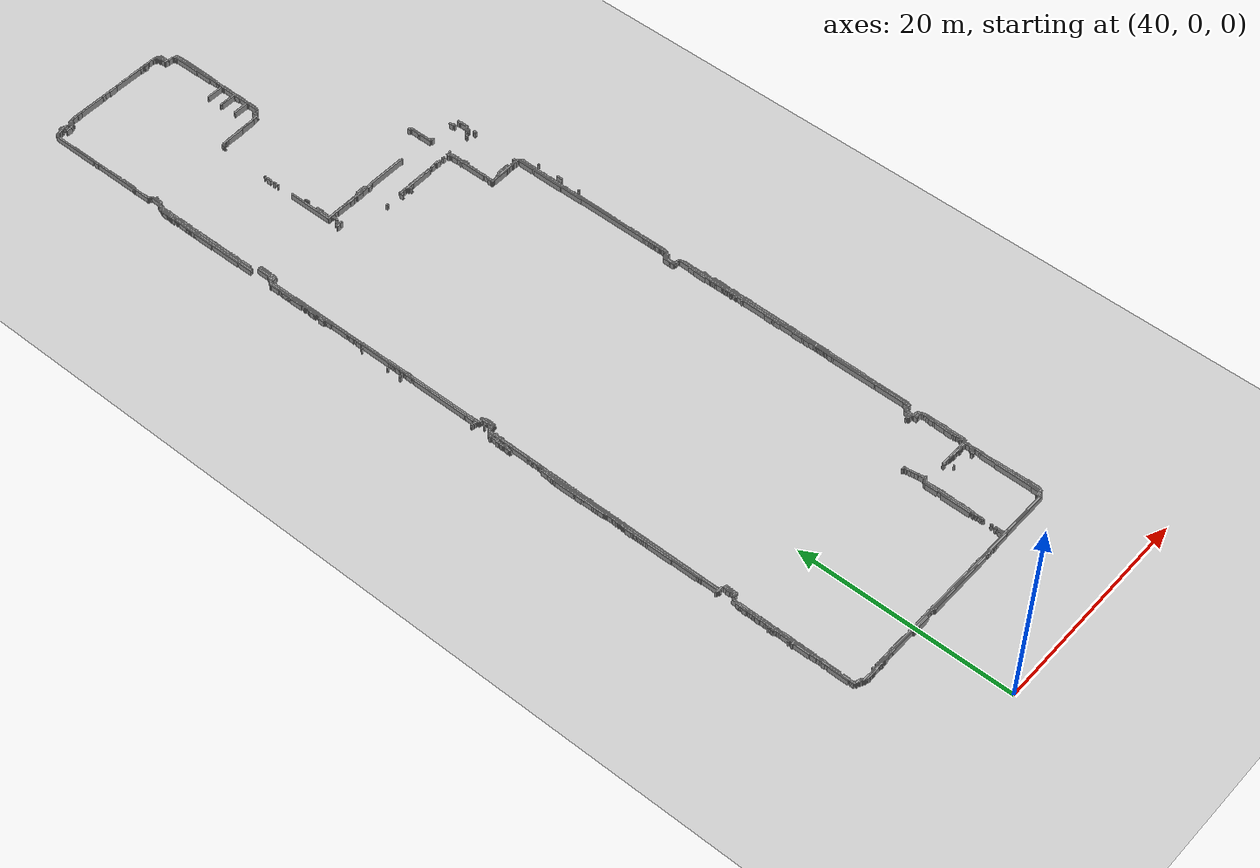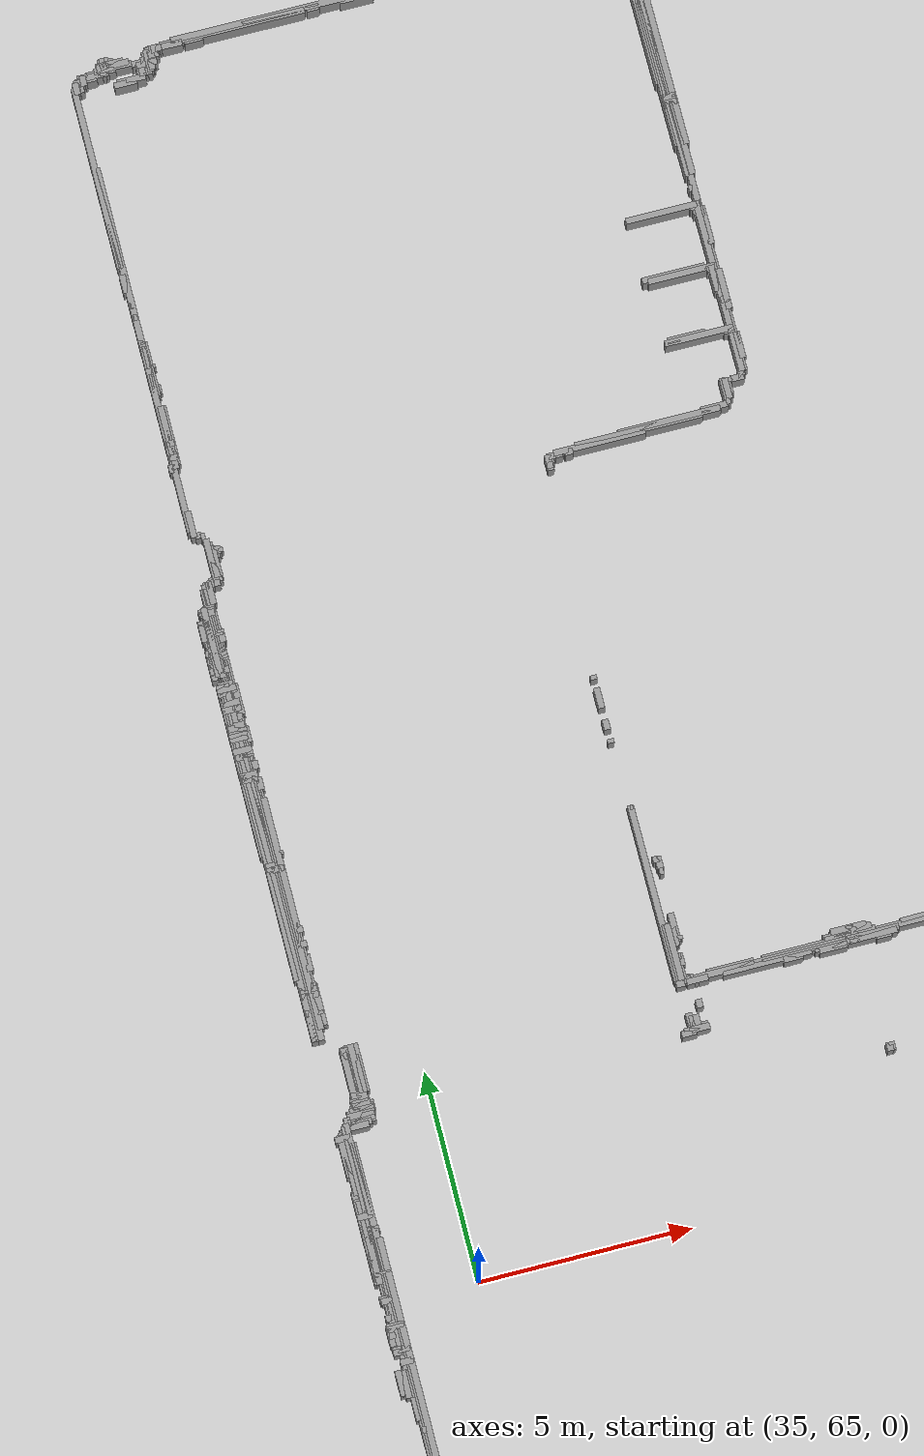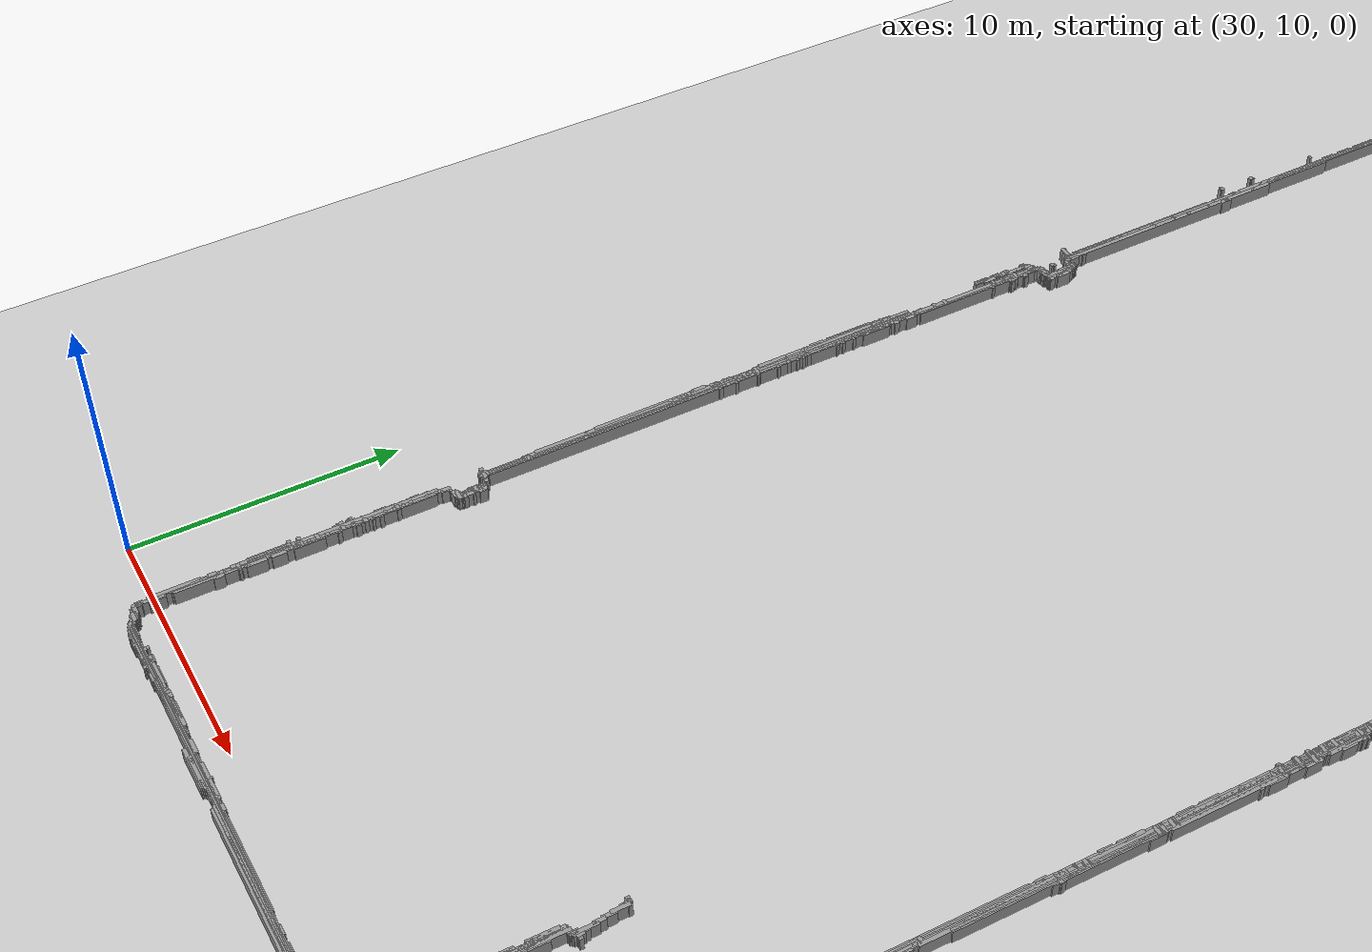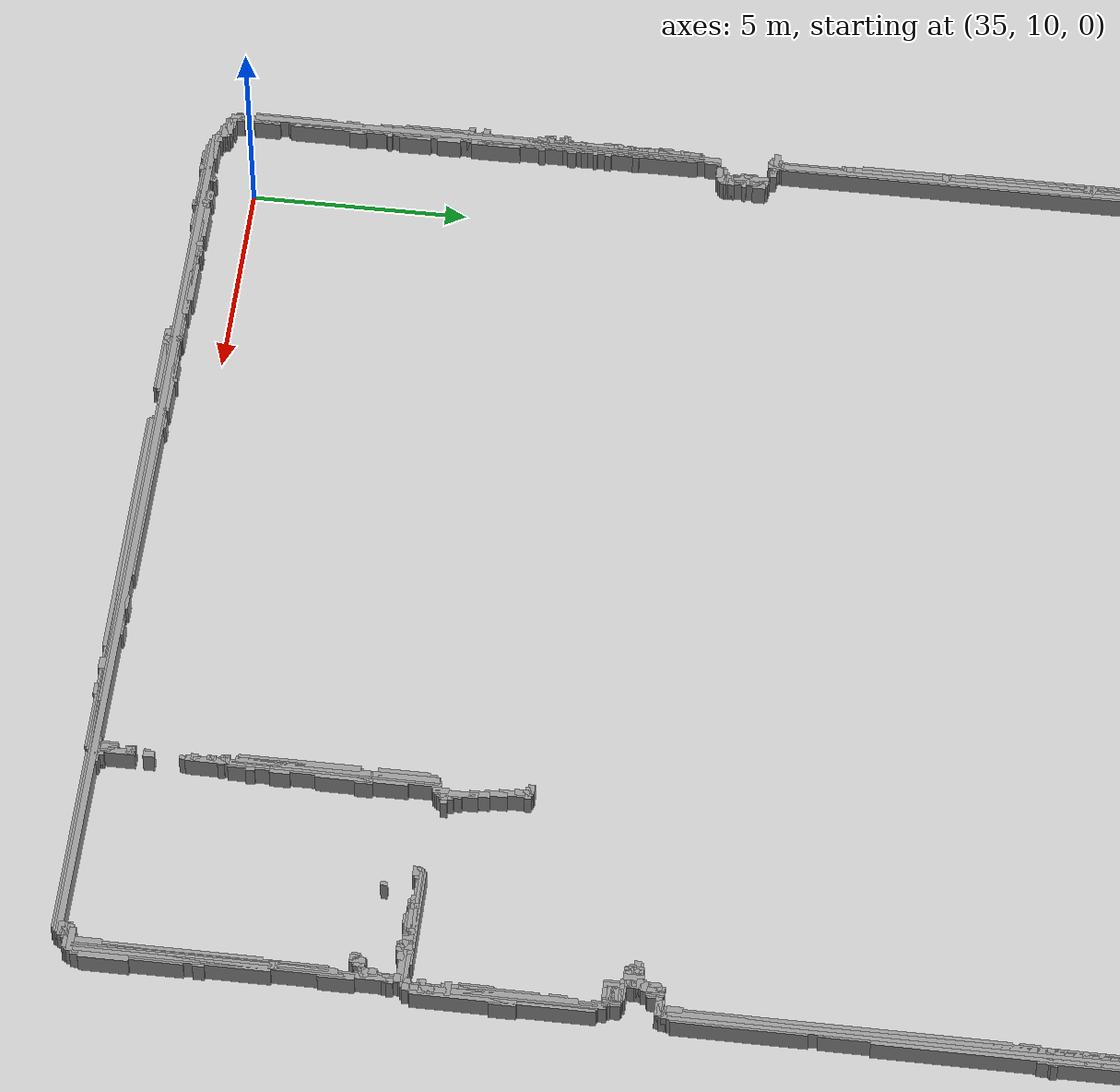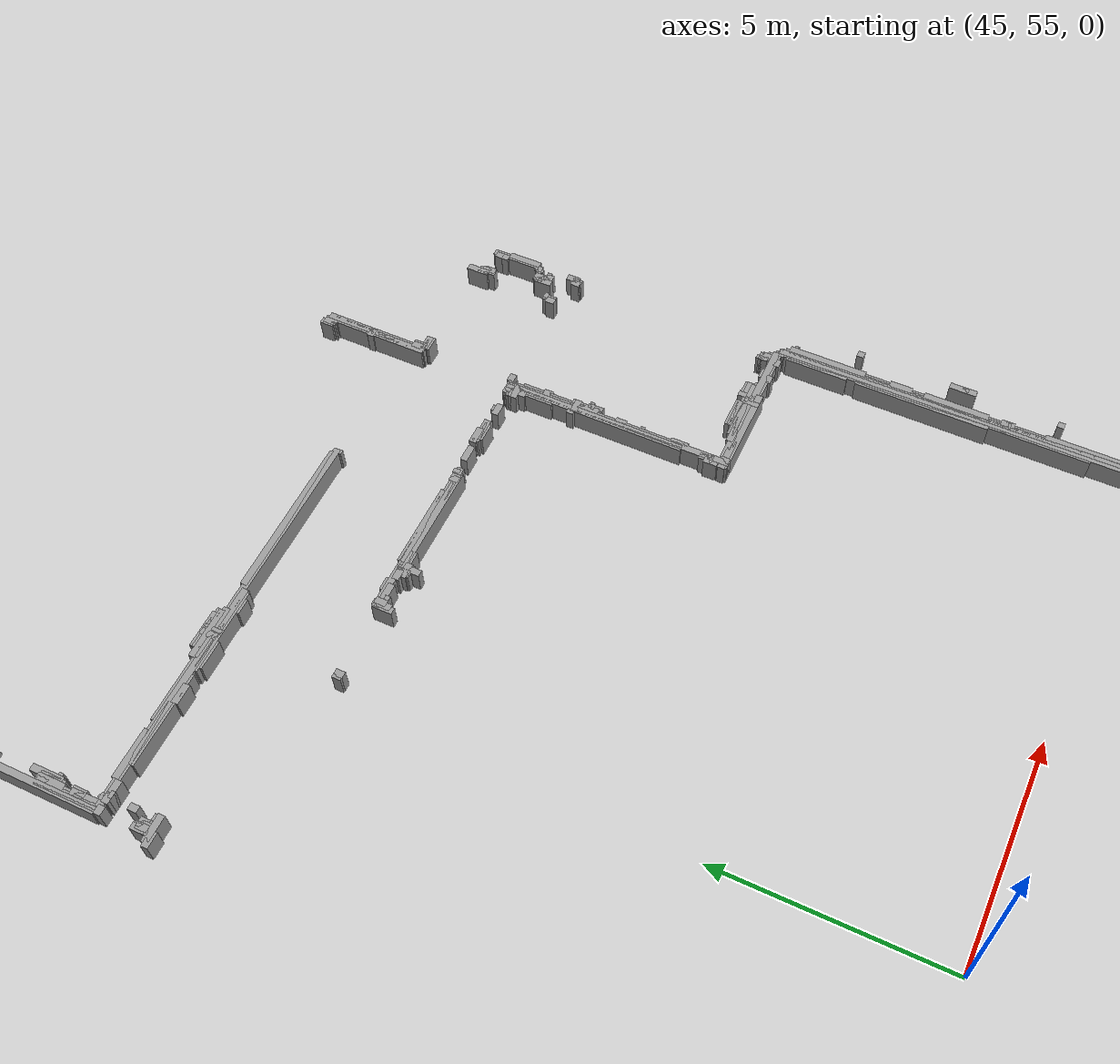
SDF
<sdf version="1.6">
  <world name="default">
    <include>
      <uri>model://sun</uri>
    </include>
    <include>
      <uri>model://ground_plane</uri>
    </include>
    <physics type="ode">
      <real_time_update_rate>1000.0</real_time_update_rate>
      <max_step_size>0.001</max_step_size>
      <real_time_factor>1</real_time_factor>
      <ode>
        <solver>
          <type>quick</type>
          <iters>150</iters>
          <precon_iters>0</precon_iters>
          <sor>1.400000</sor>
          <use_dynamic_moi_rescaling>1</use_dynamic_moi_rescaling>
        </solver>
        <constraints>
          <cfm>0.00001</cfm>
          <erp>0.2</erp>
          <contact_max_correcting_vel>2000.000000</contact_max_correcting_vel>
          <contact_surface_layer>0.01000</contact_surface_layer>
        </constraints>
      </ode>
    </physics>
    <scene>
      <ambient>0.4 0.4 0.4 1</ambient>
      <background>0.7 0.7 0.7 1</background>
      <shadows>true</shadows>
    </scene>
    <gui fullscreen="0">
      <camera name="user_camera">
        <pose>0.0 0.0 17.0 -1.5708 1.5708 0</pose>
        <view_controller>orbit</view_controller>
      </camera>
    </gui>
    <model name="obstacle">
      <static>1</static>
      <pose frame="">0 0 0 0 0 0</pose>
      <link name="obstacle">
        <collision name="obstacle_1">
          <pose>39.7 8.85 0 0 0 1.5708</pose>
          <geometry>
            <box>
              <size>0.4 0.15 1.0</size>
            </box>
          </geometry>
        </collision>
        <visual name="obstacle_1">
          <pose>39.7 8.85 0 0 0 1.5708</pose>
          <geometry>
            <box>
              <size>0.4 0.15 1.0</size>
            </box>
          </geometry>
          <material>
            <script>
              <uri>file://media/materials/scripts/gazebo.material</uri>
              <name>Gazebo/Grey</name>
            </script>
            <ambient>1 1 1 1</ambient>
          </material>
        </visual>
        <collision name="obstacle_2">
          <pose>39.75 8.85 0 0 0 1.5708</pose>
          <geometry>
            <box>
              <size>0.4 0.15 1.0</size>
            </box>
          </geometry>
        </collision>
        <visual name="obstacle_2">
          <pose>39.75 8.85 0 0 0 1.5708</pose>
          <geometry>
            <box>
              <size>0.4 0.15 1.0</size>
            </box>
          </geometry>
          <material>
            <script>
              <uri>file://media/materials/scripts/gazebo.material</uri>
              <name>Gazebo/Grey</name>
            </script>
            <ambient>1 1 1 1</ambient>
          </material>
        </visual>
        <collision name="obstacle_3">
          <pose>39.800000000000004 8.8 0 0 0 1.5708</pose>
          <geometry>
            <box>
              <size>0.35000000000000003 0.15 1.0</size>
            </box>
          </geometry>
        </collision>
        <visual name="obstacle_3">
          <pose>39.800000000000004 8.8 0 0 0 1.5708</pose>
          <geometry>
            <box>
              <size>0.35000000000000003 0.15 1.0</size>
            </box>
          </geometry>
          <material>
            <script>
              <uri>file://media/materials/scripts/gazebo.material</uri>
              <name>Gazebo/Grey</name>
            </script>
            <ambient>1 1 1 1</ambient>
          </material>
        </visual>
        <collision name="obstacle_4">
          <pose>39.85 8.8 0 0 0 1.5708</pose>
          <geometry>
            <box>
              <size>0.35000000000000003 0.15 1.0</size>
            </box>
          </geometry>
        </collision>
        <visual name="obstacle_4">
          <pose>39.85 8.8 0 0 0 1.5708</pose>
          <geometry>
            <box>
              <size>0.35000000000000003 0.15 1.0</size>
            </box>
          </geometry>
          <material>
            <script>
              <uri>file://media/materials/scripts/gazebo.material</uri>
              <name>Gazebo/Grey</name>
            </script>
            <ambient>1 1 1 1</ambient>
          </material>
        </visual>
        <collision name="obstacle_5">
          <pose>34.6 8.8 0 0 0 1.5708</pose>
          <geometry>
            <box>
              <size>0.25 0.15 1.0</size>
            </box>
          </geometry>
        </collision>
        <visual name="obstacle_5">
          <pose>34.6 8.8 0 0 0 1.5708</pose>
          <geometry>
            <box>
              <size>0.25 0.15 1.0</size>
            </box>
          </geometry>
          <material>
            <script>
              <uri>file://media/materials/scripts/gazebo.material</uri>
              <name>Gazebo/Grey</name>
            </script>
            <ambient>1 1 1 1</ambient>
          </material>
        </visual>
        <collision name="obstacle_6">
          <pose>34.65 8.8 0 0 0 1.5708</pose>
          <geometry>
            <box>
              <size>0.25 0.15 1.0</size>
            </box>
          </geometry>
        </collision>
        <visual name="obstacle_6">
          <pose>34.65 8.8 0 0 0 1.5708</pose>
          <geometry>
            <box>
              <size>0.25 0.15 1.0</size>
            </box>
          </geometry>
          <material>
            <script>
              <uri>file://media/materials/scripts/gazebo.material</uri>
              <name>Gazebo/Grey</name>
            </script>
            <ambient>1 1 1 1</ambient>
          </material>
        </visual>
        <collision name="obstacle_7">
          <pose>35.7 8.85 0 0 0 1.5708</pose>
          <geometry>
            <box>
              <size>0.35000000000000003 0.15 1.0</size>
            </box>
          </geometry>
        </collision>
        <visual name="obstacle_7">
          <pose>35.7 8.85 0 0 0 1.5708</pose>
          <geometry>
            <box>
              <size>0.35000000000000003 0.15 1.0</size>
            </box>
          </geometry>
          <material>
            <script>
              <uri>file://media/materials/scripts/gazebo.material</uri>
              <name>Gazebo/Grey</name>
            </script>
            <ambient>1 1 1 1</ambient>
          </material>
        </visual>
        <collision name="obstacle_8">
          <pose>40.35 8.700000000000001 0 0 0 0</pose>
          <geometry>
            <box>
              <size>1.75 0.15 1.0</size>
            </box>
          </geometry>
        </collision>
        <visual name="obstacle_8">
          <pose>40.35 8.700000000000001 0 0 0 0</pose>
          <geometry>
            <box>
              <size>1.75 0.15 1.0</size>
            </box>
          </geometry>
          <material>
            <script>
              <uri>file://media/materials/scripts/gazebo.material</uri>
              <name>Gazebo/Grey</name>
            </script>
            <ambient>1 1 1 1</ambient>
          </material>
        </visual>
        <collision name="obstacle_9">
          <pose>45.300000000000004 8.700000000000001 0 0 0 0</pose>
          <geometry>
            <box>
              <size>6.4 0.15 1.0</size>
            </box>
          </geometry>
        </collision>
        <visual name="obstacle_9">
          <pose>45.300000000000004 8.700000000000001 0 0 0 0</pose>
          <geometry>
            <box>
              <size>6.4 0.15 1.0</size>
            </box>
          </geometry>
          <material>
            <script>
              <uri>file://media/materials/scripts/gazebo.material</uri>
              <name>Gazebo/Grey</name>
            </script>
            <ambient>1 1 1 1</ambient>
          </material>
        </visual>
        <collision name="obstacle_10">
          <pose>48.95 8.700000000000001 0 0 0 0</pose>
          <geometry>
            <box>
              <size>0.30000000000000004 0.15 1.0</size>
            </box>
          </geometry>
        </collision>
        <visual name="obstacle_10">
          <pose>48.95 8.700000000000001 0 0 0 0</pose>
          <geometry>
            <box>
              <size>0.30000000000000004 0.15 1.0</size>
            </box>
          </geometry>
          <material>
            <script>
              <uri>file://media/materials/scripts/gazebo.material</uri>
              <name>Gazebo/Grey</name>
            </script>
            <ambient>1 1 1 1</ambient>
          </material>
        </visual>
        <collision name="obstacle_11">
          <pose>49.650000000000006 8.700000000000001 0 0 0 0</pose>
          <geometry>
            <box>
              <size>0.30000000000000004 0.15 1.0</size>
            </box>
          </geometry>
        </collision>
        <visual name="obstacle_11">
          <pose>49.650000000000006 8.700000000000001 0 0 0 0</pose>
          <geometry>
            <box>
              <size>0.30000000000000004 0.15 1.0</size>
            </box>
          </geometry>
          <material>
            <script>
              <uri>file://media/materials/scripts/gazebo.material</uri>
              <name>Gazebo/Grey</name>
            </script>
            <ambient>1 1 1 1</ambient>
          </material>
        </visual>
        <collision name="obstacle_12">
          <pose>34.25 8.75 0 0 0 0</pose>
          <geometry>
            <box>
              <size>0.25 0.15 1.0</size>
            </box>
          </geometry>
        </collision>
        <visual name="obstacle_12">
          <pose>34.25 8.75 0 0 0 0</pose>
          <geometry>
            <box>
              <size>0.25 0.15 1.0</size>
            </box>
          </geometry>
          <material>
            <script>
              <uri>file://media/materials/scripts/gazebo.material</uri>
              <name>Gazebo/Grey</name>
            </script>
            <ambient>1 1 1 1</ambient>
          </material>
        </visual>
        <collision name="obstacle_13">
          <pose>34.6 8.75 0 0 0 0</pose>
          <geometry>
            <box>
              <size>0.25 0.15 1.0</size>
            </box>
          </geometry>
        </collision>
        <visual name="obstacle_13">
          <pose>34.6 8.75 0 0 0 0</pose>
          <geometry>
            <box>
              <size>0.25 0.15 1.0</size>
            </box>
          </geometry>
          <material>
            <script>
              <uri>file://media/materials/scripts/gazebo.material</uri>
              <name>Gazebo/Grey</name>
            </script>
            <ambient>1 1 1 1</ambient>
          </material>
        </visual>
        <collision name="obstacle_14">
          <pose>35.35 8.9 0 0 0 1.5708</pose>
          <geometry>
            <box>
              <size>0.35000000000000003 0.15 1.0</size>
            </box>
          </geometry>
        </collision>
        <visual name="obstacle_14">
          <pose>35.35 8.9 0 0 0 1.5708</pose>
          <geometry>
            <box>
              <size>0.35000000000000003 0.15 1.0</size>
            </box>
          </geometry>
          <material>
            <script>
              <uri>file://media/materials/scripts/gazebo.material</uri>
              <name>Gazebo/Grey</name>
            </script>
            <ambient>1 1 1 1</ambient>
          </material>
        </visual>
        <collision name="obstacle_15">
          <pose>35.4 8.9 0 0 0 1.5708</pose>
          <geometry>
            <box>
              <size>0.35000000000000003 0.15 1.0</size>
            </box>
          </geometry>
        </collision>
        <visual name="obstacle_15">
          <pose>35.4 8.9 0 0 0 1.5708</pose>
          <geometry>
            <box>
              <size>0.35000000000000003 0.15 1.0</size>
            </box>
          </geometry>
          <material>
            <script>
              <uri>file://media/materials/scripts/gazebo.material</uri>
              <name>Gazebo/Grey</name>
            </script>
            <ambient>1 1 1 1</ambient>
          </material>
        </visual>
        <collision name="obstacle_16">
          <pose>35.45 8.9 0 0 0 1.5708</pose>
          <geometry>
            <box>
              <size>0.35000000000000003 0.15 1.0</size>
            </box>
          </geometry>
        </collision>
        <visual name="obstacle_16">
          <pose>35.45 8.9 0 0 0 1.5708</pose>
          <geometry>
            <box>
              <size>0.35000000000000003 0.15 1.0</size>
            </box>
          </geometry>
          <material>
            <script>
              <uri>file://media/materials/scripts/gazebo.material</uri>
              <name>Gazebo/Grey</name>
            </script>
            <ambient>1 1 1 1</ambient>
          </material>
        </visual>
        <collision name="obstacle_17">
          <pose>35.5 8.9 0 0 0 1.5708</pose>
          <geometry>
            <box>
              <size>0.35000000000000003 0.15 1.0</size>
            </box>
          </geometry>
        </collision>
        <visual name="obstacle_17">
          <pose>35.5 8.9 0 0 0 1.5708</pose>
          <geometry>
            <box>
              <size>0.35000000000000003 0.15 1.0</size>
            </box>
          </geometry>
          <material>
            <script>
              <uri>file://media/materials/scripts/gazebo.material</uri>
              <name>Gazebo/Grey</name>
            </script>
            <ambient>1 1 1 1</ambient>
          </material>
        </visual>
        <collision name="obstacle_18">
          <pose>35.6 8.9 0 0 0 1.5708</pose>
          <geometry>
            <box>
              <size>0.30000000000000004 0.15 1.0</size>
            </box>
          </geometry>
        </collision>
        <visual name="obstacle_18">
          <pose>35.6 8.9 0 0 0 1.5708</pose>
          <geometry>
            <box>
              <size>0.30000000000000004 0.15 1.0</size>
            </box>
          </geometry>
          <material>
            <script>
              <uri>file://media/materials/scripts/gazebo.material</uri>
              <name>Gazebo/Grey</name>
            </script>
            <ambient>1 1 1 1</ambient>
          </material>
        </visual>
        <collision name="obstacle_19">
          <pose>35.65 8.9 0 0 0 1.5708</pose>
          <geometry>
            <box>
              <size>0.30000000000000004 0.15 1.0</size>
            </box>
          </geometry>
        </collision>
        <visual name="obstacle_19">
          <pose>35.65 8.9 0 0 0 1.5708</pose>
          <geometry>
            <box>
              <size>0.30000000000000004 0.15 1.0</size>
            </box>
          </geometry>
          <material>
            <script>
              <uri>file://media/materials/scripts/gazebo.material</uri>
              <name>Gazebo/Grey</name>
            </script>
            <ambient>1 1 1 1</ambient>
          </material>
        </visual>
        <collision name="obstacle_20">
          <pose>40.35 8.75 0 0 0 0</pose>
          <geometry>
            <box>
              <size>1.75 0.15 1.0</size>
            </box>
          </geometry>
        </collision>
        <visual name="obstacle_20">
          <pose>40.35 8.75 0 0 0 0</pose>
          <geometry>
            <box>
              <size>1.75 0.15 1.0</size>
            </box>
          </geometry>
          <material>
            <script>
              <uri>file://media/materials/scripts/gazebo.material</uri>
              <name>Gazebo/Grey</name>
            </script>
            <ambient>1 1 1 1</ambient>
          </material>
        </visual>
        <collision name="obstacle_21">
          <pose>46.650000000000006 8.75 0 0 0 0</pose>
          <geometry>
            <box>
              <size>9.15 0.15 1.0</size>
            </box>
          </geometry>
        </collision>
        <visual name="obstacle_21">
          <pose>46.650000000000006 8.75 0 0 0 0</pose>
          <geometry>
            <box>
              <size>9.15 0.15 1.0</size>
            </box>
          </geometry>
          <material>
            <script>
              <uri>file://media/materials/scripts/gazebo.material</uri>
              <name>Gazebo/Grey</name>
            </script>
            <ambient>1 1 1 1</ambient>
          </material>
        </visual>
        <collision name="obstacle_22">
          <pose>34.85 8.8 0 0 0 0</pose>
          <geometry>
            <box>
              <size>1.85 0.15 1.0</size>
            </box>
          </geometry>
        </collision>
        <visual name="obstacle_22">
          <pose>34.85 8.8 0 0 0 0</pose>
          <geometry>
            <box>
              <size>1.85 0.15 1.0</size>
            </box>
          </geometry>
          <material>
            <script>
              <uri>file://media/materials/scripts/gazebo.material</uri>
              <name>Gazebo/Grey</name>
            </script>
            <ambient>1 1 1 1</ambient>
          </material>
        </visual>
        <collision name="obstacle_23">
          <pose>36.2 8.8 0 0 0 0</pose>
          <geometry>
            <box>
              <size>0.4 0.15 1.0</size>
            </box>
          </geometry>
        </collision>
        <visual name="obstacle_23">
          <pose>36.2 8.8 0 0 0 0</pose>
          <geometry>
            <box>
              <size>0.4 0.15 1.0</size>
            </box>
          </geometry>
          <material>
            <script>
              <uri>file://media/materials/scripts/gazebo.material</uri>
              <name>Gazebo/Grey</name>
            </script>
            <ambient>1 1 1 1</ambient>
          </material>
        </visual>
        <collision name="obstacle_24">
          <pose>36.9 8.950000000000001 0 0 0 1.5708</pose>
          <geometry>
            <box>
              <size>0.30000000000000004 0.15 1.0</size>
            </box>
          </geometry>
        </collision>
        <visual name="obstacle_24">
          <pose>36.9 8.950000000000001 0 0 0 1.5708</pose>
          <geometry>
            <box>
              <size>0.30000000000000004 0.15 1.0</size>
            </box>
          </geometry>
          <material>
            <script>
              <uri>file://media/materials/scripts/gazebo.material</uri>
              <name>Gazebo/Grey</name>
            </script>
            <ambient>1 1 1 1</ambient>
          </material>
        </visual>
        <collision name="obstacle_25">
          <pose>36.95 8.950000000000001 0 0 0 1.5708</pose>
          <geometry>
            <box>
              <size>0.30000000000000004 0.15 1.0</size>
            </box>
          </geometry>
        </collision>
        <visual name="obstacle_25">
          <pose>36.95 8.950000000000001 0 0 0 1.5708</pose>
          <geometry>
            <box>
              <size>0.30000000000000004 0.15 1.0</size>
            </box>
          </geometry>
          <material>
            <script>
              <uri>file://media/materials/scripts/gazebo.material</uri>
              <name>Gazebo/Grey</name>
            </script>
            <ambient>1 1 1 1</ambient>
          </material>
        </visual>
        <collision name="obstacle_26">
          <pose>37.0 8.950000000000001 0 0 0 1.5708</pose>
          <geometry>
            <box>
              <size>0.30000000000000004 0.15 1.0</size>
            </box>
          </geometry>
        </collision>
        <visual name="obstacle_26">
          <pose>37.0 8.950000000000001 0 0 0 1.5708</pose>
          <geometry>
            <box>
              <size>0.30000000000000004 0.15 1.0</size>
            </box>
          </geometry>
          <material>
            <script>
              <uri>file://media/materials/scripts/gazebo.material</uri>
              <name>Gazebo/Grey</name>
            </script>
            <ambient>1 1 1 1</ambient>
          </material>
        </visual>
        <collision name="obstacle_27">
          <pose>37.050000000000004 8.950000000000001 0 0 0 1.5708</pose>
          <geometry>
            <box>
              <size>0.35000000000000003 0.15 1.0</size>
            </box>
          </geometry>
        </collision>
        <visual name="obstacle_27">
          <pose>37.050000000000004 8.950000000000001 0 0 0 1.5708</pose>
          <geometry>
            <box>
              <size>0.35000000000000003 0.15 1.0</size>
            </box>
          </geometry>
          <material>
            <script>
              <uri>file://media/materials/scripts/gazebo.material</uri>
              <name>Gazebo/Grey</name>
            </script>
            <ambient>1 1 1 1</ambient>
          </material>
        </visual>
        <collision name="obstacle_28">
          <pose>40.35 8.8 0 0 0 0</pose>
          <geometry>
            <box>
              <size>1.9000000000000001 0.15 1.0</size>
            </box>
          </geometry>
        </collision>
        <visual name="obstacle_28">
          <pose>40.35 8.8 0 0 0 0</pose>
          <geometry>
            <box>
              <size>1.9000000000000001 0.15 1.0</size>
            </box>
          </geometry>
          <material>
            <script>
              <uri>file://media/materials/scripts/gazebo.material</uri>
              <name>Gazebo/Grey</name>
            </script>
            <ambient>1 1 1 1</ambient>
          </material>
        </visual>
        <collision name="obstacle_29">
          <pose>41.75 8.9 0 0 0 1.5708</pose>
          <geometry>
            <box>
              <size>0.25 0.15 1.0</size>
            </box>
          </geometry>
        </collision>
        <visual name="obstacle_29">
          <pose>41.75 8.9 0 0 0 1.5708</pose>
          <geometry>
            <box>
              <size>0.25 0.15 1.0</size>
            </box>
          </geometry>
          <material>
            <script>
              <uri>file://media/materials/scripts/gazebo.material</uri>
              <name>Gazebo/Grey</name>
            </script>
            <ambient>1 1 1 1</ambient>
          </material>
        </visual>
        <collision name="obstacle_30">
          <pose>41.800000000000004 8.9 0 0 0 1.5708</pose>
          <geometry>
            <box>
              <size>0.25 0.15 1.0</size>
            </box>
          </geometry>
        </collision>
        <visual name="obstacle_30">
          <pose>41.800000000000004 8.9 0 0 0 1.5708</pose>
          <geometry>
            <box>
              <size>0.25 0.15 1.0</size>
            </box>
          </geometry>
          <material>
            <script>
              <uri>file://media/materials/scripts/gazebo.material</uri>
              <name>Gazebo/Grey</name>
            </script>
            <ambient>1 1 1 1</ambient>
          </material>
        </visual>
        <collision name="obstacle_31">
          <pose>41.85 8.9 0 0 0 1.5708</pose>
          <geometry>
            <box>
              <size>0.2 0.15 1.0</size>
            </box>
          </geometry>
        </collision>
        <visual name="obstacle_31">
          <pose>41.85 8.9 0 0 0 1.5708</pose>
          <geometry>
            <box>
              <size>0.2 0.15 1.0</size>
            </box>
          </geometry>
          <material>
            <script>
              <uri>file://media/materials/scripts/gazebo.material</uri>
              <name>Gazebo/Grey</name>
            </script>
            <ambient>1 1 1 1</ambient>
          </material>
        </visual>
        <collision name="obstacle_32">
          <pose>41.900000000000006 8.9 0 0 0 1.5708</pose>
          <geometry>
            <box>
              <size>0.2 0.15 1.0</size>
            </box>
          </geometry>
        </collision>
        <visual name="obstacle_32">
          <pose>41.900000000000006 8.9 0 0 0 1.5708</pose>
          <geometry>
            <box>
              <size>0.2 0.15 1.0</size>
            </box>
          </geometry>
          <material>
            <script>
              <uri>file://media/materials/scripts/gazebo.material</uri>
              <name>Gazebo/Grey</name>
            </script>
            <ambient>1 1 1 1</ambient>
          </material>
        </visual>
        <collision name="obstacle_33">
          <pose>46.650000000000006 8.8 0 0 0 0</pose>
          <geometry>
            <box>
              <size>9.3 0.15 1.0</size>
            </box>
          </geometry>
        </collision>
        <visual name="obstacle_33">
          <pose>46.650000000000006 8.8 0 0 0 0</pose>
          <geometry>
            <box>
              <size>9.3 0.15 1.0</size>
            </box>
          </geometry>
          <material>
            <script>
              <uri>file://media/materials/scripts/gazebo.material</uri>
              <name>Gazebo/Grey</name>
            </script>
            <ambient>1 1 1 1</ambient>
          </material>
        </visual>
        <collision name="obstacle_34">
          <pose>53.650000000000006 8.8 0 0 0 0</pose>
          <geometry>
            <box>
              <size>4.6000000000000005 0.15 1.0</size>
            </box>
          </geometry>
        </collision>
        <visual name="obstacle_34">
          <pose>53.650000000000006 8.8 0 0 0 0</pose>
          <geometry>
            <box>
              <size>4.6000000000000005 0.15 1.0</size>
            </box>
          </geometry>
          <material>
            <script>
              <uri>file://media/materials/scripts/gazebo.material</uri>
              <name>Gazebo/Grey</name>
            </script>
            <ambient>1 1 1 1</ambient>
          </material>
        </visual>
        <collision name="obstacle_35">
          <pose>44.900000000000006 8.85 0 0 0 0</pose>
          <geometry>
            <box>
              <size>22.3 0.15 1.0</size>
            </box>
          </geometry>
        </collision>
        <visual name="obstacle_35">
          <pose>44.900000000000006 8.85 0 0 0 0</pose>
          <geometry>
            <box>
              <size>22.3 0.15 1.0</size>
            </box>
          </geometry>
          <material>
            <script>
              <uri>file://media/materials/scripts/gazebo.material</uri>
              <name>Gazebo/Grey</name>
            </script>
            <ambient>1 1 1 1</ambient>
          </material>
        </visual>
        <collision name="obstacle_36">
          <pose>44.85 8.9 0 0 0 0</pose>
          <geometry>
            <box>
              <size>22.450000000000003 0.15 1.0</size>
            </box>
          </geometry>
        </collision>
        <visual name="obstacle_36">
          <pose>44.85 8.9 0 0 0 0</pose>
          <geometry>
            <box>
              <size>22.450000000000003 0.15 1.0</size>
            </box>
          </geometry>
          <material>
            <script>
              <uri>file://media/materials/scripts/gazebo.material</uri>
              <name>Gazebo/Grey</name>
            </script>
            <ambient>1 1 1 1</ambient>
          </material>
        </visual>
        <collision name="obstacle_37">
          <pose>33.95 8.950000000000001 0 0 0 0</pose>
          <geometry>
            <box>
              <size>0.75 0.15 1.0</size>
            </box>
          </geometry>
        </collision>
        <visual name="obstacle_37">
          <pose>33.95 8.950000000000001 0 0 0 0</pose>
          <geometry>
            <box>
              <size>0.75 0.15 1.0</size>
            </box>
          </geometry>
          <material>
            <script>
              <uri>file://media/materials/scripts/gazebo.material</uri>
              <name>Gazebo/Grey</name>
            </script>
            <ambient>1 1 1 1</ambient>
          </material>
        </visual>
        <collision name="obstacle_38">
          <pose>34.95 8.950000000000001 0 0 0 0</pose>
          <geometry>
            <box>
              <size>0.15000000000000002 0.15 1.0</size>
            </box>
          </geometry>
        </collision>
        <visual name="obstacle_38">
          <pose>34.95 8.950000000000001 0 0 0 0</pose>
          <geometry>
            <box>
              <size>0.15000000000000002 0.15 1.0</size>
            </box>
          </geometry>
          <material>
            <script>
              <uri>file://media/materials/scripts/gazebo.material</uri>
              <name>Gazebo/Grey</name>
            </script>
            <ambient>1 1 1 1</ambient>
          </material>
        </visual>
        <collision name="obstacle_39">
          <pose>40.900000000000006 8.950000000000001 0 0 0 0</pose>
          <geometry>
            <box>
              <size>11.200000000000001 0.15 1.0</size>
            </box>
          </geometry>
        </collision>
        <visual name="obstacle_39">
          <pose>40.900000000000006 8.950000000000001 0 0 0 0</pose>
          <geometry>
            <box>
              <size>11.200000000000001 0.15 1.0</size>
            </box>
          </geometry>
          <material>
            <script>
              <uri>file://media/materials/scripts/gazebo.material</uri>
              <name>Gazebo/Grey</name>
            </script>
            <ambient>1 1 1 1</ambient>
          </material>
        </visual>
        <collision name="obstacle_40">
          <pose>47.25 8.950000000000001 0 0 0 0</pose>
          <geometry>
            <box>
              <size>0.4 0.15 1.0</size>
            </box>
          </geometry>
        </collision>
        <visual name="obstacle_40">
          <pose>47.25 8.950000000000001 0 0 0 0</pose>
          <geometry>
            <box>
              <size>0.4 0.15 1.0</size>
            </box>
          </geometry>
          <material>
            <script>
              <uri>file://media/materials/scripts/gazebo.material</uri>
              <name>Gazebo/Grey</name>
            </script>
            <ambient>1 1 1 1</ambient>
          </material>
        </visual>
        <collision name="obstacle_41">
          <pose>47.95 8.950000000000001 0 0 0 0</pose>
          <geometry>
            <box>
              <size>0.4 0.15 1.0</size>
            </box>
          </geometry>
        </collision>
        <visual name="obstacle_41">
          <pose>47.95 8.950000000000001 0 0 0 0</pose>
          <geometry>
            <box>
              <size>0.4 0.15 1.0</size>
            </box>
          </geometry>
          <material>
            <script>
              <uri>file://media/materials/scripts/gazebo.material</uri>
              <name>Gazebo/Grey</name>
            </script>
            <ambient>1 1 1 1</ambient>
          </material>
        </visual>
        <collision name="obstacle_42">
          <pose>51.25 8.950000000000001 0 0 0 0</pose>
          <geometry>
            <box>
              <size>0.65 0.15 1.0</size>
            </box>
          </geometry>
        </collision>
        <visual name="obstacle_42">
          <pose>51.25 8.950000000000001 0 0 0 0</pose>
          <geometry>
            <box>
              <size>0.65 0.15 1.0</size>
            </box>
          </geometry>
          <material>
            <script>
              <uri>file://media/materials/scripts/gazebo.material</uri>
              <name>Gazebo/Grey</name>
            </script>
            <ambient>1 1 1 1</ambient>
          </material>
        </visual>
        <collision name="obstacle_43">
          <pose>55.95 8.950000000000001 0 0 0 0</pose>
          <geometry>
            <box>
              <size>0.35000000000000003 0.15 1.0</size>
            </box>
          </geometry>
        </collision>
        <visual name="obstacle_43">
          <pose>55.95 8.950000000000001 0 0 0 0</pose>
          <geometry>
            <box>
              <size>0.35000000000000003 0.15 1.0</size>
            </box>
          </geometry>
          <material>
            <script>
              <uri>file://media/materials/scripts/gazebo.material</uri>
              <name>Gazebo/Grey</name>
            </script>
            <ambient>1 1 1 1</ambient>
          </material>
        </visual>
        <collision name="obstacle_44">
          <pose>33.65 9.0 0 0 0 0</pose>
          <geometry>
            <box>
              <size>0.30000000000000004 0.15 1.0</size>
            </box>
          </geometry>
        </collision>
        <visual name="obstacle_44">
          <pose>33.65 9.0 0 0 0 0</pose>
          <geometry>
            <box>
              <size>0.30000000000000004 0.15 1.0</size>
            </box>
          </geometry>
          <material>
            <script>
              <uri>file://media/materials/scripts/gazebo.material</uri>
              <name>Gazebo/Grey</name>
            </script>
            <ambient>1 1 1 1</ambient>
          </material>
        </visual>
        <collision name="obstacle_45">
          <pose>34.95 9.0 0 0 0 0</pose>
          <geometry>
            <box>
              <size>0.15000000000000002 0.15 1.0</size>
            </box>
          </geometry>
        </collision>
        <visual name="obstacle_45">
          <pose>34.95 9.0 0 0 0 0</pose>
          <geometry>
            <box>
              <size>0.15000000000000002 0.15 1.0</size>
            </box>
          </geometry>
          <material>
            <script>
              <uri>file://media/materials/scripts/gazebo.material</uri>
              <name>Gazebo/Grey</name>
            </script>
            <ambient>1 1 1 1</ambient>
          </material>
        </visual>
        <collision name="obstacle_46">
          <pose>37.15 9.0 0 0 0 0</pose>
          <geometry>
            <box>
              <size>3.7 0.15 1.0</size>
            </box>
          </geometry>
        </collision>
        <visual name="obstacle_46">
          <pose>37.15 9.0 0 0 0 0</pose>
          <geometry>
            <box>
              <size>3.7 0.15 1.0</size>
            </box>
          </geometry>
          <material>
            <script>
              <uri>file://media/materials/scripts/gazebo.material</uri>
              <name>Gazebo/Grey</name>
            </script>
            <ambient>1 1 1 1</ambient>
          </material>
        </visual>
        <collision name="obstacle_47">
          <pose>39.5 9.0 0 0 0 0</pose>
          <geometry>
            <box>
              <size>0.6000000000000001 0.15 1.0</size>
            </box>
          </geometry>
        </collision>
        <visual name="obstacle_47">
          <pose>39.5 9.0 0 0 0 0</pose>
          <geometry>
            <box>
              <size>0.6000000000000001 0.15 1.0</size>
            </box>
          </geometry>
          <material>
            <script>
              <uri>file://media/materials/scripts/gazebo.material</uri>
              <name>Gazebo/Grey</name>
            </script>
            <ambient>1 1 1 1</ambient>
          </material>
        </visual>
        <collision name="obstacle_48">
          <pose>41.050000000000004 9.0 0 0 0 0</pose>
          <geometry>
            <box>
              <size>1.6 0.15 1.0</size>
            </box>
          </geometry>
        </collision>
        <visual name="obstacle_48">
          <pose>41.050000000000004 9.0 0 0 0 0</pose>
          <geometry>
            <box>
              <size>1.6 0.15 1.0</size>
            </box>
          </geometry>
          <material>
            <script>
              <uri>file://media/materials/scripts/gazebo.material</uri>
              <name>Gazebo/Grey</name>
            </script>
            <ambient>1 1 1 1</ambient>
          </material>
        </visual>
        <collision name="obstacle_49">
          <pose>42.2 9.0 0 0 0 0</pose>
          <geometry>
            <box>
              <size>0.30000000000000004 0.15 1.0</size>
            </box>
          </geometry>
        </collision>
        <visual name="obstacle_49">
          <pose>42.2 9.0 0 0 0 0</pose>
          <geometry>
            <box>
              <size>0.30000000000000004 0.15 1.0</size>
            </box>
          </geometry>
          <material>
            <script>
              <uri>file://media/materials/scripts/gazebo.material</uri>
              <name>Gazebo/Grey</name>
            </script>
            <ambient>1 1 1 1</ambient>
          </material>
        </visual>
        <collision name="obstacle_50">
          <pose>51.1 9.200000000000001 0 0 0 1.5708</pose>
          <geometry>
            <box>
              <size>0.4 0.15 1.0</size>
            </box>
          </geometry>
        </collision>
        <visual name="obstacle_50">
          <pose>51.1 9.200000000000001 0 0 0 1.5708</pose>
          <geometry>
            <box>
              <size>0.4 0.15 1.0</size>
            </box>
          </geometry>
          <material>
            <script>
              <uri>file://media/materials/scripts/gazebo.material</uri>
              <name>Gazebo/Grey</name>
            </script>
            <ambient>1 1 1 1</ambient>
          </material>
        </visual>
        <collision name="obstacle_51">
          <pose>51.150000000000006 9.200000000000001 0 0 0 1.5708</pose>
          <geometry>
            <box>
              <size>0.45 0.15 1.0</size>
            </box>
          </geometry>
        </collision>
        <visual name="obstacle_51">
          <pose>51.150000000000006 9.200000000000001 0 0 0 1.5708</pose>
          <geometry>
            <box>
              <size>0.45 0.15 1.0</size>
            </box>
          </geometry>
          <material>
            <script>
              <uri>file://media/materials/scripts/gazebo.material</uri>
              <name>Gazebo/Grey</name>
            </script>
            <ambient>1 1 1 1</ambient>
          </material>
        </visual>
        <collision name="obstacle_52">
          <pose>51.2 9.200000000000001 0 0 0 1.5708</pose>
          <geometry>
            <box>
              <size>0.45 0.15 1.0</size>
            </box>
          </geometry>
        </collision>
        <visual name="obstacle_52">
          <pose>51.2 9.200000000000001 0 0 0 1.5708</pose>
          <geometry>
            <box>
              <size>0.45 0.15 1.0</size>
            </box>
          </geometry>
          <material>
            <script>
              <uri>file://media/materials/scripts/gazebo.material</uri>
              <name>Gazebo/Grey</name>
            </script>
            <ambient>1 1 1 1</ambient>
          </material>
        </visual>
        <collision name="obstacle_53">
          <pose>51.25 9.4 0 0 0 1.5708</pose>
          <geometry>
            <box>
              <size>0.8 0.15 1.0</size>
            </box>
          </geometry>
        </collision>
        <visual name="obstacle_53">
          <pose>51.25 9.4 0 0 0 1.5708</pose>
          <geometry>
            <box>
              <size>0.8 0.15 1.0</size>
            </box>
          </geometry>
          <material>
            <script>
              <uri>file://media/materials/scripts/gazebo.material</uri>
              <name>Gazebo/Grey</name>
            </script>
            <ambient>1 1 1 1</ambient>
          </material>
        </visual>
        <collision name="obstacle_54">
          <pose>51.35 9.0 0 0 0 0</pose>
          <geometry>
            <box>
              <size>0.1 0.15 1.0</size>
            </box>
          </geometry>
        </collision>
        <visual name="obstacle_54">
          <pose>51.35 9.0 0 0 0 0</pose>
          <geometry>
            <box>
              <size>0.1 0.15 1.0</size>
            </box>
          </geometry>
          <material>
            <script>
              <uri>file://media/materials/scripts/gazebo.material</uri>
              <name>Gazebo/Grey</name>
            </script>
            <ambient>1 1 1 1</ambient>
          </material>
        </visual>
        <collision name="obstacle_55">
          <pose>55.95 9.0 0 0 0 0</pose>
          <geometry>
            <box>
              <size>0.35000000000000003 0.15 1.0</size>
            </box>
          </geometry>
        </collision>
        <visual name="obstacle_55">
          <pose>55.95 9.0 0 0 0 0</pose>
          <geometry>
            <box>
              <size>0.35000000000000003 0.15 1.0</size>
            </box>
          </geometry>
          <material>
            <script>
              <uri>file://media/materials/scripts/gazebo.material</uri>
              <name>Gazebo/Grey</name>
            </script>
            <ambient>1 1 1 1</ambient>
          </material>
        </visual>
        <collision name="obstacle_56">
          <pose>33.5 9.05 0 0 0 0</pose>
          <geometry>
            <box>
              <size>0.35000000000000003 0.15 1.0</size>
            </box>
          </geometry>
        </collision>
        <visual name="obstacle_56">
          <pose>33.5 9.05 0 0 0 0</pose>
          <geometry>
            <box>
              <size>0.35000000000000003 0.15 1.0</size>
            </box>
          </geometry>
          <material>
            <script>
              <uri>file://media/materials/scripts/gazebo.material</uri>
              <name>Gazebo/Grey</name>
            </script>
            <ambient>1 1 1 1</ambient>
          </material>
        </visual>
        <collision name="obstacle_57">
          <pose>34.95 9.05 0 0 0 0</pose>
          <geometry>
            <box>
              <size>0.15000000000000002 0.15 1.0</size>
            </box>
          </geometry>
        </collision>
        <visual name="obstacle_57">
          <pose>34.95 9.05 0 0 0 0</pose>
          <geometry>
            <box>
              <size>0.15000000000000002 0.15 1.0</size>
            </box>
          </geometry>
          <material>
            <script>
              <uri>file://media/materials/scripts/gazebo.material</uri>
              <name>Gazebo/Grey</name>
            </script>
            <ambient>1 1 1 1</ambient>
          </material>
        </visual>
        <collision name="obstacle_58">
          <pose>35.45 9.05 0 0 0 0</pose>
          <geometry>
            <box>
              <size>0.30000000000000004 0.15 1.0</size>
            </box>
          </geometry>
        </collision>
        <visual name="obstacle_58">
          <pose>35.45 9.05 0 0 0 0</pose>
          <geometry>
            <box>
              <size>0.30000000000000004 0.15 1.0</size>
            </box>
          </geometry>
          <material>
            <script>
              <uri>file://media/materials/scripts/gazebo.material</uri>
              <name>Gazebo/Grey</name>
            </script>
            <ambient>1 1 1 1</ambient>
          </material>
        </visual>
        <collision name="obstacle_59">
          <pose>36.25 9.05 0 0 0 0</pose>
          <geometry>
            <box>
              <size>0.8500000000000001 0.15 1.0</size>
            </box>
          </geometry>
        </collision>
        <visual name="obstacle_59">
          <pose>36.25 9.05 0 0 0 0</pose>
          <geometry>
            <box>
              <size>0.8500000000000001 0.15 1.0</size>
            </box>
          </geometry>
          <material>
            <script>
              <uri>file://media/materials/scripts/gazebo.material</uri>
              <name>Gazebo/Grey</name>
            </script>
            <ambient>1 1 1 1</ambient>
          </material>
        </visual>
        <collision name="obstacle_60">
          <pose>37.2 9.05 0 0 0 0</pose>
          <geometry>
            <box>
              <size>0.2 0.15 1.0</size>
            </box>
          </geometry>
        </collision>
        <visual name="obstacle_60">
          <pose>37.2 9.05 0 0 0 0</pose>
          <geometry>
            <box>
              <size>0.2 0.15 1.0</size>
            </box>
          </geometry>
          <material>
            <script>
              <uri>file://media/materials/scripts/gazebo.material</uri>
              <name>Gazebo/Grey</name>
            </script>
            <ambient>1 1 1 1</ambient>
          </material>
        </visual>
        <collision name="obstacle_61">
          <pose>38.050000000000004 9.05 0 0 0 0</pose>
          <geometry>
            <box>
              <size>1.1 0.15 1.0</size>
            </box>
          </geometry>
        </collision>
        <visual name="obstacle_61">
          <pose>38.050000000000004 9.05 0 0 0 0</pose>
          <geometry>
            <box>
              <size>1.1 0.15 1.0</size>
            </box>
          </geometry>
          <material>
            <script>
              <uri>file://media/materials/scripts/gazebo.material</uri>
              <name>Gazebo/Grey</name>
            </script>
            <ambient>1 1 1 1</ambient>
          </material>
        </visual>
        <collision name="obstacle_62">
          <pose>40.95 9.05 0 0 0 0</pose>
          <geometry>
            <box>
              <size>0.1 0.15 1.0</size>
            </box>
          </geometry>
        </collision>
        <visual name="obstacle_62">
          <pose>40.95 9.05 0 0 0 0</pose>
          <geometry>
            <box>
              <size>0.1 0.15 1.0</size>
            </box>
          </geometry>
          <material>
            <script>
              <uri>file://media/materials/scripts/gazebo.material</uri>
              <name>Gazebo/Grey</name>
            </script>
            <ambient>1 1 1 1</ambient>
          </material>
        </visual>
        <collision name="obstacle_63">
          <pose>51.35 9.05 0 0 0 0</pose>
          <geometry>
            <box>
              <size>0.1 0.15 1.0</size>
            </box>
          </geometry>
        </collision>
        <visual name="obstacle_63">
          <pose>51.35 9.05 0 0 0 0</pose>
          <geometry>
            <box>
              <size>0.1 0.15 1.0</size>
            </box>
          </geometry>
          <material>
            <script>
              <uri>file://media/materials/scripts/gazebo.material</uri>
              <name>Gazebo/Grey</name>
            </script>
            <ambient>1 1 1 1</ambient>
          </material>
        </visual>
        <collision name="obstacle_64">
          <pose>56.0 9.05 0 0 0 0</pose>
          <geometry>
            <box>
              <size>0.4 0.15 1.0</size>
            </box>
          </geometry>
        </collision>
        <visual name="obstacle_64">
          <pose>56.0 9.05 0 0 0 0</pose>
          <geometry>
            <box>
              <size>0.4 0.15 1.0</size>
            </box>
          </geometry>
          <material>
            <script>
              <uri>file://media/materials/scripts/gazebo.material</uri>
              <name>Gazebo/Grey</name>
            </script>
            <ambient>1 1 1 1</ambient>
          </material>
        </visual>
        <collision name="obstacle_65">
          <pose>33.45 9.1 0 0 0 0</pose>
          <geometry>
            <box>
              <size>0.4 0.15 1.0</size>
            </box>
          </geometry>
        </collision>
        <visual name="obstacle_65">
          <pose>33.45 9.1 0 0 0 0</pose>
          <geometry>
            <box>
              <size>0.4 0.15 1.0</size>
            </box>
          </geometry>
          <material>
            <script>
              <uri>file://media/materials/scripts/gazebo.material</uri>
              <name>Gazebo/Grey</name>
            </script>
            <ambient>1 1 1 1</ambient>
          </material>
        </visual>
        <collision name="obstacle_67">
          <pose>56.1 9.1 0 0 0 0</pose>
          <geometry>
            <box>
              <size>0.65 0.15 1.0</size>
            </box>
          </geometry>
        </collision>
        <visual name="obstacle_67">
          <pose>56.1 9.1 0 0 0 0</pose>
          <geometry>
            <box>
              <size>0.65 0.15 1.0</size>
            </box>
          </geometry>
          <material>
            <script>
              <uri>file://media/materials/scripts/gazebo.material</uri>
              <name>Gazebo/Grey</name>
            </script>
            <ambient>1 1 1 1</ambient>
          </material>
        </visual>
        <collision name="obstacle_68">
          <pose>33.35 9.15 0 0 0 0</pose>
          <geometry>
            <box>
              <size>0.55 0.15 1.0</size>
            </box>
          </geometry>
        </collision>
        <visual name="obstacle_68">
          <pose>33.35 9.15 0 0 0 0</pose>
          <geometry>
            <box>
              <size>0.55 0.15 1.0</size>
            </box>
          </geometry>
          <material>
            <script>
              <uri>file://media/materials/scripts/gazebo.material</uri>
              <name>Gazebo/Grey</name>
            </script>
            <ambient>1 1 1 1</ambient>
          </material>
        </visual>
        <collision name="obstacle_69">
          <pose>56.150000000000006 9.15 0 0 0 0</pose>
          <geometry>
            <box>
              <size>0.65 0.15 1.0</size>
            </box>
          </geometry>
        </collision>
        <visual name="obstacle_69">
          <pose>56.150000000000006 9.15 0 0 0 0</pose>
          <geometry>
            <box>
              <size>0.65 0.15 1.0</size>
            </box>
          </geometry>
          <material>
            <script>
              <uri>file://media/materials/scripts/gazebo.material</uri>
              <name>Gazebo/Grey</name>
            </script>
            <ambient>1 1 1 1</ambient>
          </material>
        </visual>
        <collision name="obstacle_70">
          <pose>33.0 9.75 0 0 0 1.5708</pose>
          <geometry>
            <box>
              <size>1.1500000000000001 0.15 1.0</size>
            </box>
          </geometry>
        </collision>
        <visual name="obstacle_70">
          <pose>33.0 9.75 0 0 0 1.5708</pose>
          <geometry>
            <box>
              <size>1.1500000000000001 0.15 1.0</size>
            </box>
          </geometry>
          <material>
            <script>
              <uri>file://media/materials/scripts/gazebo.material</uri>
              <name>Gazebo/Grey</name>
            </script>
            <ambient>1 1 1 1</ambient>
          </material>
        </visual>
        <collision name="obstacle_71">
          <pose>33.300000000000004 9.200000000000001 0 0 0 0</pose>
          <geometry>
            <box>
              <size>0.5 0.15 1.0</size>
            </box>
          </geometry>
        </collision>
        <visual name="obstacle_71">
          <pose>33.300000000000004 9.200000000000001 0 0 0 0</pose>
          <geometry>
            <box>
              <size>0.5 0.15 1.0</size>
            </box>
          </geometry>
          <material>
            <script>
              <uri>file://media/materials/scripts/gazebo.material</uri>
              <name>Gazebo/Grey</name>
            </script>
            <ambient>1 1 1 1</ambient>
          </material>
        </visual>
        <collision name="obstacle_72">
          <pose>56.2 9.200000000000001 0 0 0 0</pose>
          <geometry>
            <box>
              <size>0.6000000000000001 0.15 1.0</size>
            </box>
          </geometry>
        </collision>
        <visual name="obstacle_72">
          <pose>56.2 9.200000000000001 0 0 0 0</pose>
          <geometry>
            <box>
              <size>0.6000000000000001 0.15 1.0</size>
            </box>
          </geometry>
          <material>
            <script>
              <uri>file://media/materials/scripts/gazebo.material</uri>
              <name>Gazebo/Grey</name>
            </script>
            <ambient>1 1 1 1</ambient>
          </material>
        </visual>
        <collision name="obstacle_73">
          <pose>33.2 9.25 0 0 0 0</pose>
          <geometry>
            <box>
              <size>0.30000000000000004 0.15 1.0</size>
            </box>
          </geometry>
        </collision>
        <visual name="obstacle_73">
          <pose>33.2 9.25 0 0 0 0</pose>
          <geometry>
            <box>
              <size>0.30000000000000004 0.15 1.0</size>
            </box>
          </geometry>
          <material>
            <script>
              <uri>file://media/materials/scripts/gazebo.material</uri>
              <name>Gazebo/Grey</name>
            </script>
            <ambient>1 1 1 1</ambient>
          </material>
        </visual>
        <collision name="obstacle_74">
          <pose>56.2 9.55 0 0 0 1.5708</pose>
          <geometry>
            <box>
              <size>0.65 0.15 1.0</size>
            </box>
          </geometry>
        </collision>
        <visual name="obstacle_74">
          <pose>56.2 9.55 0 0 0 1.5708</pose>
          <geometry>
            <box>
              <size>0.65 0.15 1.0</size>
            </box>
          </geometry>
          <material>
            <script>
              <uri>file://media/materials/scripts/gazebo.material</uri>
              <name>Gazebo/Grey</name>
            </script>
            <ambient>1 1 1 1</ambient>
          </material>
        </visual>
        <collision name="obstacle_75">
          <pose>56.25 11.3 0 0 0 1.5708</pose>
          <geometry>
            <box>
              <size>4.1000000000000005 0.15 1.0</size>
            </box>
          </geometry>
        </collision>
        <visual name="obstacle_75">
          <pose>56.25 11.3 0 0 0 1.5708</pose>
          <geometry>
            <box>
              <size>4.1000000000000005 0.15 1.0</size>
            </box>
          </geometry>
          <material>
            <script>
              <uri>file://media/materials/scripts/gazebo.material</uri>
              <name>Gazebo/Grey</name>
            </script>
            <ambient>1 1 1 1</ambient>
          </material>
        </visual>
        <collision name="obstacle_76">
          <pose>56.300000000000004 12.0 0 0 0 1.5708</pose>
          <geometry>
            <box>
              <size>5.550000000000001 0.15 1.0</size>
            </box>
          </geometry>
        </collision>
        <visual name="obstacle_76">
          <pose>56.300000000000004 12.0 0 0 0 1.5708</pose>
          <geometry>
            <box>
              <size>5.550000000000001 0.15 1.0</size>
            </box>
          </geometry>
          <material>
            <script>
              <uri>file://media/materials/scripts/gazebo.material</uri>
              <name>Gazebo/Grey</name>
            </script>
            <ambient>1 1 1 1</ambient>
          </material>
        </visual>
        <collision name="obstacle_77">
          <pose>56.35 12.100000000000001 0 0 0 1.5708</pose>
          <geometry>
            <box>
              <size>5.75 0.15 1.0</size>
            </box>
          </geometry>
        </collision>
        <visual name="obstacle_77">
          <pose>56.35 12.100000000000001 0 0 0 1.5708</pose>
          <geometry>
            <box>
              <size>5.75 0.15 1.0</size>
            </box>
          </geometry>
          <material>
            <script>
              <uri>file://media/materials/scripts/gazebo.material</uri>
              <name>Gazebo/Grey</name>
            </script>
            <ambient>1 1 1 1</ambient>
          </material>
        </visual>
        <collision name="obstacle_78">
          <pose>56.400000000000006 12.9 0 0 0 1.5708</pose>
          <geometry>
            <box>
              <size>7.300000000000001 0.15 1.0</size>
            </box>
          </geometry>
        </collision>
        <visual name="obstacle_78">
          <pose>56.400000000000006 12.9 0 0 0 1.5708</pose>
          <geometry>
            <box>
              <size>7.300000000000001 0.15 1.0</size>
            </box>
          </geometry>
          <material>
            <script>
              <uri>file://media/materials/scripts/gazebo.material</uri>
              <name>Gazebo/Grey</name>
            </script>
            <ambient>1 1 1 1</ambient>
          </material>
        </visual>
        <collision name="obstacle_79">
          <pose>56.45 11.4 0 0 0 1.5708</pose>
          <geometry>
            <box>
              <size>4.3 0.15 1.0</size>
            </box>
          </geometry>
        </collision>
        <visual name="obstacle_79">
          <pose>56.45 11.4 0 0 0 1.5708</pose>
          <geometry>
            <box>
              <size>4.3 0.15 1.0</size>
            </box>
          </geometry>
          <material>
            <script>
              <uri>file://media/materials/scripts/gazebo.material</uri>
              <name>Gazebo/Grey</name>
            </script>
            <ambient>1 1 1 1</ambient>
          </material>
        </visual>
        <collision name="obstacle_80">
          <pose>56.5 10.450000000000001 0 0 0 1.5708</pose>
          <geometry>
            <box>
              <size>2.45 0.15 1.0</size>
            </box>
          </geometry>
        </collision>
        <visual name="obstacle_80">
          <pose>56.5 10.450000000000001 0 0 0 1.5708</pose>
          <geometry>
            <box>
              <size>2.45 0.15 1.0</size>
            </box>
          </geometry>
          <material>
            <script>
              <uri>file://media/materials/scripts/gazebo.material</uri>
              <name>Gazebo/Grey</name>
            </script>
            <ambient>1 1 1 1</ambient>
          </material>
        </visual>
        <collision name="obstacle_81">
          <pose>32.95 9.450000000000001 0 0 0 1.5708</pose>
          <geometry>
            <box>
              <size>0.30000000000000004 0.15 1.0</size>
            </box>
          </geometry>
        </collision>
        <visual name="obstacle_81">
          <pose>32.95 9.450000000000001 0 0 0 1.5708</pose>
          <geometry>
            <box>
              <size>0.30000000000000004 0.15 1.0</size>
            </box>
          </geometry>
          <material>
            <script>
              <uri>file://media/materials/scripts/gazebo.material</uri>
              <name>Gazebo/Grey</name>
            </script>
            <ambient>1 1 1 1</ambient>
          </material>
        </visual>
        <collision name="obstacle_82">
          <pose>33.050000000000004 9.4 0 0 0 1.5708</pose>
          <geometry>
            <box>
              <size>0.2 0.15 1.0</size>
            </box>
          </geometry>
        </collision>
        <visual name="obstacle_82">
          <pose>33.050000000000004 9.4 0 0 0 1.5708</pose>
          <geometry>
            <box>
              <size>0.2 0.15 1.0</size>
            </box>
          </geometry>
          <material>
            <script>
              <uri>file://media/materials/scripts/gazebo.material</uri>
              <name>Gazebo/Grey</name>
            </script>
            <ambient>1 1 1 1</ambient>
          </material>
        </visual>
        <collision name="obstacle_84">
          <pose>33.0 9.35 0 0 0 0</pose>
          <geometry>
            <box>
              <size>0.2 0.15 1.0</size>
            </box>
          </geometry>
        </collision>
        <visual name="obstacle_84">
          <pose>33.0 9.35 0 0 0 0</pose>
          <geometry>
            <box>
              <size>0.2 0.15 1.0</size>
            </box>
          </geometry>
          <material>
            <script>
              <uri>file://media/materials/scripts/gazebo.material</uri>
              <name>Gazebo/Grey</name>
            </script>
            <ambient>1 1 1 1</ambient>
          </material>
        </visual>
        <collision name="obstacle_85">
          <pose>33.0 9.4 0 0 0 0</pose>
          <geometry>
            <box>
              <size>0.2 0.15 1.0</size>
            </box>
          </geometry>
        </collision>
        <visual name="obstacle_85">
          <pose>33.0 9.4 0 0 0 0</pose>
          <geometry>
            <box>
              <size>0.2 0.15 1.0</size>
            </box>
          </geometry>
          <material>
            <script>
              <uri>file://media/materials/scripts/gazebo.material</uri>
              <name>Gazebo/Grey</name>
            </script>
            <ambient>1 1 1 1</ambient>
          </material>
        </visual>
        <collision name="obstacle_86">
          <pose>56.550000000000004 9.950000000000001 0 0 0 1.5708</pose>
          <geometry>
            <box>
              <size>1.1 0.15 1.0</size>
            </box>
          </geometry>
        </collision>
        <visual name="obstacle_86">
          <pose>56.550000000000004 9.950000000000001 0 0 0 1.5708</pose>
          <geometry>
            <box>
              <size>1.1 0.15 1.0</size>
            </box>
          </geometry>
          <material>
            <script>
              <uri>file://media/materials/scripts/gazebo.material</uri>
              <name>Gazebo/Grey</name>
            </script>
            <ambient>1 1 1 1</ambient>
          </material>
        </visual>
        <collision name="obstacle_87">
          <pose>33.0 9.450000000000001 0 0 0 0</pose>
          <geometry>
            <box>
              <size>0.2 0.15 1.0</size>
            </box>
          </geometry>
        </collision>
        <visual name="obstacle_87">
          <pose>33.0 9.450000000000001 0 0 0 0</pose>
          <geometry>
            <box>
              <size>0.2 0.15 1.0</size>
            </box>
          </geometry>
          <material>
            <script>
              <uri>file://media/materials/scripts/gazebo.material</uri>
              <name>Gazebo/Grey</name>
            </script>
            <ambient>1 1 1 1</ambient>
          </material>
        </visual>
        <collision name="obstacle_88">
          <pose>32.95 9.5 0 0 0 0</pose>
          <geometry>
            <box>
              <size>0.15000000000000002 0.15 1.0</size>
            </box>
          </geometry>
        </collision>
        <visual name="obstacle_88">
          <pose>32.95 9.5 0 0 0 0</pose>
          <geometry>
            <box>
              <size>0.15000000000000002 0.15 1.0</size>
            </box>
          </geometry>
          <material>
            <script>
              <uri>file://media/materials/scripts/gazebo.material</uri>
              <name>Gazebo/Grey</name>
            </script>
            <ambient>1 1 1 1</ambient>
          </material>
        </visual>
        <collision name="obstacle_89">
          <pose>51.150000000000006 9.700000000000001 0 0 0 1.5708</pose>
          <geometry>
            <box>
              <size>0.2 0.15 1.0</size>
            </box>
          </geometry>
        </collision>
        <visual name="obstacle_89">
          <pose>51.150000000000006 9.700000000000001 0 0 0 1.5708</pose>
          <geometry>
            <box>
              <size>0.2 0.15 1.0</size>
            </box>
          </geometry>
          <material>
            <script>
              <uri>file://media/materials/scripts/gazebo.material</uri>
              <name>Gazebo/Grey</name>
            </script>
            <ambient>1 1 1 1</ambient>
          </material>
        </visual>
        <collision name="obstacle_90">
          <pose>51.2 9.700000000000001 0 0 0 1.5708</pose>
          <geometry>
            <box>
              <size>0.2 0.15 1.0</size>
            </box>
          </geometry>
        </collision>
        <visual name="obstacle_90">
          <pose>51.2 9.700000000000001 0 0 0 1.5708</pose>
          <geometry>
            <box>
              <size>0.2 0.15 1.0</size>
            </box>
          </geometry>
          <material>
            <script>
              <uri>file://media/materials/scripts/gazebo.material</uri>
              <name>Gazebo/Grey</name>
            </script>
            <ambient>1 1 1 1</ambient>
          </material>
        </visual>
        <collision name="obstacle_91">
          <pose>51.2 9.65 0 0 0 0</pose>
          <geometry>
            <box>
              <size>0.2 0.15 1.0</size>
            </box>
          </geometry>
        </collision>
        <visual name="obstacle_91">
          <pose>51.2 9.65 0 0 0 0</pose>
          <geometry>
            <box>
              <size>0.2 0.15 1.0</size>
            </box>
          </geometry>
          <material>
            <script>
              <uri>file://media/materials/scripts/gazebo.material</uri>
              <name>Gazebo/Grey</name>
            </script>
            <ambient>1 1 1 1</ambient>
          </material>
        </visual>
        <collision name="obstacle_92">
          <pose>51.2 9.700000000000001 0 0 0 0</pose>
          <geometry>
            <box>
              <size>0.2 0.15 1.0</size>
            </box>
          </geometry>
        </collision>
        <visual name="obstacle_92">
          <pose>51.2 9.700000000000001 0 0 0 0</pose>
          <geometry>
            <box>
              <size>0.2 0.15 1.0</size>
            </box>
          </geometry>
          <material>
            <script>
              <uri>file://media/materials/scripts/gazebo.material</uri>
              <name>Gazebo/Grey</name>
            </script>
            <ambient>1 1 1 1</ambient>
          </material>
        </visual>
        <collision name="obstacle_93">
          <pose>32.9 10.700000000000001 0 0 0 1.5708</pose>
          <geometry>
            <box>
              <size>1.9000000000000001 0.15 1.0</size>
            </box>
          </geometry>
        </collision>
        <visual name="obstacle_93">
          <pose>32.9 10.700000000000001 0 0 0 1.5708</pose>
          <geometry>
            <box>
              <size>1.9000000000000001 0.15 1.0</size>
            </box>
          </geometry>
          <material>
            <script>
              <uri>file://media/materials/scripts/gazebo.material</uri>
              <name>Gazebo/Grey</name>
            </script>
            <ambient>1 1 1 1</ambient>
          </material>
        </visual>
        <collision name="obstacle_94">
          <pose>32.95 15.05 0 0 0 1.5708</pose>
          <geometry>
            <box>
              <size>10.600000000000001 0.15 1.0</size>
            </box>
          </geometry>
        </collision>
        <visual name="obstacle_94">
          <pose>32.95 15.05 0 0 0 1.5708</pose>
          <geometry>
            <box>
              <size>10.600000000000001 0.15 1.0</size>
            </box>
          </geometry>
          <material>
            <script>
              <uri>file://media/materials/scripts/gazebo.material</uri>
              <name>Gazebo/Grey</name>
            </script>
            <ambient>1 1 1 1</ambient>
          </material>
        </visual>
        <collision name="obstacle_95">
          <pose>33.050000000000004 10.05 0 0 0 1.5708</pose>
          <geometry>
            <box>
              <size>0.6000000000000001 0.15 1.0</size>
            </box>
          </geometry>
        </collision>
        <visual name="obstacle_95">
          <pose>33.050000000000004 10.05 0 0 0 1.5708</pose>
          <geometry>
            <box>
              <size>0.6000000000000001 0.15 1.0</size>
            </box>
          </geometry>
          <material>
            <script>
              <uri>file://media/materials/scripts/gazebo.material</uri>
              <name>Gazebo/Grey</name>
            </script>
            <ambient>1 1 1 1</ambient>
          </material>
        </visual>
        <collision name="obstacle_96">
          <pose>51.25 10.100000000000001 0 0 0 1.5708</pose>
          <geometry>
            <box>
              <size>0.25 0.15 1.0</size>
            </box>
          </geometry>
        </collision>
        <visual name="obstacle_96">
          <pose>51.25 10.100000000000001 0 0 0 1.5708</pose>
          <geometry>
            <box>
              <size>0.25 0.15 1.0</size>
            </box>
          </geometry>
          <material>
            <script>
              <uri>file://media/materials/scripts/gazebo.material</uri>
              <name>Gazebo/Grey</name>
            </script>
            <ambient>1 1 1 1</ambient>
          </material>
        </visual>
        <collision name="obstacle_97">
          <pose>51.2 10.05 0 0 0 0</pose>
          <geometry>
            <box>
              <size>0.15000000000000002 0.15 1.0</size>
            </box>
          </geometry>
        </collision>
        <visual name="obstacle_97">
          <pose>51.2 10.05 0 0 0 0</pose>
          <geometry>
            <box>
              <size>0.15000000000000002 0.15 1.0</size>
            </box>
          </geometry>
          <material>
            <script>
              <uri>file://media/materials/scripts/gazebo.material</uri>
              <name>Gazebo/Grey</name>
            </script>
            <ambient>1 1 1 1</ambient>
          </material>
        </visual>
        <collision name="obstacle_98">
          <pose>51.25 10.100000000000001 0 0 0 0</pose>
          <geometry>
            <box>
              <size>0.1 0.15 1.0</size>
            </box>
          </geometry>
        </collision>
        <visual name="obstacle_98">
          <pose>51.25 10.100000000000001 0 0 0 0</pose>
          <geometry>
            <box>
              <size>0.1 0.15 1.0</size>
            </box>
          </geometry>
          <material>
            <script>
              <uri>file://media/materials/scripts/gazebo.material</uri>
              <name>Gazebo/Grey</name>
            </script>
            <ambient>1 1 1 1</ambient>
          </material>
        </visual>
        <collision name="obstacle_99">
          <pose>33.0 15.65 0 0 0 1.5708</pose>
          <geometry>
            <box>
              <size>10.200000000000001 0.15 1.0</size>
            </box>
          </geometry>
        </collision>
        <visual name="obstacle_99">
          <pose>33.0 15.65 0 0 0 1.5708</pose>
          <geometry>
            <box>
              <size>10.200000000000001 0.15 1.0</size>
            </box>
          </geometry>
          <material>
            <script>
              <uri>file://media/materials/scripts/gazebo.material</uri>
              <name>Gazebo/Grey</name>
            </script>
            <ambient>1 1 1 1</ambient>
          </material>
        </visual>
        <collision name="obstacle_100">
          <pose>33.050000000000004 15.4 0 0 0 1.5708</pose>
          <geometry>
            <box>
              <size>9.600000000000001 0.15 1.0</size>
            </box>
          </geometry>
        </collision>
        <visual name="obstacle_100">
          <pose>33.050000000000004 15.4 0 0 0 1.5708</pose>
          <geometry>
            <box>
              <size>9.600000000000001 0.15 1.0</size>
            </box>
          </geometry>
          <material>
            <script>
              <uri>file://media/materials/scripts/gazebo.material</uri>
              <name>Gazebo/Grey</name>
            </script>
            <ambient>1 1 1 1</ambient>
          </material>
        </visual>
        <collision name="obstacle_103">
          <pose>51.25 10.850000000000001 0 0 0 0</pose>
          <geometry>
            <box>
              <size>0.1 0.15 1.0</size>
            </box>
          </geometry>
        </collision>
        <visual name="obstacle_103">
          <pose>51.25 10.850000000000001 0 0 0 0</pose>
          <geometry>
            <box>
              <size>0.1 0.15 1.0</size>
            </box>
          </geometry>
          <material>
            <script>
              <uri>file://media/materials/scripts/gazebo.material</uri>
              <name>Gazebo/Grey</name>
            </script>
            <ambient>1 1 1 1</ambient>
          </material>
        </visual>
        <collision name="obstacle_104">
          <pose>51.25 13.700000000000001 0 0 0 1.5708</pose>
          <geometry>
            <box>
              <size>5.6000000000000005 0.15 1.0</size>
            </box>
          </geometry>
        </collision>
        <visual name="obstacle_104">
          <pose>51.25 13.700000000000001 0 0 0 1.5708</pose>
          <geometry>
            <box>
              <size>5.6000000000000005 0.15 1.0</size>
            </box>
          </geometry>
          <material>
            <script>
              <uri>file://media/materials/scripts/gazebo.material</uri>
              <name>Gazebo/Grey</name>
            </script>
            <ambient>1 1 1 1</ambient>
          </material>
        </visual>
        <collision name="obstacle_105">
          <pose>51.2 11.100000000000001 0 0 0 0</pose>
          <geometry>
            <box>
              <size>0.15000000000000002 0.15 1.0</size>
            </box>
          </geometry>
        </collision>
        <visual name="obstacle_105">
          <pose>51.2 11.100000000000001 0 0 0 0</pose>
          <geometry>
            <box>
              <size>0.15000000000000002 0.15 1.0</size>
            </box>
          </geometry>
          <material>
            <script>
              <uri>file://media/materials/scripts/gazebo.material</uri>
              <name>Gazebo/Grey</name>
            </script>
            <ambient>1 1 1 1</ambient>
          </material>
        </visual>
        <collision name="obstacle_106">
          <pose>51.25 11.15 0 0 0 0</pose>
          <geometry>
            <box>
              <size>0.1 0.15 1.0</size>
            </box>
          </geometry>
        </collision>
        <visual name="obstacle_106">
          <pose>51.25 11.15 0 0 0 0</pose>
          <geometry>
            <box>
              <size>0.1 0.15 1.0</size>
            </box>
          </geometry>
          <material>
            <script>
              <uri>file://media/materials/scripts/gazebo.material</uri>
              <name>Gazebo/Grey</name>
            </script>
            <ambient>1 1 1 1</ambient>
          </material>
        </visual>
        <collision name="obstacle_108">
          <pose>51.2 11.450000000000001 0 0 0 0</pose>
          <geometry>
            <box>
              <size>0.15000000000000002 0.15 1.0</size>
            </box>
          </geometry>
        </collision>
        <visual name="obstacle_108">
          <pose>51.2 11.450000000000001 0 0 0 0</pose>
          <geometry>
            <box>
              <size>0.15000000000000002 0.15 1.0</size>
            </box>
          </geometry>
          <material>
            <script>
              <uri>file://media/materials/scripts/gazebo.material</uri>
              <name>Gazebo/Grey</name>
            </script>
            <ambient>1 1 1 1</ambient>
          </material>
        </visual>
        <collision name="obstacle_109">
          <pose>51.2 11.5 0 0 0 0</pose>
          <geometry>
            <box>
              <size>0.15000000000000002 0.15 1.0</size>
            </box>
          </geometry>
        </collision>
        <visual name="obstacle_109">
          <pose>51.2 11.5 0 0 0 0</pose>
          <geometry>
            <box>
              <size>0.15000000000000002 0.15 1.0</size>
            </box>
          </geometry>
          <material>
            <script>
              <uri>file://media/materials/scripts/gazebo.material</uri>
              <name>Gazebo/Grey</name>
            </script>
            <ambient>1 1 1 1</ambient>
          </material>
        </visual>
        <collision name="obstacle_111">
          <pose>51.25 11.700000000000001 0 0 0 0</pose>
          <geometry>
            <box>
              <size>0.2 0.15 1.0</size>
            </box>
          </geometry>
        </collision>
        <visual name="obstacle_111">
          <pose>51.25 11.700000000000001 0 0 0 0</pose>
          <geometry>
            <box>
              <size>0.2 0.15 1.0</size>
            </box>
          </geometry>
          <material>
            <script>
              <uri>file://media/materials/scripts/gazebo.material</uri>
              <name>Gazebo/Grey</name>
            </script>
            <ambient>1 1 1 1</ambient>
          </material>
        </visual>
        <collision name="obstacle_112">
          <pose>51.2 11.75 0 0 0 0</pose>
          <geometry>
            <box>
              <size>0.25 0.15 1.0</size>
            </box>
          </geometry>
        </collision>
        <visual name="obstacle_112">
          <pose>51.2 11.75 0 0 0 0</pose>
          <geometry>
            <box>
              <size>0.25 0.15 1.0</size>
            </box>
          </geometry>
          <material>
            <script>
              <uri>file://media/materials/scripts/gazebo.material</uri>
              <name>Gazebo/Grey</name>
            </script>
            <ambient>1 1 1 1</ambient>
          </material>
        </visual>
        <collision name="obstacle_113">
          <pose>51.2 11.8 0 0 0 0</pose>
          <geometry>
            <box>
              <size>0.25 0.15 1.0</size>
            </box>
          </geometry>
        </collision>
        <visual name="obstacle_113">
          <pose>51.2 11.8 0 0 0 0</pose>
          <geometry>
            <box>
              <size>0.25 0.15 1.0</size>
            </box>
          </geometry>
          <material>
            <script>
              <uri>file://media/materials/scripts/gazebo.material</uri>
              <name>Gazebo/Grey</name>
            </script>
            <ambient>1 1 1 1</ambient>
          </material>
        </visual>
        <collision name="obstacle_114">
          <pose>51.300000000000004 14.200000000000001 0 0 0 1.5708</pose>
          <geometry>
            <box>
              <size>4.7 0.15 1.0</size>
            </box>
          </geometry>
        </collision>
        <visual name="obstacle_114">
          <pose>51.300000000000004 14.200000000000001 0 0 0 1.5708</pose>
          <geometry>
            <box>
              <size>4.7 0.15 1.0</size>
            </box>
          </geometry>
          <material>
            <script>
              <uri>file://media/materials/scripts/gazebo.material</uri>
              <name>Gazebo/Grey</name>
            </script>
            <ambient>1 1 1 1</ambient>
          </material>
        </visual>
        <collision name="obstacle_115">
          <pose>32.9 12.05 0 0 0 1.5708</pose>
          <geometry>
            <box>
              <size>0.30000000000000004 0.15 1.0</size>
            </box>
          </geometry>
        </collision>
        <visual name="obstacle_115">
          <pose>32.9 12.05 0 0 0 1.5708</pose>
          <geometry>
            <box>
              <size>0.30000000000000004 0.15 1.0</size>
            </box>
          </geometry>
          <material>
            <script>
              <uri>file://media/materials/scripts/gazebo.material</uri>
              <name>Gazebo/Grey</name>
            </script>
            <ambient>1 1 1 1</ambient>
          </material>
        </visual>
        <collision name="obstacle_116">
          <pose>56.5 12.0 0 0 0 1.5708</pose>
          <geometry>
            <box>
              <size>0.25 0.15 1.0</size>
            </box>
          </geometry>
        </collision>
        <visual name="obstacle_116">
          <pose>56.5 12.0 0 0 0 1.5708</pose>
          <geometry>
            <box>
              <size>0.25 0.15 1.0</size>
            </box>
          </geometry>
          <material>
            <script>
              <uri>file://media/materials/scripts/gazebo.material</uri>
              <name>Gazebo/Grey</name>
            </script>
            <ambient>1 1 1 1</ambient>
          </material>
        </visual>
        <collision name="obstacle_117">
          <pose>33.1 12.200000000000001 0 0 0 1.5708</pose>
          <geometry>
            <box>
              <size>0.4 0.15 1.0</size>
            </box>
          </geometry>
        </collision>
        <visual name="obstacle_117">
          <pose>33.1 12.200000000000001 0 0 0 1.5708</pose>
          <geometry>
            <box>
              <size>0.4 0.15 1.0</size>
            </box>
          </geometry>
          <material>
            <script>
              <uri>file://media/materials/scripts/gazebo.material</uri>
              <name>Gazebo/Grey</name>
            </script>
            <ambient>1 1 1 1</ambient>
          </material>
        </visual>
        <collision name="obstacle_118">
          <pose>51.150000000000006 13.4 0 0 0 1.5708</pose>
          <geometry>
            <box>
              <size>2.8000000000000003 0.15 1.0</size>
            </box>
          </geometry>
        </collision>
        <visual name="obstacle_118">
          <pose>51.150000000000006 13.4 0 0 0 1.5708</pose>
          <geometry>
            <box>
              <size>2.8000000000000003 0.15 1.0</size>
            </box>
          </geometry>
          <material>
            <script>
              <uri>file://media/materials/scripts/gazebo.material</uri>
              <name>Gazebo/Grey</name>
            </script>
            <ambient>1 1 1 1</ambient>
          </material>
        </visual>
        <collision name="obstacle_119">
          <pose>51.2 14.25 0 0 0 1.5708</pose>
          <geometry>
            <box>
              <size>4.5 0.15 1.0</size>
            </box>
          </geometry>
        </collision>
        <visual name="obstacle_119">
          <pose>51.2 14.25 0 0 0 1.5708</pose>
          <geometry>
            <box>
              <size>4.5 0.15 1.0</size>
            </box>
          </geometry>
          <material>
            <script>
              <uri>file://media/materials/scripts/gazebo.material</uri>
              <name>Gazebo/Grey</name>
            </script>
            <ambient>1 1 1 1</ambient>
          </material>
        </visual>
        <collision name="obstacle_120">
          <pose>51.1 13.4 0 0 0 1.5708</pose>
          <geometry>
            <box>
              <size>2.7 0.15 1.0</size>
            </box>
          </geometry>
        </collision>
        <visual name="obstacle_120">
          <pose>51.1 13.4 0 0 0 1.5708</pose>
          <geometry>
            <box>
              <size>2.7 0.15 1.0</size>
            </box>
          </geometry>
          <material>
            <script>
              <uri>file://media/materials/scripts/gazebo.material</uri>
              <name>Gazebo/Grey</name>
            </script>
            <ambient>1 1 1 1</ambient>
          </material>
        </visual>
        <collision name="obstacle_121">
          <pose>51.35 12.350000000000001 0 0 0 1.5708</pose>
          <geometry>
            <box>
              <size>0.2 0.15 1.0</size>
            </box>
          </geometry>
        </collision>
        <visual name="obstacle_121">
          <pose>51.35 12.350000000000001 0 0 0 1.5708</pose>
          <geometry>
            <box>
              <size>0.2 0.15 1.0</size>
            </box>
          </geometry>
          <material>
            <script>
              <uri>file://media/materials/scripts/gazebo.material</uri>
              <name>Gazebo/Grey</name>
            </script>
            <ambient>1 1 1 1</ambient>
          </material>
        </visual>
        <collision name="obstacle_122">
          <pose>33.0 12.350000000000001 0 0 0 0</pose>
          <geometry>
            <box>
              <size>0.25 0.15 1.0</size>
            </box>
          </geometry>
        </collision>
        <visual name="obstacle_122">
          <pose>33.0 12.350000000000001 0 0 0 0</pose>
          <geometry>
            <box>
              <size>0.25 0.15 1.0</size>
            </box>
          </geometry>
          <material>
            <script>
              <uri>file://media/materials/scripts/gazebo.material</uri>
              <name>Gazebo/Grey</name>
            </script>
            <ambient>1 1 1 1</ambient>
          </material>
        </visual>
        <collision name="obstacle_124">
          <pose>32.9 16.5 0 0 0 1.5708</pose>
          <geometry>
            <box>
              <size>7.6000000000000005 0.15 1.0</size>
            </box>
          </geometry>
        </collision>
        <visual name="obstacle_124">
          <pose>32.9 16.5 0 0 0 1.5708</pose>
          <geometry>
            <box>
              <size>7.6000000000000005 0.15 1.0</size>
            </box>
          </geometry>
          <material>
            <script>
              <uri>file://media/materials/scripts/gazebo.material</uri>
              <name>Gazebo/Grey</name>
            </script>
            <ambient>1 1 1 1</ambient>
          </material>
        </visual>
        <collision name="obstacle_125">
          <pose>51.35 13.0 0 0 0 1.5708</pose>
          <geometry>
            <box>
              <size>0.45 0.15 1.0</size>
            </box>
          </geometry>
        </collision>
        <visual name="obstacle_125">
          <pose>51.35 13.0 0 0 0 1.5708</pose>
          <geometry>
            <box>
              <size>0.45 0.15 1.0</size>
            </box>
          </geometry>
          <material>
            <script>
              <uri>file://media/materials/scripts/gazebo.material</uri>
              <name>Gazebo/Grey</name>
            </script>
            <ambient>1 1 1 1</ambient>
          </material>
        </visual>
        <collision name="obstacle_126">
          <pose>33.1 12.950000000000001 0 0 0 1.5708</pose>
          <geometry>
            <box>
              <size>0.1 0.15 1.0</size>
            </box>
          </geometry>
        </collision>
        <visual name="obstacle_126">
          <pose>33.1 12.950000000000001 0 0 0 1.5708</pose>
          <geometry>
            <box>
              <size>0.1 0.15 1.0</size>
            </box>
          </geometry>
          <material>
            <script>
              <uri>file://media/materials/scripts/gazebo.material</uri>
              <name>Gazebo/Grey</name>
            </script>
            <ambient>1 1 1 1</ambient>
          </material>
        </visual>
        <collision name="obstacle_127">
          <pose>33.0 12.950000000000001 0 0 0 0</pose>
          <geometry>
            <box>
              <size>0.30000000000000004 0.15 1.0</size>
            </box>
          </geometry>
        </collision>
        <visual name="obstacle_127">
          <pose>33.0 12.950000000000001 0 0 0 0</pose>
          <geometry>
            <box>
              <size>0.30000000000000004 0.15 1.0</size>
            </box>
          </geometry>
          <material>
            <script>
              <uri>file://media/materials/scripts/gazebo.material</uri>
              <name>Gazebo/Grey</name>
            </script>
            <ambient>1 1 1 1</ambient>
          </material>
        </visual>
        <collision name="obstacle_128">
          <pose>33.1 13.55 0 0 0 1.5708</pose>
          <geometry>
            <box>
              <size>0.75 0.15 1.0</size>
            </box>
          </geometry>
        </collision>
        <visual name="obstacle_128">
          <pose>33.1 13.55 0 0 0 1.5708</pose>
          <geometry>
            <box>
              <size>0.75 0.15 1.0</size>
            </box>
          </geometry>
          <material>
            <script>
              <uri>file://media/materials/scripts/gazebo.material</uri>
              <name>Gazebo/Grey</name>
            </script>
            <ambient>1 1 1 1</ambient>
          </material>
        </visual>
        <collision name="obstacle_129">
          <pose>32.85 14.100000000000001 0 0 0 1.5708</pose>
          <geometry>
            <box>
              <size>1.6 0.15 1.0</size>
            </box>
          </geometry>
        </collision>
        <visual name="obstacle_129">
          <pose>32.85 14.100000000000001 0 0 0 1.5708</pose>
          <geometry>
            <box>
              <size>1.6 0.15 1.0</size>
            </box>
          </geometry>
          <material>
            <script>
              <uri>file://media/materials/scripts/gazebo.material</uri>
              <name>Gazebo/Grey</name>
            </script>
            <ambient>1 1 1 1</ambient>
          </material>
        </visual>
        <collision name="obstacle_130">
          <pose>56.35 13.55 0 0 0 0</pose>
          <geometry>
            <box>
              <size>0.2 0.15 1.0</size>
            </box>
          </geometry>
        </collision>
        <visual name="obstacle_130">
          <pose>56.35 13.55 0 0 0 0</pose>
          <geometry>
            <box>
              <size>0.2 0.15 1.0</size>
            </box>
          </geometry>
          <material>
            <script>
              <uri>file://media/materials/scripts/gazebo.material</uri>
              <name>Gazebo/Grey</name>
            </script>
            <ambient>1 1 1 1</ambient>
          </material>
        </visual>
        <collision name="obstacle_131">
          <pose>56.35 13.600000000000001 0 0 0 0</pose>
          <geometry>
            <box>
              <size>0.2 0.15 1.0</size>
            </box>
          </geometry>
        </collision>
        <visual name="obstacle_131">
          <pose>56.35 13.600000000000001 0 0 0 0</pose>
          <geometry>
            <box>
              <size>0.2 0.15 1.0</size>
            </box>
          </geometry>
          <material>
            <script>
              <uri>file://media/materials/scripts/gazebo.material</uri>
              <name>Gazebo/Grey</name>
            </script>
            <ambient>1 1 1 1</ambient>
          </material>
        </visual>
        <collision name="obstacle_132">
          <pose>56.35 13.65 0 0 0 0</pose>
          <geometry>
            <box>
              <size>0.2 0.15 1.0</size>
            </box>
          </geometry>
        </collision>
        <visual name="obstacle_132">
          <pose>56.35 13.65 0 0 0 0</pose>
          <geometry>
            <box>
              <size>0.2 0.15 1.0</size>
            </box>
          </geometry>
          <material>
            <script>
              <uri>file://media/materials/scripts/gazebo.material</uri>
              <name>Gazebo/Grey</name>
            </script>
            <ambient>1 1 1 1</ambient>
          </material>
        </visual>
        <collision name="obstacle_133">
          <pose>51.35 14.8 0 0 0 1.5708</pose>
          <geometry>
            <box>
              <size>2.0500000000000003 0.15 1.0</size>
            </box>
          </geometry>
        </collision>
        <visual name="obstacle_133">
          <pose>51.35 14.8 0 0 0 1.5708</pose>
          <geometry>
            <box>
              <size>2.0500000000000003 0.15 1.0</size>
            </box>
          </geometry>
          <material>
            <script>
              <uri>file://media/materials/scripts/gazebo.material</uri>
              <name>Gazebo/Grey</name>
            </script>
            <ambient>1 1 1 1</ambient>
          </material>
        </visual>
        <collision name="obstacle_135">
          <pose>33.1 14.350000000000001 0 0 0 1.5708</pose>
          <geometry>
            <box>
              <size>0.55 0.15 1.0</size>
            </box>
          </geometry>
        </collision>
        <visual name="obstacle_135">
          <pose>33.1 14.350000000000001 0 0 0 1.5708</pose>
          <geometry>
            <box>
              <size>0.55 0.15 1.0</size>
            </box>
          </geometry>
          <material>
            <script>
              <uri>file://media/materials/scripts/gazebo.material</uri>
              <name>Gazebo/Grey</name>
            </script>
            <ambient>1 1 1 1</ambient>
          </material>
        </visual>
        <collision name="obstacle_136">
          <pose>56.45 14.950000000000001 0 0 0 1.5708</pose>
          <geometry>
            <box>
              <size>0.8 0.15 1.0</size>
            </box>
          </geometry>
        </collision>
        <visual name="obstacle_136">
          <pose>56.45 14.950000000000001 0 0 0 1.5708</pose>
          <geometry>
            <box>
              <size>0.8 0.15 1.0</size>
            </box>
          </geometry>
          <material>
            <script>
              <uri>file://media/materials/scripts/gazebo.material</uri>
              <name>Gazebo/Grey</name>
            </script>
            <ambient>1 1 1 1</ambient>
          </material>
        </visual>
        <collision name="obstacle_137">
          <pose>51.400000000000006 14.850000000000001 0 0 0 1.5708</pose>
          <geometry>
            <box>
              <size>0.4 0.15 1.0</size>
            </box>
          </geometry>
        </collision>
        <visual name="obstacle_137">
          <pose>51.400000000000006 14.850000000000001 0 0 0 1.5708</pose>
          <geometry>
            <box>
              <size>0.4 0.15 1.0</size>
            </box>
          </geometry>
          <material>
            <script>
              <uri>file://media/materials/scripts/gazebo.material</uri>
              <name>Gazebo/Grey</name>
            </script>
            <ambient>1 1 1 1</ambient>
          </material>
        </visual>
        <collision name="obstacle_138">
          <pose>32.95 14.8 0 0 0 0</pose>
          <geometry>
            <box>
              <size>0.30000000000000004 0.15 1.0</size>
            </box>
          </geometry>
        </collision>
        <visual name="obstacle_138">
          <pose>32.95 14.8 0 0 0 0</pose>
          <geometry>
            <box>
              <size>0.30000000000000004 0.15 1.0</size>
            </box>
          </geometry>
          <material>
            <script>
              <uri>file://media/materials/scripts/gazebo.material</uri>
              <name>Gazebo/Grey</name>
            </script>
            <ambient>1 1 1 1</ambient>
          </material>
        </visual>
        <collision name="obstacle_139">
          <pose>32.9 14.850000000000001 0 0 0 0</pose>
          <geometry>
            <box>
              <size>0.45 0.15 1.0</size>
            </box>
          </geometry>
        </collision>
        <visual name="obstacle_139">
          <pose>32.9 14.850000000000001 0 0 0 0</pose>
          <geometry>
            <box>
              <size>0.45 0.15 1.0</size>
            </box>
          </geometry>
          <material>
            <script>
              <uri>file://media/materials/scripts/gazebo.material</uri>
              <name>Gazebo/Grey</name>
            </script>
            <ambient>1 1 1 1</ambient>
          </material>
        </visual>
        <collision name="obstacle_140">
          <pose>33.1 15.450000000000001 0 0 0 1.5708</pose>
          <geometry>
            <box>
              <size>1.1500000000000001 0.15 1.0</size>
            </box>
          </geometry>
        </collision>
        <visual name="obstacle_140">
          <pose>33.1 15.450000000000001 0 0 0 1.5708</pose>
          <geometry>
            <box>
              <size>1.1500000000000001 0.15 1.0</size>
            </box>
          </geometry>
          <material>
            <script>
              <uri>file://media/materials/scripts/gazebo.material</uri>
              <name>Gazebo/Grey</name>
            </script>
            <ambient>1 1 1 1</ambient>
          </material>
        </visual>
        <collision name="obstacle_141">
          <pose>51.300000000000004 14.950000000000001 0 0 0 0</pose>
          <geometry>
            <box>
              <size>0.30000000000000004 0.15 1.0</size>
            </box>
          </geometry>
        </collision>
        <visual name="obstacle_141">
          <pose>51.300000000000004 14.950000000000001 0 0 0 0</pose>
          <geometry>
            <box>
              <size>0.30000000000000004 0.15 1.0</size>
            </box>
          </geometry>
          <material>
            <script>
              <uri>file://media/materials/scripts/gazebo.material</uri>
              <name>Gazebo/Grey</name>
            </script>
            <ambient>1 1 1 1</ambient>
          </material>
        </visual>
        <collision name="obstacle_142">
          <pose>33.0 15.100000000000001 0 0 0 0</pose>
          <geometry>
            <box>
              <size>0.30000000000000004 0.15 1.0</size>
            </box>
          </geometry>
        </collision>
        <visual name="obstacle_142">
          <pose>33.0 15.100000000000001 0 0 0 0</pose>
          <geometry>
            <box>
              <size>0.30000000000000004 0.15 1.0</size>
            </box>
          </geometry>
          <material>
            <script>
              <uri>file://media/materials/scripts/gazebo.material</uri>
              <name>Gazebo/Grey</name>
            </script>
            <ambient>1 1 1 1</ambient>
          </material>
        </visual>
        <collision name="obstacle_143">
          <pose>32.95 15.15 0 0 0 0</pose>
          <geometry>
            <box>
              <size>0.35000000000000003 0.15 1.0</size>
            </box>
          </geometry>
        </collision>
        <visual name="obstacle_143">
          <pose>32.95 15.15 0 0 0 0</pose>
          <geometry>
            <box>
              <size>0.35000000000000003 0.15 1.0</size>
            </box>
          </geometry>
          <material>
            <script>
              <uri>file://media/materials/scripts/gazebo.material</uri>
              <name>Gazebo/Grey</name>
            </script>
            <ambient>1 1 1 1</ambient>
          </material>
        </visual>
        <collision name="obstacle_144">
          <pose>51.1 15.700000000000001 0 0 0 1.5708</pose>
          <geometry>
            <box>
              <size>1.1500000000000001 0.15 1.0</size>
            </box>
          </geometry>
        </collision>
        <visual name="obstacle_144">
          <pose>51.1 15.700000000000001 0 0 0 1.5708</pose>
          <geometry>
            <box>
              <size>1.1500000000000001 0.15 1.0</size>
            </box>
          </geometry>
          <material>
            <script>
              <uri>file://media/materials/scripts/gazebo.material</uri>
              <name>Gazebo/Grey</name>
            </script>
            <ambient>1 1 1 1</ambient>
          </material>
        </visual>
        <collision name="obstacle_145">
          <pose>51.150000000000006 15.8 0 0 0 1.5708</pose>
          <geometry>
            <box>
              <size>1.3 0.15 1.0</size>
            </box>
          </geometry>
        </collision>
        <visual name="obstacle_145">
          <pose>51.150000000000006 15.8 0 0 0 1.5708</pose>
          <geometry>
            <box>
              <size>1.3 0.15 1.0</size>
            </box>
          </geometry>
          <material>
            <script>
              <uri>file://media/materials/scripts/gazebo.material</uri>
              <name>Gazebo/Grey</name>
            </script>
            <ambient>1 1 1 1</ambient>
          </material>
        </visual>
        <collision name="obstacle_146">
          <pose>32.9 15.200000000000001 0 0 0 0</pose>
          <geometry>
            <box>
              <size>0.45 0.15 1.0</size>
            </box>
          </geometry>
        </collision>
        <visual name="obstacle_146">
          <pose>32.9 15.200000000000001 0 0 0 0</pose>
          <geometry>
            <box>
              <size>0.45 0.15 1.0</size>
            </box>
          </geometry>
          <material>
            <script>
              <uri>file://media/materials/scripts/gazebo.material</uri>
              <name>Gazebo/Grey</name>
            </script>
            <ambient>1 1 1 1</ambient>
          </material>
        </visual>
        <collision name="obstacle_147">
          <pose>55.900000000000006 15.3 0 0 0 1.5708</pose>
          <geometry>
            <box>
              <size>0.2 0.15 1.0</size>
            </box>
          </geometry>
        </collision>
        <visual name="obstacle_147">
          <pose>55.900000000000006 15.3 0 0 0 1.5708</pose>
          <geometry>
            <box>
              <size>0.2 0.15 1.0</size>
            </box>
          </geometry>
          <material>
            <script>
              <uri>file://media/materials/scripts/gazebo.material</uri>
              <name>Gazebo/Grey</name>
            </script>
            <ambient>1 1 1 1</ambient>
          </material>
        </visual>
        <collision name="obstacle_148">
          <pose>55.95 15.3 0 0 0 1.5708</pose>
          <geometry>
            <box>
              <size>0.25 0.15 1.0</size>
            </box>
          </geometry>
        </collision>
        <visual name="obstacle_148">
          <pose>55.95 15.3 0 0 0 1.5708</pose>
          <geometry>
            <box>
              <size>0.25 0.15 1.0</size>
            </box>
          </geometry>
          <material>
            <script>
              <uri>file://media/materials/scripts/gazebo.material</uri>
              <name>Gazebo/Grey</name>
            </script>
            <ambient>1 1 1 1</ambient>
          </material>
        </visual>
        <collision name="obstacle_149">
          <pose>56.0 15.350000000000001 0 0 0 1.5708</pose>
          <geometry>
            <box>
              <size>0.35000000000000003 0.15 1.0</size>
            </box>
          </geometry>
        </collision>
        <visual name="obstacle_149">
          <pose>56.0 15.350000000000001 0 0 0 1.5708</pose>
          <geometry>
            <box>
              <size>0.35000000000000003 0.15 1.0</size>
            </box>
          </geometry>
          <material>
            <script>
              <uri>file://media/materials/scripts/gazebo.material</uri>
              <name>Gazebo/Grey</name>
            </script>
            <ambient>1 1 1 1</ambient>
          </material>
        </visual>
        <collision name="obstacle_150">
          <pose>56.050000000000004 15.4 0 0 0 1.5708</pose>
          <geometry>
            <box>
              <size>0.30000000000000004 0.15 1.0</size>
            </box>
          </geometry>
        </collision>
        <visual name="obstacle_150">
          <pose>56.050000000000004 15.4 0 0 0 1.5708</pose>
          <geometry>
            <box>
              <size>0.30000000000000004 0.15 1.0</size>
            </box>
          </geometry>
          <material>
            <script>
              <uri>file://media/materials/scripts/gazebo.material</uri>
              <name>Gazebo/Grey</name>
            </script>
            <ambient>1 1 1 1</ambient>
          </material>
        </visual>
        <collision name="obstacle_151">
          <pose>56.1 15.4 0 0 0 1.5708</pose>
          <geometry>
            <box>
              <size>0.25 0.15 1.0</size>
            </box>
          </geometry>
        </collision>
        <visual name="obstacle_151">
          <pose>56.1 15.4 0 0 0 1.5708</pose>
          <geometry>
            <box>
              <size>0.25 0.15 1.0</size>
            </box>
          </geometry>
          <material>
            <script>
              <uri>file://media/materials/scripts/gazebo.material</uri>
              <name>Gazebo/Grey</name>
            </script>
            <ambient>1 1 1 1</ambient>
          </material>
        </visual>
        <collision name="obstacle_153">
          <pose>56.35 15.9 0 0 0 1.5708</pose>
          <geometry>
            <box>
              <size>1.1500000000000001 0.15 1.0</size>
            </box>
          </geometry>
        </collision>
        <visual name="obstacle_153">
          <pose>56.35 15.9 0 0 0 1.5708</pose>
          <geometry>
            <box>
              <size>1.1500000000000001 0.15 1.0</size>
            </box>
          </geometry>
          <material>
            <script>
              <uri>file://media/materials/scripts/gazebo.material</uri>
              <name>Gazebo/Grey</name>
            </script>
            <ambient>1 1 1 1</ambient>
          </material>
        </visual>
        <collision name="obstacle_154">
          <pose>56.150000000000006 15.450000000000001 0 0 0 1.5708</pose>
          <geometry>
            <box>
              <size>0.15000000000000002 0.15 1.0</size>
            </box>
          </geometry>
        </collision>
        <visual name="obstacle_154">
          <pose>56.150000000000006 15.450000000000001 0 0 0 1.5708</pose>
          <geometry>
            <box>
              <size>0.15000000000000002 0.15 1.0</size>
            </box>
          </geometry>
          <material>
            <script>
              <uri>file://media/materials/scripts/gazebo.material</uri>
              <name>Gazebo/Grey</name>
            </script>
            <ambient>1 1 1 1</ambient>
          </material>
        </visual>
        <collision name="obstacle_155">
          <pose>56.25 15.600000000000001 0 0 0 1.5708</pose>
          <geometry>
            <box>
              <size>0.4 0.15 1.0</size>
            </box>
          </geometry>
        </collision>
        <visual name="obstacle_155">
          <pose>56.25 15.600000000000001 0 0 0 1.5708</pose>
          <geometry>
            <box>
              <size>0.4 0.15 1.0</size>
            </box>
          </geometry>
          <material>
            <script>
              <uri>file://media/materials/scripts/gazebo.material</uri>
              <name>Gazebo/Grey</name>
            </script>
            <ambient>1 1 1 1</ambient>
          </material>
        </visual>
        <collision name="obstacle_156">
          <pose>56.300000000000004 15.600000000000001 0 0 0 1.5708</pose>
          <geometry>
            <box>
              <size>0.45 0.15 1.0</size>
            </box>
          </geometry>
        </collision>
        <visual name="obstacle_156">
          <pose>56.300000000000004 15.600000000000001 0 0 0 1.5708</pose>
          <geometry>
            <box>
              <size>0.45 0.15 1.0</size>
            </box>
          </geometry>
          <material>
            <script>
              <uri>file://media/materials/scripts/gazebo.material</uri>
              <name>Gazebo/Grey</name>
            </script>
            <ambient>1 1 1 1</ambient>
          </material>
        </visual>
        <collision name="obstacle_157">
          <pose>33.0 15.450000000000001 0 0 0 0</pose>
          <geometry>
            <box>
              <size>0.30000000000000004 0.15 1.0</size>
            </box>
          </geometry>
        </collision>
        <visual name="obstacle_157">
          <pose>33.0 15.450000000000001 0 0 0 0</pose>
          <geometry>
            <box>
              <size>0.30000000000000004 0.15 1.0</size>
            </box>
          </geometry>
          <material>
            <script>
              <uri>file://media/materials/scripts/gazebo.material</uri>
              <name>Gazebo/Grey</name>
            </script>
            <ambient>1 1 1 1</ambient>
          </material>
        </visual>
        <collision name="obstacle_158">
          <pose>56.300000000000004 15.450000000000001 0 0 0 0</pose>
          <geometry>
            <box>
              <size>0.25 0.15 1.0</size>
            </box>
          </geometry>
        </collision>
        <visual name="obstacle_158">
          <pose>56.300000000000004 15.450000000000001 0 0 0 0</pose>
          <geometry>
            <box>
              <size>0.25 0.15 1.0</size>
            </box>
          </geometry>
          <material>
            <script>
              <uri>file://media/materials/scripts/gazebo.material</uri>
              <name>Gazebo/Grey</name>
            </script>
            <ambient>1 1 1 1</ambient>
          </material>
        </visual>
        <collision name="obstacle_159">
          <pose>56.300000000000004 15.5 0 0 0 0</pose>
          <geometry>
            <box>
              <size>0.25 0.15 1.0</size>
            </box>
          </geometry>
        </collision>
        <visual name="obstacle_159">
          <pose>56.300000000000004 15.5 0 0 0 0</pose>
          <geometry>
            <box>
              <size>0.25 0.15 1.0</size>
            </box>
          </geometry>
          <material>
            <script>
              <uri>file://media/materials/scripts/gazebo.material</uri>
              <name>Gazebo/Grey</name>
            </script>
            <ambient>1 1 1 1</ambient>
          </material>
        </visual>
        <collision name="obstacle_160">
          <pose>56.300000000000004 15.55 0 0 0 0</pose>
          <geometry>
            <box>
              <size>0.25 0.15 1.0</size>
            </box>
          </geometry>
        </collision>
        <visual name="obstacle_160">
          <pose>56.300000000000004 15.55 0 0 0 0</pose>
          <geometry>
            <box>
              <size>0.25 0.15 1.0</size>
            </box>
          </geometry>
          <material>
            <script>
              <uri>file://media/materials/scripts/gazebo.material</uri>
              <name>Gazebo/Grey</name>
            </script>
            <ambient>1 1 1 1</ambient>
          </material>
        </visual>
        <collision name="obstacle_161">
          <pose>54.0 15.65 0 0 0 0</pose>
          <geometry>
            <box>
              <size>0.1 0.15 1.0</size>
            </box>
          </geometry>
        </collision>
        <visual name="obstacle_161">
          <pose>54.0 15.65 0 0 0 0</pose>
          <geometry>
            <box>
              <size>0.1 0.15 1.0</size>
            </box>
          </geometry>
          <material>
            <script>
              <uri>file://media/materials/scripts/gazebo.material</uri>
              <name>Gazebo/Grey</name>
            </script>
            <ambient>1 1 1 1</ambient>
          </material>
        </visual>
        <collision name="obstacle_163">
          <pose>33.0 15.8 0 0 0 0</pose>
          <geometry>
            <box>
              <size>0.30000000000000004 0.15 1.0</size>
            </box>
          </geometry>
        </collision>
        <visual name="obstacle_163">
          <pose>33.0 15.8 0 0 0 0</pose>
          <geometry>
            <box>
              <size>0.30000000000000004 0.15 1.0</size>
            </box>
          </geometry>
          <material>
            <script>
              <uri>file://media/materials/scripts/gazebo.material</uri>
              <name>Gazebo/Grey</name>
            </script>
            <ambient>1 1 1 1</ambient>
          </material>
        </visual>
        <collision name="obstacle_164">
          <pose>56.400000000000006 16.0 0 0 0 0</pose>
          <geometry>
            <box>
              <size>0.2 0.15 1.0</size>
            </box>
          </geometry>
        </collision>
        <visual name="obstacle_164">
          <pose>56.400000000000006 16.0 0 0 0 0</pose>
          <geometry>
            <box>
              <size>0.2 0.15 1.0</size>
            </box>
          </geometry>
          <material>
            <script>
              <uri>file://media/materials/scripts/gazebo.material</uri>
              <name>Gazebo/Grey</name>
            </script>
            <ambient>1 1 1 1</ambient>
          </material>
        </visual>
        <collision name="obstacle_165">
          <pose>56.45 16.1 0 0 0 1.5708</pose>
          <geometry>
            <box>
              <size>0.15000000000000002 0.15 1.0</size>
            </box>
          </geometry>
        </collision>
        <visual name="obstacle_165">
          <pose>56.45 16.1 0 0 0 1.5708</pose>
          <geometry>
            <box>
              <size>0.15000000000000002 0.15 1.0</size>
            </box>
          </geometry>
          <material>
            <script>
              <uri>file://media/materials/scripts/gazebo.material</uri>
              <name>Gazebo/Grey</name>
            </script>
            <ambient>1 1 1 1</ambient>
          </material>
        </visual>
        <collision name="obstacle_166">
          <pose>32.95 16.150000000000002 0 0 0 0</pose>
          <geometry>
            <box>
              <size>0.25 0.15 1.0</size>
            </box>
          </geometry>
        </collision>
        <visual name="obstacle_166">
          <pose>32.95 16.150000000000002 0 0 0 0</pose>
          <geometry>
            <box>
              <size>0.25 0.15 1.0</size>
            </box>
          </geometry>
          <material>
            <script>
              <uri>file://media/materials/scripts/gazebo.material</uri>
              <name>Gazebo/Grey</name>
            </script>
            <ambient>1 1 1 1</ambient>
          </material>
        </visual>
        <collision name="obstacle_167">
          <pose>55.5 16.3 0 0 0 1.5708</pose>
          <geometry>
            <box>
              <size>0.35000000000000003 0.15 1.0</size>
            </box>
          </geometry>
        </collision>
        <visual name="obstacle_167">
          <pose>55.5 16.3 0 0 0 1.5708</pose>
          <geometry>
            <box>
              <size>0.35000000000000003 0.15 1.0</size>
            </box>
          </geometry>
          <material>
            <script>
              <uri>file://media/materials/scripts/gazebo.material</uri>
              <name>Gazebo/Grey</name>
            </script>
            <ambient>1 1 1 1</ambient>
          </material>
        </visual>
        <collision name="obstacle_168">
          <pose>55.550000000000004 16.3 0 0 0 1.5708</pose>
          <geometry>
            <box>
              <size>0.35000000000000003 0.15 1.0</size>
            </box>
          </geometry>
        </collision>
        <visual name="obstacle_168">
          <pose>55.550000000000004 16.3 0 0 0 1.5708</pose>
          <geometry>
            <box>
              <size>0.35000000000000003 0.15 1.0</size>
            </box>
          </geometry>
          <material>
            <script>
              <uri>file://media/materials/scripts/gazebo.material</uri>
              <name>Gazebo/Grey</name>
            </script>
            <ambient>1 1 1 1</ambient>
          </material>
        </visual>
        <collision name="obstacle_169">
          <pose>55.6 16.3 0 0 0 1.5708</pose>
          <geometry>
            <box>
              <size>0.35000000000000003 0.15 1.0</size>
            </box>
          </geometry>
        </collision>
        <visual name="obstacle_169">
          <pose>55.6 16.3 0 0 0 1.5708</pose>
          <geometry>
            <box>
              <size>0.35000000000000003 0.15 1.0</size>
            </box>
          </geometry>
          <material>
            <script>
              <uri>file://media/materials/scripts/gazebo.material</uri>
              <name>Gazebo/Grey</name>
            </script>
            <ambient>1 1 1 1</ambient>
          </material>
        </visual>
        <collision name="obstacle_170">
          <pose>55.650000000000006 16.35 0 0 0 1.5708</pose>
          <geometry>
            <box>
              <size>0.30000000000000004 0.15 1.0</size>
            </box>
          </geometry>
        </collision>
        <visual name="obstacle_170">
          <pose>55.650000000000006 16.35 0 0 0 1.5708</pose>
          <geometry>
            <box>
              <size>0.30000000000000004 0.15 1.0</size>
            </box>
          </geometry>
          <material>
            <script>
              <uri>file://media/materials/scripts/gazebo.material</uri>
              <name>Gazebo/Grey</name>
            </script>
            <ambient>1 1 1 1</ambient>
          </material>
        </visual>
        <collision name="obstacle_172">
          <pose>54.45 16.35 0 0 0 1.5708</pose>
          <geometry>
            <box>
              <size>0.25 0.15 1.0</size>
            </box>
          </geometry>
        </collision>
        <visual name="obstacle_172">
          <pose>54.45 16.35 0 0 0 1.5708</pose>
          <geometry>
            <box>
              <size>0.25 0.15 1.0</size>
            </box>
          </geometry>
          <material>
            <script>
              <uri>file://media/materials/scripts/gazebo.material</uri>
              <name>Gazebo/Grey</name>
            </script>
            <ambient>1 1 1 1</ambient>
          </material>
        </visual>
        <collision name="obstacle_173">
          <pose>54.5 16.35 0 0 0 1.5708</pose>
          <geometry>
            <box>
              <size>0.25 0.15 1.0</size>
            </box>
          </geometry>
        </collision>
        <visual name="obstacle_173">
          <pose>54.5 16.35 0 0 0 1.5708</pose>
          <geometry>
            <box>
              <size>0.25 0.15 1.0</size>
            </box>
          </geometry>
          <material>
            <script>
              <uri>file://media/materials/scripts/gazebo.material</uri>
              <name>Gazebo/Grey</name>
            </script>
            <ambient>1 1 1 1</ambient>
          </material>
        </visual>
        <collision name="obstacle_174">
          <pose>54.85 16.25 0 0 0 0</pose>
          <geometry>
            <box>
              <size>0.25 0.15 1.0</size>
            </box>
          </geometry>
        </collision>
        <visual name="obstacle_174">
          <pose>54.85 16.25 0 0 0 0</pose>
          <geometry>
            <box>
              <size>0.25 0.15 1.0</size>
            </box>
          </geometry>
          <material>
            <script>
              <uri>file://media/materials/scripts/gazebo.material</uri>
              <name>Gazebo/Grey</name>
            </script>
            <ambient>1 1 1 1</ambient>
          </material>
        </visual>
        <collision name="obstacle_175">
          <pose>55.150000000000006 16.35 0 0 0 1.5708</pose>
          <geometry>
            <box>
              <size>0.25 0.15 1.0</size>
            </box>
          </geometry>
        </collision>
        <visual name="obstacle_175">
          <pose>55.150000000000006 16.35 0 0 0 1.5708</pose>
          <geometry>
            <box>
              <size>0.25 0.15 1.0</size>
            </box>
          </geometry>
          <material>
            <script>
              <uri>file://media/materials/scripts/gazebo.material</uri>
              <name>Gazebo/Grey</name>
            </script>
            <ambient>1 1 1 1</ambient>
          </material>
        </visual>
        <collision name="obstacle_176">
          <pose>55.2 16.35 0 0 0 1.5708</pose>
          <geometry>
            <box>
              <size>0.25 0.15 1.0</size>
            </box>
          </geometry>
        </collision>
        <visual name="obstacle_176">
          <pose>55.2 16.35 0 0 0 1.5708</pose>
          <geometry>
            <box>
              <size>0.25 0.15 1.0</size>
            </box>
          </geometry>
          <material>
            <script>
              <uri>file://media/materials/scripts/gazebo.material</uri>
              <name>Gazebo/Grey</name>
            </script>
            <ambient>1 1 1 1</ambient>
          </material>
        </visual>
        <collision name="obstacle_177">
          <pose>55.25 16.35 0 0 0 1.5708</pose>
          <geometry>
            <box>
              <size>0.25 0.15 1.0</size>
            </box>
          </geometry>
        </collision>
        <visual name="obstacle_177">
          <pose>55.25 16.35 0 0 0 1.5708</pose>
          <geometry>
            <box>
              <size>0.25 0.15 1.0</size>
            </box>
          </geometry>
          <material>
            <script>
              <uri>file://media/materials/scripts/gazebo.material</uri>
              <name>Gazebo/Grey</name>
            </script>
            <ambient>1 1 1 1</ambient>
          </material>
        </visual>
        <collision name="obstacle_178">
          <pose>55.300000000000004 16.35 0 0 0 1.5708</pose>
          <geometry>
            <box>
              <size>0.25 0.15 1.0</size>
            </box>
          </geometry>
        </collision>
        <visual name="obstacle_178">
          <pose>55.300000000000004 16.35 0 0 0 1.5708</pose>
          <geometry>
            <box>
              <size>0.25 0.15 1.0</size>
            </box>
          </geometry>
          <material>
            <script>
              <uri>file://media/materials/scripts/gazebo.material</uri>
              <name>Gazebo/Grey</name>
            </script>
            <ambient>1 1 1 1</ambient>
          </material>
        </visual>
        <collision name="obstacle_179">
          <pose>55.650000000000006 16.25 0 0 0 0</pose>
          <geometry>
            <box>
              <size>0.5 0.15 1.0</size>
            </box>
          </geometry>
        </collision>
        <visual name="obstacle_179">
          <pose>55.650000000000006 16.25 0 0 0 0</pose>
          <geometry>
            <box>
              <size>0.5 0.15 1.0</size>
            </box>
          </geometry>
          <material>
            <script>
              <uri>file://media/materials/scripts/gazebo.material</uri>
              <name>Gazebo/Grey</name>
            </script>
            <ambient>1 1 1 1</ambient>
          </material>
        </visual>
        <collision name="obstacle_180">
          <pose>56.35 16.25 0 0 0 0</pose>
          <geometry>
            <box>
              <size>0.2 0.15 1.0</size>
            </box>
          </geometry>
        </collision>
        <visual name="obstacle_180">
          <pose>56.35 16.25 0 0 0 0</pose>
          <geometry>
            <box>
              <size>0.2 0.15 1.0</size>
            </box>
          </geometry>
          <material>
            <script>
              <uri>file://media/materials/scripts/gazebo.material</uri>
              <name>Gazebo/Grey</name>
            </script>
            <ambient>1 1 1 1</ambient>
          </material>
        </visual>
        <collision name="obstacle_181">
          <pose>53.6 16.3 0 0 0 0</pose>
          <geometry>
            <box>
              <size>0.25 0.15 1.0</size>
            </box>
          </geometry>
        </collision>
        <visual name="obstacle_181">
          <pose>53.6 16.3 0 0 0 0</pose>
          <geometry>
            <box>
              <size>0.25 0.15 1.0</size>
            </box>
          </geometry>
          <material>
            <script>
              <uri>file://media/materials/scripts/gazebo.material</uri>
              <name>Gazebo/Grey</name>
            </script>
            <ambient>1 1 1 1</ambient>
          </material>
        </visual>
        <collision name="obstacle_182">
          <pose>54.45 16.3 0 0 0 0</pose>
          <geometry>
            <box>
              <size>0.25 0.15 1.0</size>
            </box>
          </geometry>
        </collision>
        <visual name="obstacle_182">
          <pose>54.45 16.3 0 0 0 0</pose>
          <geometry>
            <box>
              <size>0.25 0.15 1.0</size>
            </box>
          </geometry>
          <material>
            <script>
              <uri>file://media/materials/scripts/gazebo.material</uri>
              <name>Gazebo/Grey</name>
            </script>
            <ambient>1 1 1 1</ambient>
          </material>
        </visual>
        <collision name="obstacle_183">
          <pose>55.550000000000004 16.3 0 0 0 0</pose>
          <geometry>
            <box>
              <size>1.8 0.15 1.0</size>
            </box>
          </geometry>
        </collision>
        <visual name="obstacle_183">
          <pose>55.550000000000004 16.3 0 0 0 0</pose>
          <geometry>
            <box>
              <size>1.8 0.15 1.0</size>
            </box>
          </geometry>
          <material>
            <script>
              <uri>file://media/materials/scripts/gazebo.material</uri>
              <name>Gazebo/Grey</name>
            </script>
            <ambient>1 1 1 1</ambient>
          </material>
        </visual>
        <collision name="obstacle_184">
          <pose>51.35 16.45 0 0 0 1.5708</pose>
          <geometry>
            <box>
              <size>0.2 0.15 1.0</size>
            </box>
          </geometry>
        </collision>
        <visual name="obstacle_184">
          <pose>51.35 16.45 0 0 0 1.5708</pose>
          <geometry>
            <box>
              <size>0.2 0.15 1.0</size>
            </box>
          </geometry>
          <material>
            <script>
              <uri>file://media/materials/scripts/gazebo.material</uri>
              <name>Gazebo/Grey</name>
            </script>
            <ambient>1 1 1 1</ambient>
          </material>
        </visual>
        <collision name="obstacle_185">
          <pose>53.650000000000006 16.35 0 0 0 0</pose>
          <geometry>
            <box>
              <size>0.30000000000000004 0.15 1.0</size>
            </box>
          </geometry>
        </collision>
        <visual name="obstacle_185">
          <pose>53.650000000000006 16.35 0 0 0 0</pose>
          <geometry>
            <box>
              <size>0.30000000000000004 0.15 1.0</size>
            </box>
          </geometry>
          <material>
            <script>
              <uri>file://media/materials/scripts/gazebo.material</uri>
              <name>Gazebo/Grey</name>
            </script>
            <ambient>1 1 1 1</ambient>
          </material>
        </visual>
        <collision name="obstacle_186">
          <pose>55.35 16.35 0 0 0 0</pose>
          <geometry>
            <box>
              <size>2.25 0.15 1.0</size>
            </box>
          </geometry>
        </collision>
        <visual name="obstacle_186">
          <pose>55.35 16.35 0 0 0 0</pose>
          <geometry>
            <box>
              <size>2.25 0.15 1.0</size>
            </box>
          </geometry>
          <material>
            <script>
              <uri>file://media/materials/scripts/gazebo.material</uri>
              <name>Gazebo/Grey</name>
            </script>
            <ambient>1 1 1 1</ambient>
          </material>
        </visual>
        <collision name="obstacle_187">
          <pose>32.85 16.6 0 0 0 1.5708</pose>
          <geometry>
            <box>
              <size>0.4 0.15 1.0</size>
            </box>
          </geometry>
        </collision>
        <visual name="obstacle_187">
          <pose>32.85 16.6 0 0 0 1.5708</pose>
          <geometry>
            <box>
              <size>0.4 0.15 1.0</size>
            </box>
          </geometry>
          <material>
            <script>
              <uri>file://media/materials/scripts/gazebo.material</uri>
              <name>Gazebo/Grey</name>
            </script>
            <ambient>1 1 1 1</ambient>
          </material>
        </visual>
        <collision name="obstacle_188">
          <pose>51.400000000000006 16.45 0 0 0 1.5708</pose>
          <geometry>
            <box>
              <size>0.15000000000000002 0.15 1.0</size>
            </box>
          </geometry>
        </collision>
        <visual name="obstacle_188">
          <pose>51.400000000000006 16.45 0 0 0 1.5708</pose>
          <geometry>
            <box>
              <size>0.15000000000000002 0.15 1.0</size>
            </box>
          </geometry>
          <material>
            <script>
              <uri>file://media/materials/scripts/gazebo.material</uri>
              <name>Gazebo/Grey</name>
            </script>
            <ambient>1 1 1 1</ambient>
          </material>
        </visual>
        <collision name="obstacle_189">
          <pose>51.45 16.55 0 0 0 1.5708</pose>
          <geometry>
            <box>
              <size>0.35000000000000003 0.15 1.0</size>
            </box>
          </geometry>
        </collision>
        <visual name="obstacle_189">
          <pose>51.45 16.55 0 0 0 1.5708</pose>
          <geometry>
            <box>
              <size>0.35000000000000003 0.15 1.0</size>
            </box>
          </geometry>
          <material>
            <script>
              <uri>file://media/materials/scripts/gazebo.material</uri>
              <name>Gazebo/Grey</name>
            </script>
            <ambient>1 1 1 1</ambient>
          </material>
        </visual>
        <collision name="obstacle_190">
          <pose>55.050000000000004 16.400000000000002 0 0 0 0</pose>
          <geometry>
            <box>
              <size>3.0500000000000003 0.15 1.0</size>
            </box>
          </geometry>
        </collision>
        <visual name="obstacle_190">
          <pose>55.050000000000004 16.400000000000002 0 0 0 0</pose>
          <geometry>
            <box>
              <size>3.0500000000000003 0.15 1.0</size>
            </box>
          </geometry>
          <material>
            <script>
              <uri>file://media/materials/scripts/gazebo.material</uri>
              <name>Gazebo/Grey</name>
            </script>
            <ambient>1 1 1 1</ambient>
          </material>
        </visual>
        <collision name="obstacle_191">
          <pose>51.5 16.900000000000002 0 0 0 1.5708</pose>
          <geometry>
            <box>
              <size>0.9500000000000001 0.15 1.0</size>
            </box>
          </geometry>
        </collision>
        <visual name="obstacle_191">
          <pose>51.5 16.900000000000002 0 0 0 1.5708</pose>
          <geometry>
            <box>
              <size>0.9500000000000001 0.15 1.0</size>
            </box>
          </geometry>
          <material>
            <script>
              <uri>file://media/materials/scripts/gazebo.material</uri>
              <name>Gazebo/Grey</name>
            </script>
            <ambient>1 1 1 1</ambient>
          </material>
        </visual>
        <collision name="obstacle_192">
          <pose>54.800000000000004 16.45 0 0 0 0</pose>
          <geometry>
            <box>
              <size>2.4000000000000004 0.15 1.0</size>
            </box>
          </geometry>
        </collision>
        <visual name="obstacle_192">
          <pose>54.800000000000004 16.45 0 0 0 0</pose>
          <geometry>
            <box>
              <size>2.4000000000000004 0.15 1.0</size>
            </box>
          </geometry>
          <material>
            <script>
              <uri>file://media/materials/scripts/gazebo.material</uri>
              <name>Gazebo/Grey</name>
            </script>
            <ambient>1 1 1 1</ambient>
          </material>
        </visual>
        <collision name="obstacle_193">
          <pose>56.550000000000004 16.45 0 0 0 0</pose>
          <geometry>
            <box>
              <size>0.2 0.15 1.0</size>
            </box>
          </geometry>
        </collision>
        <visual name="obstacle_193">
          <pose>56.550000000000004 16.45 0 0 0 0</pose>
          <geometry>
            <box>
              <size>0.2 0.15 1.0</size>
            </box>
          </geometry>
          <material>
            <script>
              <uri>file://media/materials/scripts/gazebo.material</uri>
              <name>Gazebo/Grey</name>
            </script>
            <ambient>1 1 1 1</ambient>
          </material>
        </visual>
        <collision name="obstacle_194">
          <pose>33.1 16.55 0 0 0 1.5708</pose>
          <geometry>
            <box>
              <size>0.15000000000000002 0.15 1.0</size>
            </box>
          </geometry>
        </collision>
        <visual name="obstacle_194">
          <pose>33.1 16.55 0 0 0 1.5708</pose>
          <geometry>
            <box>
              <size>0.15000000000000002 0.15 1.0</size>
            </box>
          </geometry>
          <material>
            <script>
              <uri>file://media/materials/scripts/gazebo.material</uri>
              <name>Gazebo/Grey</name>
            </script>
            <ambient>1 1 1 1</ambient>
          </material>
        </visual>
        <collision name="obstacle_195">
          <pose>51.550000000000004 16.75 0 0 0 1.5708</pose>
          <geometry>
            <box>
              <size>0.55 0.15 1.0</size>
            </box>
          </geometry>
        </collision>
        <visual name="obstacle_195">
          <pose>51.550000000000004 16.75 0 0 0 1.5708</pose>
          <geometry>
            <box>
              <size>0.55 0.15 1.0</size>
            </box>
          </geometry>
          <material>
            <script>
              <uri>file://media/materials/scripts/gazebo.material</uri>
              <name>Gazebo/Grey</name>
            </script>
            <ambient>1 1 1 1</ambient>
          </material>
        </visual>
        <collision name="obstacle_196">
          <pose>56.550000000000004 16.5 0 0 0 0</pose>
          <geometry>
            <box>
              <size>0.2 0.15 1.0</size>
            </box>
          </geometry>
        </collision>
        <visual name="obstacle_196">
          <pose>56.550000000000004 16.5 0 0 0 0</pose>
          <geometry>
            <box>
              <size>0.2 0.15 1.0</size>
            </box>
          </geometry>
          <material>
            <script>
              <uri>file://media/materials/scripts/gazebo.material</uri>
              <name>Gazebo/Grey</name>
            </script>
            <ambient>1 1 1 1</ambient>
          </material>
        </visual>
        <collision name="obstacle_197">
          <pose>51.6 16.7 0 0 0 1.5708</pose>
          <geometry>
            <box>
              <size>0.30000000000000004 0.15 1.0</size>
            </box>
          </geometry>
        </collision>
        <visual name="obstacle_197">
          <pose>51.6 16.7 0 0 0 1.5708</pose>
          <geometry>
            <box>
              <size>0.30000000000000004 0.15 1.0</size>
            </box>
          </geometry>
          <material>
            <script>
              <uri>file://media/materials/scripts/gazebo.material</uri>
              <name>Gazebo/Grey</name>
            </script>
            <ambient>1 1 1 1</ambient>
          </material>
        </visual>
        <collision name="obstacle_198">
          <pose>56.5 18.35 0 0 0 1.5708</pose>
          <geometry>
            <box>
              <size>3.6 0.15 1.0</size>
            </box>
          </geometry>
        </collision>
        <visual name="obstacle_198">
          <pose>56.5 18.35 0 0 0 1.5708</pose>
          <geometry>
            <box>
              <size>3.6 0.15 1.0</size>
            </box>
          </geometry>
          <material>
            <script>
              <uri>file://media/materials/scripts/gazebo.material</uri>
              <name>Gazebo/Grey</name>
            </script>
            <ambient>1 1 1 1</ambient>
          </material>
        </visual>
        <collision name="obstacle_199">
          <pose>56.550000000000004 18.650000000000002 0 0 0 1.5708</pose>
          <geometry>
            <box>
              <size>4.2 0.15 1.0</size>
            </box>
          </geometry>
        </collision>
        <visual name="obstacle_199">
          <pose>56.550000000000004 18.650000000000002 0 0 0 1.5708</pose>
          <geometry>
            <box>
              <size>4.2 0.15 1.0</size>
            </box>
          </geometry>
          <material>
            <script>
              <uri>file://media/materials/scripts/gazebo.material</uri>
              <name>Gazebo/Grey</name>
            </script>
            <ambient>1 1 1 1</ambient>
          </material>
        </visual>
        <collision name="obstacle_200">
          <pose>56.6 18.55 0 0 0 1.5708</pose>
          <geometry>
            <box>
              <size>4.05 0.15 1.0</size>
            </box>
          </geometry>
        </collision>
        <visual name="obstacle_200">
          <pose>56.6 18.55 0 0 0 1.5708</pose>
          <geometry>
            <box>
              <size>4.05 0.15 1.0</size>
            </box>
          </geometry>
          <material>
            <script>
              <uri>file://media/materials/scripts/gazebo.material</uri>
              <name>Gazebo/Grey</name>
            </script>
            <ambient>1 1 1 1</ambient>
          </material>
        </visual>
        <collision name="obstacle_201">
          <pose>56.650000000000006 18.55 0 0 0 1.5708</pose>
          <geometry>
            <box>
              <size>4.0 0.15 1.0</size>
            </box>
          </geometry>
        </collision>
        <visual name="obstacle_201">
          <pose>56.650000000000006 18.55 0 0 0 1.5708</pose>
          <geometry>
            <box>
              <size>4.0 0.15 1.0</size>
            </box>
          </geometry>
          <material>
            <script>
              <uri>file://media/materials/scripts/gazebo.material</uri>
              <name>Gazebo/Grey</name>
            </script>
            <ambient>1 1 1 1</ambient>
          </material>
        </visual>
        <collision name="obstacle_202">
          <pose>51.650000000000006 16.650000000000002 0 0 0 1.5708</pose>
          <geometry>
            <box>
              <size>0.15000000000000002 0.15 1.0</size>
            </box>
          </geometry>
        </collision>
        <visual name="obstacle_202">
          <pose>51.650000000000006 16.650000000000002 0 0 0 1.5708</pose>
          <geometry>
            <box>
              <size>0.15000000000000002 0.15 1.0</size>
            </box>
          </geometry>
          <material>
            <script>
              <uri>file://media/materials/scripts/gazebo.material</uri>
              <name>Gazebo/Grey</name>
            </script>
            <ambient>1 1 1 1</ambient>
          </material>
        </visual>
        <collision name="obstacle_203">
          <pose>32.9 16.650000000000002 0 0 0 0</pose>
          <geometry>
            <box>
              <size>0.35000000000000003 0.15 1.0</size>
            </box>
          </geometry>
        </collision>
        <visual name="obstacle_203">
          <pose>32.9 16.650000000000002 0 0 0 0</pose>
          <geometry>
            <box>
              <size>0.35000000000000003 0.15 1.0</size>
            </box>
          </geometry>
          <material>
            <script>
              <uri>file://media/materials/scripts/gazebo.material</uri>
              <name>Gazebo/Grey</name>
            </script>
            <ambient>1 1 1 1</ambient>
          </material>
        </visual>
        <collision name="obstacle_204">
          <pose>51.75 16.650000000000002 0 0 0 0</pose>
          <geometry>
            <box>
              <size>0.1 0.15 1.0</size>
            </box>
          </geometry>
        </collision>
        <visual name="obstacle_204">
          <pose>51.75 16.650000000000002 0 0 0 0</pose>
          <geometry>
            <box>
              <size>0.1 0.15 1.0</size>
            </box>
          </geometry>
          <material>
            <script>
              <uri>file://media/materials/scripts/gazebo.material</uri>
              <name>Gazebo/Grey</name>
            </script>
            <ambient>1 1 1 1</ambient>
          </material>
        </visual>
        <collision name="obstacle_205">
          <pose>32.9 16.7 0 0 0 0</pose>
          <geometry>
            <box>
              <size>0.35000000000000003 0.15 1.0</size>
            </box>
          </geometry>
        </collision>
        <visual name="obstacle_205">
          <pose>32.9 16.7 0 0 0 0</pose>
          <geometry>
            <box>
              <size>0.35000000000000003 0.15 1.0</size>
            </box>
          </geometry>
          <material>
            <script>
              <uri>file://media/materials/scripts/gazebo.material</uri>
              <name>Gazebo/Grey</name>
            </script>
            <ambient>1 1 1 1</ambient>
          </material>
        </visual>
        <collision name="obstacle_207">
          <pose>56.550000000000004 16.7 0 0 0 0</pose>
          <geometry>
            <box>
              <size>0.25 0.15 1.0</size>
            </box>
          </geometry>
        </collision>
        <visual name="obstacle_207">
          <pose>56.550000000000004 16.7 0 0 0 0</pose>
          <geometry>
            <box>
              <size>0.25 0.15 1.0</size>
            </box>
          </geometry>
          <material>
            <script>
              <uri>file://media/materials/scripts/gazebo.material</uri>
              <name>Gazebo/Grey</name>
            </script>
            <ambient>1 1 1 1</ambient>
          </material>
        </visual>
        <collision name="obstacle_208">
          <pose>32.9 16.75 0 0 0 0</pose>
          <geometry>
            <box>
              <size>0.4 0.15 1.0</size>
            </box>
          </geometry>
        </collision>
        <visual name="obstacle_208">
          <pose>32.9 16.75 0 0 0 0</pose>
          <geometry>
            <box>
              <size>0.4 0.15 1.0</size>
            </box>
          </geometry>
          <material>
            <script>
              <uri>file://media/materials/scripts/gazebo.material</uri>
              <name>Gazebo/Grey</name>
            </script>
            <ambient>1 1 1 1</ambient>
          </material>
        </visual>
        <collision name="obstacle_209">
          <pose>56.5 16.75 0 0 0 0</pose>
          <geometry>
            <box>
              <size>0.35000000000000003 0.15 1.0</size>
            </box>
          </geometry>
        </collision>
        <visual name="obstacle_209">
          <pose>56.5 16.75 0 0 0 0</pose>
          <geometry>
            <box>
              <size>0.35000000000000003 0.15 1.0</size>
            </box>
          </geometry>
          <material>
            <script>
              <uri>file://media/materials/scripts/gazebo.material</uri>
              <name>Gazebo/Grey</name>
            </script>
            <ambient>1 1 1 1</ambient>
          </material>
        </visual>
        <collision name="obstacle_210">
          <pose>56.5 16.8 0 0 0 0</pose>
          <geometry>
            <box>
              <size>0.35000000000000003 0.15 1.0</size>
            </box>
          </geometry>
        </collision>
        <visual name="obstacle_210">
          <pose>56.5 16.8 0 0 0 0</pose>
          <geometry>
            <box>
              <size>0.35000000000000003 0.15 1.0</size>
            </box>
          </geometry>
          <material>
            <script>
              <uri>file://media/materials/scripts/gazebo.material</uri>
              <name>Gazebo/Grey</name>
            </script>
            <ambient>1 1 1 1</ambient>
          </material>
        </visual>
        <collision name="obstacle_211">
          <pose>32.85 17.1 0 0 0 1.5708</pose>
          <geometry>
            <box>
              <size>0.30000000000000004 0.15 1.0</size>
            </box>
          </geometry>
        </collision>
        <visual name="obstacle_211">
          <pose>32.85 17.1 0 0 0 1.5708</pose>
          <geometry>
            <box>
              <size>0.30000000000000004 0.15 1.0</size>
            </box>
          </geometry>
          <material>
            <script>
              <uri>file://media/materials/scripts/gazebo.material</uri>
              <name>Gazebo/Grey</name>
            </script>
            <ambient>1 1 1 1</ambient>
          </material>
        </visual>
        <collision name="obstacle_212">
          <pose>32.9 17.0 0 0 0 0</pose>
          <geometry>
            <box>
              <size>0.35000000000000003 0.15 1.0</size>
            </box>
          </geometry>
        </collision>
        <visual name="obstacle_212">
          <pose>32.9 17.0 0 0 0 0</pose>
          <geometry>
            <box>
              <size>0.35000000000000003 0.15 1.0</size>
            </box>
          </geometry>
          <material>
            <script>
              <uri>file://media/materials/scripts/gazebo.material</uri>
              <name>Gazebo/Grey</name>
            </script>
            <ambient>1 1 1 1</ambient>
          </material>
        </visual>
        <collision name="obstacle_213">
          <pose>56.550000000000004 17.0 0 0 0 0</pose>
          <geometry>
            <box>
              <size>0.25 0.15 1.0</size>
            </box>
          </geometry>
        </collision>
        <visual name="obstacle_213">
          <pose>56.550000000000004 17.0 0 0 0 0</pose>
          <geometry>
            <box>
              <size>0.25 0.15 1.0</size>
            </box>
          </geometry>
          <material>
            <script>
              <uri>file://media/materials/scripts/gazebo.material</uri>
              <name>Gazebo/Grey</name>
            </script>
            <ambient>1 1 1 1</ambient>
          </material>
        </visual>
        <collision name="obstacle_214">
          <pose>32.9 17.05 0 0 0 0</pose>
          <geometry>
            <box>
              <size>0.35000000000000003 0.15 1.0</size>
            </box>
          </geometry>
        </collision>
        <visual name="obstacle_214">
          <pose>32.9 17.05 0 0 0 0</pose>
          <geometry>
            <box>
              <size>0.35000000000000003 0.15 1.0</size>
            </box>
          </geometry>
          <material>
            <script>
              <uri>file://media/materials/scripts/gazebo.material</uri>
              <name>Gazebo/Grey</name>
            </script>
            <ambient>1 1 1 1</ambient>
          </material>
        </visual>
        <collision name="obstacle_215">
          <pose>32.9 17.1 0 0 0 0</pose>
          <geometry>
            <box>
              <size>0.45 0.15 1.0</size>
            </box>
          </geometry>
        </collision>
        <visual name="obstacle_215">
          <pose>32.9 17.1 0 0 0 0</pose>
          <geometry>
            <box>
              <size>0.45 0.15 1.0</size>
            </box>
          </geometry>
          <material>
            <script>
              <uri>file://media/materials/scripts/gazebo.material</uri>
              <name>Gazebo/Grey</name>
            </script>
            <ambient>1 1 1 1</ambient>
          </material>
        </visual>
        <collision name="obstacle_216">
          <pose>33.1 17.25 0 0 0 1.5708</pose>
          <geometry>
            <box>
              <size>0.2 0.15 1.0</size>
            </box>
          </geometry>
        </collision>
        <visual name="obstacle_216">
          <pose>33.1 17.25 0 0 0 1.5708</pose>
          <geometry>
            <box>
              <size>0.2 0.15 1.0</size>
            </box>
          </geometry>
          <material>
            <script>
              <uri>file://media/materials/scripts/gazebo.material</uri>
              <name>Gazebo/Grey</name>
            </script>
            <ambient>1 1 1 1</ambient>
          </material>
        </visual>
        <collision name="obstacle_217">
          <pose>51.45 17.400000000000002 0 0 0 1.5708</pose>
          <geometry>
            <box>
              <size>0.45 0.15 1.0</size>
            </box>
          </geometry>
        </collision>
        <visual name="obstacle_217">
          <pose>51.45 17.400000000000002 0 0 0 1.5708</pose>
          <geometry>
            <box>
              <size>0.45 0.15 1.0</size>
            </box>
          </geometry>
          <material>
            <script>
              <uri>file://media/materials/scripts/gazebo.material</uri>
              <name>Gazebo/Grey</name>
            </script>
            <ambient>1 1 1 1</ambient>
          </material>
        </visual>
        <collision name="obstacle_218">
          <pose>56.45 18.25 0 0 0 1.5708</pose>
          <geometry>
            <box>
              <size>2.1 0.15 1.0</size>
            </box>
          </geometry>
        </collision>
        <visual name="obstacle_218">
          <pose>56.45 18.25 0 0 0 1.5708</pose>
          <geometry>
            <box>
              <size>2.1 0.15 1.0</size>
            </box>
          </geometry>
          <material>
            <script>
              <uri>file://media/materials/scripts/gazebo.material</uri>
              <name>Gazebo/Grey</name>
            </script>
            <ambient>1 1 1 1</ambient>
          </material>
        </visual>
        <collision name="obstacle_219">
          <pose>56.5 17.35 0 0 0 0</pose>
          <geometry>
            <box>
              <size>0.35000000000000003 0.15 1.0</size>
            </box>
          </geometry>
        </collision>
        <visual name="obstacle_219">
          <pose>56.5 17.35 0 0 0 0</pose>
          <geometry>
            <box>
              <size>0.35000000000000003 0.15 1.0</size>
            </box>
          </geometry>
          <material>
            <script>
              <uri>file://media/materials/scripts/gazebo.material</uri>
              <name>Gazebo/Grey</name>
            </script>
            <ambient>1 1 1 1</ambient>
          </material>
        </visual>
        <collision name="obstacle_220">
          <pose>56.550000000000004 17.400000000000002 0 0 0 0</pose>
          <geometry>
            <box>
              <size>0.30000000000000004 0.15 1.0</size>
            </box>
          </geometry>
        </collision>
        <visual name="obstacle_220">
          <pose>56.550000000000004 17.400000000000002 0 0 0 0</pose>
          <geometry>
            <box>
              <size>0.30000000000000004 0.15 1.0</size>
            </box>
          </geometry>
          <material>
            <script>
              <uri>file://media/materials/scripts/gazebo.material</uri>
              <name>Gazebo/Grey</name>
            </script>
            <ambient>1 1 1 1</ambient>
          </material>
        </visual>
        <collision name="obstacle_221">
          <pose>32.95 17.5 0 0 0 0</pose>
          <geometry>
            <box>
              <size>0.30000000000000004 0.15 1.0</size>
            </box>
          </geometry>
        </collision>
        <visual name="obstacle_221">
          <pose>32.95 17.5 0 0 0 0</pose>
          <geometry>
            <box>
              <size>0.30000000000000004 0.15 1.0</size>
            </box>
          </geometry>
          <material>
            <script>
              <uri>file://media/materials/scripts/gazebo.material</uri>
              <name>Gazebo/Grey</name>
            </script>
            <ambient>1 1 1 1</ambient>
          </material>
        </visual>
        <collision name="obstacle_222">
          <pose>51.400000000000006 17.75 0 0 0 1.5708</pose>
          <geometry>
            <box>
              <size>0.5 0.15 1.0</size>
            </box>
          </geometry>
        </collision>
        <visual name="obstacle_222">
          <pose>51.400000000000006 17.75 0 0 0 1.5708</pose>
          <geometry>
            <box>
              <size>0.5 0.15 1.0</size>
            </box>
          </geometry>
          <material>
            <script>
              <uri>file://media/materials/scripts/gazebo.material</uri>
              <name>Gazebo/Grey</name>
            </script>
            <ambient>1 1 1 1</ambient>
          </material>
        </visual>
        <collision name="obstacle_223">
          <pose>33.0 17.55 0 0 0 0</pose>
          <geometry>
            <box>
              <size>0.30000000000000004 0.15 1.0</size>
            </box>
          </geometry>
        </collision>
        <visual name="obstacle_223">
          <pose>33.0 17.55 0 0 0 0</pose>
          <geometry>
            <box>
              <size>0.30000000000000004 0.15 1.0</size>
            </box>
          </geometry>
          <material>
            <script>
              <uri>file://media/materials/scripts/gazebo.material</uri>
              <name>Gazebo/Grey</name>
            </script>
            <ambient>1 1 1 1</ambient>
          </material>
        </visual>
        <collision name="obstacle_224">
          <pose>56.400000000000006 17.95 0 0 0 1.5708</pose>
          <geometry>
            <box>
              <size>0.75 0.15 1.0</size>
            </box>
          </geometry>
        </collision>
        <visual name="obstacle_224">
          <pose>56.400000000000006 17.95 0 0 0 1.5708</pose>
          <geometry>
            <box>
              <size>0.75 0.15 1.0</size>
            </box>
          </geometry>
          <material>
            <script>
              <uri>file://media/materials/scripts/gazebo.material</uri>
              <name>Gazebo/Grey</name>
            </script>
            <ambient>1 1 1 1</ambient>
          </material>
        </visual>
        <collision name="obstacle_225">
          <pose>33.1 17.8 0 0 0 1.5708</pose>
          <geometry>
            <box>
              <size>0.1 0.15 1.0</size>
            </box>
          </geometry>
        </collision>
        <visual name="obstacle_225">
          <pose>33.1 17.8 0 0 0 1.5708</pose>
          <geometry>
            <box>
              <size>0.1 0.15 1.0</size>
            </box>
          </geometry>
          <material>
            <script>
              <uri>file://media/materials/scripts/gazebo.material</uri>
              <name>Gazebo/Grey</name>
            </script>
            <ambient>1 1 1 1</ambient>
          </material>
        </visual>
        <collision name="obstacle_226">
          <pose>51.35 18.150000000000002 0 0 0 1.5708</pose>
          <geometry>
            <box>
              <size>0.7000000000000001 0.15 1.0</size>
            </box>
          </geometry>
        </collision>
        <visual name="obstacle_226">
          <pose>51.35 18.150000000000002 0 0 0 1.5708</pose>
          <geometry>
            <box>
              <size>0.7000000000000001 0.15 1.0</size>
            </box>
          </geometry>
          <material>
            <script>
              <uri>file://media/materials/scripts/gazebo.material</uri>
              <name>Gazebo/Grey</name>
            </script>
            <ambient>1 1 1 1</ambient>
          </material>
        </visual>
        <collision name="obstacle_227">
          <pose>32.85 18.2 0 0 0 1.5708</pose>
          <geometry>
            <box>
              <size>0.45 0.15 1.0</size>
            </box>
          </geometry>
        </collision>
        <visual name="obstacle_227">
          <pose>32.85 18.2 0 0 0 1.5708</pose>
          <geometry>
            <box>
              <size>0.45 0.15 1.0</size>
            </box>
          </geometry>
          <material>
            <script>
              <uri>file://media/materials/scripts/gazebo.material</uri>
              <name>Gazebo/Grey</name>
            </script>
            <ambient>1 1 1 1</ambient>
          </material>
        </visual>
        <collision name="obstacle_228">
          <pose>33.1 18.1 0 0 0 1.5708</pose>
          <geometry>
            <box>
              <size>0.15000000000000002 0.15 1.0</size>
            </box>
          </geometry>
        </collision>
        <visual name="obstacle_228">
          <pose>33.1 18.1 0 0 0 1.5708</pose>
          <geometry>
            <box>
              <size>0.15000000000000002 0.15 1.0</size>
            </box>
          </geometry>
          <material>
            <script>
              <uri>file://media/materials/scripts/gazebo.material</uri>
              <name>Gazebo/Grey</name>
            </script>
            <ambient>1 1 1 1</ambient>
          </material>
        </visual>
        <collision name="obstacle_229">
          <pose>51.300000000000004 18.35 0 0 0 1.5708</pose>
          <geometry>
            <box>
              <size>0.4 0.15 1.0</size>
            </box>
          </geometry>
        </collision>
        <visual name="obstacle_229">
          <pose>51.300000000000004 18.35 0 0 0 1.5708</pose>
          <geometry>
            <box>
              <size>0.4 0.15 1.0</size>
            </box>
          </geometry>
          <material>
            <script>
              <uri>file://media/materials/scripts/gazebo.material</uri>
              <name>Gazebo/Grey</name>
            </script>
            <ambient>1 1 1 1</ambient>
          </material>
        </visual>
        <collision name="obstacle_230">
          <pose>56.7 18.55 0 0 0 1.5708</pose>
          <geometry>
            <box>
              <size>0.6000000000000001 0.15 1.0</size>
            </box>
          </geometry>
        </collision>
        <visual name="obstacle_230">
          <pose>56.7 18.55 0 0 0 1.5708</pose>
          <geometry>
            <box>
              <size>0.6000000000000001 0.15 1.0</size>
            </box>
          </geometry>
          <material>
            <script>
              <uri>file://media/materials/scripts/gazebo.material</uri>
              <name>Gazebo/Grey</name>
            </script>
            <ambient>1 1 1 1</ambient>
          </material>
        </visual>
        <collision name="obstacle_231">
          <pose>32.95 18.3 0 0 0 0</pose>
          <geometry>
            <box>
              <size>0.30000000000000004 0.15 1.0</size>
            </box>
          </geometry>
        </collision>
        <visual name="obstacle_231">
          <pose>32.95 18.3 0 0 0 0</pose>
          <geometry>
            <box>
              <size>0.30000000000000004 0.15 1.0</size>
            </box>
          </geometry>
          <material>
            <script>
              <uri>file://media/materials/scripts/gazebo.material</uri>
              <name>Gazebo/Grey</name>
            </script>
            <ambient>1 1 1 1</ambient>
          </material>
        </visual>
        <collision name="obstacle_232">
          <pose>51.300000000000004 18.400000000000002 0 0 0 0</pose>
          <geometry>
            <box>
              <size>0.15000000000000002 0.15 1.0</size>
            </box>
          </geometry>
        </collision>
        <visual name="obstacle_232">
          <pose>51.300000000000004 18.400000000000002 0 0 0 0</pose>
          <geometry>
            <box>
              <size>0.15000000000000002 0.15 1.0</size>
            </box>
          </geometry>
          <material>
            <script>
              <uri>file://media/materials/scripts/gazebo.material</uri>
              <name>Gazebo/Grey</name>
            </script>
            <ambient>1 1 1 1</ambient>
          </material>
        </visual>
        <collision name="obstacle_233">
          <pose>51.300000000000004 18.45 0 0 0 0</pose>
          <geometry>
            <box>
              <size>0.30000000000000004 0.15 1.0</size>
            </box>
          </geometry>
        </collision>
        <visual name="obstacle_233">
          <pose>51.300000000000004 18.45 0 0 0 0</pose>
          <geometry>
            <box>
              <size>0.30000000000000004 0.15 1.0</size>
            </box>
          </geometry>
          <material>
            <script>
              <uri>file://media/materials/scripts/gazebo.material</uri>
              <name>Gazebo/Grey</name>
            </script>
            <ambient>1 1 1 1</ambient>
          </material>
        </visual>
        <collision name="obstacle_234">
          <pose>51.2 18.5 0 0 0 0</pose>
          <geometry>
            <box>
              <size>0.25 0.15 1.0</size>
            </box>
          </geometry>
        </collision>
        <visual name="obstacle_234">
          <pose>51.2 18.5 0 0 0 0</pose>
          <geometry>
            <box>
              <size>0.25 0.15 1.0</size>
            </box>
          </geometry>
          <material>
            <script>
              <uri>file://media/materials/scripts/gazebo.material</uri>
              <name>Gazebo/Grey</name>
            </script>
            <ambient>1 1 1 1</ambient>
          </material>
        </visual>
        <collision name="obstacle_235">
          <pose>32.95 18.6 0 0 0 0</pose>
          <geometry>
            <box>
              <size>0.30000000000000004 0.15 1.0</size>
            </box>
          </geometry>
        </collision>
        <visual name="obstacle_235">
          <pose>32.95 18.6 0 0 0 0</pose>
          <geometry>
            <box>
              <size>0.30000000000000004 0.15 1.0</size>
            </box>
          </geometry>
          <material>
            <script>
              <uri>file://media/materials/scripts/gazebo.material</uri>
              <name>Gazebo/Grey</name>
            </script>
            <ambient>1 1 1 1</ambient>
          </material>
        </visual>
        <collision name="obstacle_237">
          <pose>32.95 18.650000000000002 0 0 0 0</pose>
          <geometry>
            <box>
              <size>0.30000000000000004 0.15 1.0</size>
            </box>
          </geometry>
        </collision>
        <visual name="obstacle_237">
          <pose>32.95 18.650000000000002 0 0 0 0</pose>
          <geometry>
            <box>
              <size>0.30000000000000004 0.15 1.0</size>
            </box>
          </geometry>
          <material>
            <script>
              <uri>file://media/materials/scripts/gazebo.material</uri>
              <name>Gazebo/Grey</name>
            </script>
            <ambient>1 1 1 1</ambient>
          </material>
        </visual>
        <collision name="obstacle_238">
          <pose>32.95 18.7 0 0 0 0</pose>
          <geometry>
            <box>
              <size>0.25 0.15 1.0</size>
            </box>
          </geometry>
        </collision>
        <visual name="obstacle_238">
          <pose>32.95 18.7 0 0 0 0</pose>
          <geometry>
            <box>
              <size>0.25 0.15 1.0</size>
            </box>
          </geometry>
          <material>
            <script>
              <uri>file://media/materials/scripts/gazebo.material</uri>
              <name>Gazebo/Grey</name>
            </script>
            <ambient>1 1 1 1</ambient>
          </material>
        </visual>
        <collision name="obstacle_239">
          <pose>33.0 18.75 0 0 0 0</pose>
          <geometry>
            <box>
              <size>0.30000000000000004 0.15 1.0</size>
            </box>
          </geometry>
        </collision>
        <visual name="obstacle_239">
          <pose>33.0 18.75 0 0 0 0</pose>
          <geometry>
            <box>
              <size>0.30000000000000004 0.15 1.0</size>
            </box>
          </geometry>
          <material>
            <script>
              <uri>file://media/materials/scripts/gazebo.material</uri>
              <name>Gazebo/Grey</name>
            </script>
            <ambient>1 1 1 1</ambient>
          </material>
        </visual>
        <collision name="obstacle_240">
          <pose>32.95 18.95 0 0 0 0</pose>
          <geometry>
            <box>
              <size>0.25 0.15 1.0</size>
            </box>
          </geometry>
        </collision>
        <visual name="obstacle_240">
          <pose>32.95 18.95 0 0 0 0</pose>
          <geometry>
            <box>
              <size>0.25 0.15 1.0</size>
            </box>
          </geometry>
          <material>
            <script>
              <uri>file://media/materials/scripts/gazebo.material</uri>
              <name>Gazebo/Grey</name>
            </script>
            <ambient>1 1 1 1</ambient>
          </material>
        </visual>
        <collision name="obstacle_241">
          <pose>32.95 19.0 0 0 0 0</pose>
          <geometry>
            <box>
              <size>0.30000000000000004 0.15 1.0</size>
            </box>
          </geometry>
        </collision>
        <visual name="obstacle_241">
          <pose>32.95 19.0 0 0 0 0</pose>
          <geometry>
            <box>
              <size>0.30000000000000004 0.15 1.0</size>
            </box>
          </geometry>
          <material>
            <script>
              <uri>file://media/materials/scripts/gazebo.material</uri>
              <name>Gazebo/Grey</name>
            </script>
            <ambient>1 1 1 1</ambient>
          </material>
        </visual>
        <collision name="obstacle_242">
          <pose>32.95 19.05 0 0 0 0</pose>
          <geometry>
            <box>
              <size>0.25 0.15 1.0</size>
            </box>
          </geometry>
        </collision>
        <visual name="obstacle_242">
          <pose>32.95 19.05 0 0 0 0</pose>
          <geometry>
            <box>
              <size>0.25 0.15 1.0</size>
            </box>
          </geometry>
          <material>
            <script>
              <uri>file://media/materials/scripts/gazebo.material</uri>
              <name>Gazebo/Grey</name>
            </script>
            <ambient>1 1 1 1</ambient>
          </material>
        </visual>
        <collision name="obstacle_244">
          <pose>32.95 19.25 0 0 0 0</pose>
          <geometry>
            <box>
              <size>0.30000000000000004 0.15 1.0</size>
            </box>
          </geometry>
        </collision>
        <visual name="obstacle_244">
          <pose>32.95 19.25 0 0 0 0</pose>
          <geometry>
            <box>
              <size>0.30000000000000004 0.15 1.0</size>
            </box>
          </geometry>
          <material>
            <script>
              <uri>file://media/materials/scripts/gazebo.material</uri>
              <name>Gazebo/Grey</name>
            </script>
            <ambient>1 1 1 1</ambient>
          </material>
        </visual>
        <collision name="obstacle_245">
          <pose>32.85 19.450000000000003 0 0 0 1.5708</pose>
          <geometry>
            <box>
              <size>0.35000000000000003 0.15 1.0</size>
            </box>
          </geometry>
        </collision>
        <visual name="obstacle_245">
          <pose>32.85 19.450000000000003 0 0 0 1.5708</pose>
          <geometry>
            <box>
              <size>0.35000000000000003 0.15 1.0</size>
            </box>
          </geometry>
          <material>
            <script>
              <uri>file://media/materials/scripts/gazebo.material</uri>
              <name>Gazebo/Grey</name>
            </script>
            <ambient>1 1 1 1</ambient>
          </material>
        </visual>
        <collision name="obstacle_246">
          <pose>56.45 19.700000000000003 0 0 0 1.5708</pose>
          <geometry>
            <box>
              <size>0.4 0.15 1.0</size>
            </box>
          </geometry>
        </collision>
        <visual name="obstacle_246">
          <pose>56.45 19.700000000000003 0 0 0 1.5708</pose>
          <geometry>
            <box>
              <size>0.4 0.15 1.0</size>
            </box>
          </geometry>
          <material>
            <script>
              <uri>file://media/materials/scripts/gazebo.material</uri>
              <name>Gazebo/Grey</name>
            </script>
            <ambient>1 1 1 1</ambient>
          </material>
        </visual>
        <collision name="obstacle_248">
          <pose>32.95 19.85 0 0 0 0</pose>
          <geometry>
            <box>
              <size>0.30000000000000004 0.15 1.0</size>
            </box>
          </geometry>
        </collision>
        <visual name="obstacle_248">
          <pose>32.95 19.85 0 0 0 0</pose>
          <geometry>
            <box>
              <size>0.30000000000000004 0.15 1.0</size>
            </box>
          </geometry>
          <material>
            <script>
              <uri>file://media/materials/scripts/gazebo.material</uri>
              <name>Gazebo/Grey</name>
            </script>
            <ambient>1 1 1 1</ambient>
          </material>
        </visual>
        <collision name="obstacle_249">
          <pose>32.95 19.900000000000002 0 0 0 0</pose>
          <geometry>
            <box>
              <size>0.30000000000000004 0.15 1.0</size>
            </box>
          </geometry>
        </collision>
        <visual name="obstacle_249">
          <pose>32.95 19.900000000000002 0 0 0 0</pose>
          <geometry>
            <box>
              <size>0.30000000000000004 0.15 1.0</size>
            </box>
          </geometry>
          <material>
            <script>
              <uri>file://media/materials/scripts/gazebo.material</uri>
              <name>Gazebo/Grey</name>
            </script>
            <ambient>1 1 1 1</ambient>
          </material>
        </visual>
        <collision name="obstacle_250">
          <pose>32.95 19.950000000000003 0 0 0 0</pose>
          <geometry>
            <box>
              <size>0.25 0.15 1.0</size>
            </box>
          </geometry>
        </collision>
        <visual name="obstacle_250">
          <pose>32.95 19.950000000000003 0 0 0 0</pose>
          <geometry>
            <box>
              <size>0.25 0.15 1.0</size>
            </box>
          </geometry>
          <material>
            <script>
              <uri>file://media/materials/scripts/gazebo.material</uri>
              <name>Gazebo/Grey</name>
            </script>
            <ambient>1 1 1 1</ambient>
          </material>
        </visual>
        <collision name="obstacle_251">
          <pose>32.95 20.200000000000003 0 0 0 0</pose>
          <geometry>
            <box>
              <size>0.2 0.15 1.0</size>
            </box>
          </geometry>
        </collision>
        <visual name="obstacle_251">
          <pose>32.95 20.200000000000003 0 0 0 0</pose>
          <geometry>
            <box>
              <size>0.2 0.15 1.0</size>
            </box>
          </geometry>
          <material>
            <script>
              <uri>file://media/materials/scripts/gazebo.material</uri>
              <name>Gazebo/Grey</name>
            </script>
            <ambient>1 1 1 1</ambient>
          </material>
        </visual>
        <collision name="obstacle_252">
          <pose>33.050000000000004 20.55 0 0 0 1.5708</pose>
          <geometry>
            <box>
              <size>0.35000000000000003 0.15 1.0</size>
            </box>
          </geometry>
        </collision>
        <visual name="obstacle_252">
          <pose>33.050000000000004 20.55 0 0 0 1.5708</pose>
          <geometry>
            <box>
              <size>0.35000000000000003 0.15 1.0</size>
            </box>
          </geometry>
          <material>
            <script>
              <uri>file://media/materials/scripts/gazebo.material</uri>
              <name>Gazebo/Grey</name>
            </script>
            <ambient>1 1 1 1</ambient>
          </material>
        </visual>
        <collision name="obstacle_253">
          <pose>56.5 20.6 0 0 0 1.5708</pose>
          <geometry>
            <box>
              <size>0.35000000000000003 0.15 1.0</size>
            </box>
          </geometry>
        </collision>
        <visual name="obstacle_253">
          <pose>56.5 20.6 0 0 0 1.5708</pose>
          <geometry>
            <box>
              <size>0.35000000000000003 0.15 1.0</size>
            </box>
          </geometry>
          <material>
            <script>
              <uri>file://media/materials/scripts/gazebo.material</uri>
              <name>Gazebo/Grey</name>
            </script>
            <ambient>1 1 1 1</ambient>
          </material>
        </visual>
        <collision name="obstacle_254">
          <pose>33.1 20.700000000000003 0 0 0 1.5708</pose>
          <geometry>
            <box>
              <size>0.1 0.15 1.0</size>
            </box>
          </geometry>
        </collision>
        <visual name="obstacle_254">
          <pose>33.1 20.700000000000003 0 0 0 1.5708</pose>
          <geometry>
            <box>
              <size>0.1 0.15 1.0</size>
            </box>
          </geometry>
          <material>
            <script>
              <uri>file://media/materials/scripts/gazebo.material</uri>
              <name>Gazebo/Grey</name>
            </script>
            <ambient>1 1 1 1</ambient>
          </material>
        </visual>
        <collision name="obstacle_255">
          <pose>55.95 21.25 0 0 0 1.5708</pose>
          <geometry>
            <box>
              <size>1.25 0.15 1.0</size>
            </box>
          </geometry>
        </collision>
        <visual name="obstacle_255">
          <pose>55.95 21.25 0 0 0 1.5708</pose>
          <geometry>
            <box>
              <size>1.25 0.15 1.0</size>
            </box>
          </geometry>
          <material>
            <script>
              <uri>file://media/materials/scripts/gazebo.material</uri>
              <name>Gazebo/Grey</name>
            </script>
            <ambient>1 1 1 1</ambient>
          </material>
        </visual>
        <collision name="obstacle_256">
          <pose>56.0 20.85 0 0 0 1.5708</pose>
          <geometry>
            <box>
              <size>0.45 0.15 1.0</size>
            </box>
          </geometry>
        </collision>
        <visual name="obstacle_256">
          <pose>56.0 20.85 0 0 0 1.5708</pose>
          <geometry>
            <box>
              <size>0.45 0.15 1.0</size>
            </box>
          </geometry>
          <material>
            <script>
              <uri>file://media/materials/scripts/gazebo.material</uri>
              <name>Gazebo/Grey</name>
            </script>
            <ambient>1 1 1 1</ambient>
          </material>
        </visual>
        <collision name="obstacle_257">
          <pose>56.400000000000006 20.85 0 0 0 1.5708</pose>
          <geometry>
            <box>
              <size>0.4 0.15 1.0</size>
            </box>
          </geometry>
        </collision>
        <visual name="obstacle_257">
          <pose>56.400000000000006 20.85 0 0 0 1.5708</pose>
          <geometry>
            <box>
              <size>0.4 0.15 1.0</size>
            </box>
          </geometry>
          <material>
            <script>
              <uri>file://media/materials/scripts/gazebo.material</uri>
              <name>Gazebo/Grey</name>
            </script>
            <ambient>1 1 1 1</ambient>
          </material>
        </visual>
        <collision name="obstacle_258">
          <pose>56.45 20.85 0 0 0 1.5708</pose>
          <geometry>
            <box>
              <size>0.4 0.15 1.0</size>
            </box>
          </geometry>
        </collision>
        <visual name="obstacle_258">
          <pose>56.45 20.85 0 0 0 1.5708</pose>
          <geometry>
            <box>
              <size>0.4 0.15 1.0</size>
            </box>
          </geometry>
          <material>
            <script>
              <uri>file://media/materials/scripts/gazebo.material</uri>
              <name>Gazebo/Grey</name>
            </script>
            <ambient>1 1 1 1</ambient>
          </material>
        </visual>
        <collision name="obstacle_260">
          <pose>56.300000000000004 20.700000000000003 0 0 0 0</pose>
          <geometry>
            <box>
              <size>0.55 0.15 1.0</size>
            </box>
          </geometry>
        </collision>
        <visual name="obstacle_260">
          <pose>56.300000000000004 20.700000000000003 0 0 0 0</pose>
          <geometry>
            <box>
              <size>0.55 0.15 1.0</size>
            </box>
          </geometry>
          <material>
            <script>
              <uri>file://media/materials/scripts/gazebo.material</uri>
              <name>Gazebo/Grey</name>
            </script>
            <ambient>1 1 1 1</ambient>
          </material>
        </visual>
        <collision name="obstacle_261">
          <pose>33.35 20.75 0 0 0 0</pose>
          <geometry>
            <box>
              <size>0.30000000000000004 0.15 1.0</size>
            </box>
          </geometry>
        </collision>
        <visual name="obstacle_261">
          <pose>33.35 20.75 0 0 0 0</pose>
          <geometry>
            <box>
              <size>0.30000000000000004 0.15 1.0</size>
            </box>
          </geometry>
          <material>
            <script>
              <uri>file://media/materials/scripts/gazebo.material</uri>
              <name>Gazebo/Grey</name>
            </script>
            <ambient>1 1 1 1</ambient>
          </material>
        </visual>
        <collision name="obstacle_262">
          <pose>56.300000000000004 20.75 0 0 0 0</pose>
          <geometry>
            <box>
              <size>0.5 0.15 1.0</size>
            </box>
          </geometry>
        </collision>
        <visual name="obstacle_262">
          <pose>56.300000000000004 20.75 0 0 0 0</pose>
          <geometry>
            <box>
              <size>0.5 0.15 1.0</size>
            </box>
          </geometry>
          <material>
            <script>
              <uri>file://media/materials/scripts/gazebo.material</uri>
              <name>Gazebo/Grey</name>
            </script>
            <ambient>1 1 1 1</ambient>
          </material>
        </visual>
        <collision name="obstacle_263">
          <pose>33.4 20.8 0 0 0 0</pose>
          <geometry>
            <box>
              <size>0.45 0.15 1.0</size>
            </box>
          </geometry>
        </collision>
        <visual name="obstacle_263">
          <pose>33.4 20.8 0 0 0 0</pose>
          <geometry>
            <box>
              <size>0.45 0.15 1.0</size>
            </box>
          </geometry>
          <material>
            <script>
              <uri>file://media/materials/scripts/gazebo.material</uri>
              <name>Gazebo/Grey</name>
            </script>
            <ambient>1 1 1 1</ambient>
          </material>
        </visual>
        <collision name="obstacle_264">
          <pose>56.25 20.8 0 0 0 0</pose>
          <geometry>
            <box>
              <size>0.45 0.15 1.0</size>
            </box>
          </geometry>
        </collision>
        <visual name="obstacle_264">
          <pose>56.25 20.8 0 0 0 0</pose>
          <geometry>
            <box>
              <size>0.45 0.15 1.0</size>
            </box>
          </geometry>
          <material>
            <script>
              <uri>file://media/materials/scripts/gazebo.material</uri>
              <name>Gazebo/Grey</name>
            </script>
            <ambient>1 1 1 1</ambient>
          </material>
        </visual>
        <collision name="obstacle_265">
          <pose>33.45 20.85 0 0 0 0</pose>
          <geometry>
            <box>
              <size>0.45 0.15 1.0</size>
            </box>
          </geometry>
        </collision>
        <visual name="obstacle_265">
          <pose>33.45 20.85 0 0 0 0</pose>
          <geometry>
            <box>
              <size>0.45 0.15 1.0</size>
            </box>
          </geometry>
          <material>
            <script>
              <uri>file://media/materials/scripts/gazebo.material</uri>
              <name>Gazebo/Grey</name>
            </script>
            <ambient>1 1 1 1</ambient>
          </material>
        </visual>
        <collision name="obstacle_266">
          <pose>56.25 20.85 0 0 0 0</pose>
          <geometry>
            <box>
              <size>0.45 0.15 1.0</size>
            </box>
          </geometry>
        </collision>
        <visual name="obstacle_266">
          <pose>56.25 20.85 0 0 0 0</pose>
          <geometry>
            <box>
              <size>0.45 0.15 1.0</size>
            </box>
          </geometry>
          <material>
            <script>
              <uri>file://media/materials/scripts/gazebo.material</uri>
              <name>Gazebo/Grey</name>
            </script>
            <ambient>1 1 1 1</ambient>
          </material>
        </visual>
        <collision name="obstacle_267">
          <pose>33.5 20.900000000000002 0 0 0 0</pose>
          <geometry>
            <box>
              <size>0.35000000000000003 0.15 1.0</size>
            </box>
          </geometry>
        </collision>
        <visual name="obstacle_267">
          <pose>33.5 20.900000000000002 0 0 0 0</pose>
          <geometry>
            <box>
              <size>0.35000000000000003 0.15 1.0</size>
            </box>
          </geometry>
          <material>
            <script>
              <uri>file://media/materials/scripts/gazebo.material</uri>
              <name>Gazebo/Grey</name>
            </script>
            <ambient>1 1 1 1</ambient>
          </material>
        </visual>
        <collision name="obstacle_268">
          <pose>56.25 20.900000000000002 0 0 0 0</pose>
          <geometry>
            <box>
              <size>0.45 0.15 1.0</size>
            </box>
          </geometry>
        </collision>
        <visual name="obstacle_268">
          <pose>56.25 20.900000000000002 0 0 0 0</pose>
          <geometry>
            <box>
              <size>0.45 0.15 1.0</size>
            </box>
          </geometry>
          <material>
            <script>
              <uri>file://media/materials/scripts/gazebo.material</uri>
              <name>Gazebo/Grey</name>
            </script>
            <ambient>1 1 1 1</ambient>
          </material>
        </visual>
        <collision name="obstacle_269">
          <pose>33.550000000000004 20.950000000000003 0 0 0 0</pose>
          <geometry>
            <box>
              <size>0.30000000000000004 0.15 1.0</size>
            </box>
          </geometry>
        </collision>
        <visual name="obstacle_269">
          <pose>33.550000000000004 20.950000000000003 0 0 0 0</pose>
          <geometry>
            <box>
              <size>0.30000000000000004 0.15 1.0</size>
            </box>
          </geometry>
          <material>
            <script>
              <uri>file://media/materials/scripts/gazebo.material</uri>
              <name>Gazebo/Grey</name>
            </script>
            <ambient>1 1 1 1</ambient>
          </material>
        </visual>
        <collision name="obstacle_270">
          <pose>56.25 20.950000000000003 0 0 0 0</pose>
          <geometry>
            <box>
              <size>0.45 0.15 1.0</size>
            </box>
          </geometry>
        </collision>
        <visual name="obstacle_270">
          <pose>56.25 20.950000000000003 0 0 0 0</pose>
          <geometry>
            <box>
              <size>0.45 0.15 1.0</size>
            </box>
          </geometry>
          <material>
            <script>
              <uri>file://media/materials/scripts/gazebo.material</uri>
              <name>Gazebo/Grey</name>
            </script>
            <ambient>1 1 1 1</ambient>
          </material>
        </visual>
        <collision name="obstacle_271">
          <pose>33.550000000000004 21.0 0 0 0 0</pose>
          <geometry>
            <box>
              <size>0.30000000000000004 0.15 1.0</size>
            </box>
          </geometry>
        </collision>
        <visual name="obstacle_271">
          <pose>33.550000000000004 21.0 0 0 0 0</pose>
          <geometry>
            <box>
              <size>0.30000000000000004 0.15 1.0</size>
            </box>
          </geometry>
          <material>
            <script>
              <uri>file://media/materials/scripts/gazebo.material</uri>
              <name>Gazebo/Grey</name>
            </script>
            <ambient>1 1 1 1</ambient>
          </material>
        </visual>
        <collision name="obstacle_272">
          <pose>56.25 21.0 0 0 0 0</pose>
          <geometry>
            <box>
              <size>0.45 0.15 1.0</size>
            </box>
          </geometry>
        </collision>
        <visual name="obstacle_272">
          <pose>56.25 21.0 0 0 0 0</pose>
          <geometry>
            <box>
              <size>0.45 0.15 1.0</size>
            </box>
          </geometry>
          <material>
            <script>
              <uri>file://media/materials/scripts/gazebo.material</uri>
              <name>Gazebo/Grey</name>
            </script>
            <ambient>1 1 1 1</ambient>
          </material>
        </visual>
        <collision name="obstacle_273">
          <pose>33.550000000000004 21.05 0 0 0 0</pose>
          <geometry>
            <box>
              <size>0.30000000000000004 0.15 1.0</size>
            </box>
          </geometry>
        </collision>
        <visual name="obstacle_273">
          <pose>33.550000000000004 21.05 0 0 0 0</pose>
          <geometry>
            <box>
              <size>0.30000000000000004 0.15 1.0</size>
            </box>
          </geometry>
          <material>
            <script>
              <uri>file://media/materials/scripts/gazebo.material</uri>
              <name>Gazebo/Grey</name>
            </script>
            <ambient>1 1 1 1</ambient>
          </material>
        </visual>
        <collision name="obstacle_274">
          <pose>55.550000000000004 21.25 0 0 0 1.5708</pose>
          <geometry>
            <box>
              <size>0.4 0.15 1.0</size>
            </box>
          </geometry>
        </collision>
        <visual name="obstacle_274">
          <pose>55.550000000000004 21.25 0 0 0 1.5708</pose>
          <geometry>
            <box>
              <size>0.4 0.15 1.0</size>
            </box>
          </geometry>
          <material>
            <script>
              <uri>file://media/materials/scripts/gazebo.material</uri>
              <name>Gazebo/Grey</name>
            </script>
            <ambient>1 1 1 1</ambient>
          </material>
        </visual>
        <collision name="obstacle_275">
          <pose>55.6 21.25 0 0 0 1.5708</pose>
          <geometry>
            <box>
              <size>0.4 0.15 1.0</size>
            </box>
          </geometry>
        </collision>
        <visual name="obstacle_275">
          <pose>55.6 21.25 0 0 0 1.5708</pose>
          <geometry>
            <box>
              <size>0.4 0.15 1.0</size>
            </box>
          </geometry>
          <material>
            <script>
              <uri>file://media/materials/scripts/gazebo.material</uri>
              <name>Gazebo/Grey</name>
            </script>
            <ambient>1 1 1 1</ambient>
          </material>
        </visual>
        <collision name="obstacle_276">
          <pose>55.650000000000006 21.25 0 0 0 1.5708</pose>
          <geometry>
            <box>
              <size>0.4 0.15 1.0</size>
            </box>
          </geometry>
        </collision>
        <visual name="obstacle_276">
          <pose>55.650000000000006 21.25 0 0 0 1.5708</pose>
          <geometry>
            <box>
              <size>0.4 0.15 1.0</size>
            </box>
          </geometry>
          <material>
            <script>
              <uri>file://media/materials/scripts/gazebo.material</uri>
              <name>Gazebo/Grey</name>
            </script>
            <ambient>1 1 1 1</ambient>
          </material>
        </visual>
        <collision name="obstacle_277">
          <pose>55.7 21.25 0 0 0 1.5708</pose>
          <geometry>
            <box>
              <size>0.4 0.15 1.0</size>
            </box>
          </geometry>
        </collision>
        <visual name="obstacle_277">
          <pose>55.7 21.25 0 0 0 1.5708</pose>
          <geometry>
            <box>
              <size>0.4 0.15 1.0</size>
            </box>
          </geometry>
          <material>
            <script>
              <uri>file://media/materials/scripts/gazebo.material</uri>
              <name>Gazebo/Grey</name>
            </script>
            <ambient>1 1 1 1</ambient>
          </material>
        </visual>
        <collision name="obstacle_278">
          <pose>55.75 21.25 0 0 0 1.5708</pose>
          <geometry>
            <box>
              <size>0.45 0.15 1.0</size>
            </box>
          </geometry>
        </collision>
        <visual name="obstacle_278">
          <pose>55.75 21.25 0 0 0 1.5708</pose>
          <geometry>
            <box>
              <size>0.45 0.15 1.0</size>
            </box>
          </geometry>
          <material>
            <script>
              <uri>file://media/materials/scripts/gazebo.material</uri>
              <name>Gazebo/Grey</name>
            </script>
            <ambient>1 1 1 1</ambient>
          </material>
        </visual>
        <collision name="obstacle_279">
          <pose>56.1 21.05 0 0 0 0</pose>
          <geometry>
            <box>
              <size>0.55 0.15 1.0</size>
            </box>
          </geometry>
        </collision>
        <visual name="obstacle_279">
          <pose>56.1 21.05 0 0 0 0</pose>
          <geometry>
            <box>
              <size>0.55 0.15 1.0</size>
            </box>
          </geometry>
          <material>
            <script>
              <uri>file://media/materials/scripts/gazebo.material</uri>
              <name>Gazebo/Grey</name>
            </script>
            <ambient>1 1 1 1</ambient>
          </material>
        </visual>
        <collision name="obstacle_280">
          <pose>33.45 21.5 0 0 0 1.5708</pose>
          <geometry>
            <box>
              <size>0.8500000000000001 0.15 1.0</size>
            </box>
          </geometry>
        </collision>
        <visual name="obstacle_280">
          <pose>33.45 21.5 0 0 0 1.5708</pose>
          <geometry>
            <box>
              <size>0.8500000000000001 0.15 1.0</size>
            </box>
          </geometry>
          <material>
            <script>
              <uri>file://media/materials/scripts/gazebo.material</uri>
              <name>Gazebo/Grey</name>
            </script>
            <ambient>1 1 1 1</ambient>
          </material>
        </visual>
        <collision name="obstacle_281">
          <pose>33.5 21.5 0 0 0 1.5708</pose>
          <geometry>
            <box>
              <size>0.8500000000000001 0.15 1.0</size>
            </box>
          </geometry>
        </collision>
        <visual name="obstacle_281">
          <pose>33.5 21.5 0 0 0 1.5708</pose>
          <geometry>
            <box>
              <size>0.8500000000000001 0.15 1.0</size>
            </box>
          </geometry>
          <material>
            <script>
              <uri>file://media/materials/scripts/gazebo.material</uri>
              <name>Gazebo/Grey</name>
            </script>
            <ambient>1 1 1 1</ambient>
          </material>
        </visual>
        <collision name="obstacle_282">
          <pose>33.550000000000004 21.5 0 0 0 1.5708</pose>
          <geometry>
            <box>
              <size>0.8 0.15 1.0</size>
            </box>
          </geometry>
        </collision>
        <visual name="obstacle_282">
          <pose>33.550000000000004 21.5 0 0 0 1.5708</pose>
          <geometry>
            <box>
              <size>0.8 0.15 1.0</size>
            </box>
          </geometry>
          <material>
            <script>
              <uri>file://media/materials/scripts/gazebo.material</uri>
              <name>Gazebo/Grey</name>
            </script>
            <ambient>1 1 1 1</ambient>
          </material>
        </visual>
        <collision name="obstacle_283">
          <pose>33.6 21.5 0 0 0 1.5708</pose>
          <geometry>
            <box>
              <size>0.8 0.15 1.0</size>
            </box>
          </geometry>
        </collision>
        <visual name="obstacle_283">
          <pose>33.6 21.5 0 0 0 1.5708</pose>
          <geometry>
            <box>
              <size>0.8 0.15 1.0</size>
            </box>
          </geometry>
          <material>
            <script>
              <uri>file://media/materials/scripts/gazebo.material</uri>
              <name>Gazebo/Grey</name>
            </script>
            <ambient>1 1 1 1</ambient>
          </material>
        </visual>
        <collision name="obstacle_285">
          <pose>55.75 21.1 0 0 0 0</pose>
          <geometry>
            <box>
              <size>0.5 0.15 1.0</size>
            </box>
          </geometry>
        </collision>
        <visual name="obstacle_285">
          <pose>55.75 21.1 0 0 0 0</pose>
          <geometry>
            <box>
              <size>0.5 0.15 1.0</size>
            </box>
          </geometry>
          <material>
            <script>
              <uri>file://media/materials/scripts/gazebo.material</uri>
              <name>Gazebo/Grey</name>
            </script>
            <ambient>1 1 1 1</ambient>
          </material>
        </visual>
        <collision name="obstacle_286">
          <pose>55.75 21.150000000000002 0 0 0 0</pose>
          <geometry>
            <box>
              <size>0.5 0.15 1.0</size>
            </box>
          </geometry>
        </collision>
        <visual name="obstacle_286">
          <pose>55.75 21.150000000000002 0 0 0 0</pose>
          <geometry>
            <box>
              <size>0.5 0.15 1.0</size>
            </box>
          </geometry>
          <material>
            <script>
              <uri>file://media/materials/scripts/gazebo.material</uri>
              <name>Gazebo/Grey</name>
            </script>
            <ambient>1 1 1 1</ambient>
          </material>
        </visual>
        <collision name="obstacle_287">
          <pose>55.7 21.200000000000003 0 0 0 0</pose>
          <geometry>
            <box>
              <size>0.55 0.15 1.0</size>
            </box>
          </geometry>
        </collision>
        <visual name="obstacle_287">
          <pose>55.7 21.200000000000003 0 0 0 0</pose>
          <geometry>
            <box>
              <size>0.55 0.15 1.0</size>
            </box>
          </geometry>
          <material>
            <script>
              <uri>file://media/materials/scripts/gazebo.material</uri>
              <name>Gazebo/Grey</name>
            </script>
            <ambient>1 1 1 1</ambient>
          </material>
        </visual>
        <collision name="obstacle_288">
          <pose>33.4 21.450000000000003 0 0 0 1.5708</pose>
          <geometry>
            <box>
              <size>0.4 0.15 1.0</size>
            </box>
          </geometry>
        </collision>
        <visual name="obstacle_288">
          <pose>33.4 21.450000000000003 0 0 0 1.5708</pose>
          <geometry>
            <box>
              <size>0.4 0.15 1.0</size>
            </box>
          </geometry>
          <material>
            <script>
              <uri>file://media/materials/scripts/gazebo.material</uri>
              <name>Gazebo/Grey</name>
            </script>
            <ambient>1 1 1 1</ambient>
          </material>
        </visual>
        <collision name="obstacle_289">
          <pose>55.7 21.25 0 0 0 0</pose>
          <geometry>
            <box>
              <size>0.55 0.15 1.0</size>
            </box>
          </geometry>
        </collision>
        <visual name="obstacle_289">
          <pose>55.7 21.25 0 0 0 0</pose>
          <geometry>
            <box>
              <size>0.55 0.15 1.0</size>
            </box>
          </geometry>
          <material>
            <script>
              <uri>file://media/materials/scripts/gazebo.material</uri>
              <name>Gazebo/Grey</name>
            </script>
            <ambient>1 1 1 1</ambient>
          </material>
        </visual>
        <collision name="obstacle_290">
          <pose>33.65 21.35 0 0 0 1.5708</pose>
          <geometry>
            <box>
              <size>0.1 0.15 1.0</size>
            </box>
          </geometry>
        </collision>
        <visual name="obstacle_290">
          <pose>33.65 21.35 0 0 0 1.5708</pose>
          <geometry>
            <box>
              <size>0.1 0.15 1.0</size>
            </box>
          </geometry>
          <material>
            <script>
              <uri>file://media/materials/scripts/gazebo.material</uri>
              <name>Gazebo/Grey</name>
            </script>
            <ambient>1 1 1 1</ambient>
          </material>
        </visual>
        <collision name="obstacle_291">
          <pose>55.650000000000006 21.3 0 0 0 0</pose>
          <geometry>
            <box>
              <size>0.65 0.15 1.0</size>
            </box>
          </geometry>
        </collision>
        <visual name="obstacle_291">
          <pose>55.650000000000006 21.3 0 0 0 0</pose>
          <geometry>
            <box>
              <size>0.65 0.15 1.0</size>
            </box>
          </geometry>
          <material>
            <script>
              <uri>file://media/materials/scripts/gazebo.material</uri>
              <name>Gazebo/Grey</name>
            </script>
            <ambient>1 1 1 1</ambient>
          </material>
        </visual>
        <collision name="obstacle_292">
          <pose>55.7 21.35 0 0 0 0</pose>
          <geometry>
            <box>
              <size>0.65 0.15 1.0</size>
            </box>
          </geometry>
        </collision>
        <visual name="obstacle_292">
          <pose>55.7 21.35 0 0 0 0</pose>
          <geometry>
            <box>
              <size>0.65 0.15 1.0</size>
            </box>
          </geometry>
          <material>
            <script>
              <uri>file://media/materials/scripts/gazebo.material</uri>
              <name>Gazebo/Grey</name>
            </script>
            <ambient>1 1 1 1</ambient>
          </material>
        </visual>
        <collision name="obstacle_293">
          <pose>33.5 21.400000000000002 0 0 0 0</pose>
          <geometry>
            <box>
              <size>0.30000000000000004 0.15 1.0</size>
            </box>
          </geometry>
        </collision>
        <visual name="obstacle_293">
          <pose>33.5 21.400000000000002 0 0 0 0</pose>
          <geometry>
            <box>
              <size>0.30000000000000004 0.15 1.0</size>
            </box>
          </geometry>
          <material>
            <script>
              <uri>file://media/materials/scripts/gazebo.material</uri>
              <name>Gazebo/Grey</name>
            </script>
            <ambient>1 1 1 1</ambient>
          </material>
        </visual>
        <collision name="obstacle_294">
          <pose>55.900000000000006 21.400000000000002 0 0 0 0</pose>
          <geometry>
            <box>
              <size>0.25 0.15 1.0</size>
            </box>
          </geometry>
        </collision>
        <visual name="obstacle_294">
          <pose>55.900000000000006 21.400000000000002 0 0 0 0</pose>
          <geometry>
            <box>
              <size>0.25 0.15 1.0</size>
            </box>
          </geometry>
          <material>
            <script>
              <uri>file://media/materials/scripts/gazebo.material</uri>
              <name>Gazebo/Grey</name>
            </script>
            <ambient>1 1 1 1</ambient>
          </material>
        </visual>
        <collision name="obstacle_295">
          <pose>33.5 21.450000000000003 0 0 0 0</pose>
          <geometry>
            <box>
              <size>0.30000000000000004 0.15 1.0</size>
            </box>
          </geometry>
        </collision>
        <visual name="obstacle_295">
          <pose>33.5 21.450000000000003 0 0 0 0</pose>
          <geometry>
            <box>
              <size>0.30000000000000004 0.15 1.0</size>
            </box>
          </geometry>
          <material>
            <script>
              <uri>file://media/materials/scripts/gazebo.material</uri>
              <name>Gazebo/Grey</name>
            </script>
            <ambient>1 1 1 1</ambient>
          </material>
        </visual>
        <collision name="obstacle_296">
          <pose>55.900000000000006 21.450000000000003 0 0 0 0</pose>
          <geometry>
            <box>
              <size>0.25 0.15 1.0</size>
            </box>
          </geometry>
        </collision>
        <visual name="obstacle_296">
          <pose>55.900000000000006 21.450000000000003 0 0 0 0</pose>
          <geometry>
            <box>
              <size>0.25 0.15 1.0</size>
            </box>
          </geometry>
          <material>
            <script>
              <uri>file://media/materials/scripts/gazebo.material</uri>
              <name>Gazebo/Grey</name>
            </script>
            <ambient>1 1 1 1</ambient>
          </material>
        </visual>
        <collision name="obstacle_297">
          <pose>33.5 21.5 0 0 0 0</pose>
          <geometry>
            <box>
              <size>0.30000000000000004 0.15 1.0</size>
            </box>
          </geometry>
        </collision>
        <visual name="obstacle_297">
          <pose>33.5 21.5 0 0 0 0</pose>
          <geometry>
            <box>
              <size>0.30000000000000004 0.15 1.0</size>
            </box>
          </geometry>
          <material>
            <script>
              <uri>file://media/materials/scripts/gazebo.material</uri>
              <name>Gazebo/Grey</name>
            </script>
            <ambient>1 1 1 1</ambient>
          </material>
        </visual>
        <collision name="obstacle_298">
          <pose>55.95 21.5 0 0 0 0</pose>
          <geometry>
            <box>
              <size>0.25 0.15 1.0</size>
            </box>
          </geometry>
        </collision>
        <visual name="obstacle_298">
          <pose>55.95 21.5 0 0 0 0</pose>
          <geometry>
            <box>
              <size>0.25 0.15 1.0</size>
            </box>
          </geometry>
          <material>
            <script>
              <uri>file://media/materials/scripts/gazebo.material</uri>
              <name>Gazebo/Grey</name>
            </script>
            <ambient>1 1 1 1</ambient>
          </material>
        </visual>
        <collision name="obstacle_299">
          <pose>33.65 21.700000000000003 0 0 0 1.5708</pose>
          <geometry>
            <box>
              <size>0.30000000000000004 0.15 1.0</size>
            </box>
          </geometry>
        </collision>
        <visual name="obstacle_299">
          <pose>33.65 21.700000000000003 0 0 0 1.5708</pose>
          <geometry>
            <box>
              <size>0.30000000000000004 0.15 1.0</size>
            </box>
          </geometry>
          <material>
            <script>
              <uri>file://media/materials/scripts/gazebo.material</uri>
              <name>Gazebo/Grey</name>
            </script>
            <ambient>1 1 1 1</ambient>
          </material>
        </visual>
        <collision name="obstacle_300">
          <pose>55.900000000000006 21.700000000000003 0 0 0 1.5708</pose>
          <geometry>
            <box>
              <size>0.30000000000000004 0.15 1.0</size>
            </box>
          </geometry>
        </collision>
        <visual name="obstacle_300">
          <pose>55.900000000000006 21.700000000000003 0 0 0 1.5708</pose>
          <geometry>
            <box>
              <size>0.30000000000000004 0.15 1.0</size>
            </box>
          </geometry>
          <material>
            <script>
              <uri>file://media/materials/scripts/gazebo.material</uri>
              <name>Gazebo/Grey</name>
            </script>
            <ambient>1 1 1 1</ambient>
          </material>
        </visual>
        <collision name="obstacle_301">
          <pose>56.0 21.75 0 0 0 1.5708</pose>
          <geometry>
            <box>
              <size>0.4 0.15 1.0</size>
            </box>
          </geometry>
        </collision>
        <visual name="obstacle_301">
          <pose>56.0 21.75 0 0 0 1.5708</pose>
          <geometry>
            <box>
              <size>0.4 0.15 1.0</size>
            </box>
          </geometry>
          <material>
            <script>
              <uri>file://media/materials/scripts/gazebo.material</uri>
              <name>Gazebo/Grey</name>
            </script>
            <ambient>1 1 1 1</ambient>
          </material>
        </visual>
        <collision name="obstacle_302">
          <pose>56.050000000000004 21.75 0 0 0 1.5708</pose>
          <geometry>
            <box>
              <size>0.4 0.15 1.0</size>
            </box>
          </geometry>
        </collision>
        <visual name="obstacle_302">
          <pose>56.050000000000004 21.75 0 0 0 1.5708</pose>
          <geometry>
            <box>
              <size>0.4 0.15 1.0</size>
            </box>
          </geometry>
          <material>
            <script>
              <uri>file://media/materials/scripts/gazebo.material</uri>
              <name>Gazebo/Grey</name>
            </script>
            <ambient>1 1 1 1</ambient>
          </material>
        </visual>
        <collision name="obstacle_303">
          <pose>56.1 21.75 0 0 0 1.5708</pose>
          <geometry>
            <box>
              <size>0.4 0.15 1.0</size>
            </box>
          </geometry>
        </collision>
        <visual name="obstacle_303">
          <pose>56.1 21.75 0 0 0 1.5708</pose>
          <geometry>
            <box>
              <size>0.4 0.15 1.0</size>
            </box>
          </geometry>
          <material>
            <script>
              <uri>file://media/materials/scripts/gazebo.material</uri>
              <name>Gazebo/Grey</name>
            </script>
            <ambient>1 1 1 1</ambient>
          </material>
        </visual>
        <collision name="obstacle_304">
          <pose>56.150000000000006 21.75 0 0 0 1.5708</pose>
          <geometry>
            <box>
              <size>0.35000000000000003 0.15 1.0</size>
            </box>
          </geometry>
        </collision>
        <visual name="obstacle_304">
          <pose>56.150000000000006 21.75 0 0 0 1.5708</pose>
          <geometry>
            <box>
              <size>0.35000000000000003 0.15 1.0</size>
            </box>
          </geometry>
          <material>
            <script>
              <uri>file://media/materials/scripts/gazebo.material</uri>
              <name>Gazebo/Grey</name>
            </script>
            <ambient>1 1 1 1</ambient>
          </material>
        </visual>
        <collision name="obstacle_306">
          <pose>56.2 21.85 0 0 0 1.5708</pose>
          <geometry>
            <box>
              <size>0.15000000000000002 0.15 1.0</size>
            </box>
          </geometry>
        </collision>
        <visual name="obstacle_306">
          <pose>56.2 21.85 0 0 0 1.5708</pose>
          <geometry>
            <box>
              <size>0.15000000000000002 0.15 1.0</size>
            </box>
          </geometry>
          <material>
            <script>
              <uri>file://media/materials/scripts/gazebo.material</uri>
              <name>Gazebo/Grey</name>
            </script>
            <ambient>1 1 1 1</ambient>
          </material>
        </visual>
        <collision name="obstacle_307">
          <pose>32.95 30.700000000000003 0 0 0 1.5708</pose>
          <geometry>
            <box>
              <size>17.7 0.15 1.0</size>
            </box>
          </geometry>
        </collision>
        <visual name="obstacle_307">
          <pose>32.95 30.700000000000003 0 0 0 1.5708</pose>
          <geometry>
            <box>
              <size>17.7 0.15 1.0</size>
            </box>
          </geometry>
          <material>
            <script>
              <uri>file://media/materials/scripts/gazebo.material</uri>
              <name>Gazebo/Grey</name>
            </script>
            <ambient>1 1 1 1</ambient>
          </material>
        </visual>
        <collision name="obstacle_308">
          <pose>33.0 33.5 0 0 0 1.5708</pose>
          <geometry>
            <box>
              <size>23.3 0.15 1.0</size>
            </box>
          </geometry>
        </collision>
        <visual name="obstacle_308">
          <pose>33.0 33.5 0 0 0 1.5708</pose>
          <geometry>
            <box>
              <size>23.3 0.15 1.0</size>
            </box>
          </geometry>
          <material>
            <script>
              <uri>file://media/materials/scripts/gazebo.material</uri>
              <name>Gazebo/Grey</name>
            </script>
            <ambient>1 1 1 1</ambient>
          </material>
        </visual>
        <collision name="obstacle_309">
          <pose>56.45 21.85 0 0 0 0</pose>
          <geometry>
            <box>
              <size>0.4 0.15 1.0</size>
            </box>
          </geometry>
        </collision>
        <visual name="obstacle_309">
          <pose>56.45 21.85 0 0 0 0</pose>
          <geometry>
            <box>
              <size>0.4 0.15 1.0</size>
            </box>
          </geometry>
          <material>
            <script>
              <uri>file://media/materials/scripts/gazebo.material</uri>
              <name>Gazebo/Grey</name>
            </script>
            <ambient>1 1 1 1</ambient>
          </material>
        </visual>
        <collision name="obstacle_310">
          <pose>56.45 21.900000000000002 0 0 0 0</pose>
          <geometry>
            <box>
              <size>0.4 0.15 1.0</size>
            </box>
          </geometry>
        </collision>
        <visual name="obstacle_310">
          <pose>56.45 21.900000000000002 0 0 0 0</pose>
          <geometry>
            <box>
              <size>0.4 0.15 1.0</size>
            </box>
          </geometry>
          <material>
            <script>
              <uri>file://media/materials/scripts/gazebo.material</uri>
              <name>Gazebo/Grey</name>
            </script>
            <ambient>1 1 1 1</ambient>
          </material>
        </visual>
        <collision name="obstacle_311">
          <pose>32.95 21.950000000000003 0 0 0 0</pose>
          <geometry>
            <box>
              <size>0.25 0.15 1.0</size>
            </box>
          </geometry>
        </collision>
        <visual name="obstacle_311">
          <pose>32.95 21.950000000000003 0 0 0 0</pose>
          <geometry>
            <box>
              <size>0.25 0.15 1.0</size>
            </box>
          </geometry>
          <material>
            <script>
              <uri>file://media/materials/scripts/gazebo.material</uri>
              <name>Gazebo/Grey</name>
            </script>
            <ambient>1 1 1 1</ambient>
          </material>
        </visual>
        <collision name="obstacle_312">
          <pose>33.15 22.0 0 0 0 1.5708</pose>
          <geometry>
            <box>
              <size>0.1 0.15 1.0</size>
            </box>
          </geometry>
        </collision>
        <visual name="obstacle_312">
          <pose>33.15 22.0 0 0 0 1.5708</pose>
          <geometry>
            <box>
              <size>0.1 0.15 1.0</size>
            </box>
          </geometry>
          <material>
            <script>
              <uri>file://media/materials/scripts/gazebo.material</uri>
              <name>Gazebo/Grey</name>
            </script>
            <ambient>1 1 1 1</ambient>
          </material>
        </visual>
        <collision name="obstacle_314">
          <pose>56.550000000000004 21.950000000000003 0 0 0 0</pose>
          <geometry>
            <box>
              <size>0.30000000000000004 0.15 1.0</size>
            </box>
          </geometry>
        </collision>
        <visual name="obstacle_314">
          <pose>56.550000000000004 21.950000000000003 0 0 0 0</pose>
          <geometry>
            <box>
              <size>0.30000000000000004 0.15 1.0</size>
            </box>
          </geometry>
          <material>
            <script>
              <uri>file://media/materials/scripts/gazebo.material</uri>
              <name>Gazebo/Grey</name>
            </script>
            <ambient>1 1 1 1</ambient>
          </material>
        </visual>
        <collision name="obstacle_315">
          <pose>33.050000000000004 22.0 0 0 0 0</pose>
          <geometry>
            <box>
              <size>0.6000000000000001 0.15 1.0</size>
            </box>
          </geometry>
        </collision>
        <visual name="obstacle_315">
          <pose>33.050000000000004 22.0 0 0 0 0</pose>
          <geometry>
            <box>
              <size>0.6000000000000001 0.15 1.0</size>
            </box>
          </geometry>
          <material>
            <script>
              <uri>file://media/materials/scripts/gazebo.material</uri>
              <name>Gazebo/Grey</name>
            </script>
            <ambient>1 1 1 1</ambient>
          </material>
        </visual>
        <collision name="obstacle_316">
          <pose>56.550000000000004 22.0 0 0 0 0</pose>
          <geometry>
            <box>
              <size>0.30000000000000004 0.15 1.0</size>
            </box>
          </geometry>
        </collision>
        <visual name="obstacle_316">
          <pose>56.550000000000004 22.0 0 0 0 0</pose>
          <geometry>
            <box>
              <size>0.30000000000000004 0.15 1.0</size>
            </box>
          </geometry>
          <material>
            <script>
              <uri>file://media/materials/scripts/gazebo.material</uri>
              <name>Gazebo/Grey</name>
            </script>
            <ambient>1 1 1 1</ambient>
          </material>
        </visual>
        <collision name="obstacle_317">
          <pose>32.9 22.05 0 0 0 0</pose>
          <geometry>
            <box>
              <size>0.5 0.15 1.0</size>
            </box>
          </geometry>
        </collision>
        <visual name="obstacle_317">
          <pose>32.9 22.05 0 0 0 0</pose>
          <geometry>
            <box>
              <size>0.5 0.15 1.0</size>
            </box>
          </geometry>
          <material>
            <script>
              <uri>file://media/materials/scripts/gazebo.material</uri>
              <name>Gazebo/Grey</name>
            </script>
            <ambient>1 1 1 1</ambient>
          </material>
        </visual>
        <collision name="obstacle_318">
          <pose>56.45 22.200000000000003 0 0 0 1.5708</pose>
          <geometry>
            <box>
              <size>0.35000000000000003 0.15 1.0</size>
            </box>
          </geometry>
        </collision>
        <visual name="obstacle_318">
          <pose>56.45 22.200000000000003 0 0 0 1.5708</pose>
          <geometry>
            <box>
              <size>0.35000000000000003 0.15 1.0</size>
            </box>
          </geometry>
          <material>
            <script>
              <uri>file://media/materials/scripts/gazebo.material</uri>
              <name>Gazebo/Grey</name>
            </script>
            <ambient>1 1 1 1</ambient>
          </material>
        </visual>
        <collision name="obstacle_319">
          <pose>56.5 25.700000000000003 0 0 0 1.5708</pose>
          <geometry>
            <box>
              <size>7.3500000000000005 0.15 1.0</size>
            </box>
          </geometry>
        </collision>
        <visual name="obstacle_319">
          <pose>56.5 25.700000000000003 0 0 0 1.5708</pose>
          <geometry>
            <box>
              <size>7.3500000000000005 0.15 1.0</size>
            </box>
          </geometry>
          <material>
            <script>
              <uri>file://media/materials/scripts/gazebo.material</uri>
              <name>Gazebo/Grey</name>
            </script>
            <ambient>1 1 1 1</ambient>
          </material>
        </visual>
        <collision name="obstacle_320">
          <pose>56.550000000000004 33.75 0 0 0 1.5708</pose>
          <geometry>
            <box>
              <size>23.400000000000002 0.15 1.0</size>
            </box>
          </geometry>
        </collision>
        <visual name="obstacle_320">
          <pose>56.550000000000004 33.75 0 0 0 1.5708</pose>
          <geometry>
            <box>
              <size>23.400000000000002 0.15 1.0</size>
            </box>
          </geometry>
          <material>
            <script>
              <uri>file://media/materials/scripts/gazebo.material</uri>
              <name>Gazebo/Grey</name>
            </script>
            <ambient>1 1 1 1</ambient>
          </material>
        </visual>
        <collision name="obstacle_321">
          <pose>56.6 33.7 0 0 0 1.5708</pose>
          <geometry>
            <box>
              <size>23.3 0.15 1.0</size>
            </box>
          </geometry>
        </collision>
        <visual name="obstacle_321">
          <pose>56.6 33.7 0 0 0 1.5708</pose>
          <geometry>
            <box>
              <size>23.3 0.15 1.0</size>
            </box>
          </geometry>
          <material>
            <script>
              <uri>file://media/materials/scripts/gazebo.material</uri>
              <name>Gazebo/Grey</name>
            </script>
            <ambient>1 1 1 1</ambient>
          </material>
        </visual>
        <collision name="obstacle_322">
          <pose>56.650000000000006 33.65 0 0 0 1.5708</pose>
          <geometry>
            <box>
              <size>23.200000000000003 0.15 1.0</size>
            </box>
          </geometry>
        </collision>
        <visual name="obstacle_322">
          <pose>56.650000000000006 33.65 0 0 0 1.5708</pose>
          <geometry>
            <box>
              <size>23.200000000000003 0.15 1.0</size>
            </box>
          </geometry>
          <material>
            <script>
              <uri>file://media/materials/scripts/gazebo.material</uri>
              <name>Gazebo/Grey</name>
            </script>
            <ambient>1 1 1 1</ambient>
          </material>
        </visual>
        <collision name="obstacle_323">
          <pose>32.95 22.1 0 0 0 0</pose>
          <geometry>
            <box>
              <size>0.25 0.15 1.0</size>
            </box>
          </geometry>
        </collision>
        <visual name="obstacle_323">
          <pose>32.95 22.1 0 0 0 0</pose>
          <geometry>
            <box>
              <size>0.25 0.15 1.0</size>
            </box>
          </geometry>
          <material>
            <script>
              <uri>file://media/materials/scripts/gazebo.material</uri>
              <name>Gazebo/Grey</name>
            </script>
            <ambient>1 1 1 1</ambient>
          </material>
        </visual>
        <collision name="obstacle_324">
          <pose>33.0 22.150000000000002 0 0 0 0</pose>
          <geometry>
            <box>
              <size>0.2 0.15 1.0</size>
            </box>
          </geometry>
        </collision>
        <visual name="obstacle_324">
          <pose>33.0 22.150000000000002 0 0 0 0</pose>
          <geometry>
            <box>
              <size>0.2 0.15 1.0</size>
            </box>
          </geometry>
          <material>
            <script>
              <uri>file://media/materials/scripts/gazebo.material</uri>
              <name>Gazebo/Grey</name>
            </script>
            <ambient>1 1 1 1</ambient>
          </material>
        </visual>
        <collision name="obstacle_325">
          <pose>56.7 23.6 0 0 0 1.5708</pose>
          <geometry>
            <box>
              <size>2.95 0.15 1.0</size>
            </box>
          </geometry>
        </collision>
        <visual name="obstacle_325">
          <pose>56.7 23.6 0 0 0 1.5708</pose>
          <geometry>
            <box>
              <size>2.95 0.15 1.0</size>
            </box>
          </geometry>
          <material>
            <script>
              <uri>file://media/materials/scripts/gazebo.material</uri>
              <name>Gazebo/Grey</name>
            </script>
            <ambient>1 1 1 1</ambient>
          </material>
        </visual>
        <collision name="obstacle_326">
          <pose>33.050000000000004 33.7 0 0 0 1.5708</pose>
          <geometry>
            <box>
              <size>23.05 0.15 1.0</size>
            </box>
          </geometry>
        </collision>
        <visual name="obstacle_326">
          <pose>33.050000000000004 33.7 0 0 0 1.5708</pose>
          <geometry>
            <box>
              <size>23.05 0.15 1.0</size>
            </box>
          </geometry>
          <material>
            <script>
              <uri>file://media/materials/scripts/gazebo.material</uri>
              <name>Gazebo/Grey</name>
            </script>
            <ambient>1 1 1 1</ambient>
          </material>
        </visual>
        <collision name="obstacle_327">
          <pose>32.95 23.650000000000002 0 0 0 0</pose>
          <geometry>
            <box>
              <size>0.25 0.15 1.0</size>
            </box>
          </geometry>
        </collision>
        <visual name="obstacle_327">
          <pose>32.95 23.650000000000002 0 0 0 0</pose>
          <geometry>
            <box>
              <size>0.25 0.15 1.0</size>
            </box>
          </geometry>
          <material>
            <script>
              <uri>file://media/materials/scripts/gazebo.material</uri>
              <name>Gazebo/Grey</name>
            </script>
            <ambient>1 1 1 1</ambient>
          </material>
        </visual>
        <collision name="obstacle_328">
          <pose>32.95 23.700000000000003 0 0 0 0</pose>
          <geometry>
            <box>
              <size>0.25 0.15 1.0</size>
            </box>
          </geometry>
        </collision>
        <visual name="obstacle_328">
          <pose>32.95 23.700000000000003 0 0 0 0</pose>
          <geometry>
            <box>
              <size>0.25 0.15 1.0</size>
            </box>
          </geometry>
          <material>
            <script>
              <uri>file://media/materials/scripts/gazebo.material</uri>
              <name>Gazebo/Grey</name>
            </script>
            <ambient>1 1 1 1</ambient>
          </material>
        </visual>
        <collision name="obstacle_329">
          <pose>32.95 23.75 0 0 0 0</pose>
          <geometry>
            <box>
              <size>0.25 0.15 1.0</size>
            </box>
          </geometry>
        </collision>
        <visual name="obstacle_329">
          <pose>32.95 23.75 0 0 0 0</pose>
          <geometry>
            <box>
              <size>0.25 0.15 1.0</size>
            </box>
          </geometry>
          <material>
            <script>
              <uri>file://media/materials/scripts/gazebo.material</uri>
              <name>Gazebo/Grey</name>
            </script>
            <ambient>1 1 1 1</ambient>
          </material>
        </visual>
        <collision name="obstacle_330">
          <pose>32.95 23.8 0 0 0 0</pose>
          <geometry>
            <box>
              <size>0.25 0.15 1.0</size>
            </box>
          </geometry>
        </collision>
        <visual name="obstacle_330">
          <pose>32.95 23.8 0 0 0 0</pose>
          <geometry>
            <box>
              <size>0.25 0.15 1.0</size>
            </box>
          </geometry>
          <material>
            <script>
              <uri>file://media/materials/scripts/gazebo.material</uri>
              <name>Gazebo/Grey</name>
            </script>
            <ambient>1 1 1 1</ambient>
          </material>
        </visual>
        <collision name="obstacle_331">
          <pose>32.9 31.700000000000003 0 0 0 1.5708</pose>
          <geometry>
            <box>
              <size>15.700000000000001 0.15 1.0</size>
            </box>
          </geometry>
        </collision>
        <visual name="obstacle_331">
          <pose>32.9 31.700000000000003 0 0 0 1.5708</pose>
          <geometry>
            <box>
              <size>15.700000000000001 0.15 1.0</size>
            </box>
          </geometry>
          <material>
            <script>
              <uri>file://media/materials/scripts/gazebo.material</uri>
              <name>Gazebo/Grey</name>
            </script>
            <ambient>1 1 1 1</ambient>
          </material>
        </visual>
        <collision name="obstacle_332">
          <pose>32.85 31.8 0 0 0 1.5708</pose>
          <geometry>
            <box>
              <size>15.5 0.15 1.0</size>
            </box>
          </geometry>
        </collision>
        <visual name="obstacle_332">
          <pose>32.85 31.8 0 0 0 1.5708</pose>
          <geometry>
            <box>
              <size>15.5 0.15 1.0</size>
            </box>
          </geometry>
          <material>
            <script>
              <uri>file://media/materials/scripts/gazebo.material</uri>
              <name>Gazebo/Grey</name>
            </script>
            <ambient>1 1 1 1</ambient>
          </material>
        </visual>
        <collision name="obstacle_333">
          <pose>56.550000000000004 25.200000000000003 0 0 0 0</pose>
          <geometry>
            <box>
              <size>0.25 0.15 1.0</size>
            </box>
          </geometry>
        </collision>
        <visual name="obstacle_333">
          <pose>56.550000000000004 25.200000000000003 0 0 0 0</pose>
          <geometry>
            <box>
              <size>0.25 0.15 1.0</size>
            </box>
          </geometry>
          <material>
            <script>
              <uri>file://media/materials/scripts/gazebo.material</uri>
              <name>Gazebo/Grey</name>
            </script>
            <ambient>1 1 1 1</ambient>
          </material>
        </visual>
        <collision name="obstacle_334">
          <pose>56.7 34.6 0 0 0 1.5708</pose>
          <geometry>
            <box>
              <size>18.650000000000002 0.15 1.0</size>
            </box>
          </geometry>
        </collision>
        <visual name="obstacle_334">
          <pose>56.7 34.6 0 0 0 1.5708</pose>
          <geometry>
            <box>
              <size>18.650000000000002 0.15 1.0</size>
            </box>
          </geometry>
          <material>
            <script>
              <uri>file://media/materials/scripts/gazebo.material</uri>
              <name>Gazebo/Grey</name>
            </script>
            <ambient>1 1 1 1</ambient>
          </material>
        </visual>
        <collision name="obstacle_335">
          <pose>56.6 25.450000000000003 0 0 0 0</pose>
          <geometry>
            <box>
              <size>0.30000000000000004 0.15 1.0</size>
            </box>
          </geometry>
        </collision>
        <visual name="obstacle_335">
          <pose>56.6 25.450000000000003 0 0 0 0</pose>
          <geometry>
            <box>
              <size>0.30000000000000004 0.15 1.0</size>
            </box>
          </geometry>
          <material>
            <script>
              <uri>file://media/materials/scripts/gazebo.material</uri>
              <name>Gazebo/Grey</name>
            </script>
            <ambient>1 1 1 1</ambient>
          </material>
        </visual>
        <collision name="obstacle_336">
          <pose>32.95 25.5 0 0 0 0</pose>
          <geometry>
            <box>
              <size>0.30000000000000004 0.15 1.0</size>
            </box>
          </geometry>
        </collision>
        <visual name="obstacle_336">
          <pose>32.95 25.5 0 0 0 0</pose>
          <geometry>
            <box>
              <size>0.30000000000000004 0.15 1.0</size>
            </box>
          </geometry>
          <material>
            <script>
              <uri>file://media/materials/scripts/gazebo.material</uri>
              <name>Gazebo/Grey</name>
            </script>
            <ambient>1 1 1 1</ambient>
          </material>
        </visual>
        <collision name="obstacle_337">
          <pose>32.95 26.0 0 0 0 0</pose>
          <geometry>
            <box>
              <size>0.30000000000000004 0.15 1.0</size>
            </box>
          </geometry>
        </collision>
        <visual name="obstacle_337">
          <pose>32.95 26.0 0 0 0 0</pose>
          <geometry>
            <box>
              <size>0.30000000000000004 0.15 1.0</size>
            </box>
          </geometry>
          <material>
            <script>
              <uri>file://media/materials/scripts/gazebo.material</uri>
              <name>Gazebo/Grey</name>
            </script>
            <ambient>1 1 1 1</ambient>
          </material>
        </visual>
        <collision name="obstacle_338">
          <pose>32.95 26.05 0 0 0 0</pose>
          <geometry>
            <box>
              <size>0.30000000000000004 0.15 1.0</size>
            </box>
          </geometry>
        </collision>
        <visual name="obstacle_338">
          <pose>32.95 26.05 0 0 0 0</pose>
          <geometry>
            <box>
              <size>0.30000000000000004 0.15 1.0</size>
            </box>
          </geometry>
          <material>
            <script>
              <uri>file://media/materials/scripts/gazebo.material</uri>
              <name>Gazebo/Grey</name>
            </script>
            <ambient>1 1 1 1</ambient>
          </material>
        </visual>
        <collision name="obstacle_339">
          <pose>32.95 26.1 0 0 0 0</pose>
          <geometry>
            <box>
              <size>0.30000000000000004 0.15 1.0</size>
            </box>
          </geometry>
        </collision>
        <visual name="obstacle_339">
          <pose>32.95 26.1 0 0 0 0</pose>
          <geometry>
            <box>
              <size>0.30000000000000004 0.15 1.0</size>
            </box>
          </geometry>
          <material>
            <script>
              <uri>file://media/materials/scripts/gazebo.material</uri>
              <name>Gazebo/Grey</name>
            </script>
            <ambient>1 1 1 1</ambient>
          </material>
        </visual>
        <collision name="obstacle_340">
          <pose>56.75 34.25 0 0 0 1.5708</pose>
          <geometry>
            <box>
              <size>15.700000000000001 0.15 1.0</size>
            </box>
          </geometry>
        </collision>
        <visual name="obstacle_340">
          <pose>56.75 34.25 0 0 0 1.5708</pose>
          <geometry>
            <box>
              <size>15.700000000000001 0.15 1.0</size>
            </box>
          </geometry>
          <material>
            <script>
              <uri>file://media/materials/scripts/gazebo.material</uri>
              <name>Gazebo/Grey</name>
            </script>
            <ambient>1 1 1 1</ambient>
          </material>
        </visual>
        <collision name="obstacle_341">
          <pose>32.800000000000004 28.75 0 0 0 1.5708</pose>
          <geometry>
            <box>
              <size>4.6000000000000005 0.15 1.0</size>
            </box>
          </geometry>
        </collision>
        <visual name="obstacle_341">
          <pose>32.800000000000004 28.75 0 0 0 1.5708</pose>
          <geometry>
            <box>
              <size>4.6000000000000005 0.15 1.0</size>
            </box>
          </geometry>
          <material>
            <script>
              <uri>file://media/materials/scripts/gazebo.material</uri>
              <name>Gazebo/Grey</name>
            </script>
            <ambient>1 1 1 1</ambient>
          </material>
        </visual>
        <collision name="obstacle_342">
          <pose>32.9 28.900000000000002 0 0 0 0</pose>
          <geometry>
            <box>
              <size>0.35000000000000003 0.15 1.0</size>
            </box>
          </geometry>
        </collision>
        <visual name="obstacle_342">
          <pose>32.9 28.900000000000002 0 0 0 0</pose>
          <geometry>
            <box>
              <size>0.35000000000000003 0.15 1.0</size>
            </box>
          </geometry>
          <material>
            <script>
              <uri>file://media/materials/scripts/gazebo.material</uri>
              <name>Gazebo/Grey</name>
            </script>
            <ambient>1 1 1 1</ambient>
          </material>
        </visual>
        <collision name="obstacle_343">
          <pose>32.9 29.3 0 0 0 0</pose>
          <geometry>
            <box>
              <size>0.35000000000000003 0.15 1.0</size>
            </box>
          </geometry>
        </collision>
        <visual name="obstacle_343">
          <pose>32.9 29.3 0 0 0 0</pose>
          <geometry>
            <box>
              <size>0.35000000000000003 0.15 1.0</size>
            </box>
          </geometry>
          <material>
            <script>
              <uri>file://media/materials/scripts/gazebo.material</uri>
              <name>Gazebo/Grey</name>
            </script>
            <ambient>1 1 1 1</ambient>
          </material>
        </visual>
        <collision name="obstacle_345">
          <pose>32.9 29.5 0 0 0 0</pose>
          <geometry>
            <box>
              <size>0.35000000000000003 0.15 1.0</size>
            </box>
          </geometry>
        </collision>
        <visual name="obstacle_345">
          <pose>32.9 29.5 0 0 0 0</pose>
          <geometry>
            <box>
              <size>0.35000000000000003 0.15 1.0</size>
            </box>
          </geometry>
          <material>
            <script>
              <uri>file://media/materials/scripts/gazebo.material</uri>
              <name>Gazebo/Grey</name>
            </script>
            <ambient>1 1 1 1</ambient>
          </material>
        </visual>
        <collision name="obstacle_346">
          <pose>56.5 29.75 0 0 0 1.5708</pose>
          <geometry>
            <box>
              <size>0.45 0.15 1.0</size>
            </box>
          </geometry>
        </collision>
        <visual name="obstacle_346">
          <pose>56.5 29.75 0 0 0 1.5708</pose>
          <geometry>
            <box>
              <size>0.45 0.15 1.0</size>
            </box>
          </geometry>
          <material>
            <script>
              <uri>file://media/materials/scripts/gazebo.material</uri>
              <name>Gazebo/Grey</name>
            </script>
            <ambient>1 1 1 1</ambient>
          </material>
        </visual>
        <collision name="obstacle_347">
          <pose>32.9 29.85 0 0 0 0</pose>
          <geometry>
            <box>
              <size>0.35000000000000003 0.15 1.0</size>
            </box>
          </geometry>
        </collision>
        <visual name="obstacle_347">
          <pose>32.9 29.85 0 0 0 0</pose>
          <geometry>
            <box>
              <size>0.35000000000000003 0.15 1.0</size>
            </box>
          </geometry>
          <material>
            <script>
              <uri>file://media/materials/scripts/gazebo.material</uri>
              <name>Gazebo/Grey</name>
            </script>
            <ambient>1 1 1 1</ambient>
          </material>
        </visual>
        <collision name="obstacle_348">
          <pose>56.800000000000004 35.95 0 0 0 1.5708</pose>
          <geometry>
            <box>
              <size>12.05 0.15 1.0</size>
            </box>
          </geometry>
        </collision>
        <visual name="obstacle_348">
          <pose>56.800000000000004 35.95 0 0 0 1.5708</pose>
          <geometry>
            <box>
              <size>12.05 0.15 1.0</size>
            </box>
          </geometry>
          <material>
            <script>
              <uri>file://media/materials/scripts/gazebo.material</uri>
              <name>Gazebo/Grey</name>
            </script>
            <ambient>1 1 1 1</ambient>
          </material>
        </visual>
        <collision name="obstacle_351">
          <pose>32.9 30.1 0 0 0 0</pose>
          <geometry>
            <box>
              <size>0.35000000000000003 0.15 1.0</size>
            </box>
          </geometry>
        </collision>
        <visual name="obstacle_351">
          <pose>32.9 30.1 0 0 0 0</pose>
          <geometry>
            <box>
              <size>0.35000000000000003 0.15 1.0</size>
            </box>
          </geometry>
          <material>
            <script>
              <uri>file://media/materials/scripts/gazebo.material</uri>
              <name>Gazebo/Grey</name>
            </script>
            <ambient>1 1 1 1</ambient>
          </material>
        </visual>
        <collision name="obstacle_352">
          <pose>32.9 30.150000000000002 0 0 0 0</pose>
          <geometry>
            <box>
              <size>0.35000000000000003 0.15 1.0</size>
            </box>
          </geometry>
        </collision>
        <visual name="obstacle_352">
          <pose>32.9 30.150000000000002 0 0 0 0</pose>
          <geometry>
            <box>
              <size>0.35000000000000003 0.15 1.0</size>
            </box>
          </geometry>
          <material>
            <script>
              <uri>file://media/materials/scripts/gazebo.material</uri>
              <name>Gazebo/Grey</name>
            </script>
            <ambient>1 1 1 1</ambient>
          </material>
        </visual>
        <collision name="obstacle_353">
          <pose>32.9 30.200000000000003 0 0 0 0</pose>
          <geometry>
            <box>
              <size>0.35000000000000003 0.15 1.0</size>
            </box>
          </geometry>
        </collision>
        <visual name="obstacle_353">
          <pose>32.9 30.200000000000003 0 0 0 0</pose>
          <geometry>
            <box>
              <size>0.35000000000000003 0.15 1.0</size>
            </box>
          </geometry>
          <material>
            <script>
              <uri>file://media/materials/scripts/gazebo.material</uri>
              <name>Gazebo/Grey</name>
            </script>
            <ambient>1 1 1 1</ambient>
          </material>
        </visual>
        <collision name="obstacle_354">
          <pose>56.650000000000006 30.200000000000003 0 0 0 0</pose>
          <geometry>
            <box>
              <size>0.35000000000000003 0.15 1.0</size>
            </box>
          </geometry>
        </collision>
        <visual name="obstacle_354">
          <pose>56.650000000000006 30.200000000000003 0 0 0 0</pose>
          <geometry>
            <box>
              <size>0.35000000000000003 0.15 1.0</size>
            </box>
          </geometry>
          <material>
            <script>
              <uri>file://media/materials/scripts/gazebo.material</uri>
              <name>Gazebo/Grey</name>
            </script>
            <ambient>1 1 1 1</ambient>
          </material>
        </visual>
        <collision name="obstacle_355">
          <pose>32.9 30.25 0 0 0 0</pose>
          <geometry>
            <box>
              <size>0.35000000000000003 0.15 1.0</size>
            </box>
          </geometry>
        </collision>
        <visual name="obstacle_355">
          <pose>32.9 30.25 0 0 0 0</pose>
          <geometry>
            <box>
              <size>0.35000000000000003 0.15 1.0</size>
            </box>
          </geometry>
          <material>
            <script>
              <uri>file://media/materials/scripts/gazebo.material</uri>
              <name>Gazebo/Grey</name>
            </script>
            <ambient>1 1 1 1</ambient>
          </material>
        </visual>
        <collision name="obstacle_356">
          <pose>56.7 30.25 0 0 0 0</pose>
          <geometry>
            <box>
              <size>0.4 0.15 1.0</size>
            </box>
          </geometry>
        </collision>
        <visual name="obstacle_356">
          <pose>56.7 30.25 0 0 0 0</pose>
          <geometry>
            <box>
              <size>0.4 0.15 1.0</size>
            </box>
          </geometry>
          <material>
            <script>
              <uri>file://media/materials/scripts/gazebo.material</uri>
              <name>Gazebo/Grey</name>
            </script>
            <ambient>1 1 1 1</ambient>
          </material>
        </visual>
        <collision name="obstacle_358">
          <pose>56.7 30.3 0 0 0 0</pose>
          <geometry>
            <box>
              <size>0.45 0.15 1.0</size>
            </box>
          </geometry>
        </collision>
        <visual name="obstacle_358">
          <pose>56.7 30.3 0 0 0 0</pose>
          <geometry>
            <box>
              <size>0.45 0.15 1.0</size>
            </box>
          </geometry>
          <material>
            <script>
              <uri>file://media/materials/scripts/gazebo.material</uri>
              <name>Gazebo/Grey</name>
            </script>
            <ambient>1 1 1 1</ambient>
          </material>
        </visual>
        <collision name="obstacle_359">
          <pose>32.75 30.700000000000003 0 0 0 1.5708</pose>
          <geometry>
            <box>
              <size>0.55 0.15 1.0</size>
            </box>
          </geometry>
        </collision>
        <visual name="obstacle_359">
          <pose>32.75 30.700000000000003 0 0 0 1.5708</pose>
          <geometry>
            <box>
              <size>0.55 0.15 1.0</size>
            </box>
          </geometry>
          <material>
            <script>
              <uri>file://media/materials/scripts/gazebo.material</uri>
              <name>Gazebo/Grey</name>
            </script>
            <ambient>1 1 1 1</ambient>
          </material>
        </visual>
        <collision name="obstacle_361">
          <pose>56.650000000000006 30.55 0 0 0 0</pose>
          <geometry>
            <box>
              <size>0.35000000000000003 0.15 1.0</size>
            </box>
          </geometry>
        </collision>
        <visual name="obstacle_361">
          <pose>56.650000000000006 30.55 0 0 0 0</pose>
          <geometry>
            <box>
              <size>0.35000000000000003 0.15 1.0</size>
            </box>
          </geometry>
          <material>
            <script>
              <uri>file://media/materials/scripts/gazebo.material</uri>
              <name>Gazebo/Grey</name>
            </script>
            <ambient>1 1 1 1</ambient>
          </material>
        </visual>
        <collision name="obstacle_365">
          <pose>56.650000000000006 30.900000000000002 0 0 0 0</pose>
          <geometry>
            <box>
              <size>0.35000000000000003 0.15 1.0</size>
            </box>
          </geometry>
        </collision>
        <visual name="obstacle_365">
          <pose>56.650000000000006 30.900000000000002 0 0 0 0</pose>
          <geometry>
            <box>
              <size>0.35000000000000003 0.15 1.0</size>
            </box>
          </geometry>
          <material>
            <script>
              <uri>file://media/materials/scripts/gazebo.material</uri>
              <name>Gazebo/Grey</name>
            </script>
            <ambient>1 1 1 1</ambient>
          </material>
        </visual>
        <collision name="obstacle_366">
          <pose>56.650000000000006 30.950000000000003 0 0 0 0</pose>
          <geometry>
            <box>
              <size>0.35000000000000003 0.15 1.0</size>
            </box>
          </geometry>
        </collision>
        <visual name="obstacle_366">
          <pose>56.650000000000006 30.950000000000003 0 0 0 0</pose>
          <geometry>
            <box>
              <size>0.35000000000000003 0.15 1.0</size>
            </box>
          </geometry>
          <material>
            <script>
              <uri>file://media/materials/scripts/gazebo.material</uri>
              <name>Gazebo/Grey</name>
            </script>
            <ambient>1 1 1 1</ambient>
          </material>
        </visual>
        <collision name="obstacle_367">
          <pose>56.650000000000006 31.0 0 0 0 0</pose>
          <geometry>
            <box>
              <size>0.35000000000000003 0.15 1.0</size>
            </box>
          </geometry>
        </collision>
        <visual name="obstacle_367">
          <pose>56.650000000000006 31.0 0 0 0 0</pose>
          <geometry>
            <box>
              <size>0.35000000000000003 0.15 1.0</size>
            </box>
          </geometry>
          <material>
            <script>
              <uri>file://media/materials/scripts/gazebo.material</uri>
              <name>Gazebo/Grey</name>
            </script>
            <ambient>1 1 1 1</ambient>
          </material>
        </visual>
        <collision name="obstacle_369">
          <pose>32.9 31.200000000000003 0 0 0 0</pose>
          <geometry>
            <box>
              <size>0.35000000000000003 0.15 1.0</size>
            </box>
          </geometry>
        </collision>
        <visual name="obstacle_369">
          <pose>32.9 31.200000000000003 0 0 0 0</pose>
          <geometry>
            <box>
              <size>0.35000000000000003 0.15 1.0</size>
            </box>
          </geometry>
          <material>
            <script>
              <uri>file://media/materials/scripts/gazebo.material</uri>
              <name>Gazebo/Grey</name>
            </script>
            <ambient>1 1 1 1</ambient>
          </material>
        </visual>
        <collision name="obstacle_371">
          <pose>32.9 31.25 0 0 0 0</pose>
          <geometry>
            <box>
              <size>0.35000000000000003 0.15 1.0</size>
            </box>
          </geometry>
        </collision>
        <visual name="obstacle_371">
          <pose>32.9 31.25 0 0 0 0</pose>
          <geometry>
            <box>
              <size>0.35000000000000003 0.15 1.0</size>
            </box>
          </geometry>
          <material>
            <script>
              <uri>file://media/materials/scripts/gazebo.material</uri>
              <name>Gazebo/Grey</name>
            </script>
            <ambient>1 1 1 1</ambient>
          </material>
        </visual>
        <collision name="obstacle_372">
          <pose>56.650000000000006 31.25 0 0 0 0</pose>
          <geometry>
            <box>
              <size>0.35000000000000003 0.15 1.0</size>
            </box>
          </geometry>
        </collision>
        <visual name="obstacle_372">
          <pose>56.650000000000006 31.25 0 0 0 0</pose>
          <geometry>
            <box>
              <size>0.35000000000000003 0.15 1.0</size>
            </box>
          </geometry>
          <material>
            <script>
              <uri>file://media/materials/scripts/gazebo.material</uri>
              <name>Gazebo/Grey</name>
            </script>
            <ambient>1 1 1 1</ambient>
          </material>
        </visual>
        <collision name="obstacle_373">
          <pose>32.9 31.3 0 0 0 0</pose>
          <geometry>
            <box>
              <size>0.35000000000000003 0.15 1.0</size>
            </box>
          </geometry>
        </collision>
        <visual name="obstacle_373">
          <pose>32.9 31.3 0 0 0 0</pose>
          <geometry>
            <box>
              <size>0.35000000000000003 0.15 1.0</size>
            </box>
          </geometry>
          <material>
            <script>
              <uri>file://media/materials/scripts/gazebo.material</uri>
              <name>Gazebo/Grey</name>
            </script>
            <ambient>1 1 1 1</ambient>
          </material>
        </visual>
        <collision name="obstacle_374">
          <pose>56.650000000000006 31.3 0 0 0 0</pose>
          <geometry>
            <box>
              <size>0.35000000000000003 0.15 1.0</size>
            </box>
          </geometry>
        </collision>
        <visual name="obstacle_374">
          <pose>56.650000000000006 31.3 0 0 0 0</pose>
          <geometry>
            <box>
              <size>0.35000000000000003 0.15 1.0</size>
            </box>
          </geometry>
          <material>
            <script>
              <uri>file://media/materials/scripts/gazebo.material</uri>
              <name>Gazebo/Grey</name>
            </script>
            <ambient>1 1 1 1</ambient>
          </material>
        </visual>
        <collision name="obstacle_375">
          <pose>32.9 31.35 0 0 0 0</pose>
          <geometry>
            <box>
              <size>0.35000000000000003 0.15 1.0</size>
            </box>
          </geometry>
        </collision>
        <visual name="obstacle_375">
          <pose>32.9 31.35 0 0 0 0</pose>
          <geometry>
            <box>
              <size>0.35000000000000003 0.15 1.0</size>
            </box>
          </geometry>
          <material>
            <script>
              <uri>file://media/materials/scripts/gazebo.material</uri>
              <name>Gazebo/Grey</name>
            </script>
            <ambient>1 1 1 1</ambient>
          </material>
        </visual>
        <collision name="obstacle_376">
          <pose>56.650000000000006 31.35 0 0 0 0</pose>
          <geometry>
            <box>
              <size>0.35000000000000003 0.15 1.0</size>
            </box>
          </geometry>
        </collision>
        <visual name="obstacle_376">
          <pose>56.650000000000006 31.35 0 0 0 0</pose>
          <geometry>
            <box>
              <size>0.35000000000000003 0.15 1.0</size>
            </box>
          </geometry>
          <material>
            <script>
              <uri>file://media/materials/scripts/gazebo.material</uri>
              <name>Gazebo/Grey</name>
            </script>
            <ambient>1 1 1 1</ambient>
          </material>
        </visual>
        <collision name="obstacle_377">
          <pose>32.95 31.400000000000002 0 0 0 0</pose>
          <geometry>
            <box>
              <size>0.4 0.15 1.0</size>
            </box>
          </geometry>
        </collision>
        <visual name="obstacle_377">
          <pose>32.95 31.400000000000002 0 0 0 0</pose>
          <geometry>
            <box>
              <size>0.4 0.15 1.0</size>
            </box>
          </geometry>
          <material>
            <script>
              <uri>file://media/materials/scripts/gazebo.material</uri>
              <name>Gazebo/Grey</name>
            </script>
            <ambient>1 1 1 1</ambient>
          </material>
        </visual>
        <collision name="obstacle_378">
          <pose>32.95 31.450000000000003 0 0 0 0</pose>
          <geometry>
            <box>
              <size>0.30000000000000004 0.15 1.0</size>
            </box>
          </geometry>
        </collision>
        <visual name="obstacle_378">
          <pose>32.95 31.450000000000003 0 0 0 0</pose>
          <geometry>
            <box>
              <size>0.30000000000000004 0.15 1.0</size>
            </box>
          </geometry>
          <material>
            <script>
              <uri>file://media/materials/scripts/gazebo.material</uri>
              <name>Gazebo/Grey</name>
            </script>
            <ambient>1 1 1 1</ambient>
          </material>
        </visual>
        <collision name="obstacle_382">
          <pose>32.9 31.700000000000003 0 0 0 0</pose>
          <geometry>
            <box>
              <size>0.35000000000000003 0.15 1.0</size>
            </box>
          </geometry>
        </collision>
        <visual name="obstacle_382">
          <pose>32.9 31.700000000000003 0 0 0 0</pose>
          <geometry>
            <box>
              <size>0.35000000000000003 0.15 1.0</size>
            </box>
          </geometry>
          <material>
            <script>
              <uri>file://media/materials/scripts/gazebo.material</uri>
              <name>Gazebo/Grey</name>
            </script>
            <ambient>1 1 1 1</ambient>
          </material>
        </visual>
        <collision name="obstacle_383">
          <pose>32.95 31.75 0 0 0 0</pose>
          <geometry>
            <box>
              <size>0.35000000000000003 0.15 1.0</size>
            </box>
          </geometry>
        </collision>
        <visual name="obstacle_383">
          <pose>32.95 31.75 0 0 0 0</pose>
          <geometry>
            <box>
              <size>0.35000000000000003 0.15 1.0</size>
            </box>
          </geometry>
          <material>
            <script>
              <uri>file://media/materials/scripts/gazebo.material</uri>
              <name>Gazebo/Grey</name>
            </script>
            <ambient>1 1 1 1</ambient>
          </material>
        </visual>
        <collision name="obstacle_384">
          <pose>32.95 31.8 0 0 0 0</pose>
          <geometry>
            <box>
              <size>0.30000000000000004 0.15 1.0</size>
            </box>
          </geometry>
        </collision>
        <visual name="obstacle_384">
          <pose>32.95 31.8 0 0 0 0</pose>
          <geometry>
            <box>
              <size>0.30000000000000004 0.15 1.0</size>
            </box>
          </geometry>
          <material>
            <script>
              <uri>file://media/materials/scripts/gazebo.material</uri>
              <name>Gazebo/Grey</name>
            </script>
            <ambient>1 1 1 1</ambient>
          </material>
        </visual>
        <collision name="obstacle_385">
          <pose>32.95 31.85 0 0 0 0</pose>
          <geometry>
            <box>
              <size>0.30000000000000004 0.15 1.0</size>
            </box>
          </geometry>
        </collision>
        <visual name="obstacle_385">
          <pose>32.95 31.85 0 0 0 0</pose>
          <geometry>
            <box>
              <size>0.30000000000000004 0.15 1.0</size>
            </box>
          </geometry>
          <material>
            <script>
              <uri>file://media/materials/scripts/gazebo.material</uri>
              <name>Gazebo/Grey</name>
            </script>
            <ambient>1 1 1 1</ambient>
          </material>
        </visual>
        <collision name="obstacle_386">
          <pose>56.5 32.1 0 0 0 1.5708</pose>
          <geometry>
            <box>
              <size>0.55 0.15 1.0</size>
            </box>
          </geometry>
        </collision>
        <visual name="obstacle_386">
          <pose>56.5 32.1 0 0 0 1.5708</pose>
          <geometry>
            <box>
              <size>0.55 0.15 1.0</size>
            </box>
          </geometry>
          <material>
            <script>
              <uri>file://media/materials/scripts/gazebo.material</uri>
              <name>Gazebo/Grey</name>
            </script>
            <ambient>1 1 1 1</ambient>
          </material>
        </visual>
        <collision name="obstacle_389">
          <pose>32.9 31.900000000000002 0 0 0 0</pose>
          <geometry>
            <box>
              <size>0.35000000000000003 0.15 1.0</size>
            </box>
          </geometry>
        </collision>
        <visual name="obstacle_389">
          <pose>32.9 31.900000000000002 0 0 0 0</pose>
          <geometry>
            <box>
              <size>0.35000000000000003 0.15 1.0</size>
            </box>
          </geometry>
          <material>
            <script>
              <uri>file://media/materials/scripts/gazebo.material</uri>
              <name>Gazebo/Grey</name>
            </script>
            <ambient>1 1 1 1</ambient>
          </material>
        </visual>
        <collision name="obstacle_390">
          <pose>32.95 31.950000000000003 0 0 0 0</pose>
          <geometry>
            <box>
              <size>0.30000000000000004 0.15 1.0</size>
            </box>
          </geometry>
        </collision>
        <visual name="obstacle_390">
          <pose>32.95 31.950000000000003 0 0 0 0</pose>
          <geometry>
            <box>
              <size>0.30000000000000004 0.15 1.0</size>
            </box>
          </geometry>
          <material>
            <script>
              <uri>file://media/materials/scripts/gazebo.material</uri>
              <name>Gazebo/Grey</name>
            </script>
            <ambient>1 1 1 1</ambient>
          </material>
        </visual>
        <collision name="obstacle_391">
          <pose>33.1 32.050000000000004 0 0 0 1.5708</pose>
          <geometry>
            <box>
              <size>0.1 0.15 1.0</size>
            </box>
          </geometry>
        </collision>
        <visual name="obstacle_391">
          <pose>33.1 32.050000000000004 0 0 0 1.5708</pose>
          <geometry>
            <box>
              <size>0.1 0.15 1.0</size>
            </box>
          </geometry>
          <material>
            <script>
              <uri>file://media/materials/scripts/gazebo.material</uri>
              <name>Gazebo/Grey</name>
            </script>
            <ambient>1 1 1 1</ambient>
          </material>
        </visual>
        <collision name="obstacle_392">
          <pose>32.95 32.15 0 0 0 0</pose>
          <geometry>
            <box>
              <size>0.30000000000000004 0.15 1.0</size>
            </box>
          </geometry>
        </collision>
        <visual name="obstacle_392">
          <pose>32.95 32.15 0 0 0 0</pose>
          <geometry>
            <box>
              <size>0.30000000000000004 0.15 1.0</size>
            </box>
          </geometry>
          <material>
            <script>
              <uri>file://media/materials/scripts/gazebo.material</uri>
              <name>Gazebo/Grey</name>
            </script>
            <ambient>1 1 1 1</ambient>
          </material>
        </visual>
        <collision name="obstacle_393">
          <pose>32.95 32.35 0 0 0 0</pose>
          <geometry>
            <box>
              <size>0.35000000000000003 0.15 1.0</size>
            </box>
          </geometry>
        </collision>
        <visual name="obstacle_393">
          <pose>32.95 32.35 0 0 0 0</pose>
          <geometry>
            <box>
              <size>0.35000000000000003 0.15 1.0</size>
            </box>
          </geometry>
          <material>
            <script>
              <uri>file://media/materials/scripts/gazebo.material</uri>
              <name>Gazebo/Grey</name>
            </script>
            <ambient>1 1 1 1</ambient>
          </material>
        </visual>
        <collision name="obstacle_394">
          <pose>32.95 32.4 0 0 0 0</pose>
          <geometry>
            <box>
              <size>0.30000000000000004 0.15 1.0</size>
            </box>
          </geometry>
        </collision>
        <visual name="obstacle_394">
          <pose>32.95 32.4 0 0 0 0</pose>
          <geometry>
            <box>
              <size>0.30000000000000004 0.15 1.0</size>
            </box>
          </geometry>
          <material>
            <script>
              <uri>file://media/materials/scripts/gazebo.material</uri>
              <name>Gazebo/Grey</name>
            </script>
            <ambient>1 1 1 1</ambient>
          </material>
        </visual>
        <collision name="obstacle_395">
          <pose>32.95 32.45 0 0 0 0</pose>
          <geometry>
            <box>
              <size>0.30000000000000004 0.15 1.0</size>
            </box>
          </geometry>
        </collision>
        <visual name="obstacle_395">
          <pose>32.95 32.45 0 0 0 0</pose>
          <geometry>
            <box>
              <size>0.30000000000000004 0.15 1.0</size>
            </box>
          </geometry>
          <material>
            <script>
              <uri>file://media/materials/scripts/gazebo.material</uri>
              <name>Gazebo/Grey</name>
            </script>
            <ambient>1 1 1 1</ambient>
          </material>
        </visual>
        <collision name="obstacle_396">
          <pose>32.95 32.5 0 0 0 0</pose>
          <geometry>
            <box>
              <size>0.30000000000000004 0.15 1.0</size>
            </box>
          </geometry>
        </collision>
        <visual name="obstacle_396">
          <pose>32.95 32.5 0 0 0 0</pose>
          <geometry>
            <box>
              <size>0.30000000000000004 0.15 1.0</size>
            </box>
          </geometry>
          <material>
            <script>
              <uri>file://media/materials/scripts/gazebo.material</uri>
              <name>Gazebo/Grey</name>
            </script>
            <ambient>1 1 1 1</ambient>
          </material>
        </visual>
        <collision name="obstacle_397">
          <pose>32.95 32.550000000000004 0 0 0 0</pose>
          <geometry>
            <box>
              <size>0.30000000000000004 0.15 1.0</size>
            </box>
          </geometry>
        </collision>
        <visual name="obstacle_397">
          <pose>32.95 32.550000000000004 0 0 0 0</pose>
          <geometry>
            <box>
              <size>0.30000000000000004 0.15 1.0</size>
            </box>
          </geometry>
          <material>
            <script>
              <uri>file://media/materials/scripts/gazebo.material</uri>
              <name>Gazebo/Grey</name>
            </script>
            <ambient>1 1 1 1</ambient>
          </material>
        </visual>
        <collision name="obstacle_398">
          <pose>56.5 33.050000000000004 0 0 0 1.5708</pose>
          <geometry>
            <box>
              <size>1.0 0.15 1.0</size>
            </box>
          </geometry>
        </collision>
        <visual name="obstacle_398">
          <pose>56.5 33.050000000000004 0 0 0 1.5708</pose>
          <geometry>
            <box>
              <size>1.0 0.15 1.0</size>
            </box>
          </geometry>
          <material>
            <script>
              <uri>file://media/materials/scripts/gazebo.material</uri>
              <name>Gazebo/Grey</name>
            </script>
            <ambient>1 1 1 1</ambient>
          </material>
        </visual>
        <collision name="obstacle_399">
          <pose>32.95 32.75 0 0 0 0</pose>
          <geometry>
            <box>
              <size>0.30000000000000004 0.15 1.0</size>
            </box>
          </geometry>
        </collision>
        <visual name="obstacle_399">
          <pose>32.95 32.75 0 0 0 0</pose>
          <geometry>
            <box>
              <size>0.30000000000000004 0.15 1.0</size>
            </box>
          </geometry>
          <material>
            <script>
              <uri>file://media/materials/scripts/gazebo.material</uri>
              <name>Gazebo/Grey</name>
            </script>
            <ambient>1 1 1 1</ambient>
          </material>
        </visual>
        <collision name="obstacle_400">
          <pose>33.1 32.95 0 0 0 1.5708</pose>
          <geometry>
            <box>
              <size>0.1 0.15 1.0</size>
            </box>
          </geometry>
        </collision>
        <visual name="obstacle_400">
          <pose>33.1 32.95 0 0 0 1.5708</pose>
          <geometry>
            <box>
              <size>0.1 0.15 1.0</size>
            </box>
          </geometry>
          <material>
            <script>
              <uri>file://media/materials/scripts/gazebo.material</uri>
              <name>Gazebo/Grey</name>
            </script>
            <ambient>1 1 1 1</ambient>
          </material>
        </visual>
        <collision name="obstacle_401">
          <pose>32.95 32.95 0 0 0 0</pose>
          <geometry>
            <box>
              <size>0.4 0.15 1.0</size>
            </box>
          </geometry>
        </collision>
        <visual name="obstacle_401">
          <pose>32.95 32.95 0 0 0 0</pose>
          <geometry>
            <box>
              <size>0.4 0.15 1.0</size>
            </box>
          </geometry>
          <material>
            <script>
              <uri>file://media/materials/scripts/gazebo.material</uri>
              <name>Gazebo/Grey</name>
            </script>
            <ambient>1 1 1 1</ambient>
          </material>
        </visual>
        <collision name="obstacle_402">
          <pose>32.9 33.0 0 0 0 0</pose>
          <geometry>
            <box>
              <size>0.35000000000000003 0.15 1.0</size>
            </box>
          </geometry>
        </collision>
        <visual name="obstacle_402">
          <pose>32.9 33.0 0 0 0 0</pose>
          <geometry>
            <box>
              <size>0.35000000000000003 0.15 1.0</size>
            </box>
          </geometry>
          <material>
            <script>
              <uri>file://media/materials/scripts/gazebo.material</uri>
              <name>Gazebo/Grey</name>
            </script>
            <ambient>1 1 1 1</ambient>
          </material>
        </visual>
        <collision name="obstacle_403">
          <pose>32.800000000000004 36.300000000000004 0 0 0 1.5708</pose>
          <geometry>
            <box>
              <size>6.5 0.15 1.0</size>
            </box>
          </geometry>
        </collision>
        <visual name="obstacle_403">
          <pose>32.800000000000004 36.300000000000004 0 0 0 1.5708</pose>
          <geometry>
            <box>
              <size>6.5 0.15 1.0</size>
            </box>
          </geometry>
          <material>
            <script>
              <uri>file://media/materials/scripts/gazebo.material</uri>
              <name>Gazebo/Grey</name>
            </script>
            <ambient>1 1 1 1</ambient>
          </material>
        </visual>
        <collision name="obstacle_405">
          <pose>32.75 36.0 0 0 0 1.5708</pose>
          <geometry>
            <box>
              <size>5.65 0.15 1.0</size>
            </box>
          </geometry>
        </collision>
        <visual name="obstacle_405">
          <pose>32.75 36.0 0 0 0 1.5708</pose>
          <geometry>
            <box>
              <size>5.65 0.15 1.0</size>
            </box>
          </geometry>
          <material>
            <script>
              <uri>file://media/materials/scripts/gazebo.material</uri>
              <name>Gazebo/Grey</name>
            </script>
            <ambient>1 1 1 1</ambient>
          </material>
        </visual>
        <collision name="obstacle_408">
          <pose>56.85 33.800000000000004 0 0 0 1.5708</pose>
          <geometry>
            <box>
              <size>0.65 0.15 1.0</size>
            </box>
          </geometry>
        </collision>
        <visual name="obstacle_408">
          <pose>56.85 33.800000000000004 0 0 0 1.5708</pose>
          <geometry>
            <box>
              <size>0.65 0.15 1.0</size>
            </box>
          </geometry>
          <material>
            <script>
              <uri>file://media/materials/scripts/gazebo.material</uri>
              <name>Gazebo/Grey</name>
            </script>
            <ambient>1 1 1 1</ambient>
          </material>
        </visual>
        <collision name="obstacle_411">
          <pose>33.1 33.800000000000004 0 0 0 1.5708</pose>
          <geometry>
            <box>
              <size>0.1 0.15 1.0</size>
            </box>
          </geometry>
        </collision>
        <visual name="obstacle_411">
          <pose>33.1 33.800000000000004 0 0 0 1.5708</pose>
          <geometry>
            <box>
              <size>0.1 0.15 1.0</size>
            </box>
          </geometry>
          <material>
            <script>
              <uri>file://media/materials/scripts/gazebo.material</uri>
              <name>Gazebo/Grey</name>
            </script>
            <ambient>1 1 1 1</ambient>
          </material>
        </visual>
        <collision name="obstacle_412">
          <pose>32.9 33.800000000000004 0 0 0 0</pose>
          <geometry>
            <box>
              <size>0.45 0.15 1.0</size>
            </box>
          </geometry>
        </collision>
        <visual name="obstacle_412">
          <pose>32.9 33.800000000000004 0 0 0 0</pose>
          <geometry>
            <box>
              <size>0.45 0.15 1.0</size>
            </box>
          </geometry>
          <material>
            <script>
              <uri>file://media/materials/scripts/gazebo.material</uri>
              <name>Gazebo/Grey</name>
            </script>
            <ambient>1 1 1 1</ambient>
          </material>
        </visual>
        <collision name="obstacle_414">
          <pose>56.7 33.85 0 0 0 0</pose>
          <geometry>
            <box>
              <size>0.4 0.15 1.0</size>
            </box>
          </geometry>
        </collision>
        <visual name="obstacle_414">
          <pose>56.7 33.85 0 0 0 0</pose>
          <geometry>
            <box>
              <size>0.4 0.15 1.0</size>
            </box>
          </geometry>
          <material>
            <script>
              <uri>file://media/materials/scripts/gazebo.material</uri>
              <name>Gazebo/Grey</name>
            </script>
            <ambient>1 1 1 1</ambient>
          </material>
        </visual>
        <collision name="obstacle_415">
          <pose>56.7 33.9 0 0 0 0</pose>
          <geometry>
            <box>
              <size>0.4 0.15 1.0</size>
            </box>
          </geometry>
        </collision>
        <visual name="obstacle_415">
          <pose>56.7 33.9 0 0 0 0</pose>
          <geometry>
            <box>
              <size>0.4 0.15 1.0</size>
            </box>
          </geometry>
          <material>
            <script>
              <uri>file://media/materials/scripts/gazebo.material</uri>
              <name>Gazebo/Grey</name>
            </script>
            <ambient>1 1 1 1</ambient>
          </material>
        </visual>
        <collision name="obstacle_416">
          <pose>56.7 33.95 0 0 0 0</pose>
          <geometry>
            <box>
              <size>0.4 0.15 1.0</size>
            </box>
          </geometry>
        </collision>
        <visual name="obstacle_416">
          <pose>56.7 33.95 0 0 0 0</pose>
          <geometry>
            <box>
              <size>0.4 0.15 1.0</size>
            </box>
          </geometry>
          <material>
            <script>
              <uri>file://media/materials/scripts/gazebo.material</uri>
              <name>Gazebo/Grey</name>
            </script>
            <ambient>1 1 1 1</ambient>
          </material>
        </visual>
        <collision name="obstacle_417">
          <pose>32.9 34.0 0 0 0 0</pose>
          <geometry>
            <box>
              <size>0.4 0.15 1.0</size>
            </box>
          </geometry>
        </collision>
        <visual name="obstacle_417">
          <pose>32.9 34.0 0 0 0 0</pose>
          <geometry>
            <box>
              <size>0.4 0.15 1.0</size>
            </box>
          </geometry>
          <material>
            <script>
              <uri>file://media/materials/scripts/gazebo.material</uri>
              <name>Gazebo/Grey</name>
            </script>
            <ambient>1 1 1 1</ambient>
          </material>
        </visual>
        <collision name="obstacle_418">
          <pose>56.7 34.0 0 0 0 0</pose>
          <geometry>
            <box>
              <size>0.4 0.15 1.0</size>
            </box>
          </geometry>
        </collision>
        <visual name="obstacle_418">
          <pose>56.7 34.0 0 0 0 0</pose>
          <geometry>
            <box>
              <size>0.4 0.15 1.0</size>
            </box>
          </geometry>
          <material>
            <script>
              <uri>file://media/materials/scripts/gazebo.material</uri>
              <name>Gazebo/Grey</name>
            </script>
            <ambient>1 1 1 1</ambient>
          </material>
        </visual>
        <collision name="obstacle_419">
          <pose>56.7 34.050000000000004 0 0 0 0</pose>
          <geometry>
            <box>
              <size>0.4 0.15 1.0</size>
            </box>
          </geometry>
        </collision>
        <visual name="obstacle_419">
          <pose>56.7 34.050000000000004 0 0 0 0</pose>
          <geometry>
            <box>
              <size>0.4 0.15 1.0</size>
            </box>
          </geometry>
          <material>
            <script>
              <uri>file://media/materials/scripts/gazebo.material</uri>
              <name>Gazebo/Grey</name>
            </script>
            <ambient>1 1 1 1</ambient>
          </material>
        </visual>
        <collision name="obstacle_420">
          <pose>56.7 34.1 0 0 0 0</pose>
          <geometry>
            <box>
              <size>0.4 0.15 1.0</size>
            </box>
          </geometry>
        </collision>
        <visual name="obstacle_420">
          <pose>56.7 34.1 0 0 0 0</pose>
          <geometry>
            <box>
              <size>0.4 0.15 1.0</size>
            </box>
          </geometry>
          <material>
            <script>
              <uri>file://media/materials/scripts/gazebo.material</uri>
              <name>Gazebo/Grey</name>
            </script>
            <ambient>1 1 1 1</ambient>
          </material>
        </visual>
        <collision name="obstacle_421">
          <pose>32.9 34.25 0 0 0 0</pose>
          <geometry>
            <box>
              <size>0.45 0.15 1.0</size>
            </box>
          </geometry>
        </collision>
        <visual name="obstacle_421">
          <pose>32.9 34.25 0 0 0 0</pose>
          <geometry>
            <box>
              <size>0.45 0.15 1.0</size>
            </box>
          </geometry>
          <material>
            <script>
              <uri>file://media/materials/scripts/gazebo.material</uri>
              <name>Gazebo/Grey</name>
            </script>
            <ambient>1 1 1 1</ambient>
          </material>
        </visual>
        <collision name="obstacle_423">
          <pose>56.85 37.2 0 0 0 1.5708</pose>
          <geometry>
            <box>
              <size>5.800000000000001 0.15 1.0</size>
            </box>
          </geometry>
        </collision>
        <visual name="obstacle_423">
          <pose>56.85 37.2 0 0 0 1.5708</pose>
          <geometry>
            <box>
              <size>5.800000000000001 0.15 1.0</size>
            </box>
          </geometry>
          <material>
            <script>
              <uri>file://media/materials/scripts/gazebo.material</uri>
              <name>Gazebo/Grey</name>
            </script>
            <ambient>1 1 1 1</ambient>
          </material>
        </visual>
        <collision name="obstacle_424">
          <pose>56.7 34.45 0 0 0 0</pose>
          <geometry>
            <box>
              <size>0.4 0.15 1.0</size>
            </box>
          </geometry>
        </collision>
        <visual name="obstacle_424">
          <pose>56.7 34.45 0 0 0 0</pose>
          <geometry>
            <box>
              <size>0.4 0.15 1.0</size>
            </box>
          </geometry>
          <material>
            <script>
              <uri>file://media/materials/scripts/gazebo.material</uri>
              <name>Gazebo/Grey</name>
            </script>
            <ambient>1 1 1 1</ambient>
          </material>
        </visual>
        <collision name="obstacle_425">
          <pose>56.7 34.5 0 0 0 0</pose>
          <geometry>
            <box>
              <size>0.4 0.15 1.0</size>
            </box>
          </geometry>
        </collision>
        <visual name="obstacle_425">
          <pose>56.7 34.5 0 0 0 0</pose>
          <geometry>
            <box>
              <size>0.4 0.15 1.0</size>
            </box>
          </geometry>
          <material>
            <script>
              <uri>file://media/materials/scripts/gazebo.material</uri>
              <name>Gazebo/Grey</name>
            </script>
            <ambient>1 1 1 1</ambient>
          </material>
        </visual>
        <collision name="obstacle_426">
          <pose>33.1 34.6 0 0 0 1.5708</pose>
          <geometry>
            <box>
              <size>0.1 0.15 1.0</size>
            </box>
          </geometry>
        </collision>
        <visual name="obstacle_426">
          <pose>33.1 34.6 0 0 0 1.5708</pose>
          <geometry>
            <box>
              <size>0.1 0.15 1.0</size>
            </box>
          </geometry>
          <material>
            <script>
              <uri>file://media/materials/scripts/gazebo.material</uri>
              <name>Gazebo/Grey</name>
            </script>
            <ambient>1 1 1 1</ambient>
          </material>
        </visual>
        <collision name="obstacle_427">
          <pose>56.7 34.550000000000004 0 0 0 0</pose>
          <geometry>
            <box>
              <size>0.4 0.15 1.0</size>
            </box>
          </geometry>
        </collision>
        <visual name="obstacle_427">
          <pose>56.7 34.550000000000004 0 0 0 0</pose>
          <geometry>
            <box>
              <size>0.4 0.15 1.0</size>
            </box>
          </geometry>
          <material>
            <script>
              <uri>file://media/materials/scripts/gazebo.material</uri>
              <name>Gazebo/Grey</name>
            </script>
            <ambient>1 1 1 1</ambient>
          </material>
        </visual>
        <collision name="obstacle_428">
          <pose>33.1 34.85 0 0 0 1.5708</pose>
          <geometry>
            <box>
              <size>0.1 0.15 1.0</size>
            </box>
          </geometry>
        </collision>
        <visual name="obstacle_428">
          <pose>33.1 34.85 0 0 0 1.5708</pose>
          <geometry>
            <box>
              <size>0.1 0.15 1.0</size>
            </box>
          </geometry>
          <material>
            <script>
              <uri>file://media/materials/scripts/gazebo.material</uri>
              <name>Gazebo/Grey</name>
            </script>
            <ambient>1 1 1 1</ambient>
          </material>
        </visual>
        <collision name="obstacle_429">
          <pose>56.5 35.1 0 0 0 1.5708</pose>
          <geometry>
            <box>
              <size>0.65 0.15 1.0</size>
            </box>
          </geometry>
        </collision>
        <visual name="obstacle_429">
          <pose>56.5 35.1 0 0 0 1.5708</pose>
          <geometry>
            <box>
              <size>0.65 0.15 1.0</size>
            </box>
          </geometry>
          <material>
            <script>
              <uri>file://media/materials/scripts/gazebo.material</uri>
              <name>Gazebo/Grey</name>
            </script>
            <ambient>1 1 1 1</ambient>
          </material>
        </visual>
        <collision name="obstacle_430">
          <pose>32.9 34.95 0 0 0 0</pose>
          <geometry>
            <box>
              <size>0.4 0.15 1.0</size>
            </box>
          </geometry>
        </collision>
        <visual name="obstacle_430">
          <pose>32.9 34.95 0 0 0 0</pose>
          <geometry>
            <box>
              <size>0.4 0.15 1.0</size>
            </box>
          </geometry>
          <material>
            <script>
              <uri>file://media/materials/scripts/gazebo.material</uri>
              <name>Gazebo/Grey</name>
            </script>
            <ambient>1 1 1 1</ambient>
          </material>
        </visual>
        <collision name="obstacle_431">
          <pose>32.9 35.0 0 0 0 0</pose>
          <geometry>
            <box>
              <size>0.4 0.15 1.0</size>
            </box>
          </geometry>
        </collision>
        <visual name="obstacle_431">
          <pose>32.9 35.0 0 0 0 0</pose>
          <geometry>
            <box>
              <size>0.4 0.15 1.0</size>
            </box>
          </geometry>
          <material>
            <script>
              <uri>file://media/materials/scripts/gazebo.material</uri>
              <name>Gazebo/Grey</name>
            </script>
            <ambient>1 1 1 1</ambient>
          </material>
        </visual>
        <collision name="obstacle_432">
          <pose>32.9 35.050000000000004 0 0 0 0</pose>
          <geometry>
            <box>
              <size>0.4 0.15 1.0</size>
            </box>
          </geometry>
        </collision>
        <visual name="obstacle_432">
          <pose>32.9 35.050000000000004 0 0 0 0</pose>
          <geometry>
            <box>
              <size>0.4 0.15 1.0</size>
            </box>
          </geometry>
          <material>
            <script>
              <uri>file://media/materials/scripts/gazebo.material</uri>
              <name>Gazebo/Grey</name>
            </script>
            <ambient>1 1 1 1</ambient>
          </material>
        </visual>
        <collision name="obstacle_433">
          <pose>32.9 35.1 0 0 0 0</pose>
          <geometry>
            <box>
              <size>0.45 0.15 1.0</size>
            </box>
          </geometry>
        </collision>
        <visual name="obstacle_433">
          <pose>32.9 35.1 0 0 0 0</pose>
          <geometry>
            <box>
              <size>0.45 0.15 1.0</size>
            </box>
          </geometry>
          <material>
            <script>
              <uri>file://media/materials/scripts/gazebo.material</uri>
              <name>Gazebo/Grey</name>
            </script>
            <ambient>1 1 1 1</ambient>
          </material>
        </visual>
        <collision name="obstacle_434">
          <pose>32.9 35.15 0 0 0 0</pose>
          <geometry>
            <box>
              <size>0.4 0.15 1.0</size>
            </box>
          </geometry>
        </collision>
        <visual name="obstacle_434">
          <pose>32.9 35.15 0 0 0 0</pose>
          <geometry>
            <box>
              <size>0.4 0.15 1.0</size>
            </box>
          </geometry>
          <material>
            <script>
              <uri>file://media/materials/scripts/gazebo.material</uri>
              <name>Gazebo/Grey</name>
            </script>
            <ambient>1 1 1 1</ambient>
          </material>
        </visual>
        <collision name="obstacle_436">
          <pose>32.7 35.65 0 0 0 1.5708</pose>
          <geometry>
            <box>
              <size>0.55 0.15 1.0</size>
            </box>
          </geometry>
        </collision>
        <visual name="obstacle_436">
          <pose>32.7 35.65 0 0 0 1.5708</pose>
          <geometry>
            <box>
              <size>0.55 0.15 1.0</size>
            </box>
          </geometry>
          <material>
            <script>
              <uri>file://media/materials/scripts/gazebo.material</uri>
              <name>Gazebo/Grey</name>
            </script>
            <ambient>1 1 1 1</ambient>
          </material>
        </visual>
        <collision name="obstacle_438">
          <pose>56.5 36.0 0 0 0 1.5708</pose>
          <geometry>
            <box>
              <size>0.75 0.15 1.0</size>
            </box>
          </geometry>
        </collision>
        <visual name="obstacle_438">
          <pose>56.5 36.0 0 0 0 1.5708</pose>
          <geometry>
            <box>
              <size>0.75 0.15 1.0</size>
            </box>
          </geometry>
          <material>
            <script>
              <uri>file://media/materials/scripts/gazebo.material</uri>
              <name>Gazebo/Grey</name>
            </script>
            <ambient>1 1 1 1</ambient>
          </material>
        </visual>
        <collision name="obstacle_441">
          <pose>32.7 37.050000000000004 0 0 0 1.5708</pose>
          <geometry>
            <box>
              <size>1.9000000000000001 0.15 1.0</size>
            </box>
          </geometry>
        </collision>
        <visual name="obstacle_441">
          <pose>32.7 37.050000000000004 0 0 0 1.5708</pose>
          <geometry>
            <box>
              <size>1.9000000000000001 0.15 1.0</size>
            </box>
          </geometry>
          <material>
            <script>
              <uri>file://media/materials/scripts/gazebo.material</uri>
              <name>Gazebo/Grey</name>
            </script>
            <ambient>1 1 1 1</ambient>
          </material>
        </visual>
        <collision name="obstacle_442">
          <pose>33.1 36.300000000000004 0 0 0 1.5708</pose>
          <geometry>
            <box>
              <size>0.1 0.15 1.0</size>
            </box>
          </geometry>
        </collision>
        <visual name="obstacle_442">
          <pose>33.1 36.300000000000004 0 0 0 1.5708</pose>
          <geometry>
            <box>
              <size>0.1 0.15 1.0</size>
            </box>
          </geometry>
          <material>
            <script>
              <uri>file://media/materials/scripts/gazebo.material</uri>
              <name>Gazebo/Grey</name>
            </script>
            <ambient>1 1 1 1</ambient>
          </material>
        </visual>
        <collision name="obstacle_443">
          <pose>33.1 36.550000000000004 0 0 0 1.5708</pose>
          <geometry>
            <box>
              <size>0.1 0.15 1.0</size>
            </box>
          </geometry>
        </collision>
        <visual name="obstacle_443">
          <pose>33.1 36.550000000000004 0 0 0 1.5708</pose>
          <geometry>
            <box>
              <size>0.1 0.15 1.0</size>
            </box>
          </geometry>
          <material>
            <script>
              <uri>file://media/materials/scripts/gazebo.material</uri>
              <name>Gazebo/Grey</name>
            </script>
            <ambient>1 1 1 1</ambient>
          </material>
        </visual>
        <collision name="obstacle_446">
          <pose>33.1 37.0 0 0 0 1.5708</pose>
          <geometry>
            <box>
              <size>0.1 0.15 1.0</size>
            </box>
          </geometry>
        </collision>
        <visual name="obstacle_446">
          <pose>33.1 37.0 0 0 0 1.5708</pose>
          <geometry>
            <box>
              <size>0.1 0.15 1.0</size>
            </box>
          </geometry>
          <material>
            <script>
              <uri>file://media/materials/scripts/gazebo.material</uri>
              <name>Gazebo/Grey</name>
            </script>
            <ambient>1 1 1 1</ambient>
          </material>
        </visual>
        <collision name="obstacle_447">
          <pose>56.7 37.15 0 0 0 0</pose>
          <geometry>
            <box>
              <size>0.4 0.15 1.0</size>
            </box>
          </geometry>
        </collision>
        <visual name="obstacle_447">
          <pose>56.7 37.15 0 0 0 0</pose>
          <geometry>
            <box>
              <size>0.4 0.15 1.0</size>
            </box>
          </geometry>
          <material>
            <script>
              <uri>file://media/materials/scripts/gazebo.material</uri>
              <name>Gazebo/Grey</name>
            </script>
            <ambient>1 1 1 1</ambient>
          </material>
        </visual>
        <collision name="obstacle_449">
          <pose>33.1 37.95 0 0 0 1.5708</pose>
          <geometry>
            <box>
              <size>1.1500000000000001 0.15 1.0</size>
            </box>
          </geometry>
        </collision>
        <visual name="obstacle_449">
          <pose>33.1 37.95 0 0 0 1.5708</pose>
          <geometry>
            <box>
              <size>1.1500000000000001 0.15 1.0</size>
            </box>
          </geometry>
          <material>
            <script>
              <uri>file://media/materials/scripts/gazebo.material</uri>
              <name>Gazebo/Grey</name>
            </script>
            <ambient>1 1 1 1</ambient>
          </material>
        </visual>
        <collision name="obstacle_450">
          <pose>32.9 37.45 0 0 0 0</pose>
          <geometry>
            <box>
              <size>0.5 0.15 1.0</size>
            </box>
          </geometry>
        </collision>
        <visual name="obstacle_450">
          <pose>32.9 37.45 0 0 0 0</pose>
          <geometry>
            <box>
              <size>0.5 0.15 1.0</size>
            </box>
          </geometry>
          <material>
            <script>
              <uri>file://media/materials/scripts/gazebo.material</uri>
              <name>Gazebo/Grey</name>
            </script>
            <ambient>1 1 1 1</ambient>
          </material>
        </visual>
        <collision name="obstacle_452">
          <pose>56.900000000000006 37.7 0 0 0 1.5708</pose>
          <geometry>
            <box>
              <size>0.15000000000000002 0.15 1.0</size>
            </box>
          </geometry>
        </collision>
        <visual name="obstacle_452">
          <pose>56.900000000000006 37.7 0 0 0 1.5708</pose>
          <geometry>
            <box>
              <size>0.15000000000000002 0.15 1.0</size>
            </box>
          </geometry>
          <material>
            <script>
              <uri>file://media/materials/scripts/gazebo.material</uri>
              <name>Gazebo/Grey</name>
            </script>
            <ambient>1 1 1 1</ambient>
          </material>
        </visual>
        <collision name="obstacle_453">
          <pose>56.7 37.75 0 0 0 0</pose>
          <geometry>
            <box>
              <size>0.45 0.15 1.0</size>
            </box>
          </geometry>
        </collision>
        <visual name="obstacle_453">
          <pose>56.7 37.75 0 0 0 0</pose>
          <geometry>
            <box>
              <size>0.45 0.15 1.0</size>
            </box>
          </geometry>
          <material>
            <script>
              <uri>file://media/materials/scripts/gazebo.material</uri>
              <name>Gazebo/Grey</name>
            </script>
            <ambient>1 1 1 1</ambient>
          </material>
        </visual>
        <collision name="obstacle_454">
          <pose>32.9 37.9 0 0 0 0</pose>
          <geometry>
            <box>
              <size>0.5 0.15 1.0</size>
            </box>
          </geometry>
        </collision>
        <visual name="obstacle_454">
          <pose>32.9 37.9 0 0 0 0</pose>
          <geometry>
            <box>
              <size>0.5 0.15 1.0</size>
            </box>
          </geometry>
          <material>
            <script>
              <uri>file://media/materials/scripts/gazebo.material</uri>
              <name>Gazebo/Grey</name>
            </script>
            <ambient>1 1 1 1</ambient>
          </material>
        </visual>
        <collision name="obstacle_455">
          <pose>56.900000000000006 38.35 0 0 0 1.5708</pose>
          <geometry>
            <box>
              <size>0.75 0.15 1.0</size>
            </box>
          </geometry>
        </collision>
        <visual name="obstacle_455">
          <pose>56.900000000000006 38.35 0 0 0 1.5708</pose>
          <geometry>
            <box>
              <size>0.75 0.15 1.0</size>
            </box>
          </geometry>
          <material>
            <script>
              <uri>file://media/materials/scripts/gazebo.material</uri>
              <name>Gazebo/Grey</name>
            </script>
            <ambient>1 1 1 1</ambient>
          </material>
        </visual>
        <collision name="obstacle_457">
          <pose>32.9 38.15 0 0 0 0</pose>
          <geometry>
            <box>
              <size>0.5 0.15 1.0</size>
            </box>
          </geometry>
        </collision>
        <visual name="obstacle_457">
          <pose>32.9 38.15 0 0 0 0</pose>
          <geometry>
            <box>
              <size>0.5 0.15 1.0</size>
            </box>
          </geometry>
          <material>
            <script>
              <uri>file://media/materials/scripts/gazebo.material</uri>
              <name>Gazebo/Grey</name>
            </script>
            <ambient>1 1 1 1</ambient>
          </material>
        </visual>
        <collision name="obstacle_458">
          <pose>32.9 38.2 0 0 0 0</pose>
          <geometry>
            <box>
              <size>0.45 0.15 1.0</size>
            </box>
          </geometry>
        </collision>
        <visual name="obstacle_458">
          <pose>32.9 38.2 0 0 0 0</pose>
          <geometry>
            <box>
              <size>0.45 0.15 1.0</size>
            </box>
          </geometry>
          <material>
            <script>
              <uri>file://media/materials/scripts/gazebo.material</uri>
              <name>Gazebo/Grey</name>
            </script>
            <ambient>1 1 1 1</ambient>
          </material>
        </visual>
        <collision name="obstacle_459">
          <pose>56.7 38.35 0 0 0 0</pose>
          <geometry>
            <box>
              <size>0.45 0.15 1.0</size>
            </box>
          </geometry>
        </collision>
        <visual name="obstacle_459">
          <pose>56.7 38.35 0 0 0 0</pose>
          <geometry>
            <box>
              <size>0.45 0.15 1.0</size>
            </box>
          </geometry>
          <material>
            <script>
              <uri>file://media/materials/scripts/gazebo.material</uri>
              <name>Gazebo/Grey</name>
            </script>
            <ambient>1 1 1 1</ambient>
          </material>
        </visual>
        <collision name="obstacle_460">
          <pose>32.9 38.400000000000006 0 0 0 0</pose>
          <geometry>
            <box>
              <size>0.5 0.15 1.0</size>
            </box>
          </geometry>
        </collision>
        <visual name="obstacle_460">
          <pose>32.9 38.400000000000006 0 0 0 0</pose>
          <geometry>
            <box>
              <size>0.5 0.15 1.0</size>
            </box>
          </geometry>
          <material>
            <script>
              <uri>file://media/materials/scripts/gazebo.material</uri>
              <name>Gazebo/Grey</name>
            </script>
            <ambient>1 1 1 1</ambient>
          </material>
        </visual>
        <collision name="obstacle_461">
          <pose>32.9 38.45 0 0 0 0</pose>
          <geometry>
            <box>
              <size>0.45 0.15 1.0</size>
            </box>
          </geometry>
        </collision>
        <visual name="obstacle_461">
          <pose>32.9 38.45 0 0 0 0</pose>
          <geometry>
            <box>
              <size>0.45 0.15 1.0</size>
            </box>
          </geometry>
          <material>
            <script>
              <uri>file://media/materials/scripts/gazebo.material</uri>
              <name>Gazebo/Grey</name>
            </script>
            <ambient>1 1 1 1</ambient>
          </material>
        </visual>
        <collision name="obstacle_462">
          <pose>56.7 38.6 0 0 0 0</pose>
          <geometry>
            <box>
              <size>0.45 0.15 1.0</size>
            </box>
          </geometry>
        </collision>
        <visual name="obstacle_462">
          <pose>56.7 38.6 0 0 0 0</pose>
          <geometry>
            <box>
              <size>0.45 0.15 1.0</size>
            </box>
          </geometry>
          <material>
            <script>
              <uri>file://media/materials/scripts/gazebo.material</uri>
              <name>Gazebo/Grey</name>
            </script>
            <ambient>1 1 1 1</ambient>
          </material>
        </visual>
        <collision name="obstacle_463">
          <pose>56.7 38.650000000000006 0 0 0 0</pose>
          <geometry>
            <box>
              <size>0.45 0.15 1.0</size>
            </box>
          </geometry>
        </collision>
        <visual name="obstacle_463">
          <pose>56.7 38.650000000000006 0 0 0 0</pose>
          <geometry>
            <box>
              <size>0.45 0.15 1.0</size>
            </box>
          </geometry>
          <material>
            <script>
              <uri>file://media/materials/scripts/gazebo.material</uri>
              <name>Gazebo/Grey</name>
            </script>
            <ambient>1 1 1 1</ambient>
          </material>
        </visual>
        <collision name="obstacle_464">
          <pose>32.9 38.7 0 0 0 0</pose>
          <geometry>
            <box>
              <size>0.45 0.15 1.0</size>
            </box>
          </geometry>
        </collision>
        <visual name="obstacle_464">
          <pose>32.9 38.7 0 0 0 0</pose>
          <geometry>
            <box>
              <size>0.45 0.15 1.0</size>
            </box>
          </geometry>
          <material>
            <script>
              <uri>file://media/materials/scripts/gazebo.material</uri>
              <name>Gazebo/Grey</name>
            </script>
            <ambient>1 1 1 1</ambient>
          </material>
        </visual>
        <collision name="obstacle_465">
          <pose>56.650000000000006 38.7 0 0 0 0</pose>
          <geometry>
            <box>
              <size>0.55 0.15 1.0</size>
            </box>
          </geometry>
        </collision>
        <visual name="obstacle_465">
          <pose>56.650000000000006 38.7 0 0 0 0</pose>
          <geometry>
            <box>
              <size>0.55 0.15 1.0</size>
            </box>
          </geometry>
          <material>
            <script>
              <uri>file://media/materials/scripts/gazebo.material</uri>
              <name>Gazebo/Grey</name>
            </script>
            <ambient>1 1 1 1</ambient>
          </material>
        </visual>
        <collision name="obstacle_466">
          <pose>33.1 38.85 0 0 0 1.5708</pose>
          <geometry>
            <box>
              <size>0.2 0.15 1.0</size>
            </box>
          </geometry>
        </collision>
        <visual name="obstacle_466">
          <pose>33.1 38.85 0 0 0 1.5708</pose>
          <geometry>
            <box>
              <size>0.2 0.15 1.0</size>
            </box>
          </geometry>
          <material>
            <script>
              <uri>file://media/materials/scripts/gazebo.material</uri>
              <name>Gazebo/Grey</name>
            </script>
            <ambient>1 1 1 1</ambient>
          </material>
        </visual>
        <collision name="obstacle_467">
          <pose>56.650000000000006 38.75 0 0 0 0</pose>
          <geometry>
            <box>
              <size>0.45 0.15 1.0</size>
            </box>
          </geometry>
        </collision>
        <visual name="obstacle_467">
          <pose>56.650000000000006 38.75 0 0 0 0</pose>
          <geometry>
            <box>
              <size>0.45 0.15 1.0</size>
            </box>
          </geometry>
          <material>
            <script>
              <uri>file://media/materials/scripts/gazebo.material</uri>
              <name>Gazebo/Grey</name>
            </script>
            <ambient>1 1 1 1</ambient>
          </material>
        </visual>
        <collision name="obstacle_468">
          <pose>56.7 38.800000000000004 0 0 0 0</pose>
          <geometry>
            <box>
              <size>0.4 0.15 1.0</size>
            </box>
          </geometry>
        </collision>
        <visual name="obstacle_468">
          <pose>56.7 38.800000000000004 0 0 0 0</pose>
          <geometry>
            <box>
              <size>0.4 0.15 1.0</size>
            </box>
          </geometry>
          <material>
            <script>
              <uri>file://media/materials/scripts/gazebo.material</uri>
              <name>Gazebo/Grey</name>
            </script>
            <ambient>1 1 1 1</ambient>
          </material>
        </visual>
        <collision name="obstacle_469">
          <pose>32.9 39.0 0 0 0 0</pose>
          <geometry>
            <box>
              <size>0.35000000000000003 0.15 1.0</size>
            </box>
          </geometry>
        </collision>
        <visual name="obstacle_469">
          <pose>32.9 39.0 0 0 0 0</pose>
          <geometry>
            <box>
              <size>0.35000000000000003 0.15 1.0</size>
            </box>
          </geometry>
          <material>
            <script>
              <uri>file://media/materials/scripts/gazebo.material</uri>
              <name>Gazebo/Grey</name>
            </script>
            <ambient>1 1 1 1</ambient>
          </material>
        </visual>
        <collision name="obstacle_470">
          <pose>32.9 39.050000000000004 0 0 0 0</pose>
          <geometry>
            <box>
              <size>0.35000000000000003 0.15 1.0</size>
            </box>
          </geometry>
        </collision>
        <visual name="obstacle_470">
          <pose>32.9 39.050000000000004 0 0 0 0</pose>
          <geometry>
            <box>
              <size>0.35000000000000003 0.15 1.0</size>
            </box>
          </geometry>
          <material>
            <script>
              <uri>file://media/materials/scripts/gazebo.material</uri>
              <name>Gazebo/Grey</name>
            </script>
            <ambient>1 1 1 1</ambient>
          </material>
        </visual>
        <collision name="obstacle_472">
          <pose>56.7 39.2 0 0 0 0</pose>
          <geometry>
            <box>
              <size>0.4 0.15 1.0</size>
            </box>
          </geometry>
        </collision>
        <visual name="obstacle_472">
          <pose>56.7 39.2 0 0 0 0</pose>
          <geometry>
            <box>
              <size>0.4 0.15 1.0</size>
            </box>
          </geometry>
          <material>
            <script>
              <uri>file://media/materials/scripts/gazebo.material</uri>
              <name>Gazebo/Grey</name>
            </script>
            <ambient>1 1 1 1</ambient>
          </material>
        </visual>
        <collision name="obstacle_473">
          <pose>56.7 39.25 0 0 0 0</pose>
          <geometry>
            <box>
              <size>0.4 0.15 1.0</size>
            </box>
          </geometry>
        </collision>
        <visual name="obstacle_473">
          <pose>56.7 39.25 0 0 0 0</pose>
          <geometry>
            <box>
              <size>0.4 0.15 1.0</size>
            </box>
          </geometry>
          <material>
            <script>
              <uri>file://media/materials/scripts/gazebo.material</uri>
              <name>Gazebo/Grey</name>
            </script>
            <ambient>1 1 1 1</ambient>
          </material>
        </visual>
        <collision name="obstacle_474">
          <pose>33.1 39.5 0 0 0 1.5708</pose>
          <geometry>
            <box>
              <size>0.45 0.15 1.0</size>
            </box>
          </geometry>
        </collision>
        <visual name="obstacle_474">
          <pose>33.1 39.5 0 0 0 1.5708</pose>
          <geometry>
            <box>
              <size>0.45 0.15 1.0</size>
            </box>
          </geometry>
          <material>
            <script>
              <uri>file://media/materials/scripts/gazebo.material</uri>
              <name>Gazebo/Grey</name>
            </script>
            <ambient>1 1 1 1</ambient>
          </material>
        </visual>
        <collision name="obstacle_475">
          <pose>56.650000000000006 39.300000000000004 0 0 0 0</pose>
          <geometry>
            <box>
              <size>0.5 0.15 1.0</size>
            </box>
          </geometry>
        </collision>
        <visual name="obstacle_475">
          <pose>56.650000000000006 39.300000000000004 0 0 0 0</pose>
          <geometry>
            <box>
              <size>0.5 0.15 1.0</size>
            </box>
          </geometry>
          <material>
            <script>
              <uri>file://media/materials/scripts/gazebo.material</uri>
              <name>Gazebo/Grey</name>
            </script>
            <ambient>1 1 1 1</ambient>
          </material>
        </visual>
        <collision name="obstacle_476">
          <pose>32.95 39.35 0 0 0 0</pose>
          <geometry>
            <box>
              <size>0.4 0.15 1.0</size>
            </box>
          </geometry>
        </collision>
        <visual name="obstacle_476">
          <pose>32.95 39.35 0 0 0 0</pose>
          <geometry>
            <box>
              <size>0.4 0.15 1.0</size>
            </box>
          </geometry>
          <material>
            <script>
              <uri>file://media/materials/scripts/gazebo.material</uri>
              <name>Gazebo/Grey</name>
            </script>
            <ambient>1 1 1 1</ambient>
          </material>
        </visual>
        <collision name="obstacle_477">
          <pose>56.650000000000006 39.35 0 0 0 0</pose>
          <geometry>
            <box>
              <size>0.45 0.15 1.0</size>
            </box>
          </geometry>
        </collision>
        <visual name="obstacle_477">
          <pose>56.650000000000006 39.35 0 0 0 0</pose>
          <geometry>
            <box>
              <size>0.45 0.15 1.0</size>
            </box>
          </geometry>
          <material>
            <script>
              <uri>file://media/materials/scripts/gazebo.material</uri>
              <name>Gazebo/Grey</name>
            </script>
            <ambient>1 1 1 1</ambient>
          </material>
        </visual>
        <collision name="obstacle_478">
          <pose>56.7 39.400000000000006 0 0 0 0</pose>
          <geometry>
            <box>
              <size>0.4 0.15 1.0</size>
            </box>
          </geometry>
        </collision>
        <visual name="obstacle_478">
          <pose>56.7 39.400000000000006 0 0 0 0</pose>
          <geometry>
            <box>
              <size>0.4 0.15 1.0</size>
            </box>
          </geometry>
          <material>
            <script>
              <uri>file://media/materials/scripts/gazebo.material</uri>
              <name>Gazebo/Grey</name>
            </script>
            <ambient>1 1 1 1</ambient>
          </material>
        </visual>
        <collision name="obstacle_479">
          <pose>56.900000000000006 39.75 0 0 0 1.5708</pose>
          <geometry>
            <box>
              <size>0.65 0.15 1.0</size>
            </box>
          </geometry>
        </collision>
        <visual name="obstacle_479">
          <pose>56.900000000000006 39.75 0 0 0 1.5708</pose>
          <geometry>
            <box>
              <size>0.65 0.15 1.0</size>
            </box>
          </geometry>
          <material>
            <script>
              <uri>file://media/materials/scripts/gazebo.material</uri>
              <name>Gazebo/Grey</name>
            </script>
            <ambient>1 1 1 1</ambient>
          </material>
        </visual>
        <collision name="obstacle_481">
          <pose>33.0 39.800000000000004 0 0 0 0</pose>
          <geometry>
            <box>
              <size>0.2 0.15 1.0</size>
            </box>
          </geometry>
        </collision>
        <visual name="obstacle_481">
          <pose>33.0 39.800000000000004 0 0 0 0</pose>
          <geometry>
            <box>
              <size>0.2 0.15 1.0</size>
            </box>
          </geometry>
          <material>
            <script>
              <uri>file://media/materials/scripts/gazebo.material</uri>
              <name>Gazebo/Grey</name>
            </script>
            <ambient>1 1 1 1</ambient>
          </material>
        </visual>
        <collision name="obstacle_482">
          <pose>56.7 39.800000000000004 0 0 0 0</pose>
          <geometry>
            <box>
              <size>0.5 0.15 1.0</size>
            </box>
          </geometry>
        </collision>
        <visual name="obstacle_482">
          <pose>56.7 39.800000000000004 0 0 0 0</pose>
          <geometry>
            <box>
              <size>0.5 0.15 1.0</size>
            </box>
          </geometry>
          <material>
            <script>
              <uri>file://media/materials/scripts/gazebo.material</uri>
              <name>Gazebo/Grey</name>
            </script>
            <ambient>1 1 1 1</ambient>
          </material>
        </visual>
        <collision name="obstacle_483">
          <pose>56.650000000000006 39.85 0 0 0 0</pose>
          <geometry>
            <box>
              <size>0.55 0.15 1.0</size>
            </box>
          </geometry>
        </collision>
        <visual name="obstacle_483">
          <pose>56.650000000000006 39.85 0 0 0 0</pose>
          <geometry>
            <box>
              <size>0.55 0.15 1.0</size>
            </box>
          </geometry>
          <material>
            <script>
              <uri>file://media/materials/scripts/gazebo.material</uri>
              <name>Gazebo/Grey</name>
            </script>
            <ambient>1 1 1 1</ambient>
          </material>
        </visual>
        <collision name="obstacle_484">
          <pose>33.1 42.6 0 0 0 1.5708</pose>
          <geometry>
            <box>
              <size>5.45 0.15 1.0</size>
            </box>
          </geometry>
        </collision>
        <visual name="obstacle_484">
          <pose>33.1 42.6 0 0 0 1.5708</pose>
          <geometry>
            <box>
              <size>5.45 0.15 1.0</size>
            </box>
          </geometry>
          <material>
            <script>
              <uri>file://media/materials/scripts/gazebo.material</uri>
              <name>Gazebo/Grey</name>
            </script>
            <ambient>1 1 1 1</ambient>
          </material>
        </visual>
        <collision name="obstacle_485">
          <pose>56.7 39.900000000000006 0 0 0 0</pose>
          <geometry>
            <box>
              <size>0.5 0.15 1.0</size>
            </box>
          </geometry>
        </collision>
        <visual name="obstacle_485">
          <pose>56.7 39.900000000000006 0 0 0 0</pose>
          <geometry>
            <box>
              <size>0.5 0.15 1.0</size>
            </box>
          </geometry>
          <material>
            <script>
              <uri>file://media/materials/scripts/gazebo.material</uri>
              <name>Gazebo/Grey</name>
            </script>
            <ambient>1 1 1 1</ambient>
          </material>
        </visual>
        <collision name="obstacle_487">
          <pose>56.7 39.95 0 0 0 0</pose>
          <geometry>
            <box>
              <size>0.45 0.15 1.0</size>
            </box>
          </geometry>
        </collision>
        <visual name="obstacle_487">
          <pose>56.7 39.95 0 0 0 0</pose>
          <geometry>
            <box>
              <size>0.45 0.15 1.0</size>
            </box>
          </geometry>
          <material>
            <script>
              <uri>file://media/materials/scripts/gazebo.material</uri>
              <name>Gazebo/Grey</name>
            </script>
            <ambient>1 1 1 1</ambient>
          </material>
        </visual>
        <collision name="obstacle_489">
          <pose>33.0 40.0 0 0 0 0</pose>
          <geometry>
            <box>
              <size>0.25 0.15 1.0</size>
            </box>
          </geometry>
        </collision>
        <visual name="obstacle_489">
          <pose>33.0 40.0 0 0 0 0</pose>
          <geometry>
            <box>
              <size>0.25 0.15 1.0</size>
            </box>
          </geometry>
          <material>
            <script>
              <uri>file://media/materials/scripts/gazebo.material</uri>
              <name>Gazebo/Grey</name>
            </script>
            <ambient>1 1 1 1</ambient>
          </material>
        </visual>
        <collision name="obstacle_490">
          <pose>56.7 40.0 0 0 0 0</pose>
          <geometry>
            <box>
              <size>0.45 0.15 1.0</size>
            </box>
          </geometry>
        </collision>
        <visual name="obstacle_490">
          <pose>56.7 40.0 0 0 0 0</pose>
          <geometry>
            <box>
              <size>0.45 0.15 1.0</size>
            </box>
          </geometry>
          <material>
            <script>
              <uri>file://media/materials/scripts/gazebo.material</uri>
              <name>Gazebo/Grey</name>
            </script>
            <ambient>1 1 1 1</ambient>
          </material>
        </visual>
        <collision name="obstacle_492">
          <pose>56.7 40.050000000000004 0 0 0 0</pose>
          <geometry>
            <box>
              <size>0.45 0.15 1.0</size>
            </box>
          </geometry>
        </collision>
        <visual name="obstacle_492">
          <pose>56.7 40.050000000000004 0 0 0 0</pose>
          <geometry>
            <box>
              <size>0.45 0.15 1.0</size>
            </box>
          </geometry>
          <material>
            <script>
              <uri>file://media/materials/scripts/gazebo.material</uri>
              <name>Gazebo/Grey</name>
            </script>
            <ambient>1 1 1 1</ambient>
          </material>
        </visual>
        <collision name="obstacle_493">
          <pose>56.650000000000006 40.1 0 0 0 0</pose>
          <geometry>
            <box>
              <size>0.4 0.15 1.0</size>
            </box>
          </geometry>
        </collision>
        <visual name="obstacle_493">
          <pose>56.650000000000006 40.1 0 0 0 0</pose>
          <geometry>
            <box>
              <size>0.4 0.15 1.0</size>
            </box>
          </geometry>
          <material>
            <script>
              <uri>file://media/materials/scripts/gazebo.material</uri>
              <name>Gazebo/Grey</name>
            </script>
            <ambient>1 1 1 1</ambient>
          </material>
        </visual>
        <collision name="obstacle_494">
          <pose>56.650000000000006 40.150000000000006 0 0 0 0</pose>
          <geometry>
            <box>
              <size>0.35000000000000003 0.15 1.0</size>
            </box>
          </geometry>
        </collision>
        <visual name="obstacle_494">
          <pose>56.650000000000006 40.150000000000006 0 0 0 0</pose>
          <geometry>
            <box>
              <size>0.35000000000000003 0.15 1.0</size>
            </box>
          </geometry>
          <material>
            <script>
              <uri>file://media/materials/scripts/gazebo.material</uri>
              <name>Gazebo/Grey</name>
            </script>
            <ambient>1 1 1 1</ambient>
          </material>
        </visual>
        <collision name="obstacle_495">
          <pose>56.650000000000006 40.35 0 0 0 0</pose>
          <geometry>
            <box>
              <size>0.45 0.15 1.0</size>
            </box>
          </geometry>
        </collision>
        <visual name="obstacle_495">
          <pose>56.650000000000006 40.35 0 0 0 0</pose>
          <geometry>
            <box>
              <size>0.45 0.15 1.0</size>
            </box>
          </geometry>
          <material>
            <script>
              <uri>file://media/materials/scripts/gazebo.material</uri>
              <name>Gazebo/Grey</name>
            </script>
            <ambient>1 1 1 1</ambient>
          </material>
        </visual>
        <collision name="obstacle_496">
          <pose>56.5 42.35 0 0 0 1.5708</pose>
          <geometry>
            <box>
              <size>3.9000000000000004 0.15 1.0</size>
            </box>
          </geometry>
        </collision>
        <visual name="obstacle_496">
          <pose>56.5 42.35 0 0 0 1.5708</pose>
          <geometry>
            <box>
              <size>3.9000000000000004 0.15 1.0</size>
            </box>
          </geometry>
          <material>
            <script>
              <uri>file://media/materials/scripts/gazebo.material</uri>
              <name>Gazebo/Grey</name>
            </script>
            <ambient>1 1 1 1</ambient>
          </material>
        </visual>
        <collision name="obstacle_497">
          <pose>56.85 41.150000000000006 0 0 0 1.5708</pose>
          <geometry>
            <box>
              <size>1.55 0.15 1.0</size>
            </box>
          </geometry>
        </collision>
        <visual name="obstacle_497">
          <pose>56.85 41.150000000000006 0 0 0 1.5708</pose>
          <geometry>
            <box>
              <size>1.55 0.15 1.0</size>
            </box>
          </geometry>
          <material>
            <script>
              <uri>file://media/materials/scripts/gazebo.material</uri>
              <name>Gazebo/Grey</name>
            </script>
            <ambient>1 1 1 1</ambient>
          </material>
        </visual>
        <collision name="obstacle_498">
          <pose>56.650000000000006 40.550000000000004 0 0 0 0</pose>
          <geometry>
            <box>
              <size>0.45 0.15 1.0</size>
            </box>
          </geometry>
        </collision>
        <visual name="obstacle_498">
          <pose>56.650000000000006 40.550000000000004 0 0 0 0</pose>
          <geometry>
            <box>
              <size>0.45 0.15 1.0</size>
            </box>
          </geometry>
          <material>
            <script>
              <uri>file://media/materials/scripts/gazebo.material</uri>
              <name>Gazebo/Grey</name>
            </script>
            <ambient>1 1 1 1</ambient>
          </material>
        </visual>
        <collision name="obstacle_500">
          <pose>33.0 40.6 0 0 0 0</pose>
          <geometry>
            <box>
              <size>0.25 0.15 1.0</size>
            </box>
          </geometry>
        </collision>
        <visual name="obstacle_500">
          <pose>33.0 40.6 0 0 0 0</pose>
          <geometry>
            <box>
              <size>0.25 0.15 1.0</size>
            </box>
          </geometry>
          <material>
            <script>
              <uri>file://media/materials/scripts/gazebo.material</uri>
              <name>Gazebo/Grey</name>
            </script>
            <ambient>1 1 1 1</ambient>
          </material>
        </visual>
        <collision name="obstacle_501">
          <pose>56.650000000000006 40.6 0 0 0 0</pose>
          <geometry>
            <box>
              <size>0.45 0.15 1.0</size>
            </box>
          </geometry>
        </collision>
        <visual name="obstacle_501">
          <pose>56.650000000000006 40.6 0 0 0 0</pose>
          <geometry>
            <box>
              <size>0.45 0.15 1.0</size>
            </box>
          </geometry>
          <material>
            <script>
              <uri>file://media/materials/scripts/gazebo.material</uri>
              <name>Gazebo/Grey</name>
            </script>
            <ambient>1 1 1 1</ambient>
          </material>
        </visual>
        <collision name="obstacle_502">
          <pose>56.650000000000006 40.800000000000004 0 0 0 0</pose>
          <geometry>
            <box>
              <size>0.45 0.15 1.0</size>
            </box>
          </geometry>
        </collision>
        <visual name="obstacle_502">
          <pose>56.650000000000006 40.800000000000004 0 0 0 0</pose>
          <geometry>
            <box>
              <size>0.45 0.15 1.0</size>
            </box>
          </geometry>
          <material>
            <script>
              <uri>file://media/materials/scripts/gazebo.material</uri>
              <name>Gazebo/Grey</name>
            </script>
            <ambient>1 1 1 1</ambient>
          </material>
        </visual>
        <collision name="obstacle_503">
          <pose>56.900000000000006 41.150000000000006 0 0 0 1.5708</pose>
          <geometry>
            <box>
              <size>0.6000000000000001 0.15 1.0</size>
            </box>
          </geometry>
        </collision>
        <visual name="obstacle_503">
          <pose>56.900000000000006 41.150000000000006 0 0 0 1.5708</pose>
          <geometry>
            <box>
              <size>0.6000000000000001 0.15 1.0</size>
            </box>
          </geometry>
          <material>
            <script>
              <uri>file://media/materials/scripts/gazebo.material</uri>
              <name>Gazebo/Grey</name>
            </script>
            <ambient>1 1 1 1</ambient>
          </material>
        </visual>
        <collision name="obstacle_504">
          <pose>56.7 41.0 0 0 0 0</pose>
          <geometry>
            <box>
              <size>0.5 0.15 1.0</size>
            </box>
          </geometry>
        </collision>
        <visual name="obstacle_504">
          <pose>56.7 41.0 0 0 0 0</pose>
          <geometry>
            <box>
              <size>0.5 0.15 1.0</size>
            </box>
          </geometry>
          <material>
            <script>
              <uri>file://media/materials/scripts/gazebo.material</uri>
              <name>Gazebo/Grey</name>
            </script>
            <ambient>1 1 1 1</ambient>
          </material>
        </visual>
        <collision name="obstacle_505">
          <pose>33.0 41.050000000000004 0 0 0 0</pose>
          <geometry>
            <box>
              <size>0.25 0.15 1.0</size>
            </box>
          </geometry>
        </collision>
        <visual name="obstacle_505">
          <pose>33.0 41.050000000000004 0 0 0 0</pose>
          <geometry>
            <box>
              <size>0.25 0.15 1.0</size>
            </box>
          </geometry>
          <material>
            <script>
              <uri>file://media/materials/scripts/gazebo.material</uri>
              <name>Gazebo/Grey</name>
            </script>
            <ambient>1 1 1 1</ambient>
          </material>
        </visual>
        <collision name="obstacle_506">
          <pose>56.7 41.2 0 0 0 0</pose>
          <geometry>
            <box>
              <size>0.5 0.15 1.0</size>
            </box>
          </geometry>
        </collision>
        <visual name="obstacle_506">
          <pose>56.7 41.2 0 0 0 0</pose>
          <geometry>
            <box>
              <size>0.5 0.15 1.0</size>
            </box>
          </geometry>
          <material>
            <script>
              <uri>file://media/materials/scripts/gazebo.material</uri>
              <name>Gazebo/Grey</name>
            </script>
            <ambient>1 1 1 1</ambient>
          </material>
        </visual>
        <collision name="obstacle_507">
          <pose>56.650000000000006 41.45 0 0 0 0</pose>
          <geometry>
            <box>
              <size>0.45 0.15 1.0</size>
            </box>
          </geometry>
        </collision>
        <visual name="obstacle_507">
          <pose>56.650000000000006 41.45 0 0 0 0</pose>
          <geometry>
            <box>
              <size>0.45 0.15 1.0</size>
            </box>
          </geometry>
          <material>
            <script>
              <uri>file://media/materials/scripts/gazebo.material</uri>
              <name>Gazebo/Grey</name>
            </script>
            <ambient>1 1 1 1</ambient>
          </material>
        </visual>
        <collision name="obstacle_508">
          <pose>56.650000000000006 41.650000000000006 0 0 0 0</pose>
          <geometry>
            <box>
              <size>0.45 0.15 1.0</size>
            </box>
          </geometry>
        </collision>
        <visual name="obstacle_508">
          <pose>56.650000000000006 41.650000000000006 0 0 0 0</pose>
          <geometry>
            <box>
              <size>0.45 0.15 1.0</size>
            </box>
          </geometry>
          <material>
            <script>
              <uri>file://media/materials/scripts/gazebo.material</uri>
              <name>Gazebo/Grey</name>
            </script>
            <ambient>1 1 1 1</ambient>
          </material>
        </visual>
        <collision name="obstacle_509">
          <pose>56.7 41.7 0 0 0 0</pose>
          <geometry>
            <box>
              <size>0.5 0.15 1.0</size>
            </box>
          </geometry>
        </collision>
        <visual name="obstacle_509">
          <pose>56.7 41.7 0 0 0 0</pose>
          <geometry>
            <box>
              <size>0.5 0.15 1.0</size>
            </box>
          </geometry>
          <material>
            <script>
              <uri>file://media/materials/scripts/gazebo.material</uri>
              <name>Gazebo/Grey</name>
            </script>
            <ambient>1 1 1 1</ambient>
          </material>
        </visual>
        <collision name="obstacle_510">
          <pose>56.7 41.75 0 0 0 0</pose>
          <geometry>
            <box>
              <size>0.5 0.15 1.0</size>
            </box>
          </geometry>
        </collision>
        <visual name="obstacle_510">
          <pose>56.7 41.75 0 0 0 0</pose>
          <geometry>
            <box>
              <size>0.5 0.15 1.0</size>
            </box>
          </geometry>
          <material>
            <script>
              <uri>file://media/materials/scripts/gazebo.material</uri>
              <name>Gazebo/Grey</name>
            </script>
            <ambient>1 1 1 1</ambient>
          </material>
        </visual>
        <collision name="obstacle_511">
          <pose>56.7 41.800000000000004 0 0 0 0</pose>
          <geometry>
            <box>
              <size>0.5 0.15 1.0</size>
            </box>
          </geometry>
        </collision>
        <visual name="obstacle_511">
          <pose>56.7 41.800000000000004 0 0 0 0</pose>
          <geometry>
            <box>
              <size>0.5 0.15 1.0</size>
            </box>
          </geometry>
          <material>
            <script>
              <uri>file://media/materials/scripts/gazebo.material</uri>
              <name>Gazebo/Grey</name>
            </script>
            <ambient>1 1 1 1</ambient>
          </material>
        </visual>
        <collision name="obstacle_512">
          <pose>56.900000000000006 41.900000000000006 0 0 0 1.5708</pose>
          <geometry>
            <box>
              <size>0.1 0.15 1.0</size>
            </box>
          </geometry>
        </collision>
        <visual name="obstacle_512">
          <pose>56.900000000000006 41.900000000000006 0 0 0 1.5708</pose>
          <geometry>
            <box>
              <size>0.1 0.15 1.0</size>
            </box>
          </geometry>
          <material>
            <script>
              <uri>file://media/materials/scripts/gazebo.material</uri>
              <name>Gazebo/Grey</name>
            </script>
            <ambient>1 1 1 1</ambient>
          </material>
        </visual>
        <collision name="obstacle_513">
          <pose>56.6 42.0 0 0 0 0</pose>
          <geometry>
            <box>
              <size>0.35000000000000003 0.15 1.0</size>
            </box>
          </geometry>
        </collision>
        <visual name="obstacle_513">
          <pose>56.6 42.0 0 0 0 0</pose>
          <geometry>
            <box>
              <size>0.35000000000000003 0.15 1.0</size>
            </box>
          </geometry>
          <material>
            <script>
              <uri>file://media/materials/scripts/gazebo.material</uri>
              <name>Gazebo/Grey</name>
            </script>
            <ambient>1 1 1 1</ambient>
          </material>
        </visual>
        <collision name="obstacle_514">
          <pose>56.6 42.050000000000004 0 0 0 0</pose>
          <geometry>
            <box>
              <size>0.35000000000000003 0.15 1.0</size>
            </box>
          </geometry>
        </collision>
        <visual name="obstacle_514">
          <pose>56.6 42.050000000000004 0 0 0 0</pose>
          <geometry>
            <box>
              <size>0.35000000000000003 0.15 1.0</size>
            </box>
          </geometry>
          <material>
            <script>
              <uri>file://media/materials/scripts/gazebo.material</uri>
              <name>Gazebo/Grey</name>
            </script>
            <ambient>1 1 1 1</ambient>
          </material>
        </visual>
        <collision name="obstacle_515">
          <pose>56.6 42.1 0 0 0 0</pose>
          <geometry>
            <box>
              <size>0.30000000000000004 0.15 1.0</size>
            </box>
          </geometry>
        </collision>
        <visual name="obstacle_515">
          <pose>56.6 42.1 0 0 0 0</pose>
          <geometry>
            <box>
              <size>0.30000000000000004 0.15 1.0</size>
            </box>
          </geometry>
          <material>
            <script>
              <uri>file://media/materials/scripts/gazebo.material</uri>
              <name>Gazebo/Grey</name>
            </script>
            <ambient>1 1 1 1</ambient>
          </material>
        </visual>
        <collision name="obstacle_516">
          <pose>56.6 42.150000000000006 0 0 0 0</pose>
          <geometry>
            <box>
              <size>0.30000000000000004 0.15 1.0</size>
            </box>
          </geometry>
        </collision>
        <visual name="obstacle_516">
          <pose>56.6 42.150000000000006 0 0 0 0</pose>
          <geometry>
            <box>
              <size>0.30000000000000004 0.15 1.0</size>
            </box>
          </geometry>
          <material>
            <script>
              <uri>file://media/materials/scripts/gazebo.material</uri>
              <name>Gazebo/Grey</name>
            </script>
            <ambient>1 1 1 1</ambient>
          </material>
        </visual>
        <collision name="obstacle_517">
          <pose>56.6 42.2 0 0 0 0</pose>
          <geometry>
            <box>
              <size>0.30000000000000004 0.15 1.0</size>
            </box>
          </geometry>
        </collision>
        <visual name="obstacle_517">
          <pose>56.6 42.2 0 0 0 0</pose>
          <geometry>
            <box>
              <size>0.30000000000000004 0.15 1.0</size>
            </box>
          </geometry>
          <material>
            <script>
              <uri>file://media/materials/scripts/gazebo.material</uri>
              <name>Gazebo/Grey</name>
            </script>
            <ambient>1 1 1 1</ambient>
          </material>
        </visual>
        <collision name="obstacle_518">
          <pose>56.75 42.650000000000006 0 0 0 1.5708</pose>
          <geometry>
            <box>
              <size>0.8 0.15 1.0</size>
            </box>
          </geometry>
        </collision>
        <visual name="obstacle_518">
          <pose>56.75 42.650000000000006 0 0 0 1.5708</pose>
          <geometry>
            <box>
              <size>0.8 0.15 1.0</size>
            </box>
          </geometry>
          <material>
            <script>
              <uri>file://media/materials/scripts/gazebo.material</uri>
              <name>Gazebo/Grey</name>
            </script>
            <ambient>1 1 1 1</ambient>
          </material>
        </visual>
        <collision name="obstacle_521">
          <pose>32.7 43.35 0 0 0 1.5708</pose>
          <geometry>
            <box>
              <size>1.55 0.15 1.0</size>
            </box>
          </geometry>
        </collision>
        <visual name="obstacle_521">
          <pose>32.7 43.35 0 0 0 1.5708</pose>
          <geometry>
            <box>
              <size>1.55 0.15 1.0</size>
            </box>
          </geometry>
          <material>
            <script>
              <uri>file://media/materials/scripts/gazebo.material</uri>
              <name>Gazebo/Grey</name>
            </script>
            <ambient>1 1 1 1</ambient>
          </material>
        </visual>
        <collision name="obstacle_522">
          <pose>56.45 43.150000000000006 0 0 0 1.5708</pose>
          <geometry>
            <box>
              <size>1.1500000000000001 0.15 1.0</size>
            </box>
          </geometry>
        </collision>
        <visual name="obstacle_522">
          <pose>56.45 43.150000000000006 0 0 0 1.5708</pose>
          <geometry>
            <box>
              <size>1.1500000000000001 0.15 1.0</size>
            </box>
          </geometry>
          <material>
            <script>
              <uri>file://media/materials/scripts/gazebo.material</uri>
              <name>Gazebo/Grey</name>
            </script>
            <ambient>1 1 1 1</ambient>
          </material>
        </visual>
        <collision name="obstacle_523">
          <pose>56.800000000000004 42.800000000000004 0 0 0 1.5708</pose>
          <geometry>
            <box>
              <size>0.45 0.15 1.0</size>
            </box>
          </geometry>
        </collision>
        <visual name="obstacle_523">
          <pose>56.800000000000004 42.800000000000004 0 0 0 1.5708</pose>
          <geometry>
            <box>
              <size>0.45 0.15 1.0</size>
            </box>
          </geometry>
          <material>
            <script>
              <uri>file://media/materials/scripts/gazebo.material</uri>
              <name>Gazebo/Grey</name>
            </script>
            <ambient>1 1 1 1</ambient>
          </material>
        </visual>
        <collision name="obstacle_524">
          <pose>32.65 42.900000000000006 0 0 0 1.5708</pose>
          <geometry>
            <box>
              <size>0.55 0.15 1.0</size>
            </box>
          </geometry>
        </collision>
        <visual name="obstacle_524">
          <pose>32.65 42.900000000000006 0 0 0 1.5708</pose>
          <geometry>
            <box>
              <size>0.55 0.15 1.0</size>
            </box>
          </geometry>
          <material>
            <script>
              <uri>file://media/materials/scripts/gazebo.material</uri>
              <name>Gazebo/Grey</name>
            </script>
            <ambient>1 1 1 1</ambient>
          </material>
        </visual>
        <collision name="obstacle_526">
          <pose>32.65 42.75 0 0 0 0</pose>
          <geometry>
            <box>
              <size>0.15000000000000002 0.15 1.0</size>
            </box>
          </geometry>
        </collision>
        <visual name="obstacle_526">
          <pose>32.65 42.75 0 0 0 0</pose>
          <geometry>
            <box>
              <size>0.15000000000000002 0.15 1.0</size>
            </box>
          </geometry>
          <material>
            <script>
              <uri>file://media/materials/scripts/gazebo.material</uri>
              <name>Gazebo/Grey</name>
            </script>
            <ambient>1 1 1 1</ambient>
          </material>
        </visual>
        <collision name="obstacle_527">
          <pose>56.85 42.900000000000006 0 0 0 1.5708</pose>
          <geometry>
            <box>
              <size>0.25 0.15 1.0</size>
            </box>
          </geometry>
        </collision>
        <visual name="obstacle_527">
          <pose>56.85 42.900000000000006 0 0 0 1.5708</pose>
          <geometry>
            <box>
              <size>0.25 0.15 1.0</size>
            </box>
          </geometry>
          <material>
            <script>
              <uri>file://media/materials/scripts/gazebo.material</uri>
              <name>Gazebo/Grey</name>
            </script>
            <ambient>1 1 1 1</ambient>
          </material>
        </visual>
        <collision name="obstacle_528">
          <pose>32.75 43.2 0 0 0 1.5708</pose>
          <geometry>
            <box>
              <size>0.55 0.15 1.0</size>
            </box>
          </geometry>
        </collision>
        <visual name="obstacle_528">
          <pose>32.75 43.2 0 0 0 1.5708</pose>
          <geometry>
            <box>
              <size>0.55 0.15 1.0</size>
            </box>
          </geometry>
          <material>
            <script>
              <uri>file://media/materials/scripts/gazebo.material</uri>
              <name>Gazebo/Grey</name>
            </script>
            <ambient>1 1 1 1</ambient>
          </material>
        </visual>
        <collision name="obstacle_529">
          <pose>33.15 43.1 0 0 0 1.5708</pose>
          <geometry>
            <box>
              <size>0.1 0.15 1.0</size>
            </box>
          </geometry>
        </collision>
        <visual name="obstacle_529">
          <pose>33.15 43.1 0 0 0 1.5708</pose>
          <geometry>
            <box>
              <size>0.1 0.15 1.0</size>
            </box>
          </geometry>
          <material>
            <script>
              <uri>file://media/materials/scripts/gazebo.material</uri>
              <name>Gazebo/Grey</name>
            </script>
            <ambient>1 1 1 1</ambient>
          </material>
        </visual>
        <collision name="obstacle_530">
          <pose>32.7 43.1 0 0 0 0</pose>
          <geometry>
            <box>
              <size>0.2 0.15 1.0</size>
            </box>
          </geometry>
        </collision>
        <visual name="obstacle_530">
          <pose>32.7 43.1 0 0 0 0</pose>
          <geometry>
            <box>
              <size>0.2 0.15 1.0</size>
            </box>
          </geometry>
          <material>
            <script>
              <uri>file://media/materials/scripts/gazebo.material</uri>
              <name>Gazebo/Grey</name>
            </script>
            <ambient>1 1 1 1</ambient>
          </material>
        </visual>
        <collision name="obstacle_531">
          <pose>32.800000000000004 43.25 0 0 0 1.5708</pose>
          <geometry>
            <box>
              <size>0.1 0.15 1.0</size>
            </box>
          </geometry>
        </collision>
        <visual name="obstacle_531">
          <pose>32.800000000000004 43.25 0 0 0 1.5708</pose>
          <geometry>
            <box>
              <size>0.1 0.15 1.0</size>
            </box>
          </geometry>
          <material>
            <script>
              <uri>file://media/materials/scripts/gazebo.material</uri>
              <name>Gazebo/Grey</name>
            </script>
            <ambient>1 1 1 1</ambient>
          </material>
        </visual>
        <collision name="obstacle_532">
          <pose>33.0 43.2 0 0 0 0</pose>
          <geometry>
            <box>
              <size>0.25 0.15 1.0</size>
            </box>
          </geometry>
        </collision>
        <visual name="obstacle_532">
          <pose>33.0 43.2 0 0 0 0</pose>
          <geometry>
            <box>
              <size>0.25 0.15 1.0</size>
            </box>
          </geometry>
          <material>
            <script>
              <uri>file://media/materials/scripts/gazebo.material</uri>
              <name>Gazebo/Grey</name>
            </script>
            <ambient>1 1 1 1</ambient>
          </material>
        </visual>
        <collision name="obstacle_533">
          <pose>33.0 43.25 0 0 0 0</pose>
          <geometry>
            <box>
              <size>0.30000000000000004 0.15 1.0</size>
            </box>
          </geometry>
        </collision>
        <visual name="obstacle_533">
          <pose>33.0 43.25 0 0 0 0</pose>
          <geometry>
            <box>
              <size>0.30000000000000004 0.15 1.0</size>
            </box>
          </geometry>
          <material>
            <script>
              <uri>file://media/materials/scripts/gazebo.material</uri>
              <name>Gazebo/Grey</name>
            </script>
            <ambient>1 1 1 1</ambient>
          </material>
        </visual>
        <collision name="obstacle_534">
          <pose>32.65 43.5 0 0 0 1.5708</pose>
          <geometry>
            <box>
              <size>0.35000000000000003 0.15 1.0</size>
            </box>
          </geometry>
        </collision>
        <visual name="obstacle_534">
          <pose>32.65 43.5 0 0 0 1.5708</pose>
          <geometry>
            <box>
              <size>0.35000000000000003 0.15 1.0</size>
            </box>
          </geometry>
          <material>
            <script>
              <uri>file://media/materials/scripts/gazebo.material</uri>
              <name>Gazebo/Grey</name>
            </script>
            <ambient>1 1 1 1</ambient>
          </material>
        </visual>
        <collision name="obstacle_535">
          <pose>32.65 43.5 0 0 0 0</pose>
          <geometry>
            <box>
              <size>0.15000000000000002 0.15 1.0</size>
            </box>
          </geometry>
        </collision>
        <visual name="obstacle_535">
          <pose>32.65 43.5 0 0 0 0</pose>
          <geometry>
            <box>
              <size>0.15000000000000002 0.15 1.0</size>
            </box>
          </geometry>
          <material>
            <script>
              <uri>file://media/materials/scripts/gazebo.material</uri>
              <name>Gazebo/Grey</name>
            </script>
            <ambient>1 1 1 1</ambient>
          </material>
        </visual>
        <collision name="obstacle_536">
          <pose>32.75 44.300000000000004 0 0 0 1.5708</pose>
          <geometry>
            <box>
              <size>1.35 0.15 1.0</size>
            </box>
          </geometry>
        </collision>
        <visual name="obstacle_536">
          <pose>32.75 44.300000000000004 0 0 0 1.5708</pose>
          <geometry>
            <box>
              <size>1.35 0.15 1.0</size>
            </box>
          </geometry>
          <material>
            <script>
              <uri>file://media/materials/scripts/gazebo.material</uri>
              <name>Gazebo/Grey</name>
            </script>
            <ambient>1 1 1 1</ambient>
          </material>
        </visual>
        <collision name="obstacle_537">
          <pose>33.0 43.650000000000006 0 0 0 0</pose>
          <geometry>
            <box>
              <size>0.25 0.15 1.0</size>
            </box>
          </geometry>
        </collision>
        <visual name="obstacle_537">
          <pose>33.0 43.650000000000006 0 0 0 0</pose>
          <geometry>
            <box>
              <size>0.25 0.15 1.0</size>
            </box>
          </geometry>
          <material>
            <script>
              <uri>file://media/materials/scripts/gazebo.material</uri>
              <name>Gazebo/Grey</name>
            </script>
            <ambient>1 1 1 1</ambient>
          </material>
        </visual>
        <collision name="obstacle_538">
          <pose>32.7 43.85 0 0 0 0</pose>
          <geometry>
            <box>
              <size>0.2 0.15 1.0</size>
            </box>
          </geometry>
        </collision>
        <visual name="obstacle_538">
          <pose>32.7 43.85 0 0 0 0</pose>
          <geometry>
            <box>
              <size>0.2 0.15 1.0</size>
            </box>
          </geometry>
          <material>
            <script>
              <uri>file://media/materials/scripts/gazebo.material</uri>
              <name>Gazebo/Grey</name>
            </script>
            <ambient>1 1 1 1</ambient>
          </material>
        </visual>
        <collision name="obstacle_539">
          <pose>33.15 44.0 0 0 0 1.5708</pose>
          <geometry>
            <box>
              <size>0.35000000000000003 0.15 1.0</size>
            </box>
          </geometry>
        </collision>
        <visual name="obstacle_539">
          <pose>33.15 44.0 0 0 0 1.5708</pose>
          <geometry>
            <box>
              <size>0.35000000000000003 0.15 1.0</size>
            </box>
          </geometry>
          <material>
            <script>
              <uri>file://media/materials/scripts/gazebo.material</uri>
              <name>Gazebo/Grey</name>
            </script>
            <ambient>1 1 1 1</ambient>
          </material>
        </visual>
        <collision name="obstacle_540">
          <pose>32.65 44.0 0 0 0 1.5708</pose>
          <geometry>
            <box>
              <size>0.25 0.15 1.0</size>
            </box>
          </geometry>
        </collision>
        <visual name="obstacle_540">
          <pose>32.65 44.0 0 0 0 1.5708</pose>
          <geometry>
            <box>
              <size>0.25 0.15 1.0</size>
            </box>
          </geometry>
          <material>
            <script>
              <uri>file://media/materials/scripts/gazebo.material</uri>
              <name>Gazebo/Grey</name>
            </script>
            <ambient>1 1 1 1</ambient>
          </material>
        </visual>
        <collision name="obstacle_541">
          <pose>33.2 43.95 0 0 0 1.5708</pose>
          <geometry>
            <box>
              <size>0.15000000000000002 0.15 1.0</size>
            </box>
          </geometry>
        </collision>
        <visual name="obstacle_541">
          <pose>33.2 43.95 0 0 0 1.5708</pose>
          <geometry>
            <box>
              <size>0.15000000000000002 0.15 1.0</size>
            </box>
          </geometry>
          <material>
            <script>
              <uri>file://media/materials/scripts/gazebo.material</uri>
              <name>Gazebo/Grey</name>
            </script>
            <ambient>1 1 1 1</ambient>
          </material>
        </visual>
        <collision name="obstacle_542">
          <pose>32.800000000000004 44.1 0 0 0 1.5708</pose>
          <geometry>
            <box>
              <size>0.25 0.15 1.0</size>
            </box>
          </geometry>
        </collision>
        <visual name="obstacle_542">
          <pose>32.800000000000004 44.1 0 0 0 1.5708</pose>
          <geometry>
            <box>
              <size>0.25 0.15 1.0</size>
            </box>
          </geometry>
          <material>
            <script>
              <uri>file://media/materials/scripts/gazebo.material</uri>
              <name>Gazebo/Grey</name>
            </script>
            <ambient>1 1 1 1</ambient>
          </material>
        </visual>
        <collision name="obstacle_543">
          <pose>33.050000000000004 44.0 0 0 0 0</pose>
          <geometry>
            <box>
              <size>0.35000000000000003 0.15 1.0</size>
            </box>
          </geometry>
        </collision>
        <visual name="obstacle_543">
          <pose>33.050000000000004 44.0 0 0 0 0</pose>
          <geometry>
            <box>
              <size>0.35000000000000003 0.15 1.0</size>
            </box>
          </geometry>
          <material>
            <script>
              <uri>file://media/materials/scripts/gazebo.material</uri>
              <name>Gazebo/Grey</name>
            </script>
            <ambient>1 1 1 1</ambient>
          </material>
        </visual>
        <collision name="obstacle_544">
          <pose>32.9 44.050000000000004 0 0 0 0</pose>
          <geometry>
            <box>
              <size>0.6000000000000001 0.15 1.0</size>
            </box>
          </geometry>
        </collision>
        <visual name="obstacle_544">
          <pose>32.9 44.050000000000004 0 0 0 0</pose>
          <geometry>
            <box>
              <size>0.6000000000000001 0.15 1.0</size>
            </box>
          </geometry>
          <material>
            <script>
              <uri>file://media/materials/scripts/gazebo.material</uri>
              <name>Gazebo/Grey</name>
            </script>
            <ambient>1 1 1 1</ambient>
          </material>
        </visual>
        <collision name="obstacle_545">
          <pose>33.0 44.1 0 0 0 0</pose>
          <geometry>
            <box>
              <size>0.35000000000000003 0.15 1.0</size>
            </box>
          </geometry>
        </collision>
        <visual name="obstacle_545">
          <pose>33.0 44.1 0 0 0 0</pose>
          <geometry>
            <box>
              <size>0.35000000000000003 0.15 1.0</size>
            </box>
          </geometry>
          <material>
            <script>
              <uri>file://media/materials/scripts/gazebo.material</uri>
              <name>Gazebo/Grey</name>
            </script>
            <ambient>1 1 1 1</ambient>
          </material>
        </visual>
        <collision name="obstacle_546">
          <pose>33.0 44.150000000000006 0 0 0 0</pose>
          <geometry>
            <box>
              <size>0.35000000000000003 0.15 1.0</size>
            </box>
          </geometry>
        </collision>
        <visual name="obstacle_546">
          <pose>33.0 44.150000000000006 0 0 0 0</pose>
          <geometry>
            <box>
              <size>0.35000000000000003 0.15 1.0</size>
            </box>
          </geometry>
          <material>
            <script>
              <uri>file://media/materials/scripts/gazebo.material</uri>
              <name>Gazebo/Grey</name>
            </script>
            <ambient>1 1 1 1</ambient>
          </material>
        </visual>
        <collision name="obstacle_547">
          <pose>56.6 44.150000000000006 0 0 0 0</pose>
          <geometry>
            <box>
              <size>0.30000000000000004 0.15 1.0</size>
            </box>
          </geometry>
        </collision>
        <visual name="obstacle_547">
          <pose>56.6 44.150000000000006 0 0 0 0</pose>
          <geometry>
            <box>
              <size>0.30000000000000004 0.15 1.0</size>
            </box>
          </geometry>
          <material>
            <script>
              <uri>file://media/materials/scripts/gazebo.material</uri>
              <name>Gazebo/Grey</name>
            </script>
            <ambient>1 1 1 1</ambient>
          </material>
        </visual>
        <collision name="obstacle_548">
          <pose>33.0 44.2 0 0 0 0</pose>
          <geometry>
            <box>
              <size>0.30000000000000004 0.15 1.0</size>
            </box>
          </geometry>
        </collision>
        <visual name="obstacle_548">
          <pose>33.0 44.2 0 0 0 0</pose>
          <geometry>
            <box>
              <size>0.30000000000000004 0.15 1.0</size>
            </box>
          </geometry>
          <material>
            <script>
              <uri>file://media/materials/scripts/gazebo.material</uri>
              <name>Gazebo/Grey</name>
            </script>
            <ambient>1 1 1 1</ambient>
          </material>
        </visual>
        <collision name="obstacle_549">
          <pose>56.7 44.6 0 0 0 1.5708</pose>
          <geometry>
            <box>
              <size>0.8500000000000001 0.15 1.0</size>
            </box>
          </geometry>
        </collision>
        <visual name="obstacle_549">
          <pose>56.7 44.6 0 0 0 1.5708</pose>
          <geometry>
            <box>
              <size>0.8500000000000001 0.15 1.0</size>
            </box>
          </geometry>
          <material>
            <script>
              <uri>file://media/materials/scripts/gazebo.material</uri>
              <name>Gazebo/Grey</name>
            </script>
            <ambient>1 1 1 1</ambient>
          </material>
        </visual>
        <collision name="obstacle_550">
          <pose>32.75 44.45 0 0 0 0</pose>
          <geometry>
            <box>
              <size>0.1 0.15 1.0</size>
            </box>
          </geometry>
        </collision>
        <visual name="obstacle_550">
          <pose>32.75 44.45 0 0 0 0</pose>
          <geometry>
            <box>
              <size>0.1 0.15 1.0</size>
            </box>
          </geometry>
          <material>
            <script>
              <uri>file://media/materials/scripts/gazebo.material</uri>
              <name>Gazebo/Grey</name>
            </script>
            <ambient>1 1 1 1</ambient>
          </material>
        </visual>
        <collision name="obstacle_551">
          <pose>33.15 44.550000000000004 0 0 0 1.5708</pose>
          <geometry>
            <box>
              <size>0.2 0.15 1.0</size>
            </box>
          </geometry>
        </collision>
        <visual name="obstacle_551">
          <pose>33.15 44.550000000000004 0 0 0 1.5708</pose>
          <geometry>
            <box>
              <size>0.2 0.15 1.0</size>
            </box>
          </geometry>
          <material>
            <script>
              <uri>file://media/materials/scripts/gazebo.material</uri>
              <name>Gazebo/Grey</name>
            </script>
            <ambient>1 1 1 1</ambient>
          </material>
        </visual>
        <collision name="obstacle_552">
          <pose>33.2 44.550000000000004 0 0 0 1.5708</pose>
          <geometry>
            <box>
              <size>0.15000000000000002 0.15 1.0</size>
            </box>
          </geometry>
        </collision>
        <visual name="obstacle_552">
          <pose>33.2 44.550000000000004 0 0 0 1.5708</pose>
          <geometry>
            <box>
              <size>0.15000000000000002 0.15 1.0</size>
            </box>
          </geometry>
          <material>
            <script>
              <uri>file://media/materials/scripts/gazebo.material</uri>
              <name>Gazebo/Grey</name>
            </script>
            <ambient>1 1 1 1</ambient>
          </material>
        </visual>
        <collision name="obstacle_554">
          <pose>33.050000000000004 44.550000000000004 0 0 0 0</pose>
          <geometry>
            <box>
              <size>0.35000000000000003 0.15 1.0</size>
            </box>
          </geometry>
        </collision>
        <visual name="obstacle_554">
          <pose>33.050000000000004 44.550000000000004 0 0 0 0</pose>
          <geometry>
            <box>
              <size>0.35000000000000003 0.15 1.0</size>
            </box>
          </geometry>
          <material>
            <script>
              <uri>file://media/materials/scripts/gazebo.material</uri>
              <name>Gazebo/Grey</name>
            </script>
            <ambient>1 1 1 1</ambient>
          </material>
        </visual>
        <collision name="obstacle_555">
          <pose>32.65 44.75 0 0 0 1.5708</pose>
          <geometry>
            <box>
              <size>0.2 0.15 1.0</size>
            </box>
          </geometry>
        </collision>
        <visual name="obstacle_555">
          <pose>32.65 44.75 0 0 0 1.5708</pose>
          <geometry>
            <box>
              <size>0.2 0.15 1.0</size>
            </box>
          </geometry>
          <material>
            <script>
              <uri>file://media/materials/scripts/gazebo.material</uri>
              <name>Gazebo/Grey</name>
            </script>
            <ambient>1 1 1 1</ambient>
          </material>
        </visual>
        <collision name="obstacle_556">
          <pose>32.7 44.75 0 0 0 1.5708</pose>
          <geometry>
            <box>
              <size>0.25 0.15 1.0</size>
            </box>
          </geometry>
        </collision>
        <visual name="obstacle_556">
          <pose>32.7 44.75 0 0 0 1.5708</pose>
          <geometry>
            <box>
              <size>0.25 0.15 1.0</size>
            </box>
          </geometry>
          <material>
            <script>
              <uri>file://media/materials/scripts/gazebo.material</uri>
              <name>Gazebo/Grey</name>
            </script>
            <ambient>1 1 1 1</ambient>
          </material>
        </visual>
        <collision name="obstacle_557">
          <pose>32.7 44.7 0 0 0 0</pose>
          <geometry>
            <box>
              <size>0.2 0.15 1.0</size>
            </box>
          </geometry>
        </collision>
        <visual name="obstacle_557">
          <pose>32.7 44.7 0 0 0 0</pose>
          <geometry>
            <box>
              <size>0.2 0.15 1.0</size>
            </box>
          </geometry>
          <material>
            <script>
              <uri>file://media/materials/scripts/gazebo.material</uri>
              <name>Gazebo/Grey</name>
            </script>
            <ambient>1 1 1 1</ambient>
          </material>
        </visual>
        <collision name="obstacle_558">
          <pose>32.800000000000004 44.900000000000006 0 0 0 1.5708</pose>
          <geometry>
            <box>
              <size>0.30000000000000004 0.15 1.0</size>
            </box>
          </geometry>
        </collision>
        <visual name="obstacle_558">
          <pose>32.800000000000004 44.900000000000006 0 0 0 1.5708</pose>
          <geometry>
            <box>
              <size>0.30000000000000004 0.15 1.0</size>
            </box>
          </geometry>
          <material>
            <script>
              <uri>file://media/materials/scripts/gazebo.material</uri>
              <name>Gazebo/Grey</name>
            </script>
            <ambient>1 1 1 1</ambient>
          </material>
        </visual>
        <collision name="obstacle_559">
          <pose>32.9 44.900000000000006 0 0 0 1.5708</pose>
          <geometry>
            <box>
              <size>0.35000000000000003 0.15 1.0</size>
            </box>
          </geometry>
        </collision>
        <visual name="obstacle_559">
          <pose>32.9 44.900000000000006 0 0 0 1.5708</pose>
          <geometry>
            <box>
              <size>0.35000000000000003 0.15 1.0</size>
            </box>
          </geometry>
          <material>
            <script>
              <uri>file://media/materials/scripts/gazebo.material</uri>
              <name>Gazebo/Grey</name>
            </script>
            <ambient>1 1 1 1</ambient>
          </material>
        </visual>
        <collision name="obstacle_560">
          <pose>32.95 44.95 0 0 0 1.5708</pose>
          <geometry>
            <box>
              <size>0.4 0.15 1.0</size>
            </box>
          </geometry>
        </collision>
        <visual name="obstacle_560">
          <pose>32.95 44.95 0 0 0 1.5708</pose>
          <geometry>
            <box>
              <size>0.4 0.15 1.0</size>
            </box>
          </geometry>
          <material>
            <script>
              <uri>file://media/materials/scripts/gazebo.material</uri>
              <name>Gazebo/Grey</name>
            </script>
            <ambient>1 1 1 1</ambient>
          </material>
        </visual>
        <collision name="obstacle_561">
          <pose>33.0 44.800000000000004 0 0 0 0</pose>
          <geometry>
            <box>
              <size>0.30000000000000004 0.15 1.0</size>
            </box>
          </geometry>
        </collision>
        <visual name="obstacle_561">
          <pose>33.0 44.800000000000004 0 0 0 0</pose>
          <geometry>
            <box>
              <size>0.30000000000000004 0.15 1.0</size>
            </box>
          </geometry>
          <material>
            <script>
              <uri>file://media/materials/scripts/gazebo.material</uri>
              <name>Gazebo/Grey</name>
            </script>
            <ambient>1 1 1 1</ambient>
          </material>
        </visual>
        <collision name="obstacle_562">
          <pose>33.0 44.85 0 0 0 0</pose>
          <geometry>
            <box>
              <size>0.30000000000000004 0.15 1.0</size>
            </box>
          </geometry>
        </collision>
        <visual name="obstacle_562">
          <pose>33.0 44.85 0 0 0 0</pose>
          <geometry>
            <box>
              <size>0.30000000000000004 0.15 1.0</size>
            </box>
          </geometry>
          <material>
            <script>
              <uri>file://media/materials/scripts/gazebo.material</uri>
              <name>Gazebo/Grey</name>
            </script>
            <ambient>1 1 1 1</ambient>
          </material>
        </visual>
        <collision name="obstacle_563">
          <pose>33.0 44.900000000000006 0 0 0 0</pose>
          <geometry>
            <box>
              <size>0.30000000000000004 0.15 1.0</size>
            </box>
          </geometry>
        </collision>
        <visual name="obstacle_563">
          <pose>33.0 44.900000000000006 0 0 0 0</pose>
          <geometry>
            <box>
              <size>0.30000000000000004 0.15 1.0</size>
            </box>
          </geometry>
          <material>
            <script>
              <uri>file://media/materials/scripts/gazebo.material</uri>
              <name>Gazebo/Grey</name>
            </script>
            <ambient>1 1 1 1</ambient>
          </material>
        </visual>
        <collision name="obstacle_564">
          <pose>33.0 44.95 0 0 0 0</pose>
          <geometry>
            <box>
              <size>0.30000000000000004 0.15 1.0</size>
            </box>
          </geometry>
        </collision>
        <visual name="obstacle_564">
          <pose>33.0 44.95 0 0 0 0</pose>
          <geometry>
            <box>
              <size>0.30000000000000004 0.15 1.0</size>
            </box>
          </geometry>
          <material>
            <script>
              <uri>file://media/materials/scripts/gazebo.material</uri>
              <name>Gazebo/Grey</name>
            </script>
            <ambient>1 1 1 1</ambient>
          </material>
        </visual>
        <collision name="obstacle_565">
          <pose>33.0 45.0 0 0 0 0</pose>
          <geometry>
            <box>
              <size>0.30000000000000004 0.15 1.0</size>
            </box>
          </geometry>
        </collision>
        <visual name="obstacle_565">
          <pose>33.0 45.0 0 0 0 0</pose>
          <geometry>
            <box>
              <size>0.30000000000000004 0.15 1.0</size>
            </box>
          </geometry>
          <material>
            <script>
              <uri>file://media/materials/scripts/gazebo.material</uri>
              <name>Gazebo/Grey</name>
            </script>
            <ambient>1 1 1 1</ambient>
          </material>
        </visual>
        <collision name="obstacle_566">
          <pose>33.0 45.050000000000004 0 0 0 0</pose>
          <geometry>
            <box>
              <size>0.35000000000000003 0.15 1.0</size>
            </box>
          </geometry>
        </collision>
        <visual name="obstacle_566">
          <pose>33.0 45.050000000000004 0 0 0 0</pose>
          <geometry>
            <box>
              <size>0.35000000000000003 0.15 1.0</size>
            </box>
          </geometry>
          <material>
            <script>
              <uri>file://media/materials/scripts/gazebo.material</uri>
              <name>Gazebo/Grey</name>
            </script>
            <ambient>1 1 1 1</ambient>
          </material>
        </visual>
        <collision name="obstacle_567">
          <pose>33.15 45.25 0 0 0 1.5708</pose>
          <geometry>
            <box>
              <size>0.30000000000000004 0.15 1.0</size>
            </box>
          </geometry>
        </collision>
        <visual name="obstacle_567">
          <pose>33.15 45.25 0 0 0 1.5708</pose>
          <geometry>
            <box>
              <size>0.30000000000000004 0.15 1.0</size>
            </box>
          </geometry>
          <material>
            <script>
              <uri>file://media/materials/scripts/gazebo.material</uri>
              <name>Gazebo/Grey</name>
            </script>
            <ambient>1 1 1 1</ambient>
          </material>
        </visual>
        <collision name="obstacle_568">
          <pose>33.2 45.25 0 0 0 1.5708</pose>
          <geometry>
            <box>
              <size>0.30000000000000004 0.15 1.0</size>
            </box>
          </geometry>
        </collision>
        <visual name="obstacle_568">
          <pose>33.2 45.25 0 0 0 1.5708</pose>
          <geometry>
            <box>
              <size>0.30000000000000004 0.15 1.0</size>
            </box>
          </geometry>
          <material>
            <script>
              <uri>file://media/materials/scripts/gazebo.material</uri>
              <name>Gazebo/Grey</name>
            </script>
            <ambient>1 1 1 1</ambient>
          </material>
        </visual>
        <collision name="obstacle_569">
          <pose>33.25 45.25 0 0 0 1.5708</pose>
          <geometry>
            <box>
              <size>0.30000000000000004 0.15 1.0</size>
            </box>
          </geometry>
        </collision>
        <visual name="obstacle_569">
          <pose>33.25 45.25 0 0 0 1.5708</pose>
          <geometry>
            <box>
              <size>0.30000000000000004 0.15 1.0</size>
            </box>
          </geometry>
          <material>
            <script>
              <uri>file://media/materials/scripts/gazebo.material</uri>
              <name>Gazebo/Grey</name>
            </script>
            <ambient>1 1 1 1</ambient>
          </material>
        </visual>
        <collision name="obstacle_570">
          <pose>33.300000000000004 45.25 0 0 0 1.5708</pose>
          <geometry>
            <box>
              <size>0.30000000000000004 0.15 1.0</size>
            </box>
          </geometry>
        </collision>
        <visual name="obstacle_570">
          <pose>33.300000000000004 45.25 0 0 0 1.5708</pose>
          <geometry>
            <box>
              <size>0.30000000000000004 0.15 1.0</size>
            </box>
          </geometry>
          <material>
            <script>
              <uri>file://media/materials/scripts/gazebo.material</uri>
              <name>Gazebo/Grey</name>
            </script>
            <ambient>1 1 1 1</ambient>
          </material>
        </visual>
        <collision name="obstacle_571">
          <pose>33.35 45.25 0 0 0 1.5708</pose>
          <geometry>
            <box>
              <size>0.25 0.15 1.0</size>
            </box>
          </geometry>
        </collision>
        <visual name="obstacle_571">
          <pose>33.35 45.25 0 0 0 1.5708</pose>
          <geometry>
            <box>
              <size>0.25 0.15 1.0</size>
            </box>
          </geometry>
          <material>
            <script>
              <uri>file://media/materials/scripts/gazebo.material</uri>
              <name>Gazebo/Grey</name>
            </script>
            <ambient>1 1 1 1</ambient>
          </material>
        </visual>
        <collision name="obstacle_572">
          <pose>33.4 45.300000000000004 0 0 0 1.5708</pose>
          <geometry>
            <box>
              <size>0.30000000000000004 0.15 1.0</size>
            </box>
          </geometry>
        </collision>
        <visual name="obstacle_572">
          <pose>33.4 45.300000000000004 0 0 0 1.5708</pose>
          <geometry>
            <box>
              <size>0.30000000000000004 0.15 1.0</size>
            </box>
          </geometry>
          <material>
            <script>
              <uri>file://media/materials/scripts/gazebo.material</uri>
              <name>Gazebo/Grey</name>
            </script>
            <ambient>1 1 1 1</ambient>
          </material>
        </visual>
        <collision name="obstacle_573">
          <pose>33.45 45.300000000000004 0 0 0 1.5708</pose>
          <geometry>
            <box>
              <size>0.30000000000000004 0.15 1.0</size>
            </box>
          </geometry>
        </collision>
        <visual name="obstacle_573">
          <pose>33.45 45.300000000000004 0 0 0 1.5708</pose>
          <geometry>
            <box>
              <size>0.30000000000000004 0.15 1.0</size>
            </box>
          </geometry>
          <material>
            <script>
              <uri>file://media/materials/scripts/gazebo.material</uri>
              <name>Gazebo/Grey</name>
            </script>
            <ambient>1 1 1 1</ambient>
          </material>
        </visual>
        <collision name="obstacle_574">
          <pose>33.5 45.300000000000004 0 0 0 1.5708</pose>
          <geometry>
            <box>
              <size>0.30000000000000004 0.15 1.0</size>
            </box>
          </geometry>
        </collision>
        <visual name="obstacle_574">
          <pose>33.5 45.300000000000004 0 0 0 1.5708</pose>
          <geometry>
            <box>
              <size>0.30000000000000004 0.15 1.0</size>
            </box>
          </geometry>
          <material>
            <script>
              <uri>file://media/materials/scripts/gazebo.material</uri>
              <name>Gazebo/Grey</name>
            </script>
            <ambient>1 1 1 1</ambient>
          </material>
        </visual>
        <collision name="obstacle_575">
          <pose>33.550000000000004 45.300000000000004 0 0 0 1.5708</pose>
          <geometry>
            <box>
              <size>0.25 0.15 1.0</size>
            </box>
          </geometry>
        </collision>
        <visual name="obstacle_575">
          <pose>33.550000000000004 45.300000000000004 0 0 0 1.5708</pose>
          <geometry>
            <box>
              <size>0.25 0.15 1.0</size>
            </box>
          </geometry>
          <material>
            <script>
              <uri>file://media/materials/scripts/gazebo.material</uri>
              <name>Gazebo/Grey</name>
            </script>
            <ambient>1 1 1 1</ambient>
          </material>
        </visual>
        <collision name="obstacle_576">
          <pose>33.6 45.900000000000006 0 0 0 1.5708</pose>
          <geometry>
            <box>
              <size>1.35 0.15 1.0</size>
            </box>
          </geometry>
        </collision>
        <visual name="obstacle_576">
          <pose>33.6 45.900000000000006 0 0 0 1.5708</pose>
          <geometry>
            <box>
              <size>1.35 0.15 1.0</size>
            </box>
          </geometry>
          <material>
            <script>
              <uri>file://media/materials/scripts/gazebo.material</uri>
              <name>Gazebo/Grey</name>
            </script>
            <ambient>1 1 1 1</ambient>
          </material>
        </visual>
        <collision name="obstacle_577">
          <pose>33.65 45.85 0 0 0 1.5708</pose>
          <geometry>
            <box>
              <size>1.25 0.15 1.0</size>
            </box>
          </geometry>
        </collision>
        <visual name="obstacle_577">
          <pose>33.65 45.85 0 0 0 1.5708</pose>
          <geometry>
            <box>
              <size>1.25 0.15 1.0</size>
            </box>
          </geometry>
          <material>
            <script>
              <uri>file://media/materials/scripts/gazebo.material</uri>
              <name>Gazebo/Grey</name>
            </script>
            <ambient>1 1 1 1</ambient>
          </material>
        </visual>
        <collision name="obstacle_578">
          <pose>33.7 45.800000000000004 0 0 0 1.5708</pose>
          <geometry>
            <box>
              <size>1.1500000000000001 0.15 1.0</size>
            </box>
          </geometry>
        </collision>
        <visual name="obstacle_578">
          <pose>33.7 45.800000000000004 0 0 0 1.5708</pose>
          <geometry>
            <box>
              <size>1.1500000000000001 0.15 1.0</size>
            </box>
          </geometry>
          <material>
            <script>
              <uri>file://media/materials/scripts/gazebo.material</uri>
              <name>Gazebo/Grey</name>
            </script>
            <ambient>1 1 1 1</ambient>
          </material>
        </visual>
        <collision name="obstacle_579">
          <pose>33.75 45.75 0 0 0 1.5708</pose>
          <geometry>
            <box>
              <size>1.05 0.15 1.0</size>
            </box>
          </geometry>
        </collision>
        <visual name="obstacle_579">
          <pose>33.75 45.75 0 0 0 1.5708</pose>
          <geometry>
            <box>
              <size>1.05 0.15 1.0</size>
            </box>
          </geometry>
          <material>
            <script>
              <uri>file://media/materials/scripts/gazebo.material</uri>
              <name>Gazebo/Grey</name>
            </script>
            <ambient>1 1 1 1</ambient>
          </material>
        </visual>
        <collision name="obstacle_580">
          <pose>33.800000000000004 45.35 0 0 0 1.5708</pose>
          <geometry>
            <box>
              <size>0.2 0.15 1.0</size>
            </box>
          </geometry>
        </collision>
        <visual name="obstacle_580">
          <pose>33.800000000000004 45.35 0 0 0 1.5708</pose>
          <geometry>
            <box>
              <size>0.2 0.15 1.0</size>
            </box>
          </geometry>
          <material>
            <script>
              <uri>file://media/materials/scripts/gazebo.material</uri>
              <name>Gazebo/Grey</name>
            </script>
            <ambient>1 1 1 1</ambient>
          </material>
        </visual>
        <collision name="obstacle_581">
          <pose>56.0 46.0 0 0 0 1.5708</pose>
          <geometry>
            <box>
              <size>1.25 0.15 1.0</size>
            </box>
          </geometry>
        </collision>
        <visual name="obstacle_581">
          <pose>56.0 46.0 0 0 0 1.5708</pose>
          <geometry>
            <box>
              <size>1.25 0.15 1.0</size>
            </box>
          </geometry>
          <material>
            <script>
              <uri>file://media/materials/scripts/gazebo.material</uri>
              <name>Gazebo/Grey</name>
            </script>
            <ambient>1 1 1 1</ambient>
          </material>
        </visual>
        <collision name="obstacle_582">
          <pose>56.050000000000004 46.0 0 0 0 1.5708</pose>
          <geometry>
            <box>
              <size>1.25 0.15 1.0</size>
            </box>
          </geometry>
        </collision>
        <visual name="obstacle_582">
          <pose>56.050000000000004 46.0 0 0 0 1.5708</pose>
          <geometry>
            <box>
              <size>1.25 0.15 1.0</size>
            </box>
          </geometry>
          <material>
            <script>
              <uri>file://media/materials/scripts/gazebo.material</uri>
              <name>Gazebo/Grey</name>
            </script>
            <ambient>1 1 1 1</ambient>
          </material>
        </visual>
        <collision name="obstacle_583">
          <pose>56.2 45.400000000000006 0 0 0 0</pose>
          <geometry>
            <box>
              <size>0.25 0.15 1.0</size>
            </box>
          </geometry>
        </collision>
        <visual name="obstacle_583">
          <pose>56.2 45.400000000000006 0 0 0 0</pose>
          <geometry>
            <box>
              <size>0.25 0.15 1.0</size>
            </box>
          </geometry>
          <material>
            <script>
              <uri>file://media/materials/scripts/gazebo.material</uri>
              <name>Gazebo/Grey</name>
            </script>
            <ambient>1 1 1 1</ambient>
          </material>
        </visual>
        <collision name="obstacle_584">
          <pose>56.5 45.400000000000006 0 0 0 0</pose>
          <geometry>
            <box>
              <size>0.15000000000000002 0.15 1.0</size>
            </box>
          </geometry>
        </collision>
        <visual name="obstacle_584">
          <pose>56.5 45.400000000000006 0 0 0 0</pose>
          <geometry>
            <box>
              <size>0.15000000000000002 0.15 1.0</size>
            </box>
          </geometry>
          <material>
            <script>
              <uri>file://media/materials/scripts/gazebo.material</uri>
              <name>Gazebo/Grey</name>
            </script>
            <ambient>1 1 1 1</ambient>
          </material>
        </visual>
        <collision name="obstacle_585">
          <pose>55.900000000000006 46.0 0 0 0 1.5708</pose>
          <geometry>
            <box>
              <size>1.1 0.15 1.0</size>
            </box>
          </geometry>
        </collision>
        <visual name="obstacle_585">
          <pose>55.900000000000006 46.0 0 0 0 1.5708</pose>
          <geometry>
            <box>
              <size>1.1 0.15 1.0</size>
            </box>
          </geometry>
          <material>
            <script>
              <uri>file://media/materials/scripts/gazebo.material</uri>
              <name>Gazebo/Grey</name>
            </script>
            <ambient>1 1 1 1</ambient>
          </material>
        </visual>
        <collision name="obstacle_586">
          <pose>55.95 46.0 0 0 0 1.5708</pose>
          <geometry>
            <box>
              <size>1.1500000000000001 0.15 1.0</size>
            </box>
          </geometry>
        </collision>
        <visual name="obstacle_586">
          <pose>55.95 46.0 0 0 0 1.5708</pose>
          <geometry>
            <box>
              <size>1.1500000000000001 0.15 1.0</size>
            </box>
          </geometry>
          <material>
            <script>
              <uri>file://media/materials/scripts/gazebo.material</uri>
              <name>Gazebo/Grey</name>
            </script>
            <ambient>1 1 1 1</ambient>
          </material>
        </visual>
        <collision name="obstacle_587">
          <pose>56.300000000000004 45.45 0 0 0 0</pose>
          <geometry>
            <box>
              <size>0.45 0.15 1.0</size>
            </box>
          </geometry>
        </collision>
        <visual name="obstacle_587">
          <pose>56.300000000000004 45.45 0 0 0 0</pose>
          <geometry>
            <box>
              <size>0.45 0.15 1.0</size>
            </box>
          </geometry>
          <material>
            <script>
              <uri>file://media/materials/scripts/gazebo.material</uri>
              <name>Gazebo/Grey</name>
            </script>
            <ambient>1 1 1 1</ambient>
          </material>
        </visual>
        <collision name="obstacle_588">
          <pose>56.1 45.5 0 0 0 0</pose>
          <geometry>
            <box>
              <size>0.5 0.15 1.0</size>
            </box>
          </geometry>
        </collision>
        <visual name="obstacle_588">
          <pose>56.1 45.5 0 0 0 0</pose>
          <geometry>
            <box>
              <size>0.5 0.15 1.0</size>
            </box>
          </geometry>
          <material>
            <script>
              <uri>file://media/materials/scripts/gazebo.material</uri>
              <name>Gazebo/Grey</name>
            </script>
            <ambient>1 1 1 1</ambient>
          </material>
        </visual>
        <collision name="obstacle_589">
          <pose>56.0 45.550000000000004 0 0 0 0</pose>
          <geometry>
            <box>
              <size>0.30000000000000004 0.15 1.0</size>
            </box>
          </geometry>
        </collision>
        <visual name="obstacle_589">
          <pose>56.0 45.550000000000004 0 0 0 0</pose>
          <geometry>
            <box>
              <size>0.30000000000000004 0.15 1.0</size>
            </box>
          </geometry>
          <material>
            <script>
              <uri>file://media/materials/scripts/gazebo.material</uri>
              <name>Gazebo/Grey</name>
            </script>
            <ambient>1 1 1 1</ambient>
          </material>
        </visual>
        <collision name="obstacle_590">
          <pose>33.800000000000004 45.85 0 0 0 1.5708</pose>
          <geometry>
            <box>
              <size>0.55 0.15 1.0</size>
            </box>
          </geometry>
        </collision>
        <visual name="obstacle_590">
          <pose>33.800000000000004 45.85 0 0 0 1.5708</pose>
          <geometry>
            <box>
              <size>0.55 0.15 1.0</size>
            </box>
          </geometry>
          <material>
            <script>
              <uri>file://media/materials/scripts/gazebo.material</uri>
              <name>Gazebo/Grey</name>
            </script>
            <ambient>1 1 1 1</ambient>
          </material>
        </visual>
        <collision name="obstacle_592">
          <pose>33.15 45.800000000000004 0 0 0 1.5708</pose>
          <geometry>
            <box>
              <size>0.15000000000000002 0.15 1.0</size>
            </box>
          </geometry>
        </collision>
        <visual name="obstacle_592">
          <pose>33.15 45.800000000000004 0 0 0 1.5708</pose>
          <geometry>
            <box>
              <size>0.15000000000000002 0.15 1.0</size>
            </box>
          </geometry>
          <material>
            <script>
              <uri>file://media/materials/scripts/gazebo.material</uri>
              <name>Gazebo/Grey</name>
            </script>
            <ambient>1 1 1 1</ambient>
          </material>
        </visual>
        <collision name="obstacle_593">
          <pose>33.2 45.85 0 0 0 1.5708</pose>
          <geometry>
            <box>
              <size>0.1 0.15 1.0</size>
            </box>
          </geometry>
        </collision>
        <visual name="obstacle_593">
          <pose>33.2 45.85 0 0 0 1.5708</pose>
          <geometry>
            <box>
              <size>0.1 0.15 1.0</size>
            </box>
          </geometry>
          <material>
            <script>
              <uri>file://media/materials/scripts/gazebo.material</uri>
              <name>Gazebo/Grey</name>
            </script>
            <ambient>1 1 1 1</ambient>
          </material>
        </visual>
        <collision name="obstacle_594">
          <pose>55.95 45.800000000000004 0 0 0 0</pose>
          <geometry>
            <box>
              <size>0.25 0.15 1.0</size>
            </box>
          </geometry>
        </collision>
        <visual name="obstacle_594">
          <pose>55.95 45.800000000000004 0 0 0 0</pose>
          <geometry>
            <box>
              <size>0.25 0.15 1.0</size>
            </box>
          </geometry>
          <material>
            <script>
              <uri>file://media/materials/scripts/gazebo.material</uri>
              <name>Gazebo/Grey</name>
            </script>
            <ambient>1 1 1 1</ambient>
          </material>
        </visual>
        <collision name="obstacle_595">
          <pose>33.550000000000004 46.2 0 0 0 1.5708</pose>
          <geometry>
            <box>
              <size>0.7000000000000001 0.15 1.0</size>
            </box>
          </geometry>
        </collision>
        <visual name="obstacle_595">
          <pose>33.550000000000004 46.2 0 0 0 1.5708</pose>
          <geometry>
            <box>
              <size>0.7000000000000001 0.15 1.0</size>
            </box>
          </geometry>
          <material>
            <script>
              <uri>file://media/materials/scripts/gazebo.material</uri>
              <name>Gazebo/Grey</name>
            </script>
            <ambient>1 1 1 1</ambient>
          </material>
        </visual>
        <collision name="obstacle_596">
          <pose>55.95 45.85 0 0 0 0</pose>
          <geometry>
            <box>
              <size>0.25 0.15 1.0</size>
            </box>
          </geometry>
        </collision>
        <visual name="obstacle_596">
          <pose>55.95 45.85 0 0 0 0</pose>
          <geometry>
            <box>
              <size>0.25 0.15 1.0</size>
            </box>
          </geometry>
          <material>
            <script>
              <uri>file://media/materials/scripts/gazebo.material</uri>
              <name>Gazebo/Grey</name>
            </script>
            <ambient>1 1 1 1</ambient>
          </material>
        </visual>
        <collision name="obstacle_597">
          <pose>55.95 45.900000000000006 0 0 0 0</pose>
          <geometry>
            <box>
              <size>0.25 0.15 1.0</size>
            </box>
          </geometry>
        </collision>
        <visual name="obstacle_597">
          <pose>55.95 45.900000000000006 0 0 0 0</pose>
          <geometry>
            <box>
              <size>0.25 0.15 1.0</size>
            </box>
          </geometry>
          <material>
            <script>
              <uri>file://media/materials/scripts/gazebo.material</uri>
              <name>Gazebo/Grey</name>
            </script>
            <ambient>1 1 1 1</ambient>
          </material>
        </visual>
        <collision name="obstacle_598">
          <pose>55.95 45.95 0 0 0 0</pose>
          <geometry>
            <box>
              <size>0.25 0.15 1.0</size>
            </box>
          </geometry>
        </collision>
        <visual name="obstacle_598">
          <pose>55.95 45.95 0 0 0 0</pose>
          <geometry>
            <box>
              <size>0.25 0.15 1.0</size>
            </box>
          </geometry>
          <material>
            <script>
              <uri>file://media/materials/scripts/gazebo.material</uri>
              <name>Gazebo/Grey</name>
            </script>
            <ambient>1 1 1 1</ambient>
          </material>
        </visual>
        <collision name="obstacle_600">
          <pose>55.95 46.0 0 0 0 0</pose>
          <geometry>
            <box>
              <size>0.25 0.15 1.0</size>
            </box>
          </geometry>
        </collision>
        <visual name="obstacle_600">
          <pose>55.95 46.0 0 0 0 0</pose>
          <geometry>
            <box>
              <size>0.25 0.15 1.0</size>
            </box>
          </geometry>
          <material>
            <script>
              <uri>file://media/materials/scripts/gazebo.material</uri>
              <name>Gazebo/Grey</name>
            </script>
            <ambient>1 1 1 1</ambient>
          </material>
        </visual>
        <collision name="obstacle_602">
          <pose>33.300000000000004 46.35 0 0 0 1.5708</pose>
          <geometry>
            <box>
              <size>0.15000000000000002 0.15 1.0</size>
            </box>
          </geometry>
        </collision>
        <visual name="obstacle_602">
          <pose>33.300000000000004 46.35 0 0 0 1.5708</pose>
          <geometry>
            <box>
              <size>0.15000000000000002 0.15 1.0</size>
            </box>
          </geometry>
          <material>
            <script>
              <uri>file://media/materials/scripts/gazebo.material</uri>
              <name>Gazebo/Grey</name>
            </script>
            <ambient>1 1 1 1</ambient>
          </material>
        </visual>
        <collision name="obstacle_603">
          <pose>33.35 46.35 0 0 0 1.5708</pose>
          <geometry>
            <box>
              <size>0.15000000000000002 0.15 1.0</size>
            </box>
          </geometry>
        </collision>
        <visual name="obstacle_603">
          <pose>33.35 46.35 0 0 0 1.5708</pose>
          <geometry>
            <box>
              <size>0.15000000000000002 0.15 1.0</size>
            </box>
          </geometry>
          <material>
            <script>
              <uri>file://media/materials/scripts/gazebo.material</uri>
              <name>Gazebo/Grey</name>
            </script>
            <ambient>1 1 1 1</ambient>
          </material>
        </visual>
        <collision name="obstacle_604">
          <pose>33.6 46.300000000000004 0 0 0 0</pose>
          <geometry>
            <box>
              <size>0.30000000000000004 0.15 1.0</size>
            </box>
          </geometry>
        </collision>
        <visual name="obstacle_604">
          <pose>33.6 46.300000000000004 0 0 0 0</pose>
          <geometry>
            <box>
              <size>0.30000000000000004 0.15 1.0</size>
            </box>
          </geometry>
          <material>
            <script>
              <uri>file://media/materials/scripts/gazebo.material</uri>
              <name>Gazebo/Grey</name>
            </script>
            <ambient>1 1 1 1</ambient>
          </material>
        </visual>
        <collision name="obstacle_605">
          <pose>56.1 46.5 0 0 0 1.5708</pose>
          <geometry>
            <box>
              <size>0.4 0.15 1.0</size>
            </box>
          </geometry>
        </collision>
        <visual name="obstacle_605">
          <pose>56.1 46.5 0 0 0 1.5708</pose>
          <geometry>
            <box>
              <size>0.4 0.15 1.0</size>
            </box>
          </geometry>
          <material>
            <script>
              <uri>file://media/materials/scripts/gazebo.material</uri>
              <name>Gazebo/Grey</name>
            </script>
            <ambient>1 1 1 1</ambient>
          </material>
        </visual>
        <collision name="obstacle_606">
          <pose>33.2 46.650000000000006 0 0 0 1.5708</pose>
          <geometry>
            <box>
              <size>0.6000000000000001 0.15 1.0</size>
            </box>
          </geometry>
        </collision>
        <visual name="obstacle_606">
          <pose>33.2 46.650000000000006 0 0 0 1.5708</pose>
          <geometry>
            <box>
              <size>0.6000000000000001 0.15 1.0</size>
            </box>
          </geometry>
          <material>
            <script>
              <uri>file://media/materials/scripts/gazebo.material</uri>
              <name>Gazebo/Grey</name>
            </script>
            <ambient>1 1 1 1</ambient>
          </material>
        </visual>
        <collision name="obstacle_607">
          <pose>33.5 46.35 0 0 0 0</pose>
          <geometry>
            <box>
              <size>0.5 0.15 1.0</size>
            </box>
          </geometry>
        </collision>
        <visual name="obstacle_607">
          <pose>33.5 46.35 0 0 0 0</pose>
          <geometry>
            <box>
              <size>0.5 0.15 1.0</size>
            </box>
          </geometry>
          <material>
            <script>
              <uri>file://media/materials/scripts/gazebo.material</uri>
              <name>Gazebo/Grey</name>
            </script>
            <ambient>1 1 1 1</ambient>
          </material>
        </visual>
        <collision name="obstacle_608">
          <pose>56.150000000000006 46.5 0 0 0 1.5708</pose>
          <geometry>
            <box>
              <size>0.35000000000000003 0.15 1.0</size>
            </box>
          </geometry>
        </collision>
        <visual name="obstacle_608">
          <pose>56.150000000000006 46.5 0 0 0 1.5708</pose>
          <geometry>
            <box>
              <size>0.35000000000000003 0.15 1.0</size>
            </box>
          </geometry>
          <material>
            <script>
              <uri>file://media/materials/scripts/gazebo.material</uri>
              <name>Gazebo/Grey</name>
            </script>
            <ambient>1 1 1 1</ambient>
          </material>
        </visual>
        <collision name="obstacle_609">
          <pose>56.2 46.5 0 0 0 1.5708</pose>
          <geometry>
            <box>
              <size>0.35000000000000003 0.15 1.0</size>
            </box>
          </geometry>
        </collision>
        <visual name="obstacle_609">
          <pose>56.2 46.5 0 0 0 1.5708</pose>
          <geometry>
            <box>
              <size>0.35000000000000003 0.15 1.0</size>
            </box>
          </geometry>
          <material>
            <script>
              <uri>file://media/materials/scripts/gazebo.material</uri>
              <name>Gazebo/Grey</name>
            </script>
            <ambient>1 1 1 1</ambient>
          </material>
        </visual>
        <collision name="obstacle_610">
          <pose>33.45 46.400000000000006 0 0 0 0</pose>
          <geometry>
            <box>
              <size>0.45 0.15 1.0</size>
            </box>
          </geometry>
        </collision>
        <visual name="obstacle_610">
          <pose>33.45 46.400000000000006 0 0 0 0</pose>
          <geometry>
            <box>
              <size>0.45 0.15 1.0</size>
            </box>
          </geometry>
          <material>
            <script>
              <uri>file://media/materials/scripts/gazebo.material</uri>
              <name>Gazebo/Grey</name>
            </script>
            <ambient>1 1 1 1</ambient>
          </material>
        </visual>
        <collision name="obstacle_611">
          <pose>56.25 46.5 0 0 0 1.5708</pose>
          <geometry>
            <box>
              <size>0.25 0.15 1.0</size>
            </box>
          </geometry>
        </collision>
        <visual name="obstacle_611">
          <pose>56.25 46.5 0 0 0 1.5708</pose>
          <geometry>
            <box>
              <size>0.25 0.15 1.0</size>
            </box>
          </geometry>
          <material>
            <script>
              <uri>file://media/materials/scripts/gazebo.material</uri>
              <name>Gazebo/Grey</name>
            </script>
            <ambient>1 1 1 1</ambient>
          </material>
        </visual>
        <collision name="obstacle_612">
          <pose>33.15 51.25 0 0 0 1.5708</pose>
          <geometry>
            <box>
              <size>9.65 0.15 1.0</size>
            </box>
          </geometry>
        </collision>
        <visual name="obstacle_612">
          <pose>33.15 51.25 0 0 0 1.5708</pose>
          <geometry>
            <box>
              <size>9.65 0.15 1.0</size>
            </box>
          </geometry>
          <material>
            <script>
              <uri>file://media/materials/scripts/gazebo.material</uri>
              <name>Gazebo/Grey</name>
            </script>
            <ambient>1 1 1 1</ambient>
          </material>
        </visual>
        <collision name="obstacle_613">
          <pose>33.550000000000004 46.45 0 0 0 0</pose>
          <geometry>
            <box>
              <size>0.25 0.15 1.0</size>
            </box>
          </geometry>
        </collision>
        <visual name="obstacle_613">
          <pose>33.550000000000004 46.45 0 0 0 0</pose>
          <geometry>
            <box>
              <size>0.25 0.15 1.0</size>
            </box>
          </geometry>
          <material>
            <script>
              <uri>file://media/materials/scripts/gazebo.material</uri>
              <name>Gazebo/Grey</name>
            </script>
            <ambient>1 1 1 1</ambient>
          </material>
        </visual>
        <collision name="obstacle_614">
          <pose>56.400000000000006 46.45 0 0 0 0</pose>
          <geometry>
            <box>
              <size>0.2 0.15 1.0</size>
            </box>
          </geometry>
        </collision>
        <visual name="obstacle_614">
          <pose>56.400000000000006 46.45 0 0 0 0</pose>
          <geometry>
            <box>
              <size>0.2 0.15 1.0</size>
            </box>
          </geometry>
          <material>
            <script>
              <uri>file://media/materials/scripts/gazebo.material</uri>
              <name>Gazebo/Grey</name>
            </script>
            <ambient>1 1 1 1</ambient>
          </material>
        </visual>
        <collision name="obstacle_615">
          <pose>33.050000000000004 56.5 0 0 0 1.5708</pose>
          <geometry>
            <box>
              <size>20.0 0.15 1.0</size>
            </box>
          </geometry>
        </collision>
        <visual name="obstacle_615">
          <pose>33.050000000000004 56.5 0 0 0 1.5708</pose>
          <geometry>
            <box>
              <size>20.0 0.15 1.0</size>
            </box>
          </geometry>
          <material>
            <script>
              <uri>file://media/materials/scripts/gazebo.material</uri>
              <name>Gazebo/Grey</name>
            </script>
            <ambient>1 1 1 1</ambient>
          </material>
        </visual>
        <collision name="obstacle_616">
          <pose>33.1 52.7 0 0 0 1.5708</pose>
          <geometry>
            <box>
              <size>12.450000000000001 0.15 1.0</size>
            </box>
          </geometry>
        </collision>
        <visual name="obstacle_616">
          <pose>33.1 52.7 0 0 0 1.5708</pose>
          <geometry>
            <box>
              <size>12.450000000000001 0.15 1.0</size>
            </box>
          </geometry>
          <material>
            <script>
              <uri>file://media/materials/scripts/gazebo.material</uri>
              <name>Gazebo/Grey</name>
            </script>
            <ambient>1 1 1 1</ambient>
          </material>
        </visual>
        <collision name="obstacle_617">
          <pose>33.550000000000004 46.5 0 0 0 0</pose>
          <geometry>
            <box>
              <size>0.2 0.15 1.0</size>
            </box>
          </geometry>
        </collision>
        <visual name="obstacle_617">
          <pose>33.550000000000004 46.5 0 0 0 0</pose>
          <geometry>
            <box>
              <size>0.2 0.15 1.0</size>
            </box>
          </geometry>
          <material>
            <script>
              <uri>file://media/materials/scripts/gazebo.material</uri>
              <name>Gazebo/Grey</name>
            </script>
            <ambient>1 1 1 1</ambient>
          </material>
        </visual>
        <collision name="obstacle_618">
          <pose>56.400000000000006 46.5 0 0 0 0</pose>
          <geometry>
            <box>
              <size>0.2 0.15 1.0</size>
            </box>
          </geometry>
        </collision>
        <visual name="obstacle_618">
          <pose>56.400000000000006 46.5 0 0 0 0</pose>
          <geometry>
            <box>
              <size>0.2 0.15 1.0</size>
            </box>
          </geometry>
          <material>
            <script>
              <uri>file://media/materials/scripts/gazebo.material</uri>
              <name>Gazebo/Grey</name>
            </script>
            <ambient>1 1 1 1</ambient>
          </material>
        </visual>
        <collision name="obstacle_619">
          <pose>33.1 46.550000000000004 0 0 0 0</pose>
          <geometry>
            <box>
              <size>0.30000000000000004 0.15 1.0</size>
            </box>
          </geometry>
        </collision>
        <visual name="obstacle_619">
          <pose>33.1 46.550000000000004 0 0 0 0</pose>
          <geometry>
            <box>
              <size>0.30000000000000004 0.15 1.0</size>
            </box>
          </geometry>
          <material>
            <script>
              <uri>file://media/materials/scripts/gazebo.material</uri>
              <name>Gazebo/Grey</name>
            </script>
            <ambient>1 1 1 1</ambient>
          </material>
        </visual>
        <collision name="obstacle_620">
          <pose>56.400000000000006 46.550000000000004 0 0 0 0</pose>
          <geometry>
            <box>
              <size>0.2 0.15 1.0</size>
            </box>
          </geometry>
        </collision>
        <visual name="obstacle_620">
          <pose>56.400000000000006 46.550000000000004 0 0 0 0</pose>
          <geometry>
            <box>
              <size>0.2 0.15 1.0</size>
            </box>
          </geometry>
          <material>
            <script>
              <uri>file://media/materials/scripts/gazebo.material</uri>
              <name>Gazebo/Grey</name>
            </script>
            <ambient>1 1 1 1</ambient>
          </material>
        </visual>
        <collision name="obstacle_621">
          <pose>33.0 46.6 0 0 0 0</pose>
          <geometry>
            <box>
              <size>0.5 0.15 1.0</size>
            </box>
          </geometry>
        </collision>
        <visual name="obstacle_621">
          <pose>33.0 46.6 0 0 0 0</pose>
          <geometry>
            <box>
              <size>0.5 0.15 1.0</size>
            </box>
          </geometry>
          <material>
            <script>
              <uri>file://media/materials/scripts/gazebo.material</uri>
              <name>Gazebo/Grey</name>
            </script>
            <ambient>1 1 1 1</ambient>
          </material>
        </visual>
        <collision name="obstacle_622">
          <pose>56.400000000000006 46.6 0 0 0 0</pose>
          <geometry>
            <box>
              <size>0.25 0.15 1.0</size>
            </box>
          </geometry>
        </collision>
        <visual name="obstacle_622">
          <pose>56.400000000000006 46.6 0 0 0 0</pose>
          <geometry>
            <box>
              <size>0.25 0.15 1.0</size>
            </box>
          </geometry>
          <material>
            <script>
              <uri>file://media/materials/scripts/gazebo.material</uri>
              <name>Gazebo/Grey</name>
            </script>
            <ambient>1 1 1 1</ambient>
          </material>
        </visual>
        <collision name="obstacle_623">
          <pose>32.9 46.650000000000006 0 0 0 0</pose>
          <geometry>
            <box>
              <size>0.7000000000000001 0.15 1.0</size>
            </box>
          </geometry>
        </collision>
        <visual name="obstacle_623">
          <pose>32.9 46.650000000000006 0 0 0 0</pose>
          <geometry>
            <box>
              <size>0.7000000000000001 0.15 1.0</size>
            </box>
          </geometry>
          <material>
            <script>
              <uri>file://media/materials/scripts/gazebo.material</uri>
              <name>Gazebo/Grey</name>
            </script>
            <ambient>1 1 1 1</ambient>
          </material>
        </visual>
        <collision name="obstacle_624">
          <pose>56.5 46.650000000000006 0 0 0 0</pose>
          <geometry>
            <box>
              <size>0.15000000000000002 0.15 1.0</size>
            </box>
          </geometry>
        </collision>
        <visual name="obstacle_624">
          <pose>56.5 46.650000000000006 0 0 0 0</pose>
          <geometry>
            <box>
              <size>0.15000000000000002 0.15 1.0</size>
            </box>
          </geometry>
          <material>
            <script>
              <uri>file://media/materials/scripts/gazebo.material</uri>
              <name>Gazebo/Grey</name>
            </script>
            <ambient>1 1 1 1</ambient>
          </material>
        </visual>
        <collision name="obstacle_625">
          <pose>32.6 46.7 0 0 0 0</pose>
          <geometry>
            <box>
              <size>0.1 0.15 1.0</size>
            </box>
          </geometry>
        </collision>
        <visual name="obstacle_625">
          <pose>32.6 46.7 0 0 0 0</pose>
          <geometry>
            <box>
              <size>0.1 0.15 1.0</size>
            </box>
          </geometry>
          <material>
            <script>
              <uri>file://media/materials/scripts/gazebo.material</uri>
              <name>Gazebo/Grey</name>
            </script>
            <ambient>1 1 1 1</ambient>
          </material>
        </visual>
        <collision name="obstacle_626">
          <pose>56.5 54.85 0 0 0 1.5708</pose>
          <geometry>
            <box>
              <size>16.3 0.15 1.0</size>
            </box>
          </geometry>
        </collision>
        <visual name="obstacle_626">
          <pose>56.5 54.85 0 0 0 1.5708</pose>
          <geometry>
            <box>
              <size>16.3 0.15 1.0</size>
            </box>
          </geometry>
          <material>
            <script>
              <uri>file://media/materials/scripts/gazebo.material</uri>
              <name>Gazebo/Grey</name>
            </script>
            <ambient>1 1 1 1</ambient>
          </material>
        </visual>
        <collision name="obstacle_627">
          <pose>56.550000000000004 54.800000000000004 0 0 0 1.5708</pose>
          <geometry>
            <box>
              <size>16.2 0.15 1.0</size>
            </box>
          </geometry>
        </collision>
        <visual name="obstacle_627">
          <pose>56.550000000000004 54.800000000000004 0 0 0 1.5708</pose>
          <geometry>
            <box>
              <size>16.2 0.15 1.0</size>
            </box>
          </geometry>
          <material>
            <script>
              <uri>file://media/materials/scripts/gazebo.material</uri>
              <name>Gazebo/Grey</name>
            </script>
            <ambient>1 1 1 1</ambient>
          </material>
        </visual>
        <collision name="obstacle_628">
          <pose>56.6 54.800000000000004 0 0 0 1.5708</pose>
          <geometry>
            <box>
              <size>16.05 0.15 1.0</size>
            </box>
          </geometry>
        </collision>
        <visual name="obstacle_628">
          <pose>56.6 54.800000000000004 0 0 0 1.5708</pose>
          <geometry>
            <box>
              <size>16.05 0.15 1.0</size>
            </box>
          </geometry>
          <material>
            <script>
              <uri>file://media/materials/scripts/gazebo.material</uri>
              <name>Gazebo/Grey</name>
            </script>
            <ambient>1 1 1 1</ambient>
          </material>
        </visual>
        <collision name="obstacle_629">
          <pose>56.550000000000004 46.85 0 0 0 0</pose>
          <geometry>
            <box>
              <size>0.2 0.15 1.0</size>
            </box>
          </geometry>
        </collision>
        <visual name="obstacle_629">
          <pose>56.550000000000004 46.85 0 0 0 0</pose>
          <geometry>
            <box>
              <size>0.2 0.15 1.0</size>
            </box>
          </geometry>
          <material>
            <script>
              <uri>file://media/materials/scripts/gazebo.material</uri>
              <name>Gazebo/Grey</name>
            </script>
            <ambient>1 1 1 1</ambient>
          </material>
        </visual>
        <collision name="obstacle_630">
          <pose>33.0 50.050000000000004 0 0 0 1.5708</pose>
          <geometry>
            <box>
              <size>6.3500000000000005 0.15 1.0</size>
            </box>
          </geometry>
        </collision>
        <visual name="obstacle_630">
          <pose>33.0 50.050000000000004 0 0 0 1.5708</pose>
          <geometry>
            <box>
              <size>6.3500000000000005 0.15 1.0</size>
            </box>
          </geometry>
          <material>
            <script>
              <uri>file://media/materials/scripts/gazebo.material</uri>
              <name>Gazebo/Grey</name>
            </script>
            <ambient>1 1 1 1</ambient>
          </material>
        </visual>
        <collision name="obstacle_631">
          <pose>56.550000000000004 46.900000000000006 0 0 0 0</pose>
          <geometry>
            <box>
              <size>0.25 0.15 1.0</size>
            </box>
          </geometry>
        </collision>
        <visual name="obstacle_631">
          <pose>56.550000000000004 46.900000000000006 0 0 0 0</pose>
          <geometry>
            <box>
              <size>0.25 0.15 1.0</size>
            </box>
          </geometry>
          <material>
            <script>
              <uri>file://media/materials/scripts/gazebo.material</uri>
              <name>Gazebo/Grey</name>
            </script>
            <ambient>1 1 1 1</ambient>
          </material>
        </visual>
        <collision name="obstacle_632">
          <pose>56.550000000000004 46.95 0 0 0 0</pose>
          <geometry>
            <box>
              <size>0.25 0.15 1.0</size>
            </box>
          </geometry>
        </collision>
        <visual name="obstacle_632">
          <pose>56.550000000000004 46.95 0 0 0 0</pose>
          <geometry>
            <box>
              <size>0.25 0.15 1.0</size>
            </box>
          </geometry>
          <material>
            <script>
              <uri>file://media/materials/scripts/gazebo.material</uri>
              <name>Gazebo/Grey</name>
            </script>
            <ambient>1 1 1 1</ambient>
          </material>
        </visual>
        <collision name="obstacle_633">
          <pose>56.550000000000004 47.0 0 0 0 0</pose>
          <geometry>
            <box>
              <size>0.25 0.15 1.0</size>
            </box>
          </geometry>
        </collision>
        <visual name="obstacle_633">
          <pose>56.550000000000004 47.0 0 0 0 0</pose>
          <geometry>
            <box>
              <size>0.25 0.15 1.0</size>
            </box>
          </geometry>
          <material>
            <script>
              <uri>file://media/materials/scripts/gazebo.material</uri>
              <name>Gazebo/Grey</name>
            </script>
            <ambient>1 1 1 1</ambient>
          </material>
        </visual>
        <collision name="obstacle_634">
          <pose>56.650000000000006 48.25 0 0 0 1.5708</pose>
          <geometry>
            <box>
              <size>2.45 0.15 1.0</size>
            </box>
          </geometry>
        </collision>
        <visual name="obstacle_634">
          <pose>56.650000000000006 48.25 0 0 0 1.5708</pose>
          <geometry>
            <box>
              <size>2.45 0.15 1.0</size>
            </box>
          </geometry>
          <material>
            <script>
              <uri>file://media/materials/scripts/gazebo.material</uri>
              <name>Gazebo/Grey</name>
            </script>
            <ambient>1 1 1 1</ambient>
          </material>
        </visual>
        <collision name="obstacle_635">
          <pose>33.2 47.2 0 0 0 1.5708</pose>
          <geometry>
            <box>
              <size>0.15000000000000002 0.15 1.0</size>
            </box>
          </geometry>
        </collision>
        <visual name="obstacle_635">
          <pose>33.2 47.2 0 0 0 1.5708</pose>
          <geometry>
            <box>
              <size>0.15000000000000002 0.15 1.0</size>
            </box>
          </geometry>
          <material>
            <script>
              <uri>file://media/materials/scripts/gazebo.material</uri>
              <name>Gazebo/Grey</name>
            </script>
            <ambient>1 1 1 1</ambient>
          </material>
        </visual>
        <collision name="obstacle_636">
          <pose>56.550000000000004 47.300000000000004 0 0 0 0</pose>
          <geometry>
            <box>
              <size>0.25 0.15 1.0</size>
            </box>
          </geometry>
        </collision>
        <visual name="obstacle_636">
          <pose>56.550000000000004 47.300000000000004 0 0 0 0</pose>
          <geometry>
            <box>
              <size>0.25 0.15 1.0</size>
            </box>
          </geometry>
          <material>
            <script>
              <uri>file://media/materials/scripts/gazebo.material</uri>
              <name>Gazebo/Grey</name>
            </script>
            <ambient>1 1 1 1</ambient>
          </material>
        </visual>
        <collision name="obstacle_637">
          <pose>56.550000000000004 47.35 0 0 0 0</pose>
          <geometry>
            <box>
              <size>0.25 0.15 1.0</size>
            </box>
          </geometry>
        </collision>
        <visual name="obstacle_637">
          <pose>56.550000000000004 47.35 0 0 0 0</pose>
          <geometry>
            <box>
              <size>0.25 0.15 1.0</size>
            </box>
          </geometry>
          <material>
            <script>
              <uri>file://media/materials/scripts/gazebo.material</uri>
              <name>Gazebo/Grey</name>
            </script>
            <ambient>1 1 1 1</ambient>
          </material>
        </visual>
        <collision name="obstacle_638">
          <pose>56.550000000000004 47.400000000000006 0 0 0 0</pose>
          <geometry>
            <box>
              <size>0.25 0.15 1.0</size>
            </box>
          </geometry>
        </collision>
        <visual name="obstacle_638">
          <pose>56.550000000000004 47.400000000000006 0 0 0 0</pose>
          <geometry>
            <box>
              <size>0.25 0.15 1.0</size>
            </box>
          </geometry>
          <material>
            <script>
              <uri>file://media/materials/scripts/gazebo.material</uri>
              <name>Gazebo/Grey</name>
            </script>
            <ambient>1 1 1 1</ambient>
          </material>
        </visual>
        <collision name="obstacle_639">
          <pose>56.550000000000004 47.45 0 0 0 0</pose>
          <geometry>
            <box>
              <size>0.25 0.15 1.0</size>
            </box>
          </geometry>
        </collision>
        <visual name="obstacle_639">
          <pose>56.550000000000004 47.45 0 0 0 0</pose>
          <geometry>
            <box>
              <size>0.25 0.15 1.0</size>
            </box>
          </geometry>
          <material>
            <script>
              <uri>file://media/materials/scripts/gazebo.material</uri>
              <name>Gazebo/Grey</name>
            </script>
            <ambient>1 1 1 1</ambient>
          </material>
        </visual>
        <collision name="obstacle_640">
          <pose>33.050000000000004 47.7 0 0 0 0</pose>
          <geometry>
            <box>
              <size>0.25 0.15 1.0</size>
            </box>
          </geometry>
        </collision>
        <visual name="obstacle_640">
          <pose>33.050000000000004 47.7 0 0 0 0</pose>
          <geometry>
            <box>
              <size>0.25 0.15 1.0</size>
            </box>
          </geometry>
          <material>
            <script>
              <uri>file://media/materials/scripts/gazebo.material</uri>
              <name>Gazebo/Grey</name>
            </script>
            <ambient>1 1 1 1</ambient>
          </material>
        </visual>
        <collision name="obstacle_641">
          <pose>56.550000000000004 47.95 0 0 0 0</pose>
          <geometry>
            <box>
              <size>0.25 0.15 1.0</size>
            </box>
          </geometry>
        </collision>
        <visual name="obstacle_641">
          <pose>56.550000000000004 47.95 0 0 0 0</pose>
          <geometry>
            <box>
              <size>0.25 0.15 1.0</size>
            </box>
          </geometry>
          <material>
            <script>
              <uri>file://media/materials/scripts/gazebo.material</uri>
              <name>Gazebo/Grey</name>
            </script>
            <ambient>1 1 1 1</ambient>
          </material>
        </visual>
        <collision name="obstacle_642">
          <pose>56.550000000000004 48.150000000000006 0 0 0 0</pose>
          <geometry>
            <box>
              <size>0.25 0.15 1.0</size>
            </box>
          </geometry>
        </collision>
        <visual name="obstacle_642">
          <pose>56.550000000000004 48.150000000000006 0 0 0 0</pose>
          <geometry>
            <box>
              <size>0.25 0.15 1.0</size>
            </box>
          </geometry>
          <material>
            <script>
              <uri>file://media/materials/scripts/gazebo.material</uri>
              <name>Gazebo/Grey</name>
            </script>
            <ambient>1 1 1 1</ambient>
          </material>
        </visual>
        <collision name="obstacle_643">
          <pose>56.550000000000004 48.550000000000004 0 0 0 0</pose>
          <geometry>
            <box>
              <size>0.25 0.15 1.0</size>
            </box>
          </geometry>
        </collision>
        <visual name="obstacle_643">
          <pose>56.550000000000004 48.550000000000004 0 0 0 0</pose>
          <geometry>
            <box>
              <size>0.25 0.15 1.0</size>
            </box>
          </geometry>
          <material>
            <script>
              <uri>file://media/materials/scripts/gazebo.material</uri>
              <name>Gazebo/Grey</name>
            </script>
            <ambient>1 1 1 1</ambient>
          </material>
        </visual>
        <collision name="obstacle_645">
          <pose>56.550000000000004 49.1 0 0 0 0</pose>
          <geometry>
            <box>
              <size>0.25 0.15 1.0</size>
            </box>
          </geometry>
        </collision>
        <visual name="obstacle_645">
          <pose>56.550000000000004 49.1 0 0 0 0</pose>
          <geometry>
            <box>
              <size>0.25 0.15 1.0</size>
            </box>
          </geometry>
          <material>
            <script>
              <uri>file://media/materials/scripts/gazebo.material</uri>
              <name>Gazebo/Grey</name>
            </script>
            <ambient>1 1 1 1</ambient>
          </material>
        </visual>
        <collision name="obstacle_646">
          <pose>56.650000000000006 49.95 0 0 0 1.5708</pose>
          <geometry>
            <box>
              <size>0.5 0.15 1.0</size>
            </box>
          </geometry>
        </collision>
        <visual name="obstacle_646">
          <pose>56.650000000000006 49.95 0 0 0 1.5708</pose>
          <geometry>
            <box>
              <size>0.5 0.15 1.0</size>
            </box>
          </geometry>
          <material>
            <script>
              <uri>file://media/materials/scripts/gazebo.material</uri>
              <name>Gazebo/Grey</name>
            </script>
            <ambient>1 1 1 1</ambient>
          </material>
        </visual>
        <collision name="obstacle_647">
          <pose>56.650000000000006 50.6 0 0 0 1.5708</pose>
          <geometry>
            <box>
              <size>0.4 0.15 1.0</size>
            </box>
          </geometry>
        </collision>
        <visual name="obstacle_647">
          <pose>56.650000000000006 50.6 0 0 0 1.5708</pose>
          <geometry>
            <box>
              <size>0.4 0.15 1.0</size>
            </box>
          </geometry>
          <material>
            <script>
              <uri>file://media/materials/scripts/gazebo.material</uri>
              <name>Gazebo/Grey</name>
            </script>
            <ambient>1 1 1 1</ambient>
          </material>
        </visual>
        <collision name="obstacle_648">
          <pose>33.050000000000004 50.550000000000004 0 0 0 0</pose>
          <geometry>
            <box>
              <size>0.25 0.15 1.0</size>
            </box>
          </geometry>
        </collision>
        <visual name="obstacle_648">
          <pose>33.050000000000004 50.550000000000004 0 0 0 0</pose>
          <geometry>
            <box>
              <size>0.25 0.15 1.0</size>
            </box>
          </geometry>
          <material>
            <script>
              <uri>file://media/materials/scripts/gazebo.material</uri>
              <name>Gazebo/Grey</name>
            </script>
            <ambient>1 1 1 1</ambient>
          </material>
        </visual>
        <collision name="obstacle_650">
          <pose>33.050000000000004 51.5 0 0 0 0</pose>
          <geometry>
            <box>
              <size>0.25 0.15 1.0</size>
            </box>
          </geometry>
        </collision>
        <visual name="obstacle_650">
          <pose>33.050000000000004 51.5 0 0 0 0</pose>
          <geometry>
            <box>
              <size>0.25 0.15 1.0</size>
            </box>
          </geometry>
          <material>
            <script>
              <uri>file://media/materials/scripts/gazebo.material</uri>
              <name>Gazebo/Grey</name>
            </script>
            <ambient>1 1 1 1</ambient>
          </material>
        </visual>
        <collision name="obstacle_651">
          <pose>56.650000000000006 52.0 0 0 0 1.5708</pose>
          <geometry>
            <box>
              <size>0.15000000000000002 0.15 1.0</size>
            </box>
          </geometry>
        </collision>
        <visual name="obstacle_651">
          <pose>56.650000000000006 52.0 0 0 0 1.5708</pose>
          <geometry>
            <box>
              <size>0.15000000000000002 0.15 1.0</size>
            </box>
          </geometry>
          <material>
            <script>
              <uri>file://media/materials/scripts/gazebo.material</uri>
              <name>Gazebo/Grey</name>
            </script>
            <ambient>1 1 1 1</ambient>
          </material>
        </visual>
        <collision name="obstacle_652">
          <pose>33.050000000000004 52.2 0 0 0 0</pose>
          <geometry>
            <box>
              <size>0.25 0.15 1.0</size>
            </box>
          </geometry>
        </collision>
        <visual name="obstacle_652">
          <pose>33.050000000000004 52.2 0 0 0 0</pose>
          <geometry>
            <box>
              <size>0.25 0.15 1.0</size>
            </box>
          </geometry>
          <material>
            <script>
              <uri>file://media/materials/scripts/gazebo.material</uri>
              <name>Gazebo/Grey</name>
            </script>
            <ambient>1 1 1 1</ambient>
          </material>
        </visual>
        <collision name="obstacle_653">
          <pose>56.650000000000006 52.5 0 0 0 1.5708</pose>
          <geometry>
            <box>
              <size>0.4 0.15 1.0</size>
            </box>
          </geometry>
        </collision>
        <visual name="obstacle_653">
          <pose>56.650000000000006 52.5 0 0 0 1.5708</pose>
          <geometry>
            <box>
              <size>0.4 0.15 1.0</size>
            </box>
          </geometry>
          <material>
            <script>
              <uri>file://media/materials/scripts/gazebo.material</uri>
              <name>Gazebo/Grey</name>
            </script>
            <ambient>1 1 1 1</ambient>
          </material>
        </visual>
        <collision name="obstacle_654">
          <pose>56.650000000000006 54.95 0 0 0 1.5708</pose>
          <geometry>
            <box>
              <size>4.15 0.15 1.0</size>
            </box>
          </geometry>
        </collision>
        <visual name="obstacle_654">
          <pose>56.650000000000006 54.95 0 0 0 1.5708</pose>
          <geometry>
            <box>
              <size>4.15 0.15 1.0</size>
            </box>
          </geometry>
          <material>
            <script>
              <uri>file://media/materials/scripts/gazebo.material</uri>
              <name>Gazebo/Grey</name>
            </script>
            <ambient>1 1 1 1</ambient>
          </material>
        </visual>
        <collision name="obstacle_655">
          <pose>33.050000000000004 53.150000000000006 0 0 0 0</pose>
          <geometry>
            <box>
              <size>0.25 0.15 1.0</size>
            </box>
          </geometry>
        </collision>
        <visual name="obstacle_655">
          <pose>33.050000000000004 53.150000000000006 0 0 0 0</pose>
          <geometry>
            <box>
              <size>0.25 0.15 1.0</size>
            </box>
          </geometry>
          <material>
            <script>
              <uri>file://media/materials/scripts/gazebo.material</uri>
              <name>Gazebo/Grey</name>
            </script>
            <ambient>1 1 1 1</ambient>
          </material>
        </visual>
        <collision name="obstacle_656">
          <pose>33.0 53.75 0 0 0 1.5708</pose>
          <geometry>
            <box>
              <size>0.65 0.15 1.0</size>
            </box>
          </geometry>
        </collision>
        <visual name="obstacle_656">
          <pose>33.0 53.75 0 0 0 1.5708</pose>
          <geometry>
            <box>
              <size>0.65 0.15 1.0</size>
            </box>
          </geometry>
          <material>
            <script>
              <uri>file://media/materials/scripts/gazebo.material</uri>
              <name>Gazebo/Grey</name>
            </script>
            <ambient>1 1 1 1</ambient>
          </material>
        </visual>
        <collision name="obstacle_658">
          <pose>33.2 53.95 0 0 0 1.5708</pose>
          <geometry>
            <box>
              <size>0.45 0.15 1.0</size>
            </box>
          </geometry>
        </collision>
        <visual name="obstacle_658">
          <pose>33.2 53.95 0 0 0 1.5708</pose>
          <geometry>
            <box>
              <size>0.45 0.15 1.0</size>
            </box>
          </geometry>
          <material>
            <script>
              <uri>file://media/materials/scripts/gazebo.material</uri>
              <name>Gazebo/Grey</name>
            </script>
            <ambient>1 1 1 1</ambient>
          </material>
        </visual>
        <collision name="obstacle_659">
          <pose>33.1 53.95 0 0 0 0</pose>
          <geometry>
            <box>
              <size>0.30000000000000004 0.15 1.0</size>
            </box>
          </geometry>
        </collision>
        <visual name="obstacle_659">
          <pose>33.1 53.95 0 0 0 0</pose>
          <geometry>
            <box>
              <size>0.30000000000000004 0.15 1.0</size>
            </box>
          </geometry>
          <material>
            <script>
              <uri>file://media/materials/scripts/gazebo.material</uri>
              <name>Gazebo/Grey</name>
            </script>
            <ambient>1 1 1 1</ambient>
          </material>
        </visual>
        <collision name="obstacle_660">
          <pose>33.1 54.0 0 0 0 0</pose>
          <geometry>
            <box>
              <size>0.30000000000000004 0.15 1.0</size>
            </box>
          </geometry>
        </collision>
        <visual name="obstacle_660">
          <pose>33.1 54.0 0 0 0 0</pose>
          <geometry>
            <box>
              <size>0.30000000000000004 0.15 1.0</size>
            </box>
          </geometry>
          <material>
            <script>
              <uri>file://media/materials/scripts/gazebo.material</uri>
              <name>Gazebo/Grey</name>
            </script>
            <ambient>1 1 1 1</ambient>
          </material>
        </visual>
        <collision name="obstacle_661">
          <pose>32.5 54.25 0 0 0 1.5708</pose>
          <geometry>
            <box>
              <size>0.15000000000000002 0.15 1.0</size>
            </box>
          </geometry>
        </collision>
        <visual name="obstacle_661">
          <pose>32.5 54.25 0 0 0 1.5708</pose>
          <geometry>
            <box>
              <size>0.15000000000000002 0.15 1.0</size>
            </box>
          </geometry>
          <material>
            <script>
              <uri>file://media/materials/scripts/gazebo.material</uri>
              <name>Gazebo/Grey</name>
            </script>
            <ambient>1 1 1 1</ambient>
          </material>
        </visual>
        <collision name="obstacle_662">
          <pose>32.550000000000004 54.25 0 0 0 1.5708</pose>
          <geometry>
            <box>
              <size>0.15000000000000002 0.15 1.0</size>
            </box>
          </geometry>
        </collision>
        <visual name="obstacle_662">
          <pose>32.550000000000004 54.25 0 0 0 1.5708</pose>
          <geometry>
            <box>
              <size>0.15000000000000002 0.15 1.0</size>
            </box>
          </geometry>
          <material>
            <script>
              <uri>file://media/materials/scripts/gazebo.material</uri>
              <name>Gazebo/Grey</name>
            </script>
            <ambient>1 1 1 1</ambient>
          </material>
        </visual>
        <collision name="obstacle_663">
          <pose>33.0 54.45 0 0 0 1.5708</pose>
          <geometry>
            <box>
              <size>0.30000000000000004 0.15 1.0</size>
            </box>
          </geometry>
        </collision>
        <visual name="obstacle_663">
          <pose>33.0 54.45 0 0 0 1.5708</pose>
          <geometry>
            <box>
              <size>0.30000000000000004 0.15 1.0</size>
            </box>
          </geometry>
          <material>
            <script>
              <uri>file://media/materials/scripts/gazebo.material</uri>
              <name>Gazebo/Grey</name>
            </script>
            <ambient>1 1 1 1</ambient>
          </material>
        </visual>
        <collision name="obstacle_664">
          <pose>33.0 61.75 0 0 0 1.5708</pose>
          <geometry>
            <box>
              <size>14.0 0.15 1.0</size>
            </box>
          </geometry>
        </collision>
        <visual name="obstacle_664">
          <pose>33.0 61.75 0 0 0 1.5708</pose>
          <geometry>
            <box>
              <size>14.0 0.15 1.0</size>
            </box>
          </geometry>
          <material>
            <script>
              <uri>file://media/materials/scripts/gazebo.material</uri>
              <name>Gazebo/Grey</name>
            </script>
            <ambient>1 1 1 1</ambient>
          </material>
        </visual>
        <collision name="obstacle_665">
          <pose>33.050000000000004 55.300000000000004 0 0 0 0</pose>
          <geometry>
            <box>
              <size>0.25 0.15 1.0</size>
            </box>
          </geometry>
        </collision>
        <visual name="obstacle_665">
          <pose>33.050000000000004 55.300000000000004 0 0 0 0</pose>
          <geometry>
            <box>
              <size>0.25 0.15 1.0</size>
            </box>
          </geometry>
          <material>
            <script>
              <uri>file://media/materials/scripts/gazebo.material</uri>
              <name>Gazebo/Grey</name>
            </script>
            <ambient>1 1 1 1</ambient>
          </material>
        </visual>
        <collision name="obstacle_666">
          <pose>32.550000000000004 55.650000000000006 0 0 0 0</pose>
          <geometry>
            <box>
              <size>0.15000000000000002 0.15 1.0</size>
            </box>
          </geometry>
        </collision>
        <visual name="obstacle_666">
          <pose>32.550000000000004 55.650000000000006 0 0 0 0</pose>
          <geometry>
            <box>
              <size>0.15000000000000002 0.15 1.0</size>
            </box>
          </geometry>
          <material>
            <script>
              <uri>file://media/materials/scripts/gazebo.material</uri>
              <name>Gazebo/Grey</name>
            </script>
            <ambient>1 1 1 1</ambient>
          </material>
        </visual>
        <collision name="obstacle_667">
          <pose>33.050000000000004 55.650000000000006 0 0 0 0</pose>
          <geometry>
            <box>
              <size>0.25 0.15 1.0</size>
            </box>
          </geometry>
        </collision>
        <visual name="obstacle_667">
          <pose>33.050000000000004 55.650000000000006 0 0 0 0</pose>
          <geometry>
            <box>
              <size>0.25 0.15 1.0</size>
            </box>
          </geometry>
          <material>
            <script>
              <uri>file://media/materials/scripts/gazebo.material</uri>
              <name>Gazebo/Grey</name>
            </script>
            <ambient>1 1 1 1</ambient>
          </material>
        </visual>
        <collision name="obstacle_668">
          <pose>32.6 55.7 0 0 0 0</pose>
          <geometry>
            <box>
              <size>0.1 0.15 1.0</size>
            </box>
          </geometry>
        </collision>
        <visual name="obstacle_668">
          <pose>32.6 55.7 0 0 0 0</pose>
          <geometry>
            <box>
              <size>0.1 0.15 1.0</size>
            </box>
          </geometry>
          <material>
            <script>
              <uri>file://media/materials/scripts/gazebo.material</uri>
              <name>Gazebo/Grey</name>
            </script>
            <ambient>1 1 1 1</ambient>
          </material>
        </visual>
        <collision name="obstacle_670">
          <pose>33.050000000000004 55.85 0 0 0 0</pose>
          <geometry>
            <box>
              <size>0.25 0.15 1.0</size>
            </box>
          </geometry>
        </collision>
        <visual name="obstacle_670">
          <pose>33.050000000000004 55.85 0 0 0 0</pose>
          <geometry>
            <box>
              <size>0.25 0.15 1.0</size>
            </box>
          </geometry>
          <material>
            <script>
              <uri>file://media/materials/scripts/gazebo.material</uri>
              <name>Gazebo/Grey</name>
            </script>
            <ambient>1 1 1 1</ambient>
          </material>
        </visual>
        <collision name="obstacle_671">
          <pose>56.45 59.5 0 0 0 1.5708</pose>
          <geometry>
            <box>
              <size>7.050000000000001 0.15 1.0</size>
            </box>
          </geometry>
        </collision>
        <visual name="obstacle_671">
          <pose>56.45 59.5 0 0 0 1.5708</pose>
          <geometry>
            <box>
              <size>7.050000000000001 0.15 1.0</size>
            </box>
          </geometry>
          <material>
            <script>
              <uri>file://media/materials/scripts/gazebo.material</uri>
              <name>Gazebo/Grey</name>
            </script>
            <ambient>1 1 1 1</ambient>
          </material>
        </visual>
        <collision name="obstacle_673">
          <pose>33.050000000000004 56.45 0 0 0 0</pose>
          <geometry>
            <box>
              <size>0.2 0.15 1.0</size>
            </box>
          </geometry>
        </collision>
        <visual name="obstacle_673">
          <pose>33.050000000000004 56.45 0 0 0 0</pose>
          <geometry>
            <box>
              <size>0.2 0.15 1.0</size>
            </box>
          </geometry>
          <material>
            <script>
              <uri>file://media/materials/scripts/gazebo.material</uri>
              <name>Gazebo/Grey</name>
            </script>
            <ambient>1 1 1 1</ambient>
          </material>
        </visual>
        <collision name="obstacle_675">
          <pose>57.1 56.800000000000004 0 0 0 1.5708</pose>
          <geometry>
            <box>
              <size>0.15000000000000002 0.15 1.0</size>
            </box>
          </geometry>
        </collision>
        <visual name="obstacle_675">
          <pose>57.1 56.800000000000004 0 0 0 1.5708</pose>
          <geometry>
            <box>
              <size>0.15000000000000002 0.15 1.0</size>
            </box>
          </geometry>
          <material>
            <script>
              <uri>file://media/materials/scripts/gazebo.material</uri>
              <name>Gazebo/Grey</name>
            </script>
            <ambient>1 1 1 1</ambient>
          </material>
        </visual>
        <collision name="obstacle_676">
          <pose>33.050000000000004 57.0 0 0 0 0</pose>
          <geometry>
            <box>
              <size>0.2 0.15 1.0</size>
            </box>
          </geometry>
        </collision>
        <visual name="obstacle_676">
          <pose>33.050000000000004 57.0 0 0 0 0</pose>
          <geometry>
            <box>
              <size>0.2 0.15 1.0</size>
            </box>
          </geometry>
          <material>
            <script>
              <uri>file://media/materials/scripts/gazebo.material</uri>
              <name>Gazebo/Grey</name>
            </script>
            <ambient>1 1 1 1</ambient>
          </material>
        </visual>
        <collision name="obstacle_677">
          <pose>33.050000000000004 57.2 0 0 0 0</pose>
          <geometry>
            <box>
              <size>0.2 0.15 1.0</size>
            </box>
          </geometry>
        </collision>
        <visual name="obstacle_677">
          <pose>33.050000000000004 57.2 0 0 0 0</pose>
          <geometry>
            <box>
              <size>0.2 0.15 1.0</size>
            </box>
          </geometry>
          <material>
            <script>
              <uri>file://media/materials/scripts/gazebo.material</uri>
              <name>Gazebo/Grey</name>
            </script>
            <ambient>1 1 1 1</ambient>
          </material>
        </visual>
        <collision name="obstacle_680">
          <pose>56.650000000000006 57.85 0 0 0 1.5708</pose>
          <geometry>
            <box>
              <size>0.30000000000000004 0.15 1.0</size>
            </box>
          </geometry>
        </collision>
        <visual name="obstacle_680">
          <pose>56.650000000000006 57.85 0 0 0 1.5708</pose>
          <geometry>
            <box>
              <size>0.30000000000000004 0.15 1.0</size>
            </box>
          </geometry>
          <material>
            <script>
              <uri>file://media/materials/scripts/gazebo.material</uri>
              <name>Gazebo/Grey</name>
            </script>
            <ambient>1 1 1 1</ambient>
          </material>
        </visual>
        <collision name="obstacle_681">
          <pose>33.050000000000004 57.800000000000004 0 0 0 0</pose>
          <geometry>
            <box>
              <size>0.2 0.15 1.0</size>
            </box>
          </geometry>
        </collision>
        <visual name="obstacle_681">
          <pose>33.050000000000004 57.800000000000004 0 0 0 0</pose>
          <geometry>
            <box>
              <size>0.2 0.15 1.0</size>
            </box>
          </geometry>
          <material>
            <script>
              <uri>file://media/materials/scripts/gazebo.material</uri>
              <name>Gazebo/Grey</name>
            </script>
            <ambient>1 1 1 1</ambient>
          </material>
        </visual>
        <collision name="obstacle_682">
          <pose>56.550000000000004 57.85 0 0 0 0</pose>
          <geometry>
            <box>
              <size>0.30000000000000004 0.15 1.0</size>
            </box>
          </geometry>
        </collision>
        <visual name="obstacle_682">
          <pose>56.550000000000004 57.85 0 0 0 0</pose>
          <geometry>
            <box>
              <size>0.30000000000000004 0.15 1.0</size>
            </box>
          </geometry>
          <material>
            <script>
              <uri>file://media/materials/scripts/gazebo.material</uri>
              <name>Gazebo/Grey</name>
            </script>
            <ambient>1 1 1 1</ambient>
          </material>
        </visual>
        <collision name="obstacle_683">
          <pose>56.400000000000006 59.7 0 0 0 1.5708</pose>
          <geometry>
            <box>
              <size>3.0 0.15 1.0</size>
            </box>
          </geometry>
        </collision>
        <visual name="obstacle_683">
          <pose>56.400000000000006 59.7 0 0 0 1.5708</pose>
          <geometry>
            <box>
              <size>3.0 0.15 1.0</size>
            </box>
          </geometry>
          <material>
            <script>
              <uri>file://media/materials/scripts/gazebo.material</uri>
              <name>Gazebo/Grey</name>
            </script>
            <ambient>1 1 1 1</ambient>
          </material>
        </visual>
        <collision name="obstacle_684">
          <pose>56.650000000000006 59.0 0 0 0 1.5708</pose>
          <geometry>
            <box>
              <size>1.4500000000000002 0.15 1.0</size>
            </box>
          </geometry>
        </collision>
        <visual name="obstacle_684">
          <pose>56.650000000000006 59.0 0 0 0 1.5708</pose>
          <geometry>
            <box>
              <size>1.4500000000000002 0.15 1.0</size>
            </box>
          </geometry>
          <material>
            <script>
              <uri>file://media/materials/scripts/gazebo.material</uri>
              <name>Gazebo/Grey</name>
            </script>
            <ambient>1 1 1 1</ambient>
          </material>
        </visual>
        <collision name="obstacle_685">
          <pose>32.6 58.550000000000004 0 0 0 1.5708</pose>
          <geometry>
            <box>
              <size>0.1 0.15 1.0</size>
            </box>
          </geometry>
        </collision>
        <visual name="obstacle_685">
          <pose>32.6 58.550000000000004 0 0 0 1.5708</pose>
          <geometry>
            <box>
              <size>0.1 0.15 1.0</size>
            </box>
          </geometry>
          <material>
            <script>
              <uri>file://media/materials/scripts/gazebo.material</uri>
              <name>Gazebo/Grey</name>
            </script>
            <ambient>1 1 1 1</ambient>
          </material>
        </visual>
        <collision name="obstacle_686">
          <pose>33.050000000000004 58.5 0 0 0 0</pose>
          <geometry>
            <box>
              <size>0.2 0.15 1.0</size>
            </box>
          </geometry>
        </collision>
        <visual name="obstacle_686">
          <pose>33.050000000000004 58.5 0 0 0 0</pose>
          <geometry>
            <box>
              <size>0.2 0.15 1.0</size>
            </box>
          </geometry>
          <material>
            <script>
              <uri>file://media/materials/scripts/gazebo.material</uri>
              <name>Gazebo/Grey</name>
            </script>
            <ambient>1 1 1 1</ambient>
          </material>
        </visual>
        <collision name="obstacle_687">
          <pose>33.050000000000004 58.7 0 0 0 0</pose>
          <geometry>
            <box>
              <size>0.2 0.15 1.0</size>
            </box>
          </geometry>
        </collision>
        <visual name="obstacle_687">
          <pose>33.050000000000004 58.7 0 0 0 0</pose>
          <geometry>
            <box>
              <size>0.2 0.15 1.0</size>
            </box>
          </geometry>
          <material>
            <script>
              <uri>file://media/materials/scripts/gazebo.material</uri>
              <name>Gazebo/Grey</name>
            </script>
            <ambient>1 1 1 1</ambient>
          </material>
        </visual>
        <collision name="obstacle_688">
          <pose>57.150000000000006 59.0 0 0 0 1.5708</pose>
          <geometry>
            <box>
              <size>0.6000000000000001 0.15 1.0</size>
            </box>
          </geometry>
        </collision>
        <visual name="obstacle_688">
          <pose>57.150000000000006 59.0 0 0 0 1.5708</pose>
          <geometry>
            <box>
              <size>0.6000000000000001 0.15 1.0</size>
            </box>
          </geometry>
          <material>
            <script>
              <uri>file://media/materials/scripts/gazebo.material</uri>
              <name>Gazebo/Grey</name>
            </script>
            <ambient>1 1 1 1</ambient>
          </material>
        </visual>
        <collision name="obstacle_690">
          <pose>32.95 59.2 0 0 0 1.5708</pose>
          <geometry>
            <box>
              <size>0.5 0.15 1.0</size>
            </box>
          </geometry>
        </collision>
        <visual name="obstacle_690">
          <pose>32.95 59.2 0 0 0 1.5708</pose>
          <geometry>
            <box>
              <size>0.5 0.15 1.0</size>
            </box>
          </geometry>
          <material>
            <script>
              <uri>file://media/materials/scripts/gazebo.material</uri>
              <name>Gazebo/Grey</name>
            </script>
            <ambient>1 1 1 1</ambient>
          </material>
        </visual>
        <collision name="obstacle_691">
          <pose>57.150000000000006 58.95 0 0 0 0</pose>
          <geometry>
            <box>
              <size>0.1 0.15 1.0</size>
            </box>
          </geometry>
        </collision>
        <visual name="obstacle_691">
          <pose>57.150000000000006 58.95 0 0 0 0</pose>
          <geometry>
            <box>
              <size>0.1 0.15 1.0</size>
            </box>
          </geometry>
          <material>
            <script>
              <uri>file://media/materials/scripts/gazebo.material</uri>
              <name>Gazebo/Grey</name>
            </script>
            <ambient>1 1 1 1</ambient>
          </material>
        </visual>
        <collision name="obstacle_694">
          <pose>32.95 60.0 0 0 0 1.5708</pose>
          <geometry>
            <box>
              <size>0.55 0.15 1.0</size>
            </box>
          </geometry>
        </collision>
        <visual name="obstacle_694">
          <pose>32.95 60.0 0 0 0 1.5708</pose>
          <geometry>
            <box>
              <size>0.55 0.15 1.0</size>
            </box>
          </geometry>
          <material>
            <script>
              <uri>file://media/materials/scripts/gazebo.material</uri>
              <name>Gazebo/Grey</name>
            </script>
            <ambient>1 1 1 1</ambient>
          </material>
        </visual>
        <collision name="obstacle_696">
          <pose>56.650000000000006 60.25 0 0 0 1.5708</pose>
          <geometry>
            <box>
              <size>0.5 0.15 1.0</size>
            </box>
          </geometry>
        </collision>
        <visual name="obstacle_696">
          <pose>56.650000000000006 60.25 0 0 0 1.5708</pose>
          <geometry>
            <box>
              <size>0.5 0.15 1.0</size>
            </box>
          </geometry>
          <material>
            <script>
              <uri>file://media/materials/scripts/gazebo.material</uri>
              <name>Gazebo/Grey</name>
            </script>
            <ambient>1 1 1 1</ambient>
          </material>
        </visual>
        <collision name="obstacle_697">
          <pose>32.95 64.85000000000001 0 0 0 1.5708</pose>
          <geometry>
            <box>
              <size>8.75 0.15 1.0</size>
            </box>
          </geometry>
        </collision>
        <visual name="obstacle_697">
          <pose>32.95 64.85000000000001 0 0 0 1.5708</pose>
          <geometry>
            <box>
              <size>8.75 0.15 1.0</size>
            </box>
          </geometry>
          <material>
            <script>
              <uri>file://media/materials/scripts/gazebo.material</uri>
              <name>Gazebo/Grey</name>
            </script>
            <ambient>1 1 1 1</ambient>
          </material>
        </visual>
        <collision name="obstacle_698">
          <pose>56.650000000000006 61.95 0 0 0 1.5708</pose>
          <geometry>
            <box>
              <size>1.75 0.15 1.0</size>
            </box>
          </geometry>
        </collision>
        <visual name="obstacle_698">
          <pose>56.650000000000006 61.95 0 0 0 1.5708</pose>
          <geometry>
            <box>
              <size>1.75 0.15 1.0</size>
            </box>
          </geometry>
          <material>
            <script>
              <uri>file://media/materials/scripts/gazebo.material</uri>
              <name>Gazebo/Grey</name>
            </script>
            <ambient>1 1 1 1</ambient>
          </material>
        </visual>
        <collision name="obstacle_700">
          <pose>57.150000000000006 61.35 0 0 0 1.5708</pose>
          <geometry>
            <box>
              <size>0.15000000000000002 0.15 1.0</size>
            </box>
          </geometry>
        </collision>
        <visual name="obstacle_700">
          <pose>57.150000000000006 61.35 0 0 0 1.5708</pose>
          <geometry>
            <box>
              <size>0.15000000000000002 0.15 1.0</size>
            </box>
          </geometry>
          <material>
            <script>
              <uri>file://media/materials/scripts/gazebo.material</uri>
              <name>Gazebo/Grey</name>
            </script>
            <ambient>1 1 1 1</ambient>
          </material>
        </visual>
        <collision name="obstacle_701">
          <pose>56.400000000000006 62.1 0 0 0 1.5708</pose>
          <geometry>
            <box>
              <size>1.4000000000000001 0.15 1.0</size>
            </box>
          </geometry>
        </collision>
        <visual name="obstacle_701">
          <pose>56.400000000000006 62.1 0 0 0 1.5708</pose>
          <geometry>
            <box>
              <size>1.4000000000000001 0.15 1.0</size>
            </box>
          </geometry>
          <material>
            <script>
              <uri>file://media/materials/scripts/gazebo.material</uri>
              <name>Gazebo/Grey</name>
            </script>
            <ambient>1 1 1 1</ambient>
          </material>
        </visual>
        <collision name="obstacle_704">
          <pose>33.0 62.0 0 0 0 0</pose>
          <geometry>
            <box>
              <size>0.2 0.15 1.0</size>
            </box>
          </geometry>
        </collision>
        <visual name="obstacle_704">
          <pose>33.0 62.0 0 0 0 0</pose>
          <geometry>
            <box>
              <size>0.2 0.15 1.0</size>
            </box>
          </geometry>
          <material>
            <script>
              <uri>file://media/materials/scripts/gazebo.material</uri>
              <name>Gazebo/Grey</name>
            </script>
            <ambient>1 1 1 1</ambient>
          </material>
        </visual>
        <collision name="obstacle_707">
          <pose>32.9 65.7 0 0 0 1.5708</pose>
          <geometry>
            <box>
              <size>6.95 0.15 1.0</size>
            </box>
          </geometry>
        </collision>
        <visual name="obstacle_707">
          <pose>32.9 65.7 0 0 0 1.5708</pose>
          <geometry>
            <box>
              <size>6.95 0.15 1.0</size>
            </box>
          </geometry>
          <material>
            <script>
              <uri>file://media/materials/scripts/gazebo.material</uri>
              <name>Gazebo/Grey</name>
            </script>
            <ambient>1 1 1 1</ambient>
          </material>
        </visual>
        <collision name="obstacle_708">
          <pose>56.7 62.7 0 0 0 1.5708</pose>
          <geometry>
            <box>
              <size>0.1 0.15 1.0</size>
            </box>
          </geometry>
        </collision>
        <visual name="obstacle_708">
          <pose>56.7 62.7 0 0 0 1.5708</pose>
          <geometry>
            <box>
              <size>0.1 0.15 1.0</size>
            </box>
          </geometry>
          <material>
            <script>
              <uri>file://media/materials/scripts/gazebo.material</uri>
              <name>Gazebo/Grey</name>
            </script>
            <ambient>1 1 1 1</ambient>
          </material>
        </visual>
        <collision name="obstacle_709">
          <pose>32.800000000000004 63.1 0 0 0 1.5708</pose>
          <geometry>
            <box>
              <size>0.65 0.15 1.0</size>
            </box>
          </geometry>
        </collision>
        <visual name="obstacle_709">
          <pose>32.800000000000004 63.1 0 0 0 1.5708</pose>
          <geometry>
            <box>
              <size>0.65 0.15 1.0</size>
            </box>
          </geometry>
          <material>
            <script>
              <uri>file://media/materials/scripts/gazebo.material</uri>
              <name>Gazebo/Grey</name>
            </script>
            <ambient>1 1 1 1</ambient>
          </material>
        </visual>
        <collision name="obstacle_710">
          <pose>32.85 63.1 0 0 0 1.5708</pose>
          <geometry>
            <box>
              <size>0.65 0.15 1.0</size>
            </box>
          </geometry>
        </collision>
        <visual name="obstacle_710">
          <pose>32.85 63.1 0 0 0 1.5708</pose>
          <geometry>
            <box>
              <size>0.65 0.15 1.0</size>
            </box>
          </geometry>
          <material>
            <script>
              <uri>file://media/materials/scripts/gazebo.material</uri>
              <name>Gazebo/Grey</name>
            </script>
            <ambient>1 1 1 1</ambient>
          </material>
        </visual>
        <collision name="obstacle_711">
          <pose>32.7 63.150000000000006 0 0 0 1.5708</pose>
          <geometry>
            <box>
              <size>0.6000000000000001 0.15 1.0</size>
            </box>
          </geometry>
        </collision>
        <visual name="obstacle_711">
          <pose>32.7 63.150000000000006 0 0 0 1.5708</pose>
          <geometry>
            <box>
              <size>0.6000000000000001 0.15 1.0</size>
            </box>
          </geometry>
          <material>
            <script>
              <uri>file://media/materials/scripts/gazebo.material</uri>
              <name>Gazebo/Grey</name>
            </script>
            <ambient>1 1 1 1</ambient>
          </material>
        </visual>
        <collision name="obstacle_712">
          <pose>32.75 63.150000000000006 0 0 0 1.5708</pose>
          <geometry>
            <box>
              <size>0.6000000000000001 0.15 1.0</size>
            </box>
          </geometry>
        </collision>
        <visual name="obstacle_712">
          <pose>32.75 63.150000000000006 0 0 0 1.5708</pose>
          <geometry>
            <box>
              <size>0.6000000000000001 0.15 1.0</size>
            </box>
          </geometry>
          <material>
            <script>
              <uri>file://media/materials/scripts/gazebo.material</uri>
              <name>Gazebo/Grey</name>
            </script>
            <ambient>1 1 1 1</ambient>
          </material>
        </visual>
        <collision name="obstacle_713">
          <pose>53.150000000000006 63.2 0 0 0 1.5708</pose>
          <geometry>
            <box>
              <size>0.65 0.15 1.0</size>
            </box>
          </geometry>
        </collision>
        <visual name="obstacle_713">
          <pose>53.150000000000006 63.2 0 0 0 1.5708</pose>
          <geometry>
            <box>
              <size>0.65 0.15 1.0</size>
            </box>
          </geometry>
          <material>
            <script>
              <uri>file://media/materials/scripts/gazebo.material</uri>
              <name>Gazebo/Grey</name>
            </script>
            <ambient>1 1 1 1</ambient>
          </material>
        </visual>
        <collision name="obstacle_714">
          <pose>53.2 65.45 0 0 0 1.5708</pose>
          <geometry>
            <box>
              <size>5.15 0.15 1.0</size>
            </box>
          </geometry>
        </collision>
        <visual name="obstacle_714">
          <pose>53.2 65.45 0 0 0 1.5708</pose>
          <geometry>
            <box>
              <size>5.15 0.15 1.0</size>
            </box>
          </geometry>
          <material>
            <script>
              <uri>file://media/materials/scripts/gazebo.material</uri>
              <name>Gazebo/Grey</name>
            </script>
            <ambient>1 1 1 1</ambient>
          </material>
        </visual>
        <collision name="obstacle_715">
          <pose>53.25 63.0 0 0 0 1.5708</pose>
          <geometry>
            <box>
              <size>0.2 0.15 1.0</size>
            </box>
          </geometry>
        </collision>
        <visual name="obstacle_715">
          <pose>53.25 63.0 0 0 0 1.5708</pose>
          <geometry>
            <box>
              <size>0.2 0.15 1.0</size>
            </box>
          </geometry>
          <material>
            <script>
              <uri>file://media/materials/scripts/gazebo.material</uri>
              <name>Gazebo/Grey</name>
            </script>
            <ambient>1 1 1 1</ambient>
          </material>
        </visual>
        <collision name="obstacle_716">
          <pose>54.900000000000006 63.050000000000004 0 0 0 1.5708</pose>
          <geometry>
            <box>
              <size>0.35000000000000003 0.15 1.0</size>
            </box>
          </geometry>
        </collision>
        <visual name="obstacle_716">
          <pose>54.900000000000006 63.050000000000004 0 0 0 1.5708</pose>
          <geometry>
            <box>
              <size>0.35000000000000003 0.15 1.0</size>
            </box>
          </geometry>
          <material>
            <script>
              <uri>file://media/materials/scripts/gazebo.material</uri>
              <name>Gazebo/Grey</name>
            </script>
            <ambient>1 1 1 1</ambient>
          </material>
        </visual>
        <collision name="obstacle_717">
          <pose>55.050000000000004 63.150000000000006 0 0 0 1.5708</pose>
          <geometry>
            <box>
              <size>0.5 0.15 1.0</size>
            </box>
          </geometry>
        </collision>
        <visual name="obstacle_717">
          <pose>55.050000000000004 63.150000000000006 0 0 0 1.5708</pose>
          <geometry>
            <box>
              <size>0.5 0.15 1.0</size>
            </box>
          </geometry>
          <material>
            <script>
              <uri>file://media/materials/scripts/gazebo.material</uri>
              <name>Gazebo/Grey</name>
            </script>
            <ambient>1 1 1 1</ambient>
          </material>
        </visual>
        <collision name="obstacle_718">
          <pose>54.1 62.95 0 0 0 0</pose>
          <geometry>
            <box>
              <size>2.1 0.15 1.0</size>
            </box>
          </geometry>
        </collision>
        <visual name="obstacle_718">
          <pose>54.1 62.95 0 0 0 0</pose>
          <geometry>
            <box>
              <size>2.1 0.15 1.0</size>
            </box>
          </geometry>
          <material>
            <script>
              <uri>file://media/materials/scripts/gazebo.material</uri>
              <name>Gazebo/Grey</name>
            </script>
            <ambient>1 1 1 1</ambient>
          </material>
        </visual>
        <collision name="obstacle_719">
          <pose>55.650000000000006 62.95 0 0 0 0</pose>
          <geometry>
            <box>
              <size>0.2 0.15 1.0</size>
            </box>
          </geometry>
        </collision>
        <visual name="obstacle_719">
          <pose>55.650000000000006 62.95 0 0 0 0</pose>
          <geometry>
            <box>
              <size>0.2 0.15 1.0</size>
            </box>
          </geometry>
          <material>
            <script>
              <uri>file://media/materials/scripts/gazebo.material</uri>
              <name>Gazebo/Grey</name>
            </script>
            <ambient>1 1 1 1</ambient>
          </material>
        </visual>
        <collision name="obstacle_720">
          <pose>56.150000000000006 62.95 0 0 0 0</pose>
          <geometry>
            <box>
              <size>0.2 0.15 1.0</size>
            </box>
          </geometry>
        </collision>
        <visual name="obstacle_720">
          <pose>56.150000000000006 62.95 0 0 0 0</pose>
          <geometry>
            <box>
              <size>0.2 0.15 1.0</size>
            </box>
          </geometry>
          <material>
            <script>
              <uri>file://media/materials/scripts/gazebo.material</uri>
              <name>Gazebo/Grey</name>
            </script>
            <ambient>1 1 1 1</ambient>
          </material>
        </visual>
        <collision name="obstacle_721">
          <pose>56.45 62.95 0 0 0 0</pose>
          <geometry>
            <box>
              <size>0.2 0.15 1.0</size>
            </box>
          </geometry>
        </collision>
        <visual name="obstacle_721">
          <pose>56.45 62.95 0 0 0 0</pose>
          <geometry>
            <box>
              <size>0.2 0.15 1.0</size>
            </box>
          </geometry>
          <material>
            <script>
              <uri>file://media/materials/scripts/gazebo.material</uri>
              <name>Gazebo/Grey</name>
            </script>
            <ambient>1 1 1 1</ambient>
          </material>
        </visual>
        <collision name="obstacle_722">
          <pose>54.75 63.0 0 0 0 0</pose>
          <geometry>
            <box>
              <size>3.45 0.15 1.0</size>
            </box>
          </geometry>
        </collision>
        <visual name="obstacle_722">
          <pose>54.75 63.0 0 0 0 0</pose>
          <geometry>
            <box>
              <size>3.45 0.15 1.0</size>
            </box>
          </geometry>
          <material>
            <script>
              <uri>file://media/materials/scripts/gazebo.material</uri>
              <name>Gazebo/Grey</name>
            </script>
            <ambient>1 1 1 1</ambient>
          </material>
        </visual>
        <collision name="obstacle_723">
          <pose>54.75 63.050000000000004 0 0 0 0</pose>
          <geometry>
            <box>
              <size>3.35 0.15 1.0</size>
            </box>
          </geometry>
        </collision>
        <visual name="obstacle_723">
          <pose>54.75 63.050000000000004 0 0 0 0</pose>
          <geometry>
            <box>
              <size>3.35 0.15 1.0</size>
            </box>
          </geometry>
          <material>
            <script>
              <uri>file://media/materials/scripts/gazebo.material</uri>
              <name>Gazebo/Grey</name>
            </script>
            <ambient>1 1 1 1</ambient>
          </material>
        </visual>
        <collision name="obstacle_724">
          <pose>53.1 63.25 0 0 0 1.5708</pose>
          <geometry>
            <box>
              <size>0.30000000000000004 0.15 1.0</size>
            </box>
          </geometry>
        </collision>
        <visual name="obstacle_724">
          <pose>53.1 63.25 0 0 0 1.5708</pose>
          <geometry>
            <box>
              <size>0.30000000000000004 0.15 1.0</size>
            </box>
          </geometry>
          <material>
            <script>
              <uri>file://media/materials/scripts/gazebo.material</uri>
              <name>Gazebo/Grey</name>
            </script>
            <ambient>1 1 1 1</ambient>
          </material>
        </visual>
        <collision name="obstacle_725">
          <pose>54.6 63.1 0 0 0 0</pose>
          <geometry>
            <box>
              <size>1.7000000000000002 0.15 1.0</size>
            </box>
          </geometry>
        </collision>
        <visual name="obstacle_725">
          <pose>54.6 63.1 0 0 0 0</pose>
          <geometry>
            <box>
              <size>1.7000000000000002 0.15 1.0</size>
            </box>
          </geometry>
          <material>
            <script>
              <uri>file://media/materials/scripts/gazebo.material</uri>
              <name>Gazebo/Grey</name>
            </script>
            <ambient>1 1 1 1</ambient>
          </material>
        </visual>
        <collision name="obstacle_726">
          <pose>55.75 63.1 0 0 0 0</pose>
          <geometry>
            <box>
              <size>0.25 0.15 1.0</size>
            </box>
          </geometry>
        </collision>
        <visual name="obstacle_726">
          <pose>55.75 63.1 0 0 0 0</pose>
          <geometry>
            <box>
              <size>0.25 0.15 1.0</size>
            </box>
          </geometry>
          <material>
            <script>
              <uri>file://media/materials/scripts/gazebo.material</uri>
              <name>Gazebo/Grey</name>
            </script>
            <ambient>1 1 1 1</ambient>
          </material>
        </visual>
        <collision name="obstacle_727">
          <pose>56.2 63.2 0 0 0 1.5708</pose>
          <geometry>
            <box>
              <size>0.25 0.15 1.0</size>
            </box>
          </geometry>
        </collision>
        <visual name="obstacle_727">
          <pose>56.2 63.2 0 0 0 1.5708</pose>
          <geometry>
            <box>
              <size>0.25 0.15 1.0</size>
            </box>
          </geometry>
          <material>
            <script>
              <uri>file://media/materials/scripts/gazebo.material</uri>
              <name>Gazebo/Grey</name>
            </script>
            <ambient>1 1 1 1</ambient>
          </material>
        </visual>
        <collision name="obstacle_728">
          <pose>56.25 63.2 0 0 0 1.5708</pose>
          <geometry>
            <box>
              <size>0.25 0.15 1.0</size>
            </box>
          </geometry>
        </collision>
        <visual name="obstacle_728">
          <pose>56.25 63.2 0 0 0 1.5708</pose>
          <geometry>
            <box>
              <size>0.25 0.15 1.0</size>
            </box>
          </geometry>
          <material>
            <script>
              <uri>file://media/materials/scripts/gazebo.material</uri>
              <name>Gazebo/Grey</name>
            </script>
            <ambient>1 1 1 1</ambient>
          </material>
        </visual>
        <collision name="obstacle_729">
          <pose>56.300000000000004 63.150000000000006 0 0 0 1.5708</pose>
          <geometry>
            <box>
              <size>0.15000000000000002 0.15 1.0</size>
            </box>
          </geometry>
        </collision>
        <visual name="obstacle_729">
          <pose>56.300000000000004 63.150000000000006 0 0 0 1.5708</pose>
          <geometry>
            <box>
              <size>0.15000000000000002 0.15 1.0</size>
            </box>
          </geometry>
          <material>
            <script>
              <uri>file://media/materials/scripts/gazebo.material</uri>
              <name>Gazebo/Grey</name>
            </script>
            <ambient>1 1 1 1</ambient>
          </material>
        </visual>
        <collision name="obstacle_730">
          <pose>54.650000000000006 63.150000000000006 0 0 0 0</pose>
          <geometry>
            <box>
              <size>1.4500000000000002 0.15 1.0</size>
            </box>
          </geometry>
        </collision>
        <visual name="obstacle_730">
          <pose>54.650000000000006 63.150000000000006 0 0 0 0</pose>
          <geometry>
            <box>
              <size>1.4500000000000002 0.15 1.0</size>
            </box>
          </geometry>
          <material>
            <script>
              <uri>file://media/materials/scripts/gazebo.material</uri>
              <name>Gazebo/Grey</name>
            </script>
            <ambient>1 1 1 1</ambient>
          </material>
        </visual>
        <collision name="obstacle_731">
          <pose>54.75 63.2 0 0 0 0</pose>
          <geometry>
            <box>
              <size>1.25 0.15 1.0</size>
            </box>
          </geometry>
        </collision>
        <visual name="obstacle_731">
          <pose>54.75 63.2 0 0 0 0</pose>
          <geometry>
            <box>
              <size>1.25 0.15 1.0</size>
            </box>
          </geometry>
          <material>
            <script>
              <uri>file://media/materials/scripts/gazebo.material</uri>
              <name>Gazebo/Grey</name>
            </script>
            <ambient>1 1 1 1</ambient>
          </material>
        </visual>
        <collision name="obstacle_732">
          <pose>54.5 63.25 0 0 0 0</pose>
          <geometry>
            <box>
              <size>0.7000000000000001 0.15 1.0</size>
            </box>
          </geometry>
        </collision>
        <visual name="obstacle_732">
          <pose>54.5 63.25 0 0 0 0</pose>
          <geometry>
            <box>
              <size>0.7000000000000001 0.15 1.0</size>
            </box>
          </geometry>
          <material>
            <script>
              <uri>file://media/materials/scripts/gazebo.material</uri>
              <name>Gazebo/Grey</name>
            </script>
            <ambient>1 1 1 1</ambient>
          </material>
        </visual>
        <collision name="obstacle_733">
          <pose>55.25 63.25 0 0 0 0</pose>
          <geometry>
            <box>
              <size>0.30000000000000004 0.15 1.0</size>
            </box>
          </geometry>
        </collision>
        <visual name="obstacle_733">
          <pose>55.25 63.25 0 0 0 0</pose>
          <geometry>
            <box>
              <size>0.30000000000000004 0.15 1.0</size>
            </box>
          </geometry>
          <material>
            <script>
              <uri>file://media/materials/scripts/gazebo.material</uri>
              <name>Gazebo/Grey</name>
            </script>
            <ambient>1 1 1 1</ambient>
          </material>
        </visual>
        <collision name="obstacle_734">
          <pose>56.2 63.25 0 0 0 0</pose>
          <geometry>
            <box>
              <size>0.2 0.15 1.0</size>
            </box>
          </geometry>
        </collision>
        <visual name="obstacle_734">
          <pose>56.2 63.25 0 0 0 0</pose>
          <geometry>
            <box>
              <size>0.2 0.15 1.0</size>
            </box>
          </geometry>
          <material>
            <script>
              <uri>file://media/materials/scripts/gazebo.material</uri>
              <name>Gazebo/Grey</name>
            </script>
            <ambient>1 1 1 1</ambient>
          </material>
        </visual>
        <collision name="obstacle_735">
          <pose>53.150000000000006 63.300000000000004 0 0 0 0</pose>
          <geometry>
            <box>
              <size>0.2 0.15 1.0</size>
            </box>
          </geometry>
        </collision>
        <visual name="obstacle_735">
          <pose>53.150000000000006 63.300000000000004 0 0 0 0</pose>
          <geometry>
            <box>
              <size>0.2 0.15 1.0</size>
            </box>
          </geometry>
          <material>
            <script>
              <uri>file://media/materials/scripts/gazebo.material</uri>
              <name>Gazebo/Grey</name>
            </script>
            <ambient>1 1 1 1</ambient>
          </material>
        </visual>
        <collision name="obstacle_736">
          <pose>54.5 63.300000000000004 0 0 0 0</pose>
          <geometry>
            <box>
              <size>0.7000000000000001 0.15 1.0</size>
            </box>
          </geometry>
        </collision>
        <visual name="obstacle_736">
          <pose>54.5 63.300000000000004 0 0 0 0</pose>
          <geometry>
            <box>
              <size>0.7000000000000001 0.15 1.0</size>
            </box>
          </geometry>
          <material>
            <script>
              <uri>file://media/materials/scripts/gazebo.material</uri>
              <name>Gazebo/Grey</name>
            </script>
            <ambient>1 1 1 1</ambient>
          </material>
        </visual>
        <collision name="obstacle_737">
          <pose>55.25 63.300000000000004 0 0 0 0</pose>
          <geometry>
            <box>
              <size>0.30000000000000004 0.15 1.0</size>
            </box>
          </geometry>
        </collision>
        <visual name="obstacle_737">
          <pose>55.25 63.300000000000004 0 0 0 0</pose>
          <geometry>
            <box>
              <size>0.30000000000000004 0.15 1.0</size>
            </box>
          </geometry>
          <material>
            <script>
              <uri>file://media/materials/scripts/gazebo.material</uri>
              <name>Gazebo/Grey</name>
            </script>
            <ambient>1 1 1 1</ambient>
          </material>
        </visual>
        <collision name="obstacle_738">
          <pose>56.2 63.300000000000004 0 0 0 0</pose>
          <geometry>
            <box>
              <size>0.2 0.15 1.0</size>
            </box>
          </geometry>
        </collision>
        <visual name="obstacle_738">
          <pose>56.2 63.300000000000004 0 0 0 0</pose>
          <geometry>
            <box>
              <size>0.2 0.15 1.0</size>
            </box>
          </geometry>
          <material>
            <script>
              <uri>file://media/materials/scripts/gazebo.material</uri>
              <name>Gazebo/Grey</name>
            </script>
            <ambient>1 1 1 1</ambient>
          </material>
        </visual>
        <collision name="obstacle_739">
          <pose>56.150000000000006 63.35 0 0 0 0</pose>
          <geometry>
            <box>
              <size>0.1 0.15 1.0</size>
            </box>
          </geometry>
        </collision>
        <visual name="obstacle_739">
          <pose>56.150000000000006 63.35 0 0 0 0</pose>
          <geometry>
            <box>
              <size>0.1 0.15 1.0</size>
            </box>
          </geometry>
          <material>
            <script>
              <uri>file://media/materials/scripts/gazebo.material</uri>
              <name>Gazebo/Grey</name>
            </script>
            <ambient>1 1 1 1</ambient>
          </material>
        </visual>
        <collision name="obstacle_742">
          <pose>32.95 63.6 0 0 0 0</pose>
          <geometry>
            <box>
              <size>0.30000000000000004 0.15 1.0</size>
            </box>
          </geometry>
        </collision>
        <visual name="obstacle_742">
          <pose>32.95 63.6 0 0 0 0</pose>
          <geometry>
            <box>
              <size>0.30000000000000004 0.15 1.0</size>
            </box>
          </geometry>
          <material>
            <script>
              <uri>file://media/materials/scripts/gazebo.material</uri>
              <name>Gazebo/Grey</name>
            </script>
            <ambient>1 1 1 1</ambient>
          </material>
        </visual>
        <collision name="obstacle_744">
          <pose>32.800000000000004 64.15 0 0 0 1.5708</pose>
          <geometry>
            <box>
              <size>0.7000000000000001 0.15 1.0</size>
            </box>
          </geometry>
        </collision>
        <visual name="obstacle_744">
          <pose>32.800000000000004 64.15 0 0 0 1.5708</pose>
          <geometry>
            <box>
              <size>0.7000000000000001 0.15 1.0</size>
            </box>
          </geometry>
          <material>
            <script>
              <uri>file://media/materials/scripts/gazebo.material</uri>
              <name>Gazebo/Grey</name>
            </script>
            <ambient>1 1 1 1</ambient>
          </material>
        </visual>
        <collision name="obstacle_745">
          <pose>32.85 66.45 0 0 0 1.5708</pose>
          <geometry>
            <box>
              <size>5.300000000000001 0.15 1.0</size>
            </box>
          </geometry>
        </collision>
        <visual name="obstacle_745">
          <pose>32.85 66.45 0 0 0 1.5708</pose>
          <geometry>
            <box>
              <size>5.300000000000001 0.15 1.0</size>
            </box>
          </geometry>
          <material>
            <script>
              <uri>file://media/materials/scripts/gazebo.material</uri>
              <name>Gazebo/Grey</name>
            </script>
            <ambient>1 1 1 1</ambient>
          </material>
        </visual>
        <collision name="obstacle_746">
          <pose>32.9 63.85 0 0 0 0</pose>
          <geometry>
            <box>
              <size>0.4 0.15 1.0</size>
            </box>
          </geometry>
        </collision>
        <visual name="obstacle_746">
          <pose>32.9 63.85 0 0 0 0</pose>
          <geometry>
            <box>
              <size>0.4 0.15 1.0</size>
            </box>
          </geometry>
          <material>
            <script>
              <uri>file://media/materials/scripts/gazebo.material</uri>
              <name>Gazebo/Grey</name>
            </script>
            <ambient>1 1 1 1</ambient>
          </material>
        </visual>
        <collision name="obstacle_747">
          <pose>53.25 64.05 0 0 0 1.5708</pose>
          <geometry>
            <box>
              <size>0.4 0.15 1.0</size>
            </box>
          </geometry>
        </collision>
        <visual name="obstacle_747">
          <pose>53.25 64.05 0 0 0 1.5708</pose>
          <geometry>
            <box>
              <size>0.4 0.15 1.0</size>
            </box>
          </geometry>
          <material>
            <script>
              <uri>file://media/materials/scripts/gazebo.material</uri>
              <name>Gazebo/Grey</name>
            </script>
            <ambient>1 1 1 1</ambient>
          </material>
        </visual>
        <collision name="obstacle_748">
          <pose>32.9 63.900000000000006 0 0 0 0</pose>
          <geometry>
            <box>
              <size>0.4 0.15 1.0</size>
            </box>
          </geometry>
        </collision>
        <visual name="obstacle_748">
          <pose>32.9 63.900000000000006 0 0 0 0</pose>
          <geometry>
            <box>
              <size>0.4 0.15 1.0</size>
            </box>
          </geometry>
          <material>
            <script>
              <uri>file://media/materials/scripts/gazebo.material</uri>
              <name>Gazebo/Grey</name>
            </script>
            <ambient>1 1 1 1</ambient>
          </material>
        </visual>
        <collision name="obstacle_749">
          <pose>32.9 63.95 0 0 0 0</pose>
          <geometry>
            <box>
              <size>0.4 0.15 1.0</size>
            </box>
          </geometry>
        </collision>
        <visual name="obstacle_749">
          <pose>32.9 63.95 0 0 0 0</pose>
          <geometry>
            <box>
              <size>0.4 0.15 1.0</size>
            </box>
          </geometry>
          <material>
            <script>
              <uri>file://media/materials/scripts/gazebo.material</uri>
              <name>Gazebo/Grey</name>
            </script>
            <ambient>1 1 1 1</ambient>
          </material>
        </visual>
        <collision name="obstacle_750">
          <pose>53.150000000000006 66.0 0 0 0 1.5708</pose>
          <geometry>
            <box>
              <size>4.1000000000000005 0.15 1.0</size>
            </box>
          </geometry>
        </collision>
        <visual name="obstacle_750">
          <pose>53.150000000000006 66.0 0 0 0 1.5708</pose>
          <geometry>
            <box>
              <size>4.1000000000000005 0.15 1.0</size>
            </box>
          </geometry>
          <material>
            <script>
              <uri>file://media/materials/scripts/gazebo.material</uri>
              <name>Gazebo/Grey</name>
            </script>
            <ambient>1 1 1 1</ambient>
          </material>
        </visual>
        <collision name="obstacle_751">
          <pose>32.75 64.25 0 0 0 1.5708</pose>
          <geometry>
            <box>
              <size>0.5 0.15 1.0</size>
            </box>
          </geometry>
        </collision>
        <visual name="obstacle_751">
          <pose>32.75 64.25 0 0 0 1.5708</pose>
          <geometry>
            <box>
              <size>0.5 0.15 1.0</size>
            </box>
          </geometry>
          <material>
            <script>
              <uri>file://media/materials/scripts/gazebo.material</uri>
              <name>Gazebo/Grey</name>
            </script>
            <ambient>1 1 1 1</ambient>
          </material>
        </visual>
        <collision name="obstacle_752">
          <pose>32.9 64.2 0 0 0 0</pose>
          <geometry>
            <box>
              <size>0.4 0.15 1.0</size>
            </box>
          </geometry>
        </collision>
        <visual name="obstacle_752">
          <pose>32.9 64.2 0 0 0 0</pose>
          <geometry>
            <box>
              <size>0.4 0.15 1.0</size>
            </box>
          </geometry>
          <material>
            <script>
              <uri>file://media/materials/scripts/gazebo.material</uri>
              <name>Gazebo/Grey</name>
            </script>
            <ambient>1 1 1 1</ambient>
          </material>
        </visual>
        <collision name="obstacle_753">
          <pose>32.9 64.25 0 0 0 0</pose>
          <geometry>
            <box>
              <size>0.4 0.15 1.0</size>
            </box>
          </geometry>
        </collision>
        <visual name="obstacle_753">
          <pose>32.9 64.25 0 0 0 0</pose>
          <geometry>
            <box>
              <size>0.4 0.15 1.0</size>
            </box>
          </geometry>
          <material>
            <script>
              <uri>file://media/materials/scripts/gazebo.material</uri>
              <name>Gazebo/Grey</name>
            </script>
            <ambient>1 1 1 1</ambient>
          </material>
        </visual>
        <collision name="obstacle_754">
          <pose>32.9 64.3 0 0 0 0</pose>
          <geometry>
            <box>
              <size>0.4 0.15 1.0</size>
            </box>
          </geometry>
        </collision>
        <visual name="obstacle_754">
          <pose>32.9 64.3 0 0 0 0</pose>
          <geometry>
            <box>
              <size>0.4 0.15 1.0</size>
            </box>
          </geometry>
          <material>
            <script>
              <uri>file://media/materials/scripts/gazebo.material</uri>
              <name>Gazebo/Grey</name>
            </script>
            <ambient>1 1 1 1</ambient>
          </material>
        </visual>
        <collision name="obstacle_755">
          <pose>32.9 64.35000000000001 0 0 0 0</pose>
          <geometry>
            <box>
              <size>0.4 0.15 1.0</size>
            </box>
          </geometry>
        </collision>
        <visual name="obstacle_755">
          <pose>32.9 64.35000000000001 0 0 0 0</pose>
          <geometry>
            <box>
              <size>0.4 0.15 1.0</size>
            </box>
          </geometry>
          <material>
            <script>
              <uri>file://media/materials/scripts/gazebo.material</uri>
              <name>Gazebo/Grey</name>
            </script>
            <ambient>1 1 1 1</ambient>
          </material>
        </visual>
        <collision name="obstacle_756">
          <pose>32.9 64.4 0 0 0 0</pose>
          <geometry>
            <box>
              <size>0.4 0.15 1.0</size>
            </box>
          </geometry>
        </collision>
        <visual name="obstacle_756">
          <pose>32.9 64.4 0 0 0 0</pose>
          <geometry>
            <box>
              <size>0.4 0.15 1.0</size>
            </box>
          </geometry>
          <material>
            <script>
              <uri>file://media/materials/scripts/gazebo.material</uri>
              <name>Gazebo/Grey</name>
            </script>
            <ambient>1 1 1 1</ambient>
          </material>
        </visual>
        <collision name="obstacle_757">
          <pose>32.9 64.45 0 0 0 0</pose>
          <geometry>
            <box>
              <size>0.4 0.15 1.0</size>
            </box>
          </geometry>
        </collision>
        <visual name="obstacle_757">
          <pose>32.9 64.45 0 0 0 0</pose>
          <geometry>
            <box>
              <size>0.4 0.15 1.0</size>
            </box>
          </geometry>
          <material>
            <script>
              <uri>file://media/materials/scripts/gazebo.material</uri>
              <name>Gazebo/Grey</name>
            </script>
            <ambient>1 1 1 1</ambient>
          </material>
        </visual>
        <collision name="obstacle_759">
          <pose>32.9 64.65 0 0 0 0</pose>
          <geometry>
            <box>
              <size>0.35000000000000003 0.15 1.0</size>
            </box>
          </geometry>
        </collision>
        <visual name="obstacle_759">
          <pose>32.9 64.65 0 0 0 0</pose>
          <geometry>
            <box>
              <size>0.35000000000000003 0.15 1.0</size>
            </box>
          </geometry>
          <material>
            <script>
              <uri>file://media/materials/scripts/gazebo.material</uri>
              <name>Gazebo/Grey</name>
            </script>
            <ambient>1 1 1 1</ambient>
          </material>
        </visual>
        <collision name="obstacle_760">
          <pose>53.25 64.9 0 0 0 1.5708</pose>
          <geometry>
            <box>
              <size>0.1 0.15 1.0</size>
            </box>
          </geometry>
        </collision>
        <visual name="obstacle_760">
          <pose>53.25 64.9 0 0 0 1.5708</pose>
          <geometry>
            <box>
              <size>0.1 0.15 1.0</size>
            </box>
          </geometry>
          <material>
            <script>
              <uri>file://media/materials/scripts/gazebo.material</uri>
              <name>Gazebo/Grey</name>
            </script>
            <ambient>1 1 1 1</ambient>
          </material>
        </visual>
        <collision name="obstacle_761">
          <pose>32.9 65.05 0 0 0 0</pose>
          <geometry>
            <box>
              <size>0.35000000000000003 0.15 1.0</size>
            </box>
          </geometry>
        </collision>
        <visual name="obstacle_761">
          <pose>32.9 65.05 0 0 0 0</pose>
          <geometry>
            <box>
              <size>0.35000000000000003 0.15 1.0</size>
            </box>
          </geometry>
          <material>
            <script>
              <uri>file://media/materials/scripts/gazebo.material</uri>
              <name>Gazebo/Grey</name>
            </script>
            <ambient>1 1 1 1</ambient>
          </material>
        </visual>
        <collision name="obstacle_762">
          <pose>32.9 65.10000000000001 0 0 0 0</pose>
          <geometry>
            <box>
              <size>0.4 0.15 1.0</size>
            </box>
          </geometry>
        </collision>
        <visual name="obstacle_762">
          <pose>32.9 65.10000000000001 0 0 0 0</pose>
          <geometry>
            <box>
              <size>0.4 0.15 1.0</size>
            </box>
          </geometry>
          <material>
            <script>
              <uri>file://media/materials/scripts/gazebo.material</uri>
              <name>Gazebo/Grey</name>
            </script>
            <ambient>1 1 1 1</ambient>
          </material>
        </visual>
        <collision name="obstacle_763">
          <pose>53.25 65.4 0 0 0 1.5708</pose>
          <geometry>
            <box>
              <size>0.25 0.15 1.0</size>
            </box>
          </geometry>
        </collision>
        <visual name="obstacle_763">
          <pose>53.25 65.4 0 0 0 1.5708</pose>
          <geometry>
            <box>
              <size>0.25 0.15 1.0</size>
            </box>
          </geometry>
          <material>
            <script>
              <uri>file://media/materials/scripts/gazebo.material</uri>
              <name>Gazebo/Grey</name>
            </script>
            <ambient>1 1 1 1</ambient>
          </material>
        </visual>
        <collision name="obstacle_764">
          <pose>32.75 66.55 0 0 0 1.5708</pose>
          <geometry>
            <box>
              <size>2.2 0.15 1.0</size>
            </box>
          </geometry>
        </collision>
        <visual name="obstacle_764">
          <pose>32.75 66.55 0 0 0 1.5708</pose>
          <geometry>
            <box>
              <size>2.2 0.15 1.0</size>
            </box>
          </geometry>
          <material>
            <script>
              <uri>file://media/materials/scripts/gazebo.material</uri>
              <name>Gazebo/Grey</name>
            </script>
            <ambient>1 1 1 1</ambient>
          </material>
        </visual>
        <collision name="obstacle_765">
          <pose>32.800000000000004 67.25 0 0 0 1.5708</pose>
          <geometry>
            <box>
              <size>3.6 0.15 1.0</size>
            </box>
          </geometry>
        </collision>
        <visual name="obstacle_765">
          <pose>32.800000000000004 67.25 0 0 0 1.5708</pose>
          <geometry>
            <box>
              <size>3.6 0.15 1.0</size>
            </box>
          </geometry>
          <material>
            <script>
              <uri>file://media/materials/scripts/gazebo.material</uri>
              <name>Gazebo/Grey</name>
            </script>
            <ambient>1 1 1 1</ambient>
          </material>
        </visual>
        <collision name="obstacle_766">
          <pose>32.9 65.60000000000001 0 0 0 0</pose>
          <geometry>
            <box>
              <size>0.4 0.15 1.0</size>
            </box>
          </geometry>
        </collision>
        <visual name="obstacle_766">
          <pose>32.9 65.60000000000001 0 0 0 0</pose>
          <geometry>
            <box>
              <size>0.4 0.15 1.0</size>
            </box>
          </geometry>
          <material>
            <script>
              <uri>file://media/materials/scripts/gazebo.material</uri>
              <name>Gazebo/Grey</name>
            </script>
            <ambient>1 1 1 1</ambient>
          </material>
        </visual>
        <collision name="obstacle_767">
          <pose>32.9 65.65 0 0 0 0</pose>
          <geometry>
            <box>
              <size>0.4 0.15 1.0</size>
            </box>
          </geometry>
        </collision>
        <visual name="obstacle_767">
          <pose>32.9 65.65 0 0 0 0</pose>
          <geometry>
            <box>
              <size>0.4 0.15 1.0</size>
            </box>
          </geometry>
          <material>
            <script>
              <uri>file://media/materials/scripts/gazebo.material</uri>
              <name>Gazebo/Grey</name>
            </script>
            <ambient>1 1 1 1</ambient>
          </material>
        </visual>
        <collision name="obstacle_768">
          <pose>32.9 65.7 0 0 0 0</pose>
          <geometry>
            <box>
              <size>0.4 0.15 1.0</size>
            </box>
          </geometry>
        </collision>
        <visual name="obstacle_768">
          <pose>32.9 65.7 0 0 0 0</pose>
          <geometry>
            <box>
              <size>0.4 0.15 1.0</size>
            </box>
          </geometry>
          <material>
            <script>
              <uri>file://media/materials/scripts/gazebo.material</uri>
              <name>Gazebo/Grey</name>
            </script>
            <ambient>1 1 1 1</ambient>
          </material>
        </visual>
        <collision name="obstacle_770">
          <pose>32.9 65.75 0 0 0 0</pose>
          <geometry>
            <box>
              <size>0.4 0.15 1.0</size>
            </box>
          </geometry>
        </collision>
        <visual name="obstacle_770">
          <pose>32.9 65.75 0 0 0 0</pose>
          <geometry>
            <box>
              <size>0.4 0.15 1.0</size>
            </box>
          </geometry>
          <material>
            <script>
              <uri>file://media/materials/scripts/gazebo.material</uri>
              <name>Gazebo/Grey</name>
            </script>
            <ambient>1 1 1 1</ambient>
          </material>
        </visual>
        <collision name="obstacle_771">
          <pose>53.25 66.8 0 0 0 1.5708</pose>
          <geometry>
            <box>
              <size>1.85 0.15 1.0</size>
            </box>
          </geometry>
        </collision>
        <visual name="obstacle_771">
          <pose>53.25 66.8 0 0 0 1.5708</pose>
          <geometry>
            <box>
              <size>1.85 0.15 1.0</size>
            </box>
          </geometry>
          <material>
            <script>
              <uri>file://media/materials/scripts/gazebo.material</uri>
              <name>Gazebo/Grey</name>
            </script>
            <ambient>1 1 1 1</ambient>
          </material>
        </visual>
        <collision name="obstacle_772">
          <pose>53.35 66.05 0 0 0 1.5708</pose>
          <geometry>
            <box>
              <size>0.35000000000000003 0.15 1.0</size>
            </box>
          </geometry>
        </collision>
        <visual name="obstacle_772">
          <pose>53.35 66.05 0 0 0 1.5708</pose>
          <geometry>
            <box>
              <size>0.35000000000000003 0.15 1.0</size>
            </box>
          </geometry>
          <material>
            <script>
              <uri>file://media/materials/scripts/gazebo.material</uri>
              <name>Gazebo/Grey</name>
            </script>
            <ambient>1 1 1 1</ambient>
          </material>
        </visual>
        <collision name="obstacle_773">
          <pose>32.9 65.95 0 0 0 0</pose>
          <geometry>
            <box>
              <size>0.4 0.15 1.0</size>
            </box>
          </geometry>
        </collision>
        <visual name="obstacle_773">
          <pose>32.9 65.95 0 0 0 0</pose>
          <geometry>
            <box>
              <size>0.4 0.15 1.0</size>
            </box>
          </geometry>
          <material>
            <script>
              <uri>file://media/materials/scripts/gazebo.material</uri>
              <name>Gazebo/Grey</name>
            </script>
            <ambient>1 1 1 1</ambient>
          </material>
        </visual>
        <collision name="obstacle_774">
          <pose>53.300000000000004 66.25 0 0 0 1.5708</pose>
          <geometry>
            <box>
              <size>0.6000000000000001 0.15 1.0</size>
            </box>
          </geometry>
        </collision>
        <visual name="obstacle_774">
          <pose>53.300000000000004 66.25 0 0 0 1.5708</pose>
          <geometry>
            <box>
              <size>0.6000000000000001 0.15 1.0</size>
            </box>
          </geometry>
          <material>
            <script>
              <uri>file://media/materials/scripts/gazebo.material</uri>
              <name>Gazebo/Grey</name>
            </script>
            <ambient>1 1 1 1</ambient>
          </material>
        </visual>
        <collision name="obstacle_775">
          <pose>32.9 66.0 0 0 0 0</pose>
          <geometry>
            <box>
              <size>0.4 0.15 1.0</size>
            </box>
          </geometry>
        </collision>
        <visual name="obstacle_775">
          <pose>32.9 66.0 0 0 0 0</pose>
          <geometry>
            <box>
              <size>0.4 0.15 1.0</size>
            </box>
          </geometry>
          <material>
            <script>
              <uri>file://media/materials/scripts/gazebo.material</uri>
              <name>Gazebo/Grey</name>
            </script>
            <ambient>1 1 1 1</ambient>
          </material>
        </visual>
        <collision name="obstacle_776">
          <pose>53.400000000000006 66.15 0 0 0 1.5708</pose>
          <geometry>
            <box>
              <size>0.1 0.15 1.0</size>
            </box>
          </geometry>
        </collision>
        <visual name="obstacle_776">
          <pose>53.400000000000006 66.15 0 0 0 1.5708</pose>
          <geometry>
            <box>
              <size>0.1 0.15 1.0</size>
            </box>
          </geometry>
          <material>
            <script>
              <uri>file://media/materials/scripts/gazebo.material</uri>
              <name>Gazebo/Grey</name>
            </script>
            <ambient>1 1 1 1</ambient>
          </material>
        </visual>
        <collision name="obstacle_777">
          <pose>53.25 66.15 0 0 0 0</pose>
          <geometry>
            <box>
              <size>0.35000000000000003 0.15 1.0</size>
            </box>
          </geometry>
        </collision>
        <visual name="obstacle_777">
          <pose>53.25 66.15 0 0 0 0</pose>
          <geometry>
            <box>
              <size>0.35000000000000003 0.15 1.0</size>
            </box>
          </geometry>
          <material>
            <script>
              <uri>file://media/materials/scripts/gazebo.material</uri>
              <name>Gazebo/Grey</name>
            </script>
            <ambient>1 1 1 1</ambient>
          </material>
        </visual>
        <collision name="obstacle_778">
          <pose>32.9 66.2 0 0 0 0</pose>
          <geometry>
            <box>
              <size>0.4 0.15 1.0</size>
            </box>
          </geometry>
        </collision>
        <visual name="obstacle_778">
          <pose>32.9 66.2 0 0 0 0</pose>
          <geometry>
            <box>
              <size>0.4 0.15 1.0</size>
            </box>
          </geometry>
          <material>
            <script>
              <uri>file://media/materials/scripts/gazebo.material</uri>
              <name>Gazebo/Grey</name>
            </script>
            <ambient>1 1 1 1</ambient>
          </material>
        </visual>
        <collision name="obstacle_779">
          <pose>53.2 66.35000000000001 0 0 0 0</pose>
          <geometry>
            <box>
              <size>0.25 0.15 1.0</size>
            </box>
          </geometry>
        </collision>
        <visual name="obstacle_779">
          <pose>53.2 66.35000000000001 0 0 0 0</pose>
          <geometry>
            <box>
              <size>0.25 0.15 1.0</size>
            </box>
          </geometry>
          <material>
            <script>
              <uri>file://media/materials/scripts/gazebo.material</uri>
              <name>Gazebo/Grey</name>
            </script>
            <ambient>1 1 1 1</ambient>
          </material>
        </visual>
        <collision name="obstacle_780">
          <pose>53.2 66.4 0 0 0 0</pose>
          <geometry>
            <box>
              <size>0.25 0.15 1.0</size>
            </box>
          </geometry>
        </collision>
        <visual name="obstacle_780">
          <pose>53.2 66.4 0 0 0 0</pose>
          <geometry>
            <box>
              <size>0.25 0.15 1.0</size>
            </box>
          </geometry>
          <material>
            <script>
              <uri>file://media/materials/scripts/gazebo.material</uri>
              <name>Gazebo/Grey</name>
            </script>
            <ambient>1 1 1 1</ambient>
          </material>
        </visual>
        <collision name="obstacle_781">
          <pose>53.25 66.45 0 0 0 0</pose>
          <geometry>
            <box>
              <size>0.30000000000000004 0.15 1.0</size>
            </box>
          </geometry>
        </collision>
        <visual name="obstacle_781">
          <pose>53.25 66.45 0 0 0 0</pose>
          <geometry>
            <box>
              <size>0.30000000000000004 0.15 1.0</size>
            </box>
          </geometry>
          <material>
            <script>
              <uri>file://media/materials/scripts/gazebo.material</uri>
              <name>Gazebo/Grey</name>
            </script>
            <ambient>1 1 1 1</ambient>
          </material>
        </visual>
        <collision name="obstacle_782">
          <pose>53.2 66.5 0 0 0 0</pose>
          <geometry>
            <box>
              <size>0.4 0.15 1.0</size>
            </box>
          </geometry>
        </collision>
        <visual name="obstacle_782">
          <pose>53.2 66.5 0 0 0 0</pose>
          <geometry>
            <box>
              <size>0.4 0.15 1.0</size>
            </box>
          </geometry>
          <material>
            <script>
              <uri>file://media/materials/scripts/gazebo.material</uri>
              <name>Gazebo/Grey</name>
            </script>
            <ambient>1 1 1 1</ambient>
          </material>
        </visual>
        <collision name="obstacle_783">
          <pose>32.85 66.60000000000001 0 0 0 0</pose>
          <geometry>
            <box>
              <size>0.35000000000000003 0.15 1.0</size>
            </box>
          </geometry>
        </collision>
        <visual name="obstacle_783">
          <pose>32.85 66.60000000000001 0 0 0 0</pose>
          <geometry>
            <box>
              <size>0.35000000000000003 0.15 1.0</size>
            </box>
          </geometry>
          <material>
            <script>
              <uri>file://media/materials/scripts/gazebo.material</uri>
              <name>Gazebo/Grey</name>
            </script>
            <ambient>1 1 1 1</ambient>
          </material>
        </visual>
        <collision name="obstacle_784">
          <pose>32.85 66.65 0 0 0 0</pose>
          <geometry>
            <box>
              <size>0.35000000000000003 0.15 1.0</size>
            </box>
          </geometry>
        </collision>
        <visual name="obstacle_784">
          <pose>32.85 66.65 0 0 0 0</pose>
          <geometry>
            <box>
              <size>0.35000000000000003 0.15 1.0</size>
            </box>
          </geometry>
          <material>
            <script>
              <uri>file://media/materials/scripts/gazebo.material</uri>
              <name>Gazebo/Grey</name>
            </script>
            <ambient>1 1 1 1</ambient>
          </material>
        </visual>
        <collision name="obstacle_785">
          <pose>32.9 66.7 0 0 0 0</pose>
          <geometry>
            <box>
              <size>0.4 0.15 1.0</size>
            </box>
          </geometry>
        </collision>
        <visual name="obstacle_785">
          <pose>32.9 66.7 0 0 0 0</pose>
          <geometry>
            <box>
              <size>0.4 0.15 1.0</size>
            </box>
          </geometry>
          <material>
            <script>
              <uri>file://media/materials/scripts/gazebo.material</uri>
              <name>Gazebo/Grey</name>
            </script>
            <ambient>1 1 1 1</ambient>
          </material>
        </visual>
        <collision name="obstacle_786">
          <pose>32.85 66.75 0 0 0 0</pose>
          <geometry>
            <box>
              <size>0.35000000000000003 0.15 1.0</size>
            </box>
          </geometry>
        </collision>
        <visual name="obstacle_786">
          <pose>32.85 66.75 0 0 0 0</pose>
          <geometry>
            <box>
              <size>0.35000000000000003 0.15 1.0</size>
            </box>
          </geometry>
          <material>
            <script>
              <uri>file://media/materials/scripts/gazebo.material</uri>
              <name>Gazebo/Grey</name>
            </script>
            <ambient>1 1 1 1</ambient>
          </material>
        </visual>
        <collision name="obstacle_787">
          <pose>32.85 66.8 0 0 0 0</pose>
          <geometry>
            <box>
              <size>0.35000000000000003 0.15 1.0</size>
            </box>
          </geometry>
        </collision>
        <visual name="obstacle_787">
          <pose>32.85 66.8 0 0 0 0</pose>
          <geometry>
            <box>
              <size>0.35000000000000003 0.15 1.0</size>
            </box>
          </geometry>
          <material>
            <script>
              <uri>file://media/materials/scripts/gazebo.material</uri>
              <name>Gazebo/Grey</name>
            </script>
            <ambient>1 1 1 1</ambient>
          </material>
        </visual>
        <collision name="obstacle_788">
          <pose>53.1 67.5 0 0 0 1.5708</pose>
          <geometry>
            <box>
              <size>1.1 0.15 1.0</size>
            </box>
          </geometry>
        </collision>
        <visual name="obstacle_788">
          <pose>53.1 67.5 0 0 0 1.5708</pose>
          <geometry>
            <box>
              <size>1.1 0.15 1.0</size>
            </box>
          </geometry>
          <material>
            <script>
              <uri>file://media/materials/scripts/gazebo.material</uri>
              <name>Gazebo/Grey</name>
            </script>
            <ambient>1 1 1 1</ambient>
          </material>
        </visual>
        <collision name="obstacle_789">
          <pose>32.85 67.05 0 0 0 0</pose>
          <geometry>
            <box>
              <size>0.35000000000000003 0.15 1.0</size>
            </box>
          </geometry>
        </collision>
        <visual name="obstacle_789">
          <pose>32.85 67.05 0 0 0 0</pose>
          <geometry>
            <box>
              <size>0.35000000000000003 0.15 1.0</size>
            </box>
          </geometry>
          <material>
            <script>
              <uri>file://media/materials/scripts/gazebo.material</uri>
              <name>Gazebo/Grey</name>
            </script>
            <ambient>1 1 1 1</ambient>
          </material>
        </visual>
        <collision name="obstacle_790">
          <pose>53.300000000000004 67.15 0 0 0 1.5708</pose>
          <geometry>
            <box>
              <size>0.2 0.15 1.0</size>
            </box>
          </geometry>
        </collision>
        <visual name="obstacle_790">
          <pose>53.300000000000004 67.15 0 0 0 1.5708</pose>
          <geometry>
            <box>
              <size>0.2 0.15 1.0</size>
            </box>
          </geometry>
          <material>
            <script>
              <uri>file://media/materials/scripts/gazebo.material</uri>
              <name>Gazebo/Grey</name>
            </script>
            <ambient>1 1 1 1</ambient>
          </material>
        </visual>
        <collision name="obstacle_791">
          <pose>32.85 67.5 0 0 0 0</pose>
          <geometry>
            <box>
              <size>0.35000000000000003 0.15 1.0</size>
            </box>
          </geometry>
        </collision>
        <visual name="obstacle_791">
          <pose>32.85 67.5 0 0 0 0</pose>
          <geometry>
            <box>
              <size>0.35000000000000003 0.15 1.0</size>
            </box>
          </geometry>
          <material>
            <script>
              <uri>file://media/materials/scripts/gazebo.material</uri>
              <name>Gazebo/Grey</name>
            </script>
            <ambient>1 1 1 1</ambient>
          </material>
        </visual>
        <collision name="obstacle_792">
          <pose>48.1 67.75 0 0 0 1.5708</pose>
          <geometry>
            <box>
              <size>0.5 0.15 1.0</size>
            </box>
          </geometry>
        </collision>
        <visual name="obstacle_792">
          <pose>48.1 67.75 0 0 0 1.5708</pose>
          <geometry>
            <box>
              <size>0.5 0.15 1.0</size>
            </box>
          </geometry>
          <material>
            <script>
              <uri>file://media/materials/scripts/gazebo.material</uri>
              <name>Gazebo/Grey</name>
            </script>
            <ambient>1 1 1 1</ambient>
          </material>
        </visual>
        <collision name="obstacle_793">
          <pose>32.85 67.55 0 0 0 0</pose>
          <geometry>
            <box>
              <size>0.35000000000000003 0.15 1.0</size>
            </box>
          </geometry>
        </collision>
        <visual name="obstacle_793">
          <pose>32.85 67.55 0 0 0 0</pose>
          <geometry>
            <box>
              <size>0.35000000000000003 0.15 1.0</size>
            </box>
          </geometry>
          <material>
            <script>
              <uri>file://media/materials/scripts/gazebo.material</uri>
              <name>Gazebo/Grey</name>
            </script>
            <ambient>1 1 1 1</ambient>
          </material>
        </visual>
        <collision name="obstacle_794">
          <pose>47.1 67.8 0 0 0 1.5708</pose>
          <geometry>
            <box>
              <size>0.45 0.15 1.0</size>
            </box>
          </geometry>
        </collision>
        <visual name="obstacle_794">
          <pose>47.1 67.8 0 0 0 1.5708</pose>
          <geometry>
            <box>
              <size>0.45 0.15 1.0</size>
            </box>
          </geometry>
          <material>
            <script>
              <uri>file://media/materials/scripts/gazebo.material</uri>
              <name>Gazebo/Grey</name>
            </script>
            <ambient>1 1 1 1</ambient>
          </material>
        </visual>
        <collision name="obstacle_795">
          <pose>53.050000000000004 67.8 0 0 0 1.5708</pose>
          <geometry>
            <box>
              <size>0.45 0.15 1.0</size>
            </box>
          </geometry>
        </collision>
        <visual name="obstacle_795">
          <pose>53.050000000000004 67.8 0 0 0 1.5708</pose>
          <geometry>
            <box>
              <size>0.45 0.15 1.0</size>
            </box>
          </geometry>
          <material>
            <script>
              <uri>file://media/materials/scripts/gazebo.material</uri>
              <name>Gazebo/Grey</name>
            </script>
            <ambient>1 1 1 1</ambient>
          </material>
        </visual>
        <collision name="obstacle_796">
          <pose>47.150000000000006 67.85000000000001 0 0 0 1.5708</pose>
          <geometry>
            <box>
              <size>0.4 0.15 1.0</size>
            </box>
          </geometry>
        </collision>
        <visual name="obstacle_796">
          <pose>47.150000000000006 67.85000000000001 0 0 0 1.5708</pose>
          <geometry>
            <box>
              <size>0.4 0.15 1.0</size>
            </box>
          </geometry>
          <material>
            <script>
              <uri>file://media/materials/scripts/gazebo.material</uri>
              <name>Gazebo/Grey</name>
            </script>
            <ambient>1 1 1 1</ambient>
          </material>
        </visual>
        <collision name="obstacle_797">
          <pose>48.0 67.85000000000001 0 0 0 1.5708</pose>
          <geometry>
            <box>
              <size>0.30000000000000004 0.15 1.0</size>
            </box>
          </geometry>
        </collision>
        <visual name="obstacle_797">
          <pose>48.0 67.85000000000001 0 0 0 1.5708</pose>
          <geometry>
            <box>
              <size>0.30000000000000004 0.15 1.0</size>
            </box>
          </geometry>
          <material>
            <script>
              <uri>file://media/materials/scripts/gazebo.material</uri>
              <name>Gazebo/Grey</name>
            </script>
            <ambient>1 1 1 1</ambient>
          </material>
        </visual>
        <collision name="obstacle_798">
          <pose>48.050000000000004 67.85000000000001 0 0 0 1.5708</pose>
          <geometry>
            <box>
              <size>0.30000000000000004 0.15 1.0</size>
            </box>
          </geometry>
        </collision>
        <visual name="obstacle_798">
          <pose>48.050000000000004 67.85000000000001 0 0 0 1.5708</pose>
          <geometry>
            <box>
              <size>0.30000000000000004 0.15 1.0</size>
            </box>
          </geometry>
          <material>
            <script>
              <uri>file://media/materials/scripts/gazebo.material</uri>
              <name>Gazebo/Grey</name>
            </script>
            <ambient>1 1 1 1</ambient>
          </material>
        </visual>
        <collision name="obstacle_799">
          <pose>45.400000000000006 67.85000000000001 0 0 0 1.5708</pose>
          <geometry>
            <box>
              <size>0.2 0.15 1.0</size>
            </box>
          </geometry>
        </collision>
        <visual name="obstacle_799">
          <pose>45.400000000000006 67.85000000000001 0 0 0 1.5708</pose>
          <geometry>
            <box>
              <size>0.2 0.15 1.0</size>
            </box>
          </geometry>
          <material>
            <script>
              <uri>file://media/materials/scripts/gazebo.material</uri>
              <name>Gazebo/Grey</name>
            </script>
            <ambient>1 1 1 1</ambient>
          </material>
        </visual>
        <collision name="obstacle_800">
          <pose>45.45 67.85000000000001 0 0 0 1.5708</pose>
          <geometry>
            <box>
              <size>0.2 0.15 1.0</size>
            </box>
          </geometry>
        </collision>
        <visual name="obstacle_800">
          <pose>45.45 67.85000000000001 0 0 0 1.5708</pose>
          <geometry>
            <box>
              <size>0.2 0.15 1.0</size>
            </box>
          </geometry>
          <material>
            <script>
              <uri>file://media/materials/scripts/gazebo.material</uri>
              <name>Gazebo/Grey</name>
            </script>
            <ambient>1 1 1 1</ambient>
          </material>
        </visual>
        <collision name="obstacle_801">
          <pose>48.050000000000004 67.75 0 0 0 0</pose>
          <geometry>
            <box>
              <size>0.30000000000000004 0.15 1.0</size>
            </box>
          </geometry>
        </collision>
        <visual name="obstacle_801">
          <pose>48.050000000000004 67.75 0 0 0 0</pose>
          <geometry>
            <box>
              <size>0.30000000000000004 0.15 1.0</size>
            </box>
          </geometry>
          <material>
            <script>
              <uri>file://media/materials/scripts/gazebo.material</uri>
              <name>Gazebo/Grey</name>
            </script>
            <ambient>1 1 1 1</ambient>
          </material>
        </visual>
        <collision name="obstacle_802">
          <pose>53.0 67.9 0 0 0 1.5708</pose>
          <geometry>
            <box>
              <size>0.30000000000000004 0.15 1.0</size>
            </box>
          </geometry>
        </collision>
        <visual name="obstacle_802">
          <pose>53.0 67.9 0 0 0 1.5708</pose>
          <geometry>
            <box>
              <size>0.30000000000000004 0.15 1.0</size>
            </box>
          </geometry>
          <material>
            <script>
              <uri>file://media/materials/scripts/gazebo.material</uri>
              <name>Gazebo/Grey</name>
            </script>
            <ambient>1 1 1 1</ambient>
          </material>
        </visual>
        <collision name="obstacle_804">
          <pose>47.2 67.9 0 0 0 1.5708</pose>
          <geometry>
            <box>
              <size>0.25 0.15 1.0</size>
            </box>
          </geometry>
        </collision>
        <visual name="obstacle_804">
          <pose>47.2 67.9 0 0 0 1.5708</pose>
          <geometry>
            <box>
              <size>0.25 0.15 1.0</size>
            </box>
          </geometry>
          <material>
            <script>
              <uri>file://media/materials/scripts/gazebo.material</uri>
              <name>Gazebo/Grey</name>
            </script>
            <ambient>1 1 1 1</ambient>
          </material>
        </visual>
        <collision name="obstacle_805">
          <pose>48.050000000000004 67.8 0 0 0 0</pose>
          <geometry>
            <box>
              <size>0.35000000000000003 0.15 1.0</size>
            </box>
          </geometry>
        </collision>
        <visual name="obstacle_805">
          <pose>48.050000000000004 67.8 0 0 0 0</pose>
          <geometry>
            <box>
              <size>0.35000000000000003 0.15 1.0</size>
            </box>
          </geometry>
          <material>
            <script>
              <uri>file://media/materials/scripts/gazebo.material</uri>
              <name>Gazebo/Grey</name>
            </script>
            <ambient>1 1 1 1</ambient>
          </material>
        </visual>
        <collision name="obstacle_806">
          <pose>53.050000000000004 67.8 0 0 0 0</pose>
          <geometry>
            <box>
              <size>0.35000000000000003 0.15 1.0</size>
            </box>
          </geometry>
        </collision>
        <visual name="obstacle_806">
          <pose>53.050000000000004 67.8 0 0 0 0</pose>
          <geometry>
            <box>
              <size>0.35000000000000003 0.15 1.0</size>
            </box>
          </geometry>
          <material>
            <script>
              <uri>file://media/materials/scripts/gazebo.material</uri>
              <name>Gazebo/Grey</name>
            </script>
            <ambient>1 1 1 1</ambient>
          </material>
        </visual>
        <collision name="obstacle_807">
          <pose>47.2 67.85000000000001 0 0 0 0</pose>
          <geometry>
            <box>
              <size>0.35000000000000003 0.15 1.0</size>
            </box>
          </geometry>
        </collision>
        <visual name="obstacle_807">
          <pose>47.2 67.85000000000001 0 0 0 0</pose>
          <geometry>
            <box>
              <size>0.35000000000000003 0.15 1.0</size>
            </box>
          </geometry>
          <material>
            <script>
              <uri>file://media/materials/scripts/gazebo.material</uri>
              <name>Gazebo/Grey</name>
            </script>
            <ambient>1 1 1 1</ambient>
          </material>
        </visual>
        <collision name="obstacle_808">
          <pose>48.2 67.85000000000001 0 0 0 0</pose>
          <geometry>
            <box>
              <size>0.6000000000000001 0.15 1.0</size>
            </box>
          </geometry>
        </collision>
        <visual name="obstacle_808">
          <pose>48.2 67.85000000000001 0 0 0 0</pose>
          <geometry>
            <box>
              <size>0.6000000000000001 0.15 1.0</size>
            </box>
          </geometry>
          <material>
            <script>
              <uri>file://media/materials/scripts/gazebo.material</uri>
              <name>Gazebo/Grey</name>
            </script>
            <ambient>1 1 1 1</ambient>
          </material>
        </visual>
        <collision name="obstacle_809">
          <pose>50.45 67.95 0 0 0 1.5708</pose>
          <geometry>
            <box>
              <size>0.2 0.15 1.0</size>
            </box>
          </geometry>
        </collision>
        <visual name="obstacle_809">
          <pose>50.45 67.95 0 0 0 1.5708</pose>
          <geometry>
            <box>
              <size>0.2 0.15 1.0</size>
            </box>
          </geometry>
          <material>
            <script>
              <uri>file://media/materials/scripts/gazebo.material</uri>
              <name>Gazebo/Grey</name>
            </script>
            <ambient>1 1 1 1</ambient>
          </material>
        </visual>
        <collision name="obstacle_810">
          <pose>50.5 67.95 0 0 0 1.5708</pose>
          <geometry>
            <box>
              <size>0.2 0.15 1.0</size>
            </box>
          </geometry>
        </collision>
        <visual name="obstacle_810">
          <pose>50.5 67.95 0 0 0 1.5708</pose>
          <geometry>
            <box>
              <size>0.2 0.15 1.0</size>
            </box>
          </geometry>
          <material>
            <script>
              <uri>file://media/materials/scripts/gazebo.material</uri>
              <name>Gazebo/Grey</name>
            </script>
            <ambient>1 1 1 1</ambient>
          </material>
        </visual>
        <collision name="obstacle_811">
          <pose>50.550000000000004 67.95 0 0 0 1.5708</pose>
          <geometry>
            <box>
              <size>0.2 0.15 1.0</size>
            </box>
          </geometry>
        </collision>
        <visual name="obstacle_811">
          <pose>50.550000000000004 67.95 0 0 0 1.5708</pose>
          <geometry>
            <box>
              <size>0.2 0.15 1.0</size>
            </box>
          </geometry>
          <material>
            <script>
              <uri>file://media/materials/scripts/gazebo.material</uri>
              <name>Gazebo/Grey</name>
            </script>
            <ambient>1 1 1 1</ambient>
          </material>
        </visual>
        <collision name="obstacle_812">
          <pose>53.050000000000004 67.85000000000001 0 0 0 0</pose>
          <geometry>
            <box>
              <size>0.35000000000000003 0.15 1.0</size>
            </box>
          </geometry>
        </collision>
        <visual name="obstacle_812">
          <pose>53.050000000000004 67.85000000000001 0 0 0 0</pose>
          <geometry>
            <box>
              <size>0.35000000000000003 0.15 1.0</size>
            </box>
          </geometry>
          <material>
            <script>
              <uri>file://media/materials/scripts/gazebo.material</uri>
              <name>Gazebo/Grey</name>
            </script>
            <ambient>1 1 1 1</ambient>
          </material>
        </visual>
        <collision name="obstacle_813">
          <pose>56.400000000000006 67.95 0 0 0 1.5708</pose>
          <geometry>
            <box>
              <size>0.2 0.15 1.0</size>
            </box>
          </geometry>
        </collision>
        <visual name="obstacle_813">
          <pose>56.400000000000006 67.95 0 0 0 1.5708</pose>
          <geometry>
            <box>
              <size>0.2 0.15 1.0</size>
            </box>
          </geometry>
          <material>
            <script>
              <uri>file://media/materials/scripts/gazebo.material</uri>
              <name>Gazebo/Grey</name>
            </script>
            <ambient>1 1 1 1</ambient>
          </material>
        </visual>
        <collision name="obstacle_814">
          <pose>56.45 67.95 0 0 0 1.5708</pose>
          <geometry>
            <box>
              <size>0.25 0.15 1.0</size>
            </box>
          </geometry>
        </collision>
        <visual name="obstacle_814">
          <pose>56.45 67.95 0 0 0 1.5708</pose>
          <geometry>
            <box>
              <size>0.25 0.15 1.0</size>
            </box>
          </geometry>
          <material>
            <script>
              <uri>file://media/materials/scripts/gazebo.material</uri>
              <name>Gazebo/Grey</name>
            </script>
            <ambient>1 1 1 1</ambient>
          </material>
        </visual>
        <collision name="obstacle_815">
          <pose>47.35 67.9 0 0 0 0</pose>
          <geometry>
            <box>
              <size>0.6000000000000001 0.15 1.0</size>
            </box>
          </geometry>
        </collision>
        <visual name="obstacle_815">
          <pose>47.35 67.9 0 0 0 0</pose>
          <geometry>
            <box>
              <size>0.6000000000000001 0.15 1.0</size>
            </box>
          </geometry>
          <material>
            <script>
              <uri>file://media/materials/scripts/gazebo.material</uri>
              <name>Gazebo/Grey</name>
            </script>
            <ambient>1 1 1 1</ambient>
          </material>
        </visual>
        <collision name="obstacle_816">
          <pose>49.2 67.9 0 0 0 0</pose>
          <geometry>
            <box>
              <size>2.85 0.15 1.0</size>
            </box>
          </geometry>
        </collision>
        <visual name="obstacle_816">
          <pose>49.2 67.9 0 0 0 0</pose>
          <geometry>
            <box>
              <size>2.85 0.15 1.0</size>
            </box>
          </geometry>
          <material>
            <script>
              <uri>file://media/materials/scripts/gazebo.material</uri>
              <name>Gazebo/Grey</name>
            </script>
            <ambient>1 1 1 1</ambient>
          </material>
        </visual>
        <collision name="obstacle_817">
          <pose>53.050000000000004 67.9 0 0 0 0</pose>
          <geometry>
            <box>
              <size>0.35000000000000003 0.15 1.0</size>
            </box>
          </geometry>
        </collision>
        <visual name="obstacle_817">
          <pose>53.050000000000004 67.9 0 0 0 0</pose>
          <geometry>
            <box>
              <size>0.35000000000000003 0.15 1.0</size>
            </box>
          </geometry>
          <material>
            <script>
              <uri>file://media/materials/scripts/gazebo.material</uri>
              <name>Gazebo/Grey</name>
            </script>
            <ambient>1 1 1 1</ambient>
          </material>
        </visual>
        <collision name="obstacle_818">
          <pose>56.5 68.05 0 0 0 1.5708</pose>
          <geometry>
            <box>
              <size>0.30000000000000004 0.15 1.0</size>
            </box>
          </geometry>
        </collision>
        <visual name="obstacle_818">
          <pose>56.5 68.05 0 0 0 1.5708</pose>
          <geometry>
            <box>
              <size>0.30000000000000004 0.15 1.0</size>
            </box>
          </geometry>
          <material>
            <script>
              <uri>file://media/materials/scripts/gazebo.material</uri>
              <name>Gazebo/Grey</name>
            </script>
            <ambient>1 1 1 1</ambient>
          </material>
        </visual>
        <collision name="obstacle_819">
          <pose>48.900000000000006 67.95 0 0 0 0</pose>
          <geometry>
            <box>
              <size>3.7 0.15 1.0</size>
            </box>
          </geometry>
        </collision>
        <visual name="obstacle_819">
          <pose>48.900000000000006 67.95 0 0 0 0</pose>
          <geometry>
            <box>
              <size>3.7 0.15 1.0</size>
            </box>
          </geometry>
          <material>
            <script>
              <uri>file://media/materials/scripts/gazebo.material</uri>
              <name>Gazebo/Grey</name>
            </script>
            <ambient>1 1 1 1</ambient>
          </material>
        </visual>
        <collision name="obstacle_820">
          <pose>51.800000000000004 67.95 0 0 0 0</pose>
          <geometry>
            <box>
              <size>0.45 0.15 1.0</size>
            </box>
          </geometry>
        </collision>
        <visual name="obstacle_820">
          <pose>51.800000000000004 67.95 0 0 0 0</pose>
          <geometry>
            <box>
              <size>0.45 0.15 1.0</size>
            </box>
          </geometry>
          <material>
            <script>
              <uri>file://media/materials/scripts/gazebo.material</uri>
              <name>Gazebo/Grey</name>
            </script>
            <ambient>1 1 1 1</ambient>
          </material>
        </visual>
        <collision name="obstacle_821">
          <pose>52.45 67.95 0 0 0 0</pose>
          <geometry>
            <box>
              <size>0.30000000000000004 0.15 1.0</size>
            </box>
          </geometry>
        </collision>
        <visual name="obstacle_821">
          <pose>52.45 67.95 0 0 0 0</pose>
          <geometry>
            <box>
              <size>0.30000000000000004 0.15 1.0</size>
            </box>
          </geometry>
          <material>
            <script>
              <uri>file://media/materials/scripts/gazebo.material</uri>
              <name>Gazebo/Grey</name>
            </script>
            <ambient>1 1 1 1</ambient>
          </material>
        </visual>
        <collision name="obstacle_822">
          <pose>53.1 67.95 0 0 0 0</pose>
          <geometry>
            <box>
              <size>0.30000000000000004 0.15 1.0</size>
            </box>
          </geometry>
        </collision>
        <visual name="obstacle_822">
          <pose>53.1 67.95 0 0 0 0</pose>
          <geometry>
            <box>
              <size>0.30000000000000004 0.15 1.0</size>
            </box>
          </geometry>
          <material>
            <script>
              <uri>file://media/materials/scripts/gazebo.material</uri>
              <name>Gazebo/Grey</name>
            </script>
            <ambient>1 1 1 1</ambient>
          </material>
        </visual>
        <collision name="obstacle_823">
          <pose>32.75 68.5 0 0 0 1.5708</pose>
          <geometry>
            <box>
              <size>1.0 0.15 1.0</size>
            </box>
          </geometry>
        </collision>
        <visual name="obstacle_823">
          <pose>32.75 68.5 0 0 0 1.5708</pose>
          <geometry>
            <box>
              <size>1.0 0.15 1.0</size>
            </box>
          </geometry>
          <material>
            <script>
              <uri>file://media/materials/scripts/gazebo.material</uri>
              <name>Gazebo/Grey</name>
            </script>
            <ambient>1 1 1 1</ambient>
          </material>
        </visual>
        <collision name="obstacle_824">
          <pose>47.6 68.0 0 0 0 0</pose>
          <geometry>
            <box>
              <size>0.30000000000000004 0.15 1.0</size>
            </box>
          </geometry>
        </collision>
        <visual name="obstacle_824">
          <pose>47.6 68.0 0 0 0 0</pose>
          <geometry>
            <box>
              <size>0.30000000000000004 0.15 1.0</size>
            </box>
          </geometry>
          <material>
            <script>
              <uri>file://media/materials/scripts/gazebo.material</uri>
              <name>Gazebo/Grey</name>
            </script>
            <ambient>1 1 1 1</ambient>
          </material>
        </visual>
        <collision name="obstacle_825">
          <pose>49.150000000000006 68.0 0 0 0 0</pose>
          <geometry>
            <box>
              <size>1.9000000000000001 0.15 1.0</size>
            </box>
          </geometry>
        </collision>
        <visual name="obstacle_825">
          <pose>49.150000000000006 68.0 0 0 0 0</pose>
          <geometry>
            <box>
              <size>1.9000000000000001 0.15 1.0</size>
            </box>
          </geometry>
          <material>
            <script>
              <uri>file://media/materials/scripts/gazebo.material</uri>
              <name>Gazebo/Grey</name>
            </script>
            <ambient>1 1 1 1</ambient>
          </material>
        </visual>
        <collision name="obstacle_826">
          <pose>50.650000000000006 68.0 0 0 0 0</pose>
          <geometry>
            <box>
              <size>0.1 0.15 1.0</size>
            </box>
          </geometry>
        </collision>
        <visual name="obstacle_826">
          <pose>50.650000000000006 68.0 0 0 0 0</pose>
          <geometry>
            <box>
              <size>0.1 0.15 1.0</size>
            </box>
          </geometry>
          <material>
            <script>
              <uri>file://media/materials/scripts/gazebo.material</uri>
              <name>Gazebo/Grey</name>
            </script>
            <ambient>1 1 1 1</ambient>
          </material>
        </visual>
        <collision name="obstacle_827">
          <pose>51.150000000000006 68.0 0 0 0 0</pose>
          <geometry>
            <box>
              <size>0.4 0.15 1.0</size>
            </box>
          </geometry>
        </collision>
        <visual name="obstacle_827">
          <pose>51.150000000000006 68.0 0 0 0 0</pose>
          <geometry>
            <box>
              <size>0.4 0.15 1.0</size>
            </box>
          </geometry>
          <material>
            <script>
              <uri>file://media/materials/scripts/gazebo.material</uri>
              <name>Gazebo/Grey</name>
            </script>
            <ambient>1 1 1 1</ambient>
          </material>
        </visual>
        <collision name="obstacle_828">
          <pose>51.800000000000004 68.0 0 0 0 0</pose>
          <geometry>
            <box>
              <size>0.6000000000000001 0.15 1.0</size>
            </box>
          </geometry>
        </collision>
        <visual name="obstacle_828">
          <pose>51.800000000000004 68.0 0 0 0 0</pose>
          <geometry>
            <box>
              <size>0.6000000000000001 0.15 1.0</size>
            </box>
          </geometry>
          <material>
            <script>
              <uri>file://media/materials/scripts/gazebo.material</uri>
              <name>Gazebo/Grey</name>
            </script>
            <ambient>1 1 1 1</ambient>
          </material>
        </visual>
        <collision name="obstacle_829">
          <pose>52.45 68.0 0 0 0 0</pose>
          <geometry>
            <box>
              <size>0.15000000000000002 0.15 1.0</size>
            </box>
          </geometry>
        </collision>
        <visual name="obstacle_829">
          <pose>52.45 68.0 0 0 0 0</pose>
          <geometry>
            <box>
              <size>0.15000000000000002 0.15 1.0</size>
            </box>
          </geometry>
          <material>
            <script>
              <uri>file://media/materials/scripts/gazebo.material</uri>
              <name>Gazebo/Grey</name>
            </script>
            <ambient>1 1 1 1</ambient>
          </material>
        </visual>
        <collision name="obstacle_830">
          <pose>53.1 68.0 0 0 0 0</pose>
          <geometry>
            <box>
              <size>0.35000000000000003 0.15 1.0</size>
            </box>
          </geometry>
        </collision>
        <visual name="obstacle_830">
          <pose>53.1 68.0 0 0 0 0</pose>
          <geometry>
            <box>
              <size>0.35000000000000003 0.15 1.0</size>
            </box>
          </geometry>
          <material>
            <script>
              <uri>file://media/materials/scripts/gazebo.material</uri>
              <name>Gazebo/Grey</name>
            </script>
            <ambient>1 1 1 1</ambient>
          </material>
        </visual>
        <collision name="obstacle_832">
          <pose>51.650000000000006 68.05 0 0 0 0</pose>
          <geometry>
            <box>
              <size>0.4 0.15 1.0</size>
            </box>
          </geometry>
        </collision>
        <visual name="obstacle_832">
          <pose>51.650000000000006 68.05 0 0 0 0</pose>
          <geometry>
            <box>
              <size>0.4 0.15 1.0</size>
            </box>
          </geometry>
          <material>
            <script>
              <uri>file://media/materials/scripts/gazebo.material</uri>
              <name>Gazebo/Grey</name>
            </script>
            <ambient>1 1 1 1</ambient>
          </material>
        </visual>
        <collision name="obstacle_833">
          <pose>53.35 68.05 0 0 0 0</pose>
          <geometry>
            <box>
              <size>0.2 0.15 1.0</size>
            </box>
          </geometry>
        </collision>
        <visual name="obstacle_833">
          <pose>53.35 68.05 0 0 0 0</pose>
          <geometry>
            <box>
              <size>0.2 0.15 1.0</size>
            </box>
          </geometry>
          <material>
            <script>
              <uri>file://media/materials/scripts/gazebo.material</uri>
              <name>Gazebo/Grey</name>
            </script>
            <ambient>1 1 1 1</ambient>
          </material>
        </visual>
        <collision name="obstacle_835">
          <pose>55.7 68.25 0 0 0 1.5708</pose>
          <geometry>
            <box>
              <size>0.2 0.15 1.0</size>
            </box>
          </geometry>
        </collision>
        <visual name="obstacle_835">
          <pose>55.7 68.25 0 0 0 1.5708</pose>
          <geometry>
            <box>
              <size>0.2 0.15 1.0</size>
            </box>
          </geometry>
          <material>
            <script>
              <uri>file://media/materials/scripts/gazebo.material</uri>
              <name>Gazebo/Grey</name>
            </script>
            <ambient>1 1 1 1</ambient>
          </material>
        </visual>
        <collision name="obstacle_836">
          <pose>55.75 68.3 0 0 0 1.5708</pose>
          <geometry>
            <box>
              <size>0.30000000000000004 0.15 1.0</size>
            </box>
          </geometry>
        </collision>
        <visual name="obstacle_836">
          <pose>55.75 68.3 0 0 0 1.5708</pose>
          <geometry>
            <box>
              <size>0.30000000000000004 0.15 1.0</size>
            </box>
          </geometry>
          <material>
            <script>
              <uri>file://media/materials/scripts/gazebo.material</uri>
              <name>Gazebo/Grey</name>
            </script>
            <ambient>1 1 1 1</ambient>
          </material>
        </visual>
        <collision name="obstacle_838">
          <pose>55.800000000000004 68.4 0 0 0 1.5708</pose>
          <geometry>
            <box>
              <size>0.1 0.15 1.0</size>
            </box>
          </geometry>
        </collision>
        <visual name="obstacle_838">
          <pose>55.800000000000004 68.4 0 0 0 1.5708</pose>
          <geometry>
            <box>
              <size>0.1 0.15 1.0</size>
            </box>
          </geometry>
          <material>
            <script>
              <uri>file://media/materials/scripts/gazebo.material</uri>
              <name>Gazebo/Grey</name>
            </script>
            <ambient>1 1 1 1</ambient>
          </material>
        </visual>
        <collision name="obstacle_840">
          <pose>56.150000000000006 68.65 0 0 0 1.5708</pose>
          <geometry>
            <box>
              <size>0.4 0.15 1.0</size>
            </box>
          </geometry>
        </collision>
        <visual name="obstacle_840">
          <pose>56.150000000000006 68.65 0 0 0 1.5708</pose>
          <geometry>
            <box>
              <size>0.4 0.15 1.0</size>
            </box>
          </geometry>
          <material>
            <script>
              <uri>file://media/materials/scripts/gazebo.material</uri>
              <name>Gazebo/Grey</name>
            </script>
            <ambient>1 1 1 1</ambient>
          </material>
        </visual>
        <collision name="obstacle_841">
          <pose>56.2 68.7 0 0 0 1.5708</pose>
          <geometry>
            <box>
              <size>0.4 0.15 1.0</size>
            </box>
          </geometry>
        </collision>
        <visual name="obstacle_841">
          <pose>56.2 68.7 0 0 0 1.5708</pose>
          <geometry>
            <box>
              <size>0.4 0.15 1.0</size>
            </box>
          </geometry>
          <material>
            <script>
              <uri>file://media/materials/scripts/gazebo.material</uri>
              <name>Gazebo/Grey</name>
            </script>
            <ambient>1 1 1 1</ambient>
          </material>
        </visual>
        <collision name="obstacle_842">
          <pose>56.25 68.7 0 0 0 1.5708</pose>
          <geometry>
            <box>
              <size>0.4 0.15 1.0</size>
            </box>
          </geometry>
        </collision>
        <visual name="obstacle_842">
          <pose>56.25 68.7 0 0 0 1.5708</pose>
          <geometry>
            <box>
              <size>0.4 0.15 1.0</size>
            </box>
          </geometry>
          <material>
            <script>
              <uri>file://media/materials/scripts/gazebo.material</uri>
              <name>Gazebo/Grey</name>
            </script>
            <ambient>1 1 1 1</ambient>
          </material>
        </visual>
        <collision name="obstacle_843">
          <pose>56.300000000000004 68.55 0 0 0 1.5708</pose>
          <geometry>
            <box>
              <size>0.15000000000000002 0.15 1.0</size>
            </box>
          </geometry>
        </collision>
        <visual name="obstacle_843">
          <pose>56.300000000000004 68.55 0 0 0 1.5708</pose>
          <geometry>
            <box>
              <size>0.15000000000000002 0.15 1.0</size>
            </box>
          </geometry>
          <material>
            <script>
              <uri>file://media/materials/scripts/gazebo.material</uri>
              <name>Gazebo/Grey</name>
            </script>
            <ambient>1 1 1 1</ambient>
          </material>
        </visual>
        <collision name="obstacle_844">
          <pose>56.35 68.60000000000001 0 0 0 1.5708</pose>
          <geometry>
            <box>
              <size>0.1 0.15 1.0</size>
            </box>
          </geometry>
        </collision>
        <visual name="obstacle_844">
          <pose>56.35 68.60000000000001 0 0 0 1.5708</pose>
          <geometry>
            <box>
              <size>0.1 0.15 1.0</size>
            </box>
          </geometry>
          <material>
            <script>
              <uri>file://media/materials/scripts/gazebo.material</uri>
              <name>Gazebo/Grey</name>
            </script>
            <ambient>1 1 1 1</ambient>
          </material>
        </visual>
        <collision name="obstacle_845">
          <pose>56.2 68.7 0 0 0 0</pose>
          <geometry>
            <box>
              <size>0.2 0.15 1.0</size>
            </box>
          </geometry>
        </collision>
        <visual name="obstacle_845">
          <pose>56.2 68.7 0 0 0 0</pose>
          <geometry>
            <box>
              <size>0.2 0.15 1.0</size>
            </box>
          </geometry>
          <material>
            <script>
              <uri>file://media/materials/scripts/gazebo.material</uri>
              <name>Gazebo/Grey</name>
            </script>
            <ambient>1 1 1 1</ambient>
          </material>
        </visual>
        <collision name="obstacle_846">
          <pose>56.2 68.75 0 0 0 0</pose>
          <geometry>
            <box>
              <size>0.2 0.15 1.0</size>
            </box>
          </geometry>
        </collision>
        <visual name="obstacle_846">
          <pose>56.2 68.75 0 0 0 0</pose>
          <geometry>
            <box>
              <size>0.2 0.15 1.0</size>
            </box>
          </geometry>
          <material>
            <script>
              <uri>file://media/materials/scripts/gazebo.material</uri>
              <name>Gazebo/Grey</name>
            </script>
            <ambient>1 1 1 1</ambient>
          </material>
        </visual>
        <collision name="obstacle_847">
          <pose>56.300000000000004 68.85000000000001 0 0 0 1.5708</pose>
          <geometry>
            <box>
              <size>0.1 0.15 1.0</size>
            </box>
          </geometry>
        </collision>
        <visual name="obstacle_847">
          <pose>56.300000000000004 68.85000000000001 0 0 0 1.5708</pose>
          <geometry>
            <box>
              <size>0.1 0.15 1.0</size>
            </box>
          </geometry>
          <material>
            <script>
              <uri>file://media/materials/scripts/gazebo.material</uri>
              <name>Gazebo/Grey</name>
            </script>
            <ambient>1 1 1 1</ambient>
          </material>
        </visual>
        <collision name="obstacle_848">
          <pose>56.400000000000006 68.85000000000001 0 0 0 0</pose>
          <geometry>
            <box>
              <size>0.1 0.15 1.0</size>
            </box>
          </geometry>
        </collision>
        <visual name="obstacle_848">
          <pose>56.400000000000006 68.85000000000001 0 0 0 0</pose>
          <geometry>
            <box>
              <size>0.1 0.15 1.0</size>
            </box>
          </geometry>
          <material>
            <script>
              <uri>file://media/materials/scripts/gazebo.material</uri>
              <name>Gazebo/Grey</name>
            </script>
            <ambient>1 1 1 1</ambient>
          </material>
        </visual>
        <collision name="obstacle_849">
          <pose>32.800000000000004 68.9 0 0 0 0</pose>
          <geometry>
            <box>
              <size>0.35000000000000003 0.15 1.0</size>
            </box>
          </geometry>
        </collision>
        <visual name="obstacle_849">
          <pose>32.800000000000004 68.9 0 0 0 0</pose>
          <geometry>
            <box>
              <size>0.35000000000000003 0.15 1.0</size>
            </box>
          </geometry>
          <material>
            <script>
              <uri>file://media/materials/scripts/gazebo.material</uri>
              <name>Gazebo/Grey</name>
            </script>
            <ambient>1 1 1 1</ambient>
          </material>
        </visual>
        <collision name="obstacle_850">
          <pose>56.45 68.9 0 0 0 0</pose>
          <geometry>
            <box>
              <size>0.15000000000000002 0.15 1.0</size>
            </box>
          </geometry>
        </collision>
        <visual name="obstacle_850">
          <pose>56.45 68.9 0 0 0 0</pose>
          <geometry>
            <box>
              <size>0.15000000000000002 0.15 1.0</size>
            </box>
          </geometry>
          <material>
            <script>
              <uri>file://media/materials/scripts/gazebo.material</uri>
              <name>Gazebo/Grey</name>
            </script>
            <ambient>1 1 1 1</ambient>
          </material>
        </visual>
        <collision name="obstacle_851">
          <pose>56.5 69.5 0 0 0 1.5708</pose>
          <geometry>
            <box>
              <size>1.1 0.15 1.0</size>
            </box>
          </geometry>
        </collision>
        <visual name="obstacle_851">
          <pose>56.5 69.5 0 0 0 1.5708</pose>
          <geometry>
            <box>
              <size>1.1 0.15 1.0</size>
            </box>
          </geometry>
          <material>
            <script>
              <uri>file://media/materials/scripts/gazebo.material</uri>
              <name>Gazebo/Grey</name>
            </script>
            <ambient>1 1 1 1</ambient>
          </material>
        </visual>
        <collision name="obstacle_852">
          <pose>56.550000000000004 69.3 0 0 0 1.5708</pose>
          <geometry>
            <box>
              <size>0.75 0.15 1.0</size>
            </box>
          </geometry>
        </collision>
        <visual name="obstacle_852">
          <pose>56.550000000000004 69.3 0 0 0 1.5708</pose>
          <geometry>
            <box>
              <size>0.75 0.15 1.0</size>
            </box>
          </geometry>
          <material>
            <script>
              <uri>file://media/materials/scripts/gazebo.material</uri>
              <name>Gazebo/Grey</name>
            </script>
            <ambient>1 1 1 1</ambient>
          </material>
        </visual>
        <collision name="obstacle_853">
          <pose>33.0 69.2 0 0 0 1.5708</pose>
          <geometry>
            <box>
              <size>0.30000000000000004 0.15 1.0</size>
            </box>
          </geometry>
        </collision>
        <visual name="obstacle_853">
          <pose>33.0 69.2 0 0 0 1.5708</pose>
          <geometry>
            <box>
              <size>0.30000000000000004 0.15 1.0</size>
            </box>
          </geometry>
          <material>
            <script>
              <uri>file://media/materials/scripts/gazebo.material</uri>
              <name>Gazebo/Grey</name>
            </script>
            <ambient>1 1 1 1</ambient>
          </material>
        </visual>
        <collision name="obstacle_854">
          <pose>33.25 69.10000000000001 0 0 0 0</pose>
          <geometry>
            <box>
              <size>0.45 0.15 1.0</size>
            </box>
          </geometry>
        </collision>
        <visual name="obstacle_854">
          <pose>33.25 69.10000000000001 0 0 0 0</pose>
          <geometry>
            <box>
              <size>0.45 0.15 1.0</size>
            </box>
          </geometry>
          <material>
            <script>
              <uri>file://media/materials/scripts/gazebo.material</uri>
              <name>Gazebo/Grey</name>
            </script>
            <ambient>1 1 1 1</ambient>
          </material>
        </visual>
        <collision name="obstacle_855">
          <pose>33.300000000000004 69.15 0 0 0 0</pose>
          <geometry>
            <box>
              <size>0.5 0.15 1.0</size>
            </box>
          </geometry>
        </collision>
        <visual name="obstacle_855">
          <pose>33.300000000000004 69.15 0 0 0 0</pose>
          <geometry>
            <box>
              <size>0.5 0.15 1.0</size>
            </box>
          </geometry>
          <material>
            <script>
              <uri>file://media/materials/scripts/gazebo.material</uri>
              <name>Gazebo/Grey</name>
            </script>
            <ambient>1 1 1 1</ambient>
          </material>
        </visual>
        <collision name="obstacle_856">
          <pose>33.35 69.2 0 0 0 0</pose>
          <geometry>
            <box>
              <size>0.6000000000000001 0.15 1.0</size>
            </box>
          </geometry>
        </collision>
        <visual name="obstacle_856">
          <pose>33.35 69.2 0 0 0 0</pose>
          <geometry>
            <box>
              <size>0.6000000000000001 0.15 1.0</size>
            </box>
          </geometry>
          <material>
            <script>
              <uri>file://media/materials/scripts/gazebo.material</uri>
              <name>Gazebo/Grey</name>
            </script>
            <ambient>1 1 1 1</ambient>
          </material>
        </visual>
        <collision name="obstacle_857">
          <pose>33.35 69.25 0 0 0 0</pose>
          <geometry>
            <box>
              <size>0.6000000000000001 0.15 1.0</size>
            </box>
          </geometry>
        </collision>
        <visual name="obstacle_857">
          <pose>33.35 69.25 0 0 0 0</pose>
          <geometry>
            <box>
              <size>0.6000000000000001 0.15 1.0</size>
            </box>
          </geometry>
          <material>
            <script>
              <uri>file://media/materials/scripts/gazebo.material</uri>
              <name>Gazebo/Grey</name>
            </script>
            <ambient>1 1 1 1</ambient>
          </material>
        </visual>
        <collision name="obstacle_858">
          <pose>33.35 69.3 0 0 0 0</pose>
          <geometry>
            <box>
              <size>0.6000000000000001 0.15 1.0</size>
            </box>
          </geometry>
        </collision>
        <visual name="obstacle_858">
          <pose>33.35 69.3 0 0 0 0</pose>
          <geometry>
            <box>
              <size>0.6000000000000001 0.15 1.0</size>
            </box>
          </geometry>
          <material>
            <script>
              <uri>file://media/materials/scripts/gazebo.material</uri>
              <name>Gazebo/Grey</name>
            </script>
            <ambient>1 1 1 1</ambient>
          </material>
        </visual>
        <collision name="obstacle_859">
          <pose>41.050000000000004 69.3 0 0 0 0</pose>
          <geometry>
            <box>
              <size>0.35000000000000003 0.15 1.0</size>
            </box>
          </geometry>
        </collision>
        <visual name="obstacle_859">
          <pose>41.050000000000004 69.3 0 0 0 0</pose>
          <geometry>
            <box>
              <size>0.35000000000000003 0.15 1.0</size>
            </box>
          </geometry>
          <material>
            <script>
              <uri>file://media/materials/scripts/gazebo.material</uri>
              <name>Gazebo/Grey</name>
            </script>
            <ambient>1 1 1 1</ambient>
          </material>
        </visual>
        <collision name="obstacle_860">
          <pose>33.35 69.35000000000001 0 0 0 0</pose>
          <geometry>
            <box>
              <size>0.65 0.15 1.0</size>
            </box>
          </geometry>
        </collision>
        <visual name="obstacle_860">
          <pose>33.35 69.35000000000001 0 0 0 0</pose>
          <geometry>
            <box>
              <size>0.65 0.15 1.0</size>
            </box>
          </geometry>
          <material>
            <script>
              <uri>file://media/materials/scripts/gazebo.material</uri>
              <name>Gazebo/Grey</name>
            </script>
            <ambient>1 1 1 1</ambient>
          </material>
        </visual>
        <collision name="obstacle_861">
          <pose>41.25 69.35000000000001 0 0 0 0</pose>
          <geometry>
            <box>
              <size>0.6000000000000001 0.15 1.0</size>
            </box>
          </geometry>
        </collision>
        <visual name="obstacle_861">
          <pose>41.25 69.35000000000001 0 0 0 0</pose>
          <geometry>
            <box>
              <size>0.6000000000000001 0.15 1.0</size>
            </box>
          </geometry>
          <material>
            <script>
              <uri>file://media/materials/scripts/gazebo.material</uri>
              <name>Gazebo/Grey</name>
            </script>
            <ambient>1 1 1 1</ambient>
          </material>
        </visual>
        <collision name="obstacle_862">
          <pose>33.35 69.4 0 0 0 0</pose>
          <geometry>
            <box>
              <size>0.65 0.15 1.0</size>
            </box>
          </geometry>
        </collision>
        <visual name="obstacle_862">
          <pose>33.35 69.4 0 0 0 0</pose>
          <geometry>
            <box>
              <size>0.65 0.15 1.0</size>
            </box>
          </geometry>
          <material>
            <script>
              <uri>file://media/materials/scripts/gazebo.material</uri>
              <name>Gazebo/Grey</name>
            </script>
            <ambient>1 1 1 1</ambient>
          </material>
        </visual>
        <collision name="obstacle_863">
          <pose>41.300000000000004 69.4 0 0 0 0</pose>
          <geometry>
            <box>
              <size>0.45 0.15 1.0</size>
            </box>
          </geometry>
        </collision>
        <visual name="obstacle_863">
          <pose>41.300000000000004 69.4 0 0 0 0</pose>
          <geometry>
            <box>
              <size>0.45 0.15 1.0</size>
            </box>
          </geometry>
          <material>
            <script>
              <uri>file://media/materials/scripts/gazebo.material</uri>
              <name>Gazebo/Grey</name>
            </script>
            <ambient>1 1 1 1</ambient>
          </material>
        </visual>
        <collision name="obstacle_864">
          <pose>33.4 69.45 0 0 0 0</pose>
          <geometry>
            <box>
              <size>0.6000000000000001 0.15 1.0</size>
            </box>
          </geometry>
        </collision>
        <visual name="obstacle_864">
          <pose>33.4 69.45 0 0 0 0</pose>
          <geometry>
            <box>
              <size>0.6000000000000001 0.15 1.0</size>
            </box>
          </geometry>
          <material>
            <script>
              <uri>file://media/materials/scripts/gazebo.material</uri>
              <name>Gazebo/Grey</name>
            </script>
            <ambient>1 1 1 1</ambient>
          </material>
        </visual>
        <collision name="obstacle_865">
          <pose>41.150000000000006 69.60000000000001 0 0 0 1.5708</pose>
          <geometry>
            <box>
              <size>0.30000000000000004 0.15 1.0</size>
            </box>
          </geometry>
        </collision>
        <visual name="obstacle_865">
          <pose>41.150000000000006 69.60000000000001 0 0 0 1.5708</pose>
          <geometry>
            <box>
              <size>0.30000000000000004 0.15 1.0</size>
            </box>
          </geometry>
          <material>
            <script>
              <uri>file://media/materials/scripts/gazebo.material</uri>
              <name>Gazebo/Grey</name>
            </script>
            <ambient>1 1 1 1</ambient>
          </material>
        </visual>
        <collision name="obstacle_866">
          <pose>41.2 69.55 0 0 0 1.5708</pose>
          <geometry>
            <box>
              <size>0.25 0.15 1.0</size>
            </box>
          </geometry>
        </collision>
        <visual name="obstacle_866">
          <pose>41.2 69.55 0 0 0 1.5708</pose>
          <geometry>
            <box>
              <size>0.25 0.15 1.0</size>
            </box>
          </geometry>
          <material>
            <script>
              <uri>file://media/materials/scripts/gazebo.material</uri>
              <name>Gazebo/Grey</name>
            </script>
            <ambient>1 1 1 1</ambient>
          </material>
        </visual>
        <collision name="obstacle_867">
          <pose>41.25 69.55 0 0 0 1.5708</pose>
          <geometry>
            <box>
              <size>0.25 0.15 1.0</size>
            </box>
          </geometry>
        </collision>
        <visual name="obstacle_867">
          <pose>41.25 69.55 0 0 0 1.5708</pose>
          <geometry>
            <box>
              <size>0.25 0.15 1.0</size>
            </box>
          </geometry>
          <material>
            <script>
              <uri>file://media/materials/scripts/gazebo.material</uri>
              <name>Gazebo/Grey</name>
            </script>
            <ambient>1 1 1 1</ambient>
          </material>
        </visual>
        <collision name="obstacle_868">
          <pose>41.300000000000004 69.55 0 0 0 1.5708</pose>
          <geometry>
            <box>
              <size>0.25 0.15 1.0</size>
            </box>
          </geometry>
        </collision>
        <visual name="obstacle_868">
          <pose>41.300000000000004 69.55 0 0 0 1.5708</pose>
          <geometry>
            <box>
              <size>0.25 0.15 1.0</size>
            </box>
          </geometry>
          <material>
            <script>
              <uri>file://media/materials/scripts/gazebo.material</uri>
              <name>Gazebo/Grey</name>
            </script>
            <ambient>1 1 1 1</ambient>
          </material>
        </visual>
        <collision name="obstacle_869">
          <pose>33.4 69.5 0 0 0 0</pose>
          <geometry>
            <box>
              <size>0.55 0.15 1.0</size>
            </box>
          </geometry>
        </collision>
        <visual name="obstacle_869">
          <pose>33.4 69.5 0 0 0 0</pose>
          <geometry>
            <box>
              <size>0.55 0.15 1.0</size>
            </box>
          </geometry>
          <material>
            <script>
              <uri>file://media/materials/scripts/gazebo.material</uri>
              <name>Gazebo/Grey</name>
            </script>
            <ambient>1 1 1 1</ambient>
          </material>
        </visual>
        <collision name="obstacle_870">
          <pose>33.45 69.55 0 0 0 0</pose>
          <geometry>
            <box>
              <size>0.5 0.15 1.0</size>
            </box>
          </geometry>
        </collision>
        <visual name="obstacle_870">
          <pose>33.45 69.55 0 0 0 0</pose>
          <geometry>
            <box>
              <size>0.5 0.15 1.0</size>
            </box>
          </geometry>
          <material>
            <script>
              <uri>file://media/materials/scripts/gazebo.material</uri>
              <name>Gazebo/Grey</name>
            </script>
            <ambient>1 1 1 1</ambient>
          </material>
        </visual>
        <collision name="obstacle_871">
          <pose>33.4 69.60000000000001 0 0 0 0</pose>
          <geometry>
            <box>
              <size>0.45 0.15 1.0</size>
            </box>
          </geometry>
        </collision>
        <visual name="obstacle_871">
          <pose>33.4 69.60000000000001 0 0 0 0</pose>
          <geometry>
            <box>
              <size>0.45 0.15 1.0</size>
            </box>
          </geometry>
          <material>
            <script>
              <uri>file://media/materials/scripts/gazebo.material</uri>
              <name>Gazebo/Grey</name>
            </script>
            <ambient>1 1 1 1</ambient>
          </material>
        </visual>
        <collision name="obstacle_872">
          <pose>33.4 69.65 0 0 0 0</pose>
          <geometry>
            <box>
              <size>0.45 0.15 1.0</size>
            </box>
          </geometry>
        </collision>
        <visual name="obstacle_872">
          <pose>33.4 69.65 0 0 0 0</pose>
          <geometry>
            <box>
              <size>0.45 0.15 1.0</size>
            </box>
          </geometry>
          <material>
            <script>
              <uri>file://media/materials/scripts/gazebo.material</uri>
              <name>Gazebo/Grey</name>
            </script>
            <ambient>1 1 1 1</ambient>
          </material>
        </visual>
        <collision name="obstacle_873">
          <pose>33.4 69.7 0 0 0 0</pose>
          <geometry>
            <box>
              <size>0.4 0.15 1.0</size>
            </box>
          </geometry>
        </collision>
        <visual name="obstacle_873">
          <pose>33.4 69.7 0 0 0 0</pose>
          <geometry>
            <box>
              <size>0.4 0.15 1.0</size>
            </box>
          </geometry>
          <material>
            <script>
              <uri>file://media/materials/scripts/gazebo.material</uri>
              <name>Gazebo/Grey</name>
            </script>
            <ambient>1 1 1 1</ambient>
          </material>
        </visual>
        <collision name="obstacle_874">
          <pose>33.4 69.75 0 0 0 0</pose>
          <geometry>
            <box>
              <size>0.4 0.15 1.0</size>
            </box>
          </geometry>
        </collision>
        <visual name="obstacle_874">
          <pose>33.4 69.75 0 0 0 0</pose>
          <geometry>
            <box>
              <size>0.4 0.15 1.0</size>
            </box>
          </geometry>
          <material>
            <script>
              <uri>file://media/materials/scripts/gazebo.material</uri>
              <name>Gazebo/Grey</name>
            </script>
            <ambient>1 1 1 1</ambient>
          </material>
        </visual>
        <collision name="obstacle_876">
          <pose>55.900000000000006 69.95 0 0 0 1.5708</pose>
          <geometry>
            <box>
              <size>0.4 0.15 1.0</size>
            </box>
          </geometry>
        </collision>
        <visual name="obstacle_876">
          <pose>55.900000000000006 69.95 0 0 0 1.5708</pose>
          <geometry>
            <box>
              <size>0.4 0.15 1.0</size>
            </box>
          </geometry>
          <material>
            <script>
              <uri>file://media/materials/scripts/gazebo.material</uri>
              <name>Gazebo/Grey</name>
            </script>
            <ambient>1 1 1 1</ambient>
          </material>
        </visual>
        <collision name="obstacle_877">
          <pose>56.45 69.75 0 0 0 0</pose>
          <geometry>
            <box>
              <size>0.15000000000000002 0.15 1.0</size>
            </box>
          </geometry>
        </collision>
        <visual name="obstacle_877">
          <pose>56.45 69.75 0 0 0 0</pose>
          <geometry>
            <box>
              <size>0.15000000000000002 0.15 1.0</size>
            </box>
          </geometry>
          <material>
            <script>
              <uri>file://media/materials/scripts/gazebo.material</uri>
              <name>Gazebo/Grey</name>
            </script>
            <ambient>1 1 1 1</ambient>
          </material>
        </visual>
        <collision name="obstacle_878">
          <pose>33.4 69.8 0 0 0 0</pose>
          <geometry>
            <box>
              <size>0.35000000000000003 0.15 1.0</size>
            </box>
          </geometry>
        </collision>
        <visual name="obstacle_878">
          <pose>33.4 69.8 0 0 0 0</pose>
          <geometry>
            <box>
              <size>0.35000000000000003 0.15 1.0</size>
            </box>
          </geometry>
          <material>
            <script>
              <uri>file://media/materials/scripts/gazebo.material</uri>
              <name>Gazebo/Grey</name>
            </script>
            <ambient>1 1 1 1</ambient>
          </material>
        </visual>
        <collision name="obstacle_879">
          <pose>41.45 69.9 0 0 0 1.5708</pose>
          <geometry>
            <box>
              <size>0.2 0.15 1.0</size>
            </box>
          </geometry>
        </collision>
        <visual name="obstacle_879">
          <pose>41.45 69.9 0 0 0 1.5708</pose>
          <geometry>
            <box>
              <size>0.2 0.15 1.0</size>
            </box>
          </geometry>
          <material>
            <script>
              <uri>file://media/materials/scripts/gazebo.material</uri>
              <name>Gazebo/Grey</name>
            </script>
            <ambient>1 1 1 1</ambient>
          </material>
        </visual>
        <collision name="obstacle_880">
          <pose>55.95 69.9 0 0 0 1.5708</pose>
          <geometry>
            <box>
              <size>0.25 0.15 1.0</size>
            </box>
          </geometry>
        </collision>
        <visual name="obstacle_880">
          <pose>55.95 69.9 0 0 0 1.5708</pose>
          <geometry>
            <box>
              <size>0.25 0.15 1.0</size>
            </box>
          </geometry>
          <material>
            <script>
              <uri>file://media/materials/scripts/gazebo.material</uri>
              <name>Gazebo/Grey</name>
            </script>
            <ambient>1 1 1 1</ambient>
          </material>
        </visual>
        <collision name="obstacle_881">
          <pose>56.45 69.9 0 0 0 1.5708</pose>
          <geometry>
            <box>
              <size>0.2 0.15 1.0</size>
            </box>
          </geometry>
        </collision>
        <visual name="obstacle_881">
          <pose>56.45 69.9 0 0 0 1.5708</pose>
          <geometry>
            <box>
              <size>0.2 0.15 1.0</size>
            </box>
          </geometry>
          <material>
            <script>
              <uri>file://media/materials/scripts/gazebo.material</uri>
              <name>Gazebo/Grey</name>
            </script>
            <ambient>1 1 1 1</ambient>
          </material>
        </visual>
        <collision name="obstacle_882">
          <pose>33.300000000000004 70.4 0 0 0 1.5708</pose>
          <geometry>
            <box>
              <size>1.1 0.15 1.0</size>
            </box>
          </geometry>
        </collision>
        <visual name="obstacle_882">
          <pose>33.300000000000004 70.4 0 0 0 1.5708</pose>
          <geometry>
            <box>
              <size>1.1 0.15 1.0</size>
            </box>
          </geometry>
          <material>
            <script>
              <uri>file://media/materials/scripts/gazebo.material</uri>
              <name>Gazebo/Grey</name>
            </script>
            <ambient>1 1 1 1</ambient>
          </material>
        </visual>
        <collision name="obstacle_883">
          <pose>33.35 70.4 0 0 0 1.5708</pose>
          <geometry>
            <box>
              <size>1.1 0.15 1.0</size>
            </box>
          </geometry>
        </collision>
        <visual name="obstacle_883">
          <pose>33.35 70.4 0 0 0 1.5708</pose>
          <geometry>
            <box>
              <size>1.1 0.15 1.0</size>
            </box>
          </geometry>
          <material>
            <script>
              <uri>file://media/materials/scripts/gazebo.material</uri>
              <name>Gazebo/Grey</name>
            </script>
            <ambient>1 1 1 1</ambient>
          </material>
        </visual>
        <collision name="obstacle_884">
          <pose>33.4 70.4 0 0 0 1.5708</pose>
          <geometry>
            <box>
              <size>1.1500000000000001 0.15 1.0</size>
            </box>
          </geometry>
        </collision>
        <visual name="obstacle_884">
          <pose>33.4 70.4 0 0 0 1.5708</pose>
          <geometry>
            <box>
              <size>1.1500000000000001 0.15 1.0</size>
            </box>
          </geometry>
          <material>
            <script>
              <uri>file://media/materials/scripts/gazebo.material</uri>
              <name>Gazebo/Grey</name>
            </script>
            <ambient>1 1 1 1</ambient>
          </material>
        </visual>
        <collision name="obstacle_885">
          <pose>33.45 70.4 0 0 0 1.5708</pose>
          <geometry>
            <box>
              <size>1.1500000000000001 0.15 1.0</size>
            </box>
          </geometry>
        </collision>
        <visual name="obstacle_885">
          <pose>33.45 70.4 0 0 0 1.5708</pose>
          <geometry>
            <box>
              <size>1.1500000000000001 0.15 1.0</size>
            </box>
          </geometry>
          <material>
            <script>
              <uri>file://media/materials/scripts/gazebo.material</uri>
              <name>Gazebo/Grey</name>
            </script>
            <ambient>1 1 1 1</ambient>
          </material>
        </visual>
        <collision name="obstacle_886">
          <pose>33.5 70.4 0 0 0 1.5708</pose>
          <geometry>
            <box>
              <size>1.1500000000000001 0.15 1.0</size>
            </box>
          </geometry>
        </collision>
        <visual name="obstacle_886">
          <pose>33.5 70.4 0 0 0 1.5708</pose>
          <geometry>
            <box>
              <size>1.1500000000000001 0.15 1.0</size>
            </box>
          </geometry>
          <material>
            <script>
              <uri>file://media/materials/scripts/gazebo.material</uri>
              <name>Gazebo/Grey</name>
            </script>
            <ambient>1 1 1 1</ambient>
          </material>
        </visual>
        <collision name="obstacle_887">
          <pose>33.550000000000004 70.4 0 0 0 1.5708</pose>
          <geometry>
            <box>
              <size>1.1500000000000001 0.15 1.0</size>
            </box>
          </geometry>
        </collision>
        <visual name="obstacle_887">
          <pose>33.550000000000004 70.4 0 0 0 1.5708</pose>
          <geometry>
            <box>
              <size>1.1500000000000001 0.15 1.0</size>
            </box>
          </geometry>
          <material>
            <script>
              <uri>file://media/materials/scripts/gazebo.material</uri>
              <name>Gazebo/Grey</name>
            </script>
            <ambient>1 1 1 1</ambient>
          </material>
        </visual>
        <collision name="obstacle_888">
          <pose>33.6 70.4 0 0 0 1.5708</pose>
          <geometry>
            <box>
              <size>1.1500000000000001 0.15 1.0</size>
            </box>
          </geometry>
        </collision>
        <visual name="obstacle_888">
          <pose>33.6 70.4 0 0 0 1.5708</pose>
          <geometry>
            <box>
              <size>1.1500000000000001 0.15 1.0</size>
            </box>
          </geometry>
          <material>
            <script>
              <uri>file://media/materials/scripts/gazebo.material</uri>
              <name>Gazebo/Grey</name>
            </script>
            <ambient>1 1 1 1</ambient>
          </material>
        </visual>
        <collision name="obstacle_889">
          <pose>55.85 70.15 0 0 0 1.5708</pose>
          <geometry>
            <box>
              <size>0.5 0.15 1.0</size>
            </box>
          </geometry>
        </collision>
        <visual name="obstacle_889">
          <pose>55.85 70.15 0 0 0 1.5708</pose>
          <geometry>
            <box>
              <size>0.5 0.15 1.0</size>
            </box>
          </geometry>
          <material>
            <script>
              <uri>file://media/materials/scripts/gazebo.material</uri>
              <name>Gazebo/Grey</name>
            </script>
            <ambient>1 1 1 1</ambient>
          </material>
        </visual>
        <collision name="obstacle_891">
          <pose>55.900000000000006 70.0 0 0 0 0</pose>
          <geometry>
            <box>
              <size>0.2 0.15 1.0</size>
            </box>
          </geometry>
        </collision>
        <visual name="obstacle_891">
          <pose>55.900000000000006 70.0 0 0 0 0</pose>
          <geometry>
            <box>
              <size>0.2 0.15 1.0</size>
            </box>
          </geometry>
          <material>
            <script>
              <uri>file://media/materials/scripts/gazebo.material</uri>
              <name>Gazebo/Grey</name>
            </script>
            <ambient>1 1 1 1</ambient>
          </material>
        </visual>
        <collision name="obstacle_892">
          <pose>53.25 71.35000000000001 0 0 0 1.5708</pose>
          <geometry>
            <box>
              <size>2.4000000000000004 0.15 1.0</size>
            </box>
          </geometry>
        </collision>
        <visual name="obstacle_892">
          <pose>53.25 71.35000000000001 0 0 0 1.5708</pose>
          <geometry>
            <box>
              <size>2.4000000000000004 0.15 1.0</size>
            </box>
          </geometry>
          <material>
            <script>
              <uri>file://media/materials/scripts/gazebo.material</uri>
              <name>Gazebo/Grey</name>
            </script>
            <ambient>1 1 1 1</ambient>
          </material>
        </visual>
        <collision name="obstacle_893">
          <pose>53.45 70.15 0 0 0 0</pose>
          <geometry>
            <box>
              <size>0.35000000000000003 0.15 1.0</size>
            </box>
          </geometry>
        </collision>
        <visual name="obstacle_893">
          <pose>53.45 70.15 0 0 0 0</pose>
          <geometry>
            <box>
              <size>0.35000000000000003 0.15 1.0</size>
            </box>
          </geometry>
          <material>
            <script>
              <uri>file://media/materials/scripts/gazebo.material</uri>
              <name>Gazebo/Grey</name>
            </script>
            <ambient>1 1 1 1</ambient>
          </material>
        </visual>
        <collision name="obstacle_894">
          <pose>53.2 71.35000000000001 0 0 0 1.5708</pose>
          <geometry>
            <box>
              <size>2.35 0.15 1.0</size>
            </box>
          </geometry>
        </collision>
        <visual name="obstacle_894">
          <pose>53.2 71.35000000000001 0 0 0 1.5708</pose>
          <geometry>
            <box>
              <size>2.35 0.15 1.0</size>
            </box>
          </geometry>
          <material>
            <script>
              <uri>file://media/materials/scripts/gazebo.material</uri>
              <name>Gazebo/Grey</name>
            </script>
            <ambient>1 1 1 1</ambient>
          </material>
        </visual>
        <collision name="obstacle_895">
          <pose>53.45 70.2 0 0 0 0</pose>
          <geometry>
            <box>
              <size>0.35000000000000003 0.15 1.0</size>
            </box>
          </geometry>
        </collision>
        <visual name="obstacle_895">
          <pose>53.45 70.2 0 0 0 0</pose>
          <geometry>
            <box>
              <size>0.35000000000000003 0.15 1.0</size>
            </box>
          </geometry>
          <material>
            <script>
              <uri>file://media/materials/scripts/gazebo.material</uri>
              <name>Gazebo/Grey</name>
            </script>
            <ambient>1 1 1 1</ambient>
          </material>
        </visual>
        <collision name="obstacle_896">
          <pose>53.300000000000004 70.35000000000001 0 0 0 1.5708</pose>
          <geometry>
            <box>
              <size>0.25 0.15 1.0</size>
            </box>
          </geometry>
        </collision>
        <visual name="obstacle_896">
          <pose>53.300000000000004 70.35000000000001 0 0 0 1.5708</pose>
          <geometry>
            <box>
              <size>0.25 0.15 1.0</size>
            </box>
          </geometry>
          <material>
            <script>
              <uri>file://media/materials/scripts/gazebo.material</uri>
              <name>Gazebo/Grey</name>
            </script>
            <ambient>1 1 1 1</ambient>
          </material>
        </visual>
        <collision name="obstacle_897">
          <pose>53.35 70.35000000000001 0 0 0 1.5708</pose>
          <geometry>
            <box>
              <size>0.25 0.15 1.0</size>
            </box>
          </geometry>
        </collision>
        <visual name="obstacle_897">
          <pose>53.35 70.35000000000001 0 0 0 1.5708</pose>
          <geometry>
            <box>
              <size>0.25 0.15 1.0</size>
            </box>
          </geometry>
          <material>
            <script>
              <uri>file://media/materials/scripts/gazebo.material</uri>
              <name>Gazebo/Grey</name>
            </script>
            <ambient>1 1 1 1</ambient>
          </material>
        </visual>
        <collision name="obstacle_898">
          <pose>41.400000000000006 70.5 0 0 0 1.5708</pose>
          <geometry>
            <box>
              <size>0.2 0.15 1.0</size>
            </box>
          </geometry>
        </collision>
        <visual name="obstacle_898">
          <pose>41.400000000000006 70.5 0 0 0 1.5708</pose>
          <geometry>
            <box>
              <size>0.2 0.15 1.0</size>
            </box>
          </geometry>
          <material>
            <script>
              <uri>file://media/materials/scripts/gazebo.material</uri>
              <name>Gazebo/Grey</name>
            </script>
            <ambient>1 1 1 1</ambient>
          </material>
        </visual>
        <collision name="obstacle_899">
          <pose>41.45 70.45 0 0 0 1.5708</pose>
          <geometry>
            <box>
              <size>0.15000000000000002 0.15 1.0</size>
            </box>
          </geometry>
        </collision>
        <visual name="obstacle_899">
          <pose>41.45 70.45 0 0 0 1.5708</pose>
          <geometry>
            <box>
              <size>0.15000000000000002 0.15 1.0</size>
            </box>
          </geometry>
          <material>
            <script>
              <uri>file://media/materials/scripts/gazebo.material</uri>
              <name>Gazebo/Grey</name>
            </script>
            <ambient>1 1 1 1</ambient>
          </material>
        </visual>
        <collision name="obstacle_900">
          <pose>41.5 70.45 0 0 0 1.5708</pose>
          <geometry>
            <box>
              <size>0.15000000000000002 0.15 1.0</size>
            </box>
          </geometry>
        </collision>
        <visual name="obstacle_900">
          <pose>41.5 70.45 0 0 0 1.5708</pose>
          <geometry>
            <box>
              <size>0.15000000000000002 0.15 1.0</size>
            </box>
          </geometry>
          <material>
            <script>
              <uri>file://media/materials/scripts/gazebo.material</uri>
              <name>Gazebo/Grey</name>
            </script>
            <ambient>1 1 1 1</ambient>
          </material>
        </visual>
        <collision name="obstacle_901">
          <pose>43.800000000000004 70.4 0 0 0 0</pose>
          <geometry>
            <box>
              <size>0.45 0.15 1.0</size>
            </box>
          </geometry>
        </collision>
        <visual name="obstacle_901">
          <pose>43.800000000000004 70.4 0 0 0 0</pose>
          <geometry>
            <box>
              <size>0.45 0.15 1.0</size>
            </box>
          </geometry>
          <material>
            <script>
              <uri>file://media/materials/scripts/gazebo.material</uri>
              <name>Gazebo/Grey</name>
            </script>
            <ambient>1 1 1 1</ambient>
          </material>
        </visual>
        <collision name="obstacle_902">
          <pose>44.75 70.4 0 0 0 0</pose>
          <geometry>
            <box>
              <size>0.65 0.15 1.0</size>
            </box>
          </geometry>
        </collision>
        <visual name="obstacle_902">
          <pose>44.75 70.4 0 0 0 0</pose>
          <geometry>
            <box>
              <size>0.65 0.15 1.0</size>
            </box>
          </geometry>
          <material>
            <script>
              <uri>file://media/materials/scripts/gazebo.material</uri>
              <name>Gazebo/Grey</name>
            </script>
            <ambient>1 1 1 1</ambient>
          </material>
        </visual>
        <collision name="obstacle_903">
          <pose>45.150000000000006 70.60000000000001 0 0 0 1.5708</pose>
          <geometry>
            <box>
              <size>0.4 0.15 1.0</size>
            </box>
          </geometry>
        </collision>
        <visual name="obstacle_903">
          <pose>45.150000000000006 70.60000000000001 0 0 0 1.5708</pose>
          <geometry>
            <box>
              <size>0.4 0.15 1.0</size>
            </box>
          </geometry>
          <material>
            <script>
              <uri>file://media/materials/scripts/gazebo.material</uri>
              <name>Gazebo/Grey</name>
            </script>
            <ambient>1 1 1 1</ambient>
          </material>
        </visual>
        <collision name="obstacle_904">
          <pose>45.2 70.60000000000001 0 0 0 1.5708</pose>
          <geometry>
            <box>
              <size>0.4 0.15 1.0</size>
            </box>
          </geometry>
        </collision>
        <visual name="obstacle_904">
          <pose>45.2 70.60000000000001 0 0 0 1.5708</pose>
          <geometry>
            <box>
              <size>0.4 0.15 1.0</size>
            </box>
          </geometry>
          <material>
            <script>
              <uri>file://media/materials/scripts/gazebo.material</uri>
              <name>Gazebo/Grey</name>
            </script>
            <ambient>1 1 1 1</ambient>
          </material>
        </visual>
        <collision name="obstacle_905">
          <pose>45.25 70.60000000000001 0 0 0 1.5708</pose>
          <geometry>
            <box>
              <size>0.4 0.15 1.0</size>
            </box>
          </geometry>
        </collision>
        <visual name="obstacle_905">
          <pose>45.25 70.60000000000001 0 0 0 1.5708</pose>
          <geometry>
            <box>
              <size>0.4 0.15 1.0</size>
            </box>
          </geometry>
          <material>
            <script>
              <uri>file://media/materials/scripts/gazebo.material</uri>
              <name>Gazebo/Grey</name>
            </script>
            <ambient>1 1 1 1</ambient>
          </material>
        </visual>
        <collision name="obstacle_906">
          <pose>45.300000000000004 70.60000000000001 0 0 0 1.5708</pose>
          <geometry>
            <box>
              <size>0.4 0.15 1.0</size>
            </box>
          </geometry>
        </collision>
        <visual name="obstacle_906">
          <pose>45.300000000000004 70.60000000000001 0 0 0 1.5708</pose>
          <geometry>
            <box>
              <size>0.4 0.15 1.0</size>
            </box>
          </geometry>
          <material>
            <script>
              <uri>file://media/materials/scripts/gazebo.material</uri>
              <name>Gazebo/Grey</name>
            </script>
            <ambient>1 1 1 1</ambient>
          </material>
        </visual>
        <collision name="obstacle_907">
          <pose>45.95 70.4 0 0 0 0</pose>
          <geometry>
            <box>
              <size>0.35000000000000003 0.15 1.0</size>
            </box>
          </geometry>
        </collision>
        <visual name="obstacle_907">
          <pose>45.95 70.4 0 0 0 0</pose>
          <geometry>
            <box>
              <size>0.35000000000000003 0.15 1.0</size>
            </box>
          </geometry>
          <material>
            <script>
              <uri>file://media/materials/scripts/gazebo.material</uri>
              <name>Gazebo/Grey</name>
            </script>
            <ambient>1 1 1 1</ambient>
          </material>
        </visual>
        <collision name="obstacle_909">
          <pose>41.150000000000006 70.45 0 0 0 0</pose>
          <geometry>
            <box>
              <size>0.2 0.15 1.0</size>
            </box>
          </geometry>
        </collision>
        <visual name="obstacle_909">
          <pose>41.150000000000006 70.45 0 0 0 0</pose>
          <geometry>
            <box>
              <size>0.2 0.15 1.0</size>
            </box>
          </geometry>
          <material>
            <script>
              <uri>file://media/materials/scripts/gazebo.material</uri>
              <name>Gazebo/Grey</name>
            </script>
            <ambient>1 1 1 1</ambient>
          </material>
        </visual>
        <collision name="obstacle_910">
          <pose>41.550000000000004 70.45 0 0 0 0</pose>
          <geometry>
            <box>
              <size>0.5 0.15 1.0</size>
            </box>
          </geometry>
        </collision>
        <visual name="obstacle_910">
          <pose>41.550000000000004 70.45 0 0 0 0</pose>
          <geometry>
            <box>
              <size>0.5 0.15 1.0</size>
            </box>
          </geometry>
          <material>
            <script>
              <uri>file://media/materials/scripts/gazebo.material</uri>
              <name>Gazebo/Grey</name>
            </script>
            <ambient>1 1 1 1</ambient>
          </material>
        </visual>
        <collision name="obstacle_911">
          <pose>43.2 70.45 0 0 0 0</pose>
          <geometry>
            <box>
              <size>2.1 0.15 1.0</size>
            </box>
          </geometry>
        </collision>
        <visual name="obstacle_911">
          <pose>43.2 70.45 0 0 0 0</pose>
          <geometry>
            <box>
              <size>2.1 0.15 1.0</size>
            </box>
          </geometry>
          <material>
            <script>
              <uri>file://media/materials/scripts/gazebo.material</uri>
              <name>Gazebo/Grey</name>
            </script>
            <ambient>1 1 1 1</ambient>
          </material>
        </visual>
        <collision name="obstacle_912">
          <pose>45.300000000000004 70.45 0 0 0 0</pose>
          <geometry>
            <box>
              <size>1.9500000000000002 0.15 1.0</size>
            </box>
          </geometry>
        </collision>
        <visual name="obstacle_912">
          <pose>45.300000000000004 70.45 0 0 0 0</pose>
          <geometry>
            <box>
              <size>1.9500000000000002 0.15 1.0</size>
            </box>
          </geometry>
          <material>
            <script>
              <uri>file://media/materials/scripts/gazebo.material</uri>
              <name>Gazebo/Grey</name>
            </script>
            <ambient>1 1 1 1</ambient>
          </material>
        </visual>
        <collision name="obstacle_913">
          <pose>43.7 70.5 0 0 0 0</pose>
          <geometry>
            <box>
              <size>5.25 0.15 1.0</size>
            </box>
          </geometry>
        </collision>
        <visual name="obstacle_913">
          <pose>43.7 70.5 0 0 0 0</pose>
          <geometry>
            <box>
              <size>5.25 0.15 1.0</size>
            </box>
          </geometry>
          <material>
            <script>
              <uri>file://media/materials/scripts/gazebo.material</uri>
              <name>Gazebo/Grey</name>
            </script>
            <ambient>1 1 1 1</ambient>
          </material>
        </visual>
        <collision name="obstacle_914">
          <pose>50.050000000000004 70.5 0 0 0 0</pose>
          <geometry>
            <box>
              <size>0.1 0.15 1.0</size>
            </box>
          </geometry>
        </collision>
        <visual name="obstacle_914">
          <pose>50.050000000000004 70.5 0 0 0 0</pose>
          <geometry>
            <box>
              <size>0.1 0.15 1.0</size>
            </box>
          </geometry>
          <material>
            <script>
              <uri>file://media/materials/scripts/gazebo.material</uri>
              <name>Gazebo/Grey</name>
            </script>
            <ambient>1 1 1 1</ambient>
          </material>
        </visual>
        <collision name="obstacle_915">
          <pose>41.1 72.65 0 0 0 1.5708</pose>
          <geometry>
            <box>
              <size>4.25 0.15 1.0</size>
            </box>
          </geometry>
        </collision>
        <visual name="obstacle_915">
          <pose>41.1 72.65 0 0 0 1.5708</pose>
          <geometry>
            <box>
              <size>4.25 0.15 1.0</size>
            </box>
          </geometry>
          <material>
            <script>
              <uri>file://media/materials/scripts/gazebo.material</uri>
              <name>Gazebo/Grey</name>
            </script>
            <ambient>1 1 1 1</ambient>
          </material>
        </visual>
        <collision name="obstacle_916">
          <pose>41.150000000000006 71.2 0 0 0 1.5708</pose>
          <geometry>
            <box>
              <size>1.35 0.15 1.0</size>
            </box>
          </geometry>
        </collision>
        <visual name="obstacle_916">
          <pose>41.150000000000006 71.2 0 0 0 1.5708</pose>
          <geometry>
            <box>
              <size>1.35 0.15 1.0</size>
            </box>
          </geometry>
          <material>
            <script>
              <uri>file://media/materials/scripts/gazebo.material</uri>
              <name>Gazebo/Grey</name>
            </script>
            <ambient>1 1 1 1</ambient>
          </material>
        </visual>
        <collision name="obstacle_917">
          <pose>41.2 71.2 0 0 0 1.5708</pose>
          <geometry>
            <box>
              <size>1.35 0.15 1.0</size>
            </box>
          </geometry>
        </collision>
        <visual name="obstacle_917">
          <pose>41.2 71.2 0 0 0 1.5708</pose>
          <geometry>
            <box>
              <size>1.35 0.15 1.0</size>
            </box>
          </geometry>
          <material>
            <script>
              <uri>file://media/materials/scripts/gazebo.material</uri>
              <name>Gazebo/Grey</name>
            </script>
            <ambient>1 1 1 1</ambient>
          </material>
        </visual>
        <collision name="obstacle_918">
          <pose>41.25 70.85000000000001 0 0 0 1.5708</pose>
          <geometry>
            <box>
              <size>0.6000000000000001 0.15 1.0</size>
            </box>
          </geometry>
        </collision>
        <visual name="obstacle_918">
          <pose>41.25 70.85000000000001 0 0 0 1.5708</pose>
          <geometry>
            <box>
              <size>0.6000000000000001 0.15 1.0</size>
            </box>
          </geometry>
          <material>
            <script>
              <uri>file://media/materials/scripts/gazebo.material</uri>
              <name>Gazebo/Grey</name>
            </script>
            <ambient>1 1 1 1</ambient>
          </material>
        </visual>
        <collision name="obstacle_919">
          <pose>41.35 70.55 0 0 0 0</pose>
          <geometry>
            <box>
              <size>0.15000000000000002 0.15 1.0</size>
            </box>
          </geometry>
        </collision>
        <visual name="obstacle_919">
          <pose>41.35 70.55 0 0 0 0</pose>
          <geometry>
            <box>
              <size>0.15000000000000002 0.15 1.0</size>
            </box>
          </geometry>
          <material>
            <script>
              <uri>file://media/materials/scripts/gazebo.material</uri>
              <name>Gazebo/Grey</name>
            </script>
            <ambient>1 1 1 1</ambient>
          </material>
        </visual>
        <collision name="obstacle_920">
          <pose>42.35 70.55 0 0 0 0</pose>
          <geometry>
            <box>
              <size>1.1 0.15 1.0</size>
            </box>
          </geometry>
        </collision>
        <visual name="obstacle_920">
          <pose>42.35 70.55 0 0 0 0</pose>
          <geometry>
            <box>
              <size>1.1 0.15 1.0</size>
            </box>
          </geometry>
          <material>
            <script>
              <uri>file://media/materials/scripts/gazebo.material</uri>
              <name>Gazebo/Grey</name>
            </script>
            <ambient>1 1 1 1</ambient>
          </material>
        </visual>
        <collision name="obstacle_921">
          <pose>46.6 70.55 0 0 0 0</pose>
          <geometry>
            <box>
              <size>7.0 0.15 1.0</size>
            </box>
          </geometry>
        </collision>
        <visual name="obstacle_921">
          <pose>46.6 70.55 0 0 0 0</pose>
          <geometry>
            <box>
              <size>7.0 0.15 1.0</size>
            </box>
          </geometry>
          <material>
            <script>
              <uri>file://media/materials/scripts/gazebo.material</uri>
              <name>Gazebo/Grey</name>
            </script>
            <ambient>1 1 1 1</ambient>
          </material>
        </visual>
        <collision name="obstacle_922">
          <pose>45.2 70.60000000000001 0 0 0 0</pose>
          <geometry>
            <box>
              <size>1.2000000000000002 0.15 1.0</size>
            </box>
          </geometry>
        </collision>
        <visual name="obstacle_922">
          <pose>45.2 70.60000000000001 0 0 0 0</pose>
          <geometry>
            <box>
              <size>1.2000000000000002 0.15 1.0</size>
            </box>
          </geometry>
          <material>
            <script>
              <uri>file://media/materials/scripts/gazebo.material</uri>
              <name>Gazebo/Grey</name>
            </script>
            <ambient>1 1 1 1</ambient>
          </material>
        </visual>
        <collision name="obstacle_924">
          <pose>48.2 70.60000000000001 0 0 0 0</pose>
          <geometry>
            <box>
              <size>3.6 0.15 1.0</size>
            </box>
          </geometry>
        </collision>
        <visual name="obstacle_924">
          <pose>48.2 70.60000000000001 0 0 0 0</pose>
          <geometry>
            <box>
              <size>3.6 0.15 1.0</size>
            </box>
          </geometry>
          <material>
            <script>
              <uri>file://media/materials/scripts/gazebo.material</uri>
              <name>Gazebo/Grey</name>
            </script>
            <ambient>1 1 1 1</ambient>
          </material>
        </visual>
        <collision name="obstacle_925">
          <pose>45.150000000000006 70.65 0 0 0 0</pose>
          <geometry>
            <box>
              <size>1.1500000000000001 0.15 1.0</size>
            </box>
          </geometry>
        </collision>
        <visual name="obstacle_925">
          <pose>45.150000000000006 70.65 0 0 0 0</pose>
          <geometry>
            <box>
              <size>1.1500000000000001 0.15 1.0</size>
            </box>
          </geometry>
          <material>
            <script>
              <uri>file://media/materials/scripts/gazebo.material</uri>
              <name>Gazebo/Grey</name>
            </script>
            <ambient>1 1 1 1</ambient>
          </material>
        </visual>
        <collision name="obstacle_926">
          <pose>45.25 70.7 0 0 0 0</pose>
          <geometry>
            <box>
              <size>0.9500000000000001 0.15 1.0</size>
            </box>
          </geometry>
        </collision>
        <visual name="obstacle_926">
          <pose>45.25 70.7 0 0 0 0</pose>
          <geometry>
            <box>
              <size>0.9500000000000001 0.15 1.0</size>
            </box>
          </geometry>
          <material>
            <script>
              <uri>file://media/materials/scripts/gazebo.material</uri>
              <name>Gazebo/Grey</name>
            </script>
            <ambient>1 1 1 1</ambient>
          </material>
        </visual>
        <collision name="obstacle_927">
          <pose>45.2 70.75 0 0 0 0</pose>
          <geometry>
            <box>
              <size>0.8500000000000001 0.15 1.0</size>
            </box>
          </geometry>
        </collision>
        <visual name="obstacle_927">
          <pose>45.2 70.75 0 0 0 0</pose>
          <geometry>
            <box>
              <size>0.8500000000000001 0.15 1.0</size>
            </box>
          </geometry>
          <material>
            <script>
              <uri>file://media/materials/scripts/gazebo.material</uri>
              <name>Gazebo/Grey</name>
            </script>
            <ambient>1 1 1 1</ambient>
          </material>
        </visual>
        <collision name="obstacle_928">
          <pose>33.45 70.85000000000001 0 0 0 0</pose>
          <geometry>
            <box>
              <size>0.4 0.15 1.0</size>
            </box>
          </geometry>
        </collision>
        <visual name="obstacle_928">
          <pose>33.45 70.85000000000001 0 0 0 0</pose>
          <geometry>
            <box>
              <size>0.4 0.15 1.0</size>
            </box>
          </geometry>
          <material>
            <script>
              <uri>file://media/materials/scripts/gazebo.material</uri>
              <name>Gazebo/Grey</name>
            </script>
            <ambient>1 1 1 1</ambient>
          </material>
        </visual>
        <collision name="obstacle_929">
          <pose>41.300000000000004 71.0 0 0 0 1.5708</pose>
          <geometry>
            <box>
              <size>0.30000000000000004 0.15 1.0</size>
            </box>
          </geometry>
        </collision>
        <visual name="obstacle_929">
          <pose>41.300000000000004 71.0 0 0 0 1.5708</pose>
          <geometry>
            <box>
              <size>0.30000000000000004 0.15 1.0</size>
            </box>
          </geometry>
          <material>
            <script>
              <uri>file://media/materials/scripts/gazebo.material</uri>
              <name>Gazebo/Grey</name>
            </script>
            <ambient>1 1 1 1</ambient>
          </material>
        </visual>
        <collision name="obstacle_930">
          <pose>32.75 75.55 0 0 0 1.5708</pose>
          <geometry>
            <box>
              <size>8.65 0.15 1.0</size>
            </box>
          </geometry>
        </collision>
        <visual name="obstacle_930">
          <pose>32.75 75.55 0 0 0 1.5708</pose>
          <geometry>
            <box>
              <size>8.65 0.15 1.0</size>
            </box>
          </geometry>
          <material>
            <script>
              <uri>file://media/materials/scripts/gazebo.material</uri>
              <name>Gazebo/Grey</name>
            </script>
            <ambient>1 1 1 1</ambient>
          </material>
        </visual>
        <collision name="obstacle_931">
          <pose>32.800000000000004 75.55 0 0 0 1.5708</pose>
          <geometry>
            <box>
              <size>8.65 0.15 1.0</size>
            </box>
          </geometry>
        </collision>
        <visual name="obstacle_931">
          <pose>32.800000000000004 75.55 0 0 0 1.5708</pose>
          <geometry>
            <box>
              <size>8.65 0.15 1.0</size>
            </box>
          </geometry>
          <material>
            <script>
              <uri>file://media/materials/scripts/gazebo.material</uri>
              <name>Gazebo/Grey</name>
            </script>
            <ambient>1 1 1 1</ambient>
          </material>
        </visual>
        <collision name="obstacle_932">
          <pose>32.85 76.7 0 0 0 1.5708</pose>
          <geometry>
            <box>
              <size>10.950000000000001 0.15 1.0</size>
            </box>
          </geometry>
        </collision>
        <visual name="obstacle_932">
          <pose>32.85 76.7 0 0 0 1.5708</pose>
          <geometry>
            <box>
              <size>10.950000000000001 0.15 1.0</size>
            </box>
          </geometry>
          <material>
            <script>
              <uri>file://media/materials/scripts/gazebo.material</uri>
              <name>Gazebo/Grey</name>
            </script>
            <ambient>1 1 1 1</ambient>
          </material>
        </visual>
        <collision name="obstacle_933">
          <pose>32.9 76.75 0 0 0 1.5708</pose>
          <geometry>
            <box>
              <size>11.05 0.15 1.0</size>
            </box>
          </geometry>
        </collision>
        <visual name="obstacle_933">
          <pose>32.9 76.75 0 0 0 1.5708</pose>
          <geometry>
            <box>
              <size>11.05 0.15 1.0</size>
            </box>
          </geometry>
          <material>
            <script>
              <uri>file://media/materials/scripts/gazebo.material</uri>
              <name>Gazebo/Grey</name>
            </script>
            <ambient>1 1 1 1</ambient>
          </material>
        </visual>
        <collision name="obstacle_935">
          <pose>41.25 71.60000000000001 0 0 0 1.5708</pose>
          <geometry>
            <box>
              <size>0.6000000000000001 0.15 1.0</size>
            </box>
          </geometry>
        </collision>
        <visual name="obstacle_935">
          <pose>41.25 71.60000000000001 0 0 0 1.5708</pose>
          <geometry>
            <box>
              <size>0.6000000000000001 0.15 1.0</size>
            </box>
          </geometry>
          <material>
            <script>
              <uri>file://media/materials/scripts/gazebo.material</uri>
              <name>Gazebo/Grey</name>
            </script>
            <ambient>1 1 1 1</ambient>
          </material>
        </visual>
        <collision name="obstacle_936">
          <pose>41.300000000000004 71.60000000000001 0 0 0 1.5708</pose>
          <geometry>
            <box>
              <size>0.55 0.15 1.0</size>
            </box>
          </geometry>
        </collision>
        <visual name="obstacle_936">
          <pose>41.300000000000004 71.60000000000001 0 0 0 1.5708</pose>
          <geometry>
            <box>
              <size>0.55 0.15 1.0</size>
            </box>
          </geometry>
          <material>
            <script>
              <uri>file://media/materials/scripts/gazebo.material</uri>
              <name>Gazebo/Grey</name>
            </script>
            <ambient>1 1 1 1</ambient>
          </material>
        </visual>
        <collision name="obstacle_937">
          <pose>41.35 71.75 0 0 0 1.5708</pose>
          <geometry>
            <box>
              <size>0.7000000000000001 0.15 1.0</size>
            </box>
          </geometry>
        </collision>
        <visual name="obstacle_937">
          <pose>41.35 71.75 0 0 0 1.5708</pose>
          <geometry>
            <box>
              <size>0.7000000000000001 0.15 1.0</size>
            </box>
          </geometry>
          <material>
            <script>
              <uri>file://media/materials/scripts/gazebo.material</uri>
              <name>Gazebo/Grey</name>
            </script>
            <ambient>1 1 1 1</ambient>
          </material>
        </visual>
        <collision name="obstacle_938">
          <pose>41.400000000000006 71.5 0 0 0 1.5708</pose>
          <geometry>
            <box>
              <size>0.1 0.15 1.0</size>
            </box>
          </geometry>
        </collision>
        <visual name="obstacle_938">
          <pose>41.400000000000006 71.5 0 0 0 1.5708</pose>
          <geometry>
            <box>
              <size>0.1 0.15 1.0</size>
            </box>
          </geometry>
          <material>
            <script>
              <uri>file://media/materials/scripts/gazebo.material</uri>
              <name>Gazebo/Grey</name>
            </script>
            <ambient>1 1 1 1</ambient>
          </material>
        </visual>
        <collision name="obstacle_939">
          <pose>53.2 71.45 0 0 0 0</pose>
          <geometry>
            <box>
              <size>0.2 0.15 1.0</size>
            </box>
          </geometry>
        </collision>
        <visual name="obstacle_939">
          <pose>53.2 71.45 0 0 0 0</pose>
          <geometry>
            <box>
              <size>0.2 0.15 1.0</size>
            </box>
          </geometry>
          <material>
            <script>
              <uri>file://media/materials/scripts/gazebo.material</uri>
              <name>Gazebo/Grey</name>
            </script>
            <ambient>1 1 1 1</ambient>
          </material>
        </visual>
        <collision name="obstacle_940">
          <pose>32.95 76.9 0 0 0 1.5708</pose>
          <geometry>
            <box>
              <size>10.850000000000001 0.15 1.0</size>
            </box>
          </geometry>
        </collision>
        <visual name="obstacle_940">
          <pose>32.95 76.9 0 0 0 1.5708</pose>
          <geometry>
            <box>
              <size>10.850000000000001 0.15 1.0</size>
            </box>
          </geometry>
          <material>
            <script>
              <uri>file://media/materials/scripts/gazebo.material</uri>
              <name>Gazebo/Grey</name>
            </script>
            <ambient>1 1 1 1</ambient>
          </material>
        </visual>
        <collision name="obstacle_941">
          <pose>53.2 71.5 0 0 0 0</pose>
          <geometry>
            <box>
              <size>0.15000000000000002 0.15 1.0</size>
            </box>
          </geometry>
        </collision>
        <visual name="obstacle_941">
          <pose>53.2 71.5 0 0 0 0</pose>
          <geometry>
            <box>
              <size>0.15000000000000002 0.15 1.0</size>
            </box>
          </geometry>
          <material>
            <script>
              <uri>file://media/materials/scripts/gazebo.material</uri>
              <name>Gazebo/Grey</name>
            </script>
            <ambient>1 1 1 1</ambient>
          </material>
        </visual>
        <collision name="obstacle_942">
          <pose>33.0 74.3 0 0 0 1.5708</pose>
          <geometry>
            <box>
              <size>5.5 0.15 1.0</size>
            </box>
          </geometry>
        </collision>
        <visual name="obstacle_942">
          <pose>33.0 74.3 0 0 0 1.5708</pose>
          <geometry>
            <box>
              <size>5.5 0.15 1.0</size>
            </box>
          </geometry>
          <material>
            <script>
              <uri>file://media/materials/scripts/gazebo.material</uri>
              <name>Gazebo/Grey</name>
            </script>
            <ambient>1 1 1 1</ambient>
          </material>
        </visual>
        <collision name="obstacle_943">
          <pose>33.050000000000004 72.05 0 0 0 1.5708</pose>
          <geometry>
            <box>
              <size>1.0 0.15 1.0</size>
            </box>
          </geometry>
        </collision>
        <visual name="obstacle_943">
          <pose>33.050000000000004 72.05 0 0 0 1.5708</pose>
          <geometry>
            <box>
              <size>1.0 0.15 1.0</size>
            </box>
          </geometry>
          <material>
            <script>
              <uri>file://media/materials/scripts/gazebo.material</uri>
              <name>Gazebo/Grey</name>
            </script>
            <ambient>1 1 1 1</ambient>
          </material>
        </visual>
        <collision name="obstacle_944">
          <pose>32.9 71.9 0 0 0 0</pose>
          <geometry>
            <box>
              <size>0.4 0.15 1.0</size>
            </box>
          </geometry>
        </collision>
        <visual name="obstacle_944">
          <pose>32.9 71.9 0 0 0 0</pose>
          <geometry>
            <box>
              <size>0.4 0.15 1.0</size>
            </box>
          </geometry>
          <material>
            <script>
              <uri>file://media/materials/scripts/gazebo.material</uri>
              <name>Gazebo/Grey</name>
            </script>
            <ambient>1 1 1 1</ambient>
          </material>
        </visual>
        <collision name="obstacle_945">
          <pose>32.9 72.3 0 0 0 0</pose>
          <geometry>
            <box>
              <size>0.4 0.15 1.0</size>
            </box>
          </geometry>
        </collision>
        <visual name="obstacle_945">
          <pose>32.9 72.3 0 0 0 0</pose>
          <geometry>
            <box>
              <size>0.4 0.15 1.0</size>
            </box>
          </geometry>
          <material>
            <script>
              <uri>file://media/materials/scripts/gazebo.material</uri>
              <name>Gazebo/Grey</name>
            </script>
            <ambient>1 1 1 1</ambient>
          </material>
        </visual>
        <collision name="obstacle_946">
          <pose>53.1 72.45 0 0 0 1.5708</pose>
          <geometry>
            <box>
              <size>0.30000000000000004 0.15 1.0</size>
            </box>
          </geometry>
        </collision>
        <visual name="obstacle_946">
          <pose>53.1 72.45 0 0 0 1.5708</pose>
          <geometry>
            <box>
              <size>0.30000000000000004 0.15 1.0</size>
            </box>
          </geometry>
          <material>
            <script>
              <uri>file://media/materials/scripts/gazebo.material</uri>
              <name>Gazebo/Grey</name>
            </script>
            <ambient>1 1 1 1</ambient>
          </material>
        </visual>
        <collision name="obstacle_947">
          <pose>53.150000000000006 72.45 0 0 0 1.5708</pose>
          <geometry>
            <box>
              <size>0.30000000000000004 0.15 1.0</size>
            </box>
          </geometry>
        </collision>
        <visual name="obstacle_947">
          <pose>53.150000000000006 72.45 0 0 0 1.5708</pose>
          <geometry>
            <box>
              <size>0.30000000000000004 0.15 1.0</size>
            </box>
          </geometry>
          <material>
            <script>
              <uri>file://media/materials/scripts/gazebo.material</uri>
              <name>Gazebo/Grey</name>
            </script>
            <ambient>1 1 1 1</ambient>
          </material>
        </visual>
        <collision name="obstacle_948">
          <pose>32.9 72.35000000000001 0 0 0 0</pose>
          <geometry>
            <box>
              <size>0.4 0.15 1.0</size>
            </box>
          </geometry>
        </collision>
        <visual name="obstacle_948">
          <pose>32.9 72.35000000000001 0 0 0 0</pose>
          <geometry>
            <box>
              <size>0.4 0.15 1.0</size>
            </box>
          </geometry>
          <material>
            <script>
              <uri>file://media/materials/scripts/gazebo.material</uri>
              <name>Gazebo/Grey</name>
            </script>
            <ambient>1 1 1 1</ambient>
          </material>
        </visual>
        <collision name="obstacle_949">
          <pose>53.050000000000004 72.5 0 0 0 1.5708</pose>
          <geometry>
            <box>
              <size>0.30000000000000004 0.15 1.0</size>
            </box>
          </geometry>
        </collision>
        <visual name="obstacle_949">
          <pose>53.050000000000004 72.5 0 0 0 1.5708</pose>
          <geometry>
            <box>
              <size>0.30000000000000004 0.15 1.0</size>
            </box>
          </geometry>
          <material>
            <script>
              <uri>file://media/materials/scripts/gazebo.material</uri>
              <name>Gazebo/Grey</name>
            </script>
            <ambient>1 1 1 1</ambient>
          </material>
        </visual>
        <collision name="obstacle_950">
          <pose>32.9 72.4 0 0 0 0</pose>
          <geometry>
            <box>
              <size>0.4 0.15 1.0</size>
            </box>
          </geometry>
        </collision>
        <visual name="obstacle_950">
          <pose>32.9 72.4 0 0 0 0</pose>
          <geometry>
            <box>
              <size>0.4 0.15 1.0</size>
            </box>
          </geometry>
          <material>
            <script>
              <uri>file://media/materials/scripts/gazebo.material</uri>
              <name>Gazebo/Grey</name>
            </script>
            <ambient>1 1 1 1</ambient>
          </material>
        </visual>
        <collision name="obstacle_951">
          <pose>32.9 72.45 0 0 0 0</pose>
          <geometry>
            <box>
              <size>0.4 0.15 1.0</size>
            </box>
          </geometry>
        </collision>
        <visual name="obstacle_951">
          <pose>32.9 72.45 0 0 0 0</pose>
          <geometry>
            <box>
              <size>0.4 0.15 1.0</size>
            </box>
          </geometry>
          <material>
            <script>
              <uri>file://media/materials/scripts/gazebo.material</uri>
              <name>Gazebo/Grey</name>
            </script>
            <ambient>1 1 1 1</ambient>
          </material>
        </visual>
        <collision name="obstacle_952">
          <pose>32.9 72.5 0 0 0 0</pose>
          <geometry>
            <box>
              <size>0.4 0.15 1.0</size>
            </box>
          </geometry>
        </collision>
        <visual name="obstacle_952">
          <pose>32.9 72.5 0 0 0 0</pose>
          <geometry>
            <box>
              <size>0.4 0.15 1.0</size>
            </box>
          </geometry>
          <material>
            <script>
              <uri>file://media/materials/scripts/gazebo.material</uri>
              <name>Gazebo/Grey</name>
            </script>
            <ambient>1 1 1 1</ambient>
          </material>
        </visual>
        <collision name="obstacle_953">
          <pose>32.7 76.3 0 0 0 1.5708</pose>
          <geometry>
            <box>
              <size>7.2 0.15 1.0</size>
            </box>
          </geometry>
        </collision>
        <visual name="obstacle_953">
          <pose>32.7 76.3 0 0 0 1.5708</pose>
          <geometry>
            <box>
              <size>7.2 0.15 1.0</size>
            </box>
          </geometry>
          <material>
            <script>
              <uri>file://media/materials/scripts/gazebo.material</uri>
              <name>Gazebo/Grey</name>
            </script>
            <ambient>1 1 1 1</ambient>
          </material>
        </visual>
        <collision name="obstacle_954">
          <pose>33.050000000000004 73.05 0 0 0 1.5708</pose>
          <geometry>
            <box>
              <size>0.4 0.15 1.0</size>
            </box>
          </geometry>
        </collision>
        <visual name="obstacle_954">
          <pose>33.050000000000004 73.05 0 0 0 1.5708</pose>
          <geometry>
            <box>
              <size>0.4 0.15 1.0</size>
            </box>
          </geometry>
          <material>
            <script>
              <uri>file://media/materials/scripts/gazebo.material</uri>
              <name>Gazebo/Grey</name>
            </script>
            <ambient>1 1 1 1</ambient>
          </material>
        </visual>
        <collision name="obstacle_955">
          <pose>41.400000000000006 73.10000000000001 0 0 0 0</pose>
          <geometry>
            <box>
              <size>0.1 0.15 1.0</size>
            </box>
          </geometry>
        </collision>
        <visual name="obstacle_955">
          <pose>41.400000000000006 73.10000000000001 0 0 0 0</pose>
          <geometry>
            <box>
              <size>0.1 0.15 1.0</size>
            </box>
          </geometry>
          <material>
            <script>
              <uri>file://media/materials/scripts/gazebo.material</uri>
              <name>Gazebo/Grey</name>
            </script>
            <ambient>1 1 1 1</ambient>
          </material>
        </visual>
        <collision name="obstacle_956">
          <pose>41.400000000000006 73.3 0 0 0 1.5708</pose>
          <geometry>
            <box>
              <size>0.30000000000000004 0.15 1.0</size>
            </box>
          </geometry>
        </collision>
        <visual name="obstacle_956">
          <pose>41.400000000000006 73.3 0 0 0 1.5708</pose>
          <geometry>
            <box>
              <size>0.30000000000000004 0.15 1.0</size>
            </box>
          </geometry>
          <material>
            <script>
              <uri>file://media/materials/scripts/gazebo.material</uri>
              <name>Gazebo/Grey</name>
            </script>
            <ambient>1 1 1 1</ambient>
          </material>
        </visual>
        <collision name="obstacle_958">
          <pose>41.35 73.4 0 0 0 0</pose>
          <geometry>
            <box>
              <size>0.15000000000000002 0.15 1.0</size>
            </box>
          </geometry>
        </collision>
        <visual name="obstacle_958">
          <pose>41.35 73.4 0 0 0 0</pose>
          <geometry>
            <box>
              <size>0.15000000000000002 0.15 1.0</size>
            </box>
          </geometry>
          <material>
            <script>
              <uri>file://media/materials/scripts/gazebo.material</uri>
              <name>Gazebo/Grey</name>
            </script>
            <ambient>1 1 1 1</ambient>
          </material>
        </visual>
        <collision name="obstacle_959">
          <pose>33.050000000000004 73.5 0 0 0 1.5708</pose>
          <geometry>
            <box>
              <size>0.15000000000000002 0.15 1.0</size>
            </box>
          </geometry>
        </collision>
        <visual name="obstacle_959">
          <pose>33.050000000000004 73.5 0 0 0 1.5708</pose>
          <geometry>
            <box>
              <size>0.15000000000000002 0.15 1.0</size>
            </box>
          </geometry>
          <material>
            <script>
              <uri>file://media/materials/scripts/gazebo.material</uri>
              <name>Gazebo/Grey</name>
            </script>
            <ambient>1 1 1 1</ambient>
          </material>
        </visual>
        <collision name="obstacle_960">
          <pose>33.050000000000004 73.85000000000001 0 0 0 1.5708</pose>
          <geometry>
            <box>
              <size>0.15000000000000002 0.15 1.0</size>
            </box>
          </geometry>
        </collision>
        <visual name="obstacle_960">
          <pose>33.050000000000004 73.85000000000001 0 0 0 1.5708</pose>
          <geometry>
            <box>
              <size>0.15000000000000002 0.15 1.0</size>
            </box>
          </geometry>
          <material>
            <script>
              <uri>file://media/materials/scripts/gazebo.material</uri>
              <name>Gazebo/Grey</name>
            </script>
            <ambient>1 1 1 1</ambient>
          </material>
        </visual>
        <collision name="obstacle_963">
          <pose>41.1 74.7 0 0 0 0</pose>
          <geometry>
            <box>
              <size>0.1 0.15 1.0</size>
            </box>
          </geometry>
        </collision>
        <visual name="obstacle_963">
          <pose>41.1 74.7 0 0 0 0</pose>
          <geometry>
            <box>
              <size>0.1 0.15 1.0</size>
            </box>
          </geometry>
          <material>
            <script>
              <uri>file://media/materials/scripts/gazebo.material</uri>
              <name>Gazebo/Grey</name>
            </script>
            <ambient>1 1 1 1</ambient>
          </material>
        </visual>
        <collision name="obstacle_967">
          <pose>32.85 75.35000000000001 0 0 0 0</pose>
          <geometry>
            <box>
              <size>0.4 0.15 1.0</size>
            </box>
          </geometry>
        </collision>
        <visual name="obstacle_967">
          <pose>32.85 75.35000000000001 0 0 0 0</pose>
          <geometry>
            <box>
              <size>0.4 0.15 1.0</size>
            </box>
          </geometry>
          <material>
            <script>
              <uri>file://media/materials/scripts/gazebo.material</uri>
              <name>Gazebo/Grey</name>
            </script>
            <ambient>1 1 1 1</ambient>
          </material>
        </visual>
        <collision name="obstacle_968">
          <pose>32.85 75.4 0 0 0 0</pose>
          <geometry>
            <box>
              <size>0.4 0.15 1.0</size>
            </box>
          </geometry>
        </collision>
        <visual name="obstacle_968">
          <pose>32.85 75.4 0 0 0 0</pose>
          <geometry>
            <box>
              <size>0.4 0.15 1.0</size>
            </box>
          </geometry>
          <material>
            <script>
              <uri>file://media/materials/scripts/gazebo.material</uri>
              <name>Gazebo/Grey</name>
            </script>
            <ambient>1 1 1 1</ambient>
          </material>
        </visual>
        <collision name="obstacle_969">
          <pose>32.85 75.45 0 0 0 0</pose>
          <geometry>
            <box>
              <size>0.4 0.15 1.0</size>
            </box>
          </geometry>
        </collision>
        <visual name="obstacle_969">
          <pose>32.85 75.45 0 0 0 0</pose>
          <geometry>
            <box>
              <size>0.4 0.15 1.0</size>
            </box>
          </geometry>
          <material>
            <script>
              <uri>file://media/materials/scripts/gazebo.material</uri>
              <name>Gazebo/Grey</name>
            </script>
            <ambient>1 1 1 1</ambient>
          </material>
        </visual>
        <collision name="obstacle_970">
          <pose>33.050000000000004 75.7 0 0 0 1.5708</pose>
          <geometry>
            <box>
              <size>0.1 0.15 1.0</size>
            </box>
          </geometry>
        </collision>
        <visual name="obstacle_970">
          <pose>33.050000000000004 75.7 0 0 0 1.5708</pose>
          <geometry>
            <box>
              <size>0.1 0.15 1.0</size>
            </box>
          </geometry>
          <material>
            <script>
              <uri>file://media/materials/scripts/gazebo.material</uri>
              <name>Gazebo/Grey</name>
            </script>
            <ambient>1 1 1 1</ambient>
          </material>
        </visual>
        <collision name="obstacle_971">
          <pose>32.65 77.60000000000001 0 0 0 1.5708</pose>
          <geometry>
            <box>
              <size>3.8000000000000003 0.15 1.0</size>
            </box>
          </geometry>
        </collision>
        <visual name="obstacle_971">
          <pose>32.65 77.60000000000001 0 0 0 1.5708</pose>
          <geometry>
            <box>
              <size>3.8000000000000003 0.15 1.0</size>
            </box>
          </geometry>
          <material>
            <script>
              <uri>file://media/materials/scripts/gazebo.material</uri>
              <name>Gazebo/Grey</name>
            </script>
            <ambient>1 1 1 1</ambient>
          </material>
        </visual>
        <collision name="obstacle_973">
          <pose>41.050000000000004 76.35000000000001 0 0 0 1.5708</pose>
          <geometry>
            <box>
              <size>0.1 0.15 1.0</size>
            </box>
          </geometry>
        </collision>
        <visual name="obstacle_973">
          <pose>41.050000000000004 76.35000000000001 0 0 0 1.5708</pose>
          <geometry>
            <box>
              <size>0.1 0.15 1.0</size>
            </box>
          </geometry>
          <material>
            <script>
              <uri>file://media/materials/scripts/gazebo.material</uri>
              <name>Gazebo/Grey</name>
            </script>
            <ambient>1 1 1 1</ambient>
          </material>
        </visual>
        <collision name="obstacle_974">
          <pose>41.050000000000004 76.75 0 0 0 1.5708</pose>
          <geometry>
            <box>
              <size>0.25 0.15 1.0</size>
            </box>
          </geometry>
        </collision>
        <visual name="obstacle_974">
          <pose>41.050000000000004 76.75 0 0 0 1.5708</pose>
          <geometry>
            <box>
              <size>0.25 0.15 1.0</size>
            </box>
          </geometry>
          <material>
            <script>
              <uri>file://media/materials/scripts/gazebo.material</uri>
              <name>Gazebo/Grey</name>
            </script>
            <ambient>1 1 1 1</ambient>
          </material>
        </visual>
        <collision name="obstacle_975">
          <pose>41.050000000000004 77.4 0 0 0 1.5708</pose>
          <geometry>
            <box>
              <size>0.5 0.15 1.0</size>
            </box>
          </geometry>
        </collision>
        <visual name="obstacle_975">
          <pose>41.050000000000004 77.4 0 0 0 1.5708</pose>
          <geometry>
            <box>
              <size>0.5 0.15 1.0</size>
            </box>
          </geometry>
          <material>
            <script>
              <uri>file://media/materials/scripts/gazebo.material</uri>
              <name>Gazebo/Grey</name>
            </script>
            <ambient>1 1 1 1</ambient>
          </material>
        </visual>
        <collision name="obstacle_976">
          <pose>33.0 77.4 0 0 0 1.5708</pose>
          <geometry>
            <box>
              <size>0.30000000000000004 0.15 1.0</size>
            </box>
          </geometry>
        </collision>
        <visual name="obstacle_976">
          <pose>33.0 77.4 0 0 0 1.5708</pose>
          <geometry>
            <box>
              <size>0.30000000000000004 0.15 1.0</size>
            </box>
          </geometry>
          <material>
            <script>
              <uri>file://media/materials/scripts/gazebo.material</uri>
              <name>Gazebo/Grey</name>
            </script>
            <ambient>1 1 1 1</ambient>
          </material>
        </visual>
        <collision name="obstacle_977">
          <pose>32.800000000000004 77.55000000000001 0 0 0 0</pose>
          <geometry>
            <box>
              <size>0.4 0.15 1.0</size>
            </box>
          </geometry>
        </collision>
        <visual name="obstacle_977">
          <pose>32.800000000000004 77.55000000000001 0 0 0 0</pose>
          <geometry>
            <box>
              <size>0.4 0.15 1.0</size>
            </box>
          </geometry>
          <material>
            <script>
              <uri>file://media/materials/scripts/gazebo.material</uri>
              <name>Gazebo/Grey</name>
            </script>
            <ambient>1 1 1 1</ambient>
          </material>
        </visual>
        <collision name="obstacle_978">
          <pose>32.800000000000004 77.60000000000001 0 0 0 0</pose>
          <geometry>
            <box>
              <size>0.4 0.15 1.0</size>
            </box>
          </geometry>
        </collision>
        <visual name="obstacle_978">
          <pose>32.800000000000004 77.60000000000001 0 0 0 0</pose>
          <geometry>
            <box>
              <size>0.4 0.15 1.0</size>
            </box>
          </geometry>
          <material>
            <script>
              <uri>file://media/materials/scripts/gazebo.material</uri>
              <name>Gazebo/Grey</name>
            </script>
            <ambient>1 1 1 1</ambient>
          </material>
        </visual>
        <collision name="obstacle_979">
          <pose>32.800000000000004 77.65 0 0 0 0</pose>
          <geometry>
            <box>
              <size>0.4 0.15 1.0</size>
            </box>
          </geometry>
        </collision>
        <visual name="obstacle_979">
          <pose>32.800000000000004 77.65 0 0 0 0</pose>
          <geometry>
            <box>
              <size>0.4 0.15 1.0</size>
            </box>
          </geometry>
          <material>
            <script>
              <uri>file://media/materials/scripts/gazebo.material</uri>
              <name>Gazebo/Grey</name>
            </script>
            <ambient>1 1 1 1</ambient>
          </material>
        </visual>
        <collision name="obstacle_980">
          <pose>32.800000000000004 77.7 0 0 0 0</pose>
          <geometry>
            <box>
              <size>0.45 0.15 1.0</size>
            </box>
          </geometry>
        </collision>
        <visual name="obstacle_980">
          <pose>32.800000000000004 77.7 0 0 0 0</pose>
          <geometry>
            <box>
              <size>0.45 0.15 1.0</size>
            </box>
          </geometry>
          <material>
            <script>
              <uri>file://media/materials/scripts/gazebo.material</uri>
              <name>Gazebo/Grey</name>
            </script>
            <ambient>1 1 1 1</ambient>
          </material>
        </visual>
        <collision name="obstacle_981">
          <pose>33.0 77.85000000000001 0 0 0 1.5708</pose>
          <geometry>
            <box>
              <size>0.2 0.15 1.0</size>
            </box>
          </geometry>
        </collision>
        <visual name="obstacle_981">
          <pose>33.0 77.85000000000001 0 0 0 1.5708</pose>
          <geometry>
            <box>
              <size>0.2 0.15 1.0</size>
            </box>
          </geometry>
          <material>
            <script>
              <uri>file://media/materials/scripts/gazebo.material</uri>
              <name>Gazebo/Grey</name>
            </script>
            <ambient>1 1 1 1</ambient>
          </material>
        </visual>
        <collision name="obstacle_982">
          <pose>41.050000000000004 77.9 0 0 0 1.5708</pose>
          <geometry>
            <box>
              <size>0.1 0.15 1.0</size>
            </box>
          </geometry>
        </collision>
        <visual name="obstacle_982">
          <pose>41.050000000000004 77.9 0 0 0 1.5708</pose>
          <geometry>
            <box>
              <size>0.1 0.15 1.0</size>
            </box>
          </geometry>
          <material>
            <script>
              <uri>file://media/materials/scripts/gazebo.material</uri>
              <name>Gazebo/Grey</name>
            </script>
            <ambient>1 1 1 1</ambient>
          </material>
        </visual>
        <collision name="obstacle_983">
          <pose>32.800000000000004 78.05000000000001 0 0 0 0</pose>
          <geometry>
            <box>
              <size>0.4 0.15 1.0</size>
            </box>
          </geometry>
        </collision>
        <visual name="obstacle_983">
          <pose>32.800000000000004 78.05000000000001 0 0 0 0</pose>
          <geometry>
            <box>
              <size>0.4 0.15 1.0</size>
            </box>
          </geometry>
          <material>
            <script>
              <uri>file://media/materials/scripts/gazebo.material</uri>
              <name>Gazebo/Grey</name>
            </script>
            <ambient>1 1 1 1</ambient>
          </material>
        </visual>
        <collision name="obstacle_984">
          <pose>32.800000000000004 78.10000000000001 0 0 0 0</pose>
          <geometry>
            <box>
              <size>0.4 0.15 1.0</size>
            </box>
          </geometry>
        </collision>
        <visual name="obstacle_984">
          <pose>32.800000000000004 78.10000000000001 0 0 0 0</pose>
          <geometry>
            <box>
              <size>0.4 0.15 1.0</size>
            </box>
          </geometry>
          <material>
            <script>
              <uri>file://media/materials/scripts/gazebo.material</uri>
              <name>Gazebo/Grey</name>
            </script>
            <ambient>1 1 1 1</ambient>
          </material>
        </visual>
        <collision name="obstacle_985">
          <pose>32.800000000000004 78.15 0 0 0 0</pose>
          <geometry>
            <box>
              <size>0.45 0.15 1.0</size>
            </box>
          </geometry>
        </collision>
        <visual name="obstacle_985">
          <pose>32.800000000000004 78.15 0 0 0 0</pose>
          <geometry>
            <box>
              <size>0.45 0.15 1.0</size>
            </box>
          </geometry>
          <material>
            <script>
              <uri>file://media/materials/scripts/gazebo.material</uri>
              <name>Gazebo/Grey</name>
            </script>
            <ambient>1 1 1 1</ambient>
          </material>
        </visual>
        <collision name="obstacle_986">
          <pose>32.800000000000004 78.2 0 0 0 0</pose>
          <geometry>
            <box>
              <size>0.45 0.15 1.0</size>
            </box>
          </geometry>
        </collision>
        <visual name="obstacle_986">
          <pose>32.800000000000004 78.2 0 0 0 0</pose>
          <geometry>
            <box>
              <size>0.45 0.15 1.0</size>
            </box>
          </geometry>
          <material>
            <script>
              <uri>file://media/materials/scripts/gazebo.material</uri>
              <name>Gazebo/Grey</name>
            </script>
            <ambient>1 1 1 1</ambient>
          </material>
        </visual>
        <collision name="obstacle_987">
          <pose>32.800000000000004 78.25 0 0 0 0</pose>
          <geometry>
            <box>
              <size>0.45 0.15 1.0</size>
            </box>
          </geometry>
        </collision>
        <visual name="obstacle_987">
          <pose>32.800000000000004 78.25 0 0 0 0</pose>
          <geometry>
            <box>
              <size>0.45 0.15 1.0</size>
            </box>
          </geometry>
          <material>
            <script>
              <uri>file://media/materials/scripts/gazebo.material</uri>
              <name>Gazebo/Grey</name>
            </script>
            <ambient>1 1 1 1</ambient>
          </material>
        </visual>
        <collision name="obstacle_988">
          <pose>32.800000000000004 78.30000000000001 0 0 0 0</pose>
          <geometry>
            <box>
              <size>0.45 0.15 1.0</size>
            </box>
          </geometry>
        </collision>
        <visual name="obstacle_988">
          <pose>32.800000000000004 78.30000000000001 0 0 0 0</pose>
          <geometry>
            <box>
              <size>0.45 0.15 1.0</size>
            </box>
          </geometry>
          <material>
            <script>
              <uri>file://media/materials/scripts/gazebo.material</uri>
              <name>Gazebo/Grey</name>
            </script>
            <ambient>1 1 1 1</ambient>
          </material>
        </visual>
        <collision name="obstacle_989">
          <pose>32.800000000000004 78.35000000000001 0 0 0 0</pose>
          <geometry>
            <box>
              <size>0.45 0.15 1.0</size>
            </box>
          </geometry>
        </collision>
        <visual name="obstacle_989">
          <pose>32.800000000000004 78.35000000000001 0 0 0 0</pose>
          <geometry>
            <box>
              <size>0.45 0.15 1.0</size>
            </box>
          </geometry>
          <material>
            <script>
              <uri>file://media/materials/scripts/gazebo.material</uri>
              <name>Gazebo/Grey</name>
            </script>
            <ambient>1 1 1 1</ambient>
          </material>
        </visual>
        <collision name="obstacle_990">
          <pose>33.0 78.60000000000001 0 0 0 1.5708</pose>
          <geometry>
            <box>
              <size>0.4 0.15 1.0</size>
            </box>
          </geometry>
        </collision>
        <visual name="obstacle_990">
          <pose>33.0 78.60000000000001 0 0 0 1.5708</pose>
          <geometry>
            <box>
              <size>0.4 0.15 1.0</size>
            </box>
          </geometry>
          <material>
            <script>
              <uri>file://media/materials/scripts/gazebo.material</uri>
              <name>Gazebo/Grey</name>
            </script>
            <ambient>1 1 1 1</ambient>
          </material>
        </visual>
        <collision name="obstacle_991">
          <pose>32.800000000000004 78.55000000000001 0 0 0 0</pose>
          <geometry>
            <box>
              <size>0.45 0.15 1.0</size>
            </box>
          </geometry>
        </collision>
        <visual name="obstacle_991">
          <pose>32.800000000000004 78.55000000000001 0 0 0 0</pose>
          <geometry>
            <box>
              <size>0.45 0.15 1.0</size>
            </box>
          </geometry>
          <material>
            <script>
              <uri>file://media/materials/scripts/gazebo.material</uri>
              <name>Gazebo/Grey</name>
            </script>
            <ambient>1 1 1 1</ambient>
          </material>
        </visual>
        <collision name="obstacle_992">
          <pose>32.800000000000004 78.60000000000001 0 0 0 0</pose>
          <geometry>
            <box>
              <size>0.45 0.15 1.0</size>
            </box>
          </geometry>
        </collision>
        <visual name="obstacle_992">
          <pose>32.800000000000004 78.60000000000001 0 0 0 0</pose>
          <geometry>
            <box>
              <size>0.45 0.15 1.0</size>
            </box>
          </geometry>
          <material>
            <script>
              <uri>file://media/materials/scripts/gazebo.material</uri>
              <name>Gazebo/Grey</name>
            </script>
            <ambient>1 1 1 1</ambient>
          </material>
        </visual>
        <collision name="obstacle_993">
          <pose>32.800000000000004 78.65 0 0 0 0</pose>
          <geometry>
            <box>
              <size>0.45 0.15 1.0</size>
            </box>
          </geometry>
        </collision>
        <visual name="obstacle_993">
          <pose>32.800000000000004 78.65 0 0 0 0</pose>
          <geometry>
            <box>
              <size>0.45 0.15 1.0</size>
            </box>
          </geometry>
          <material>
            <script>
              <uri>file://media/materials/scripts/gazebo.material</uri>
              <name>Gazebo/Grey</name>
            </script>
            <ambient>1 1 1 1</ambient>
          </material>
        </visual>
        <collision name="obstacle_994">
          <pose>32.800000000000004 78.7 0 0 0 0</pose>
          <geometry>
            <box>
              <size>0.45 0.15 1.0</size>
            </box>
          </geometry>
        </collision>
        <visual name="obstacle_994">
          <pose>32.800000000000004 78.7 0 0 0 0</pose>
          <geometry>
            <box>
              <size>0.45 0.15 1.0</size>
            </box>
          </geometry>
          <material>
            <script>
              <uri>file://media/materials/scripts/gazebo.material</uri>
              <name>Gazebo/Grey</name>
            </script>
            <ambient>1 1 1 1</ambient>
          </material>
        </visual>
        <collision name="obstacle_995">
          <pose>32.800000000000004 78.75 0 0 0 0</pose>
          <geometry>
            <box>
              <size>0.45 0.15 1.0</size>
            </box>
          </geometry>
        </collision>
        <visual name="obstacle_995">
          <pose>32.800000000000004 78.75 0 0 0 0</pose>
          <geometry>
            <box>
              <size>0.45 0.15 1.0</size>
            </box>
          </geometry>
          <material>
            <script>
              <uri>file://media/materials/scripts/gazebo.material</uri>
              <name>Gazebo/Grey</name>
            </script>
            <ambient>1 1 1 1</ambient>
          </material>
        </visual>
        <collision name="obstacle_996">
          <pose>32.800000000000004 78.80000000000001 0 0 0 0</pose>
          <geometry>
            <box>
              <size>0.4 0.15 1.0</size>
            </box>
          </geometry>
        </collision>
        <visual name="obstacle_996">
          <pose>32.800000000000004 78.80000000000001 0 0 0 0</pose>
          <geometry>
            <box>
              <size>0.4 0.15 1.0</size>
            </box>
          </geometry>
          <material>
            <script>
              <uri>file://media/materials/scripts/gazebo.material</uri>
              <name>Gazebo/Grey</name>
            </script>
            <ambient>1 1 1 1</ambient>
          </material>
        </visual>
        <collision name="obstacle_997">
          <pose>32.800000000000004 78.85000000000001 0 0 0 0</pose>
          <geometry>
            <box>
              <size>0.4 0.15 1.0</size>
            </box>
          </geometry>
        </collision>
        <visual name="obstacle_997">
          <pose>32.800000000000004 78.85000000000001 0 0 0 0</pose>
          <geometry>
            <box>
              <size>0.4 0.15 1.0</size>
            </box>
          </geometry>
          <material>
            <script>
              <uri>file://media/materials/scripts/gazebo.material</uri>
              <name>Gazebo/Grey</name>
            </script>
            <ambient>1 1 1 1</ambient>
          </material>
        </visual>
        <collision name="obstacle_998">
          <pose>32.800000000000004 79.05000000000001 0 0 0 0</pose>
          <geometry>
            <box>
              <size>0.4 0.15 1.0</size>
            </box>
          </geometry>
        </collision>
        <visual name="obstacle_998">
          <pose>32.800000000000004 79.05000000000001 0 0 0 0</pose>
          <geometry>
            <box>
              <size>0.4 0.15 1.0</size>
            </box>
          </geometry>
          <material>
            <script>
              <uri>file://media/materials/scripts/gazebo.material</uri>
              <name>Gazebo/Grey</name>
            </script>
            <ambient>1 1 1 1</ambient>
          </material>
        </visual>
        <collision name="obstacle_999">
          <pose>33.0 79.45 0 0 0 1.5708</pose>
          <geometry>
            <box>
              <size>0.75 0.15 1.0</size>
            </box>
          </geometry>
        </collision>
        <visual name="obstacle_999">
          <pose>33.0 79.45 0 0 0 1.5708</pose>
          <geometry>
            <box>
              <size>0.75 0.15 1.0</size>
            </box>
          </geometry>
          <material>
            <script>
              <uri>file://media/materials/scripts/gazebo.material</uri>
              <name>Gazebo/Grey</name>
            </script>
            <ambient>1 1 1 1</ambient>
          </material>
        </visual>
        <collision name="obstacle_1000">
          <pose>32.800000000000004 79.25 0 0 0 0</pose>
          <geometry>
            <box>
              <size>0.45 0.15 1.0</size>
            </box>
          </geometry>
        </collision>
        <visual name="obstacle_1000">
          <pose>32.800000000000004 79.25 0 0 0 0</pose>
          <geometry>
            <box>
              <size>0.45 0.15 1.0</size>
            </box>
          </geometry>
          <material>
            <script>
              <uri>file://media/materials/scripts/gazebo.material</uri>
              <name>Gazebo/Grey</name>
            </script>
            <ambient>1 1 1 1</ambient>
          </material>
        </visual>
        <collision name="obstacle_1001">
          <pose>32.800000000000004 79.30000000000001 0 0 0 0</pose>
          <geometry>
            <box>
              <size>0.45 0.15 1.0</size>
            </box>
          </geometry>
        </collision>
        <visual name="obstacle_1001">
          <pose>32.800000000000004 79.30000000000001 0 0 0 0</pose>
          <geometry>
            <box>
              <size>0.45 0.15 1.0</size>
            </box>
          </geometry>
          <material>
            <script>
              <uri>file://media/materials/scripts/gazebo.material</uri>
              <name>Gazebo/Grey</name>
            </script>
            <ambient>1 1 1 1</ambient>
          </material>
        </visual>
        <collision name="obstacle_1002">
          <pose>32.800000000000004 79.35000000000001 0 0 0 0</pose>
          <geometry>
            <box>
              <size>0.45 0.15 1.0</size>
            </box>
          </geometry>
        </collision>
        <visual name="obstacle_1002">
          <pose>32.800000000000004 79.35000000000001 0 0 0 0</pose>
          <geometry>
            <box>
              <size>0.45 0.15 1.0</size>
            </box>
          </geometry>
          <material>
            <script>
              <uri>file://media/materials/scripts/gazebo.material</uri>
              <name>Gazebo/Grey</name>
            </script>
            <ambient>1 1 1 1</ambient>
          </material>
        </visual>
        <collision name="obstacle_1003">
          <pose>32.800000000000004 79.4 0 0 0 0</pose>
          <geometry>
            <box>
              <size>0.45 0.15 1.0</size>
            </box>
          </geometry>
        </collision>
        <visual name="obstacle_1003">
          <pose>32.800000000000004 79.4 0 0 0 0</pose>
          <geometry>
            <box>
              <size>0.45 0.15 1.0</size>
            </box>
          </geometry>
          <material>
            <script>
              <uri>file://media/materials/scripts/gazebo.material</uri>
              <name>Gazebo/Grey</name>
            </script>
            <ambient>1 1 1 1</ambient>
          </material>
        </visual>
        <collision name="obstacle_1004">
          <pose>32.800000000000004 79.65 0 0 0 0</pose>
          <geometry>
            <box>
              <size>0.45 0.15 1.0</size>
            </box>
          </geometry>
        </collision>
        <visual name="obstacle_1004">
          <pose>32.800000000000004 79.65 0 0 0 0</pose>
          <geometry>
            <box>
              <size>0.45 0.15 1.0</size>
            </box>
          </geometry>
          <material>
            <script>
              <uri>file://media/materials/scripts/gazebo.material</uri>
              <name>Gazebo/Grey</name>
            </script>
            <ambient>1 1 1 1</ambient>
          </material>
        </visual>
        <collision name="obstacle_1005">
          <pose>32.800000000000004 79.7 0 0 0 0</pose>
          <geometry>
            <box>
              <size>0.45 0.15 1.0</size>
            </box>
          </geometry>
        </collision>
        <visual name="obstacle_1005">
          <pose>32.800000000000004 79.7 0 0 0 0</pose>
          <geometry>
            <box>
              <size>0.45 0.15 1.0</size>
            </box>
          </geometry>
          <material>
            <script>
              <uri>file://media/materials/scripts/gazebo.material</uri>
              <name>Gazebo/Grey</name>
            </script>
            <ambient>1 1 1 1</ambient>
          </material>
        </visual>
        <collision name="obstacle_1006">
          <pose>32.800000000000004 79.75 0 0 0 0</pose>
          <geometry>
            <box>
              <size>0.45 0.15 1.0</size>
            </box>
          </geometry>
        </collision>
        <visual name="obstacle_1006">
          <pose>32.800000000000004 79.75 0 0 0 0</pose>
          <geometry>
            <box>
              <size>0.45 0.15 1.0</size>
            </box>
          </geometry>
          <material>
            <script>
              <uri>file://media/materials/scripts/gazebo.material</uri>
              <name>Gazebo/Grey</name>
            </script>
            <ambient>1 1 1 1</ambient>
          </material>
        </visual>
        <collision name="obstacle_1007">
          <pose>32.800000000000004 79.80000000000001 0 0 0 0</pose>
          <geometry>
            <box>
              <size>0.45 0.15 1.0</size>
            </box>
          </geometry>
        </collision>
        <visual name="obstacle_1007">
          <pose>32.800000000000004 79.80000000000001 0 0 0 0</pose>
          <geometry>
            <box>
              <size>0.45 0.15 1.0</size>
            </box>
          </geometry>
          <material>
            <script>
              <uri>file://media/materials/scripts/gazebo.material</uri>
              <name>Gazebo/Grey</name>
            </script>
            <ambient>1 1 1 1</ambient>
          </material>
        </visual>
        <collision name="obstacle_1008">
          <pose>32.800000000000004 79.85000000000001 0 0 0 0</pose>
          <geometry>
            <box>
              <size>0.35000000000000003 0.15 1.0</size>
            </box>
          </geometry>
        </collision>
        <visual name="obstacle_1008">
          <pose>32.800000000000004 79.85000000000001 0 0 0 0</pose>
          <geometry>
            <box>
              <size>0.35000000000000003 0.15 1.0</size>
            </box>
          </geometry>
          <material>
            <script>
              <uri>file://media/materials/scripts/gazebo.material</uri>
              <name>Gazebo/Grey</name>
            </script>
            <ambient>1 1 1 1</ambient>
          </material>
        </visual>
        <collision name="obstacle_1009">
          <pose>32.6 80.15 0 0 0 1.5708</pose>
          <geometry>
            <box>
              <size>0.30000000000000004 0.15 1.0</size>
            </box>
          </geometry>
        </collision>
        <visual name="obstacle_1009">
          <pose>32.6 80.15 0 0 0 1.5708</pose>
          <geometry>
            <box>
              <size>0.30000000000000004 0.15 1.0</size>
            </box>
          </geometry>
          <material>
            <script>
              <uri>file://media/materials/scripts/gazebo.material</uri>
              <name>Gazebo/Grey</name>
            </script>
            <ambient>1 1 1 1</ambient>
          </material>
        </visual>
        <collision name="obstacle_1010">
          <pose>32.65 80.75 0 0 0 1.5708</pose>
          <geometry>
            <box>
              <size>1.4000000000000001 0.15 1.0</size>
            </box>
          </geometry>
        </collision>
        <visual name="obstacle_1010">
          <pose>32.65 80.75 0 0 0 1.5708</pose>
          <geometry>
            <box>
              <size>1.4000000000000001 0.15 1.0</size>
            </box>
          </geometry>
          <material>
            <script>
              <uri>file://media/materials/scripts/gazebo.material</uri>
              <name>Gazebo/Grey</name>
            </script>
            <ambient>1 1 1 1</ambient>
          </material>
        </visual>
        <collision name="obstacle_1011">
          <pose>32.75 80.9 0 0 0 1.5708</pose>
          <geometry>
            <box>
              <size>1.7000000000000002 0.15 1.0</size>
            </box>
          </geometry>
        </collision>
        <visual name="obstacle_1011">
          <pose>32.75 80.9 0 0 0 1.5708</pose>
          <geometry>
            <box>
              <size>1.7000000000000002 0.15 1.0</size>
            </box>
          </geometry>
          <material>
            <script>
              <uri>file://media/materials/scripts/gazebo.material</uri>
              <name>Gazebo/Grey</name>
            </script>
            <ambient>1 1 1 1</ambient>
          </material>
        </visual>
        <collision name="obstacle_1012">
          <pose>32.800000000000004 80.9 0 0 0 1.5708</pose>
          <geometry>
            <box>
              <size>1.75 0.15 1.0</size>
            </box>
          </geometry>
        </collision>
        <visual name="obstacle_1012">
          <pose>32.800000000000004 80.9 0 0 0 1.5708</pose>
          <geometry>
            <box>
              <size>1.75 0.15 1.0</size>
            </box>
          </geometry>
          <material>
            <script>
              <uri>file://media/materials/scripts/gazebo.material</uri>
              <name>Gazebo/Grey</name>
            </script>
            <ambient>1 1 1 1</ambient>
          </material>
        </visual>
        <collision name="obstacle_1013">
          <pose>32.7 80.75 0 0 0 1.5708</pose>
          <geometry>
            <box>
              <size>1.35 0.15 1.0</size>
            </box>
          </geometry>
        </collision>
        <visual name="obstacle_1013">
          <pose>32.7 80.75 0 0 0 1.5708</pose>
          <geometry>
            <box>
              <size>1.35 0.15 1.0</size>
            </box>
          </geometry>
          <material>
            <script>
              <uri>file://media/materials/scripts/gazebo.material</uri>
              <name>Gazebo/Grey</name>
            </script>
            <ambient>1 1 1 1</ambient>
          </material>
        </visual>
        <collision name="obstacle_1015">
          <pose>32.75 80.2 0 0 0 0</pose>
          <geometry>
            <box>
              <size>0.45 0.15 1.0</size>
            </box>
          </geometry>
        </collision>
        <visual name="obstacle_1015">
          <pose>32.75 80.2 0 0 0 0</pose>
          <geometry>
            <box>
              <size>0.45 0.15 1.0</size>
            </box>
          </geometry>
          <material>
            <script>
              <uri>file://media/materials/scripts/gazebo.material</uri>
              <name>Gazebo/Grey</name>
            </script>
            <ambient>1 1 1 1</ambient>
          </material>
        </visual>
        <collision name="obstacle_1016">
          <pose>32.75 80.45 0 0 0 0</pose>
          <geometry>
            <box>
              <size>0.45 0.15 1.0</size>
            </box>
          </geometry>
        </collision>
        <visual name="obstacle_1016">
          <pose>32.75 80.45 0 0 0 0</pose>
          <geometry>
            <box>
              <size>0.45 0.15 1.0</size>
            </box>
          </geometry>
          <material>
            <script>
              <uri>file://media/materials/scripts/gazebo.material</uri>
              <name>Gazebo/Grey</name>
            </script>
            <ambient>1 1 1 1</ambient>
          </material>
        </visual>
        <collision name="obstacle_1017">
          <pose>32.800000000000004 80.5 0 0 0 0</pose>
          <geometry>
            <box>
              <size>0.45 0.15 1.0</size>
            </box>
          </geometry>
        </collision>
        <visual name="obstacle_1017">
          <pose>32.800000000000004 80.5 0 0 0 0</pose>
          <geometry>
            <box>
              <size>0.45 0.15 1.0</size>
            </box>
          </geometry>
          <material>
            <script>
              <uri>file://media/materials/scripts/gazebo.material</uri>
              <name>Gazebo/Grey</name>
            </script>
            <ambient>1 1 1 1</ambient>
          </material>
        </visual>
        <collision name="obstacle_1018">
          <pose>32.800000000000004 80.55000000000001 0 0 0 0</pose>
          <geometry>
            <box>
              <size>0.45 0.15 1.0</size>
            </box>
          </geometry>
        </collision>
        <visual name="obstacle_1018">
          <pose>32.800000000000004 80.55000000000001 0 0 0 0</pose>
          <geometry>
            <box>
              <size>0.45 0.15 1.0</size>
            </box>
          </geometry>
          <material>
            <script>
              <uri>file://media/materials/scripts/gazebo.material</uri>
              <name>Gazebo/Grey</name>
            </script>
            <ambient>1 1 1 1</ambient>
          </material>
        </visual>
        <collision name="obstacle_1019">
          <pose>32.800000000000004 80.60000000000001 0 0 0 0</pose>
          <geometry>
            <box>
              <size>0.45 0.15 1.0</size>
            </box>
          </geometry>
        </collision>
        <visual name="obstacle_1019">
          <pose>32.800000000000004 80.60000000000001 0 0 0 0</pose>
          <geometry>
            <box>
              <size>0.45 0.15 1.0</size>
            </box>
          </geometry>
          <material>
            <script>
              <uri>file://media/materials/scripts/gazebo.material</uri>
              <name>Gazebo/Grey</name>
            </script>
            <ambient>1 1 1 1</ambient>
          </material>
        </visual>
        <collision name="obstacle_1020">
          <pose>32.75 80.65 0 0 0 0</pose>
          <geometry>
            <box>
              <size>0.45 0.15 1.0</size>
            </box>
          </geometry>
        </collision>
        <visual name="obstacle_1020">
          <pose>32.75 80.65 0 0 0 0</pose>
          <geometry>
            <box>
              <size>0.45 0.15 1.0</size>
            </box>
          </geometry>
          <material>
            <script>
              <uri>file://media/materials/scripts/gazebo.material</uri>
              <name>Gazebo/Grey</name>
            </script>
            <ambient>1 1 1 1</ambient>
          </material>
        </visual>
        <collision name="obstacle_1021">
          <pose>32.800000000000004 80.7 0 0 0 0</pose>
          <geometry>
            <box>
              <size>0.4 0.15 1.0</size>
            </box>
          </geometry>
        </collision>
        <visual name="obstacle_1021">
          <pose>32.800000000000004 80.7 0 0 0 0</pose>
          <geometry>
            <box>
              <size>0.4 0.15 1.0</size>
            </box>
          </geometry>
          <material>
            <script>
              <uri>file://media/materials/scripts/gazebo.material</uri>
              <name>Gazebo/Grey</name>
            </script>
            <ambient>1 1 1 1</ambient>
          </material>
        </visual>
        <collision name="obstacle_1022">
          <pose>33.0 81.0 0 0 0 1.5708</pose>
          <geometry>
            <box>
              <size>0.30000000000000004 0.15 1.0</size>
            </box>
          </geometry>
        </collision>
        <visual name="obstacle_1022">
          <pose>33.0 81.0 0 0 0 1.5708</pose>
          <geometry>
            <box>
              <size>0.30000000000000004 0.15 1.0</size>
            </box>
          </geometry>
          <material>
            <script>
              <uri>file://media/materials/scripts/gazebo.material</uri>
              <name>Gazebo/Grey</name>
            </script>
            <ambient>1 1 1 1</ambient>
          </material>
        </visual>
        <collision name="obstacle_1023">
          <pose>32.800000000000004 80.9 0 0 0 0</pose>
          <geometry>
            <box>
              <size>0.5 0.15 1.0</size>
            </box>
          </geometry>
        </collision>
        <visual name="obstacle_1023">
          <pose>32.800000000000004 80.9 0 0 0 0</pose>
          <geometry>
            <box>
              <size>0.5 0.15 1.0</size>
            </box>
          </geometry>
          <material>
            <script>
              <uri>file://media/materials/scripts/gazebo.material</uri>
              <name>Gazebo/Grey</name>
            </script>
            <ambient>1 1 1 1</ambient>
          </material>
        </visual>
        <collision name="obstacle_1024">
          <pose>32.6 81.2 0 0 0 1.5708</pose>
          <geometry>
            <box>
              <size>0.5 0.15 1.0</size>
            </box>
          </geometry>
        </collision>
        <visual name="obstacle_1024">
          <pose>32.6 81.2 0 0 0 1.5708</pose>
          <geometry>
            <box>
              <size>0.5 0.15 1.0</size>
            </box>
          </geometry>
          <material>
            <script>
              <uri>file://media/materials/scripts/gazebo.material</uri>
              <name>Gazebo/Grey</name>
            </script>
            <ambient>1 1 1 1</ambient>
          </material>
        </visual>
        <collision name="obstacle_1025">
          <pose>32.800000000000004 81.10000000000001 0 0 0 0</pose>
          <geometry>
            <box>
              <size>0.5 0.15 1.0</size>
            </box>
          </geometry>
        </collision>
        <visual name="obstacle_1025">
          <pose>32.800000000000004 81.10000000000001 0 0 0 0</pose>
          <geometry>
            <box>
              <size>0.5 0.15 1.0</size>
            </box>
          </geometry>
          <material>
            <script>
              <uri>file://media/materials/scripts/gazebo.material</uri>
              <name>Gazebo/Grey</name>
            </script>
            <ambient>1 1 1 1</ambient>
          </material>
        </visual>
        <collision name="obstacle_1026">
          <pose>32.75 81.30000000000001 0 0 0 0</pose>
          <geometry>
            <box>
              <size>0.45 0.15 1.0</size>
            </box>
          </geometry>
        </collision>
        <visual name="obstacle_1026">
          <pose>32.75 81.30000000000001 0 0 0 0</pose>
          <geometry>
            <box>
              <size>0.45 0.15 1.0</size>
            </box>
          </geometry>
          <material>
            <script>
              <uri>file://media/materials/scripts/gazebo.material</uri>
              <name>Gazebo/Grey</name>
            </script>
            <ambient>1 1 1 1</ambient>
          </material>
        </visual>
        <collision name="obstacle_1027">
          <pose>32.75 81.35000000000001 0 0 0 0</pose>
          <geometry>
            <box>
              <size>0.45 0.15 1.0</size>
            </box>
          </geometry>
        </collision>
        <visual name="obstacle_1027">
          <pose>32.75 81.35000000000001 0 0 0 0</pose>
          <geometry>
            <box>
              <size>0.45 0.15 1.0</size>
            </box>
          </geometry>
          <material>
            <script>
              <uri>file://media/materials/scripts/gazebo.material</uri>
              <name>Gazebo/Grey</name>
            </script>
            <ambient>1 1 1 1</ambient>
          </material>
        </visual>
        <collision name="obstacle_1028">
          <pose>32.800000000000004 81.60000000000001 0 0 0 0</pose>
          <geometry>
            <box>
              <size>0.35000000000000003 0.15 1.0</size>
            </box>
          </geometry>
        </collision>
        <visual name="obstacle_1028">
          <pose>32.800000000000004 81.60000000000001 0 0 0 0</pose>
          <geometry>
            <box>
              <size>0.35000000000000003 0.15 1.0</size>
            </box>
          </geometry>
          <material>
            <script>
              <uri>file://media/materials/scripts/gazebo.material</uri>
              <name>Gazebo/Grey</name>
            </script>
            <ambient>1 1 1 1</ambient>
          </material>
        </visual>
        <collision name="obstacle_1029">
          <pose>32.800000000000004 81.65 0 0 0 0</pose>
          <geometry>
            <box>
              <size>0.4 0.15 1.0</size>
            </box>
          </geometry>
        </collision>
        <visual name="obstacle_1029">
          <pose>32.800000000000004 81.65 0 0 0 0</pose>
          <geometry>
            <box>
              <size>0.4 0.15 1.0</size>
            </box>
          </geometry>
          <material>
            <script>
              <uri>file://media/materials/scripts/gazebo.material</uri>
              <name>Gazebo/Grey</name>
            </script>
            <ambient>1 1 1 1</ambient>
          </material>
        </visual>
        <collision name="obstacle_1030">
          <pose>32.85 81.7 0 0 0 0</pose>
          <geometry>
            <box>
              <size>0.30000000000000004 0.15 1.0</size>
            </box>
          </geometry>
        </collision>
        <visual name="obstacle_1030">
          <pose>32.85 81.7 0 0 0 0</pose>
          <geometry>
            <box>
              <size>0.30000000000000004 0.15 1.0</size>
            </box>
          </geometry>
          <material>
            <script>
              <uri>file://media/materials/scripts/gazebo.material</uri>
              <name>Gazebo/Grey</name>
            </script>
            <ambient>1 1 1 1</ambient>
          </material>
        </visual>
        <collision name="obstacle_1031">
          <pose>33.0 82.05000000000001 0 0 0 1.5708</pose>
          <geometry>
            <box>
              <size>0.55 0.15 1.0</size>
            </box>
          </geometry>
        </collision>
        <visual name="obstacle_1031">
          <pose>33.0 82.05000000000001 0 0 0 1.5708</pose>
          <geometry>
            <box>
              <size>0.55 0.15 1.0</size>
            </box>
          </geometry>
          <material>
            <script>
              <uri>file://media/materials/scripts/gazebo.material</uri>
              <name>Gazebo/Grey</name>
            </script>
            <ambient>1 1 1 1</ambient>
          </material>
        </visual>
        <collision name="obstacle_1032">
          <pose>33.050000000000004 82.25 0 0 0 1.5708</pose>
          <geometry>
            <box>
              <size>0.2 0.15 1.0</size>
            </box>
          </geometry>
        </collision>
        <visual name="obstacle_1032">
          <pose>33.050000000000004 82.25 0 0 0 1.5708</pose>
          <geometry>
            <box>
              <size>0.2 0.15 1.0</size>
            </box>
          </geometry>
          <material>
            <script>
              <uri>file://media/materials/scripts/gazebo.material</uri>
              <name>Gazebo/Grey</name>
            </script>
            <ambient>1 1 1 1</ambient>
          </material>
        </visual>
        <collision name="obstacle_1033">
          <pose>33.1 82.30000000000001 0 0 0 1.5708</pose>
          <geometry>
            <box>
              <size>0.2 0.15 1.0</size>
            </box>
          </geometry>
        </collision>
        <visual name="obstacle_1033">
          <pose>33.1 82.30000000000001 0 0 0 1.5708</pose>
          <geometry>
            <box>
              <size>0.2 0.15 1.0</size>
            </box>
          </geometry>
          <material>
            <script>
              <uri>file://media/materials/scripts/gazebo.material</uri>
              <name>Gazebo/Grey</name>
            </script>
            <ambient>1 1 1 1</ambient>
          </material>
        </visual>
        <collision name="obstacle_1034">
          <pose>33.2 82.25 0 0 0 0</pose>
          <geometry>
            <box>
              <size>0.15000000000000002 0.15 1.0</size>
            </box>
          </geometry>
        </collision>
        <visual name="obstacle_1034">
          <pose>33.2 82.25 0 0 0 0</pose>
          <geometry>
            <box>
              <size>0.15000000000000002 0.15 1.0</size>
            </box>
          </geometry>
          <material>
            <script>
              <uri>file://media/materials/scripts/gazebo.material</uri>
              <name>Gazebo/Grey</name>
            </script>
            <ambient>1 1 1 1</ambient>
          </material>
        </visual>
        <collision name="obstacle_1035">
          <pose>33.2 82.30000000000001 0 0 0 0</pose>
          <geometry>
            <box>
              <size>0.15000000000000002 0.15 1.0</size>
            </box>
          </geometry>
        </collision>
        <visual name="obstacle_1035">
          <pose>33.2 82.30000000000001 0 0 0 0</pose>
          <geometry>
            <box>
              <size>0.15000000000000002 0.15 1.0</size>
            </box>
          </geometry>
          <material>
            <script>
              <uri>file://media/materials/scripts/gazebo.material</uri>
              <name>Gazebo/Grey</name>
            </script>
            <ambient>1 1 1 1</ambient>
          </material>
        </visual>
        <collision name="obstacle_1036">
          <pose>33.25 82.35000000000001 0 0 0 0</pose>
          <geometry>
            <box>
              <size>0.2 0.15 1.0</size>
            </box>
          </geometry>
        </collision>
        <visual name="obstacle_1036">
          <pose>33.25 82.35000000000001 0 0 0 0</pose>
          <geometry>
            <box>
              <size>0.2 0.15 1.0</size>
            </box>
          </geometry>
          <material>
            <script>
              <uri>file://media/materials/scripts/gazebo.material</uri>
              <name>Gazebo/Grey</name>
            </script>
            <ambient>1 1 1 1</ambient>
          </material>
        </visual>
        <collision name="obstacle_1037">
          <pose>33.2 82.85000000000001 0 0 0 1.5708</pose>
          <geometry>
            <box>
              <size>0.9500000000000001 0.15 1.0</size>
            </box>
          </geometry>
        </collision>
        <visual name="obstacle_1037">
          <pose>33.2 82.85000000000001 0 0 0 1.5708</pose>
          <geometry>
            <box>
              <size>0.9500000000000001 0.15 1.0</size>
            </box>
          </geometry>
          <material>
            <script>
              <uri>file://media/materials/scripts/gazebo.material</uri>
              <name>Gazebo/Grey</name>
            </script>
            <ambient>1 1 1 1</ambient>
          </material>
        </visual>
        <collision name="obstacle_1038">
          <pose>33.25 82.80000000000001 0 0 0 1.5708</pose>
          <geometry>
            <box>
              <size>0.8500000000000001 0.15 1.0</size>
            </box>
          </geometry>
        </collision>
        <visual name="obstacle_1038">
          <pose>33.25 82.80000000000001 0 0 0 1.5708</pose>
          <geometry>
            <box>
              <size>0.8500000000000001 0.15 1.0</size>
            </box>
          </geometry>
          <material>
            <script>
              <uri>file://media/materials/scripts/gazebo.material</uri>
              <name>Gazebo/Grey</name>
            </script>
            <ambient>1 1 1 1</ambient>
          </material>
        </visual>
        <collision name="obstacle_1039">
          <pose>33.300000000000004 82.75 0 0 0 1.5708</pose>
          <geometry>
            <box>
              <size>0.75 0.15 1.0</size>
            </box>
          </geometry>
        </collision>
        <visual name="obstacle_1039">
          <pose>33.300000000000004 82.75 0 0 0 1.5708</pose>
          <geometry>
            <box>
              <size>0.75 0.15 1.0</size>
            </box>
          </geometry>
          <material>
            <script>
              <uri>file://media/materials/scripts/gazebo.material</uri>
              <name>Gazebo/Grey</name>
            </script>
            <ambient>1 1 1 1</ambient>
          </material>
        </visual>
        <collision name="obstacle_1040">
          <pose>33.35 82.95 0 0 0 1.5708</pose>
          <geometry>
            <box>
              <size>0.25 0.15 1.0</size>
            </box>
          </geometry>
        </collision>
        <visual name="obstacle_1040">
          <pose>33.35 82.95 0 0 0 1.5708</pose>
          <geometry>
            <box>
              <size>0.25 0.15 1.0</size>
            </box>
          </geometry>
          <material>
            <script>
              <uri>file://media/materials/scripts/gazebo.material</uri>
              <name>Gazebo/Grey</name>
            </script>
            <ambient>1 1 1 1</ambient>
          </material>
        </visual>
        <collision name="obstacle_1041">
          <pose>33.4 83.0 0 0 0 1.5708</pose>
          <geometry>
            <box>
              <size>0.2 0.15 1.0</size>
            </box>
          </geometry>
        </collision>
        <visual name="obstacle_1041">
          <pose>33.4 83.0 0 0 0 1.5708</pose>
          <geometry>
            <box>
              <size>0.2 0.15 1.0</size>
            </box>
          </geometry>
          <material>
            <script>
              <uri>file://media/materials/scripts/gazebo.material</uri>
              <name>Gazebo/Grey</name>
            </script>
            <ambient>1 1 1 1</ambient>
          </material>
        </visual>
        <collision name="obstacle_1042">
          <pose>33.45 83.0 0 0 0 1.5708</pose>
          <geometry>
            <box>
              <size>0.1 0.15 1.0</size>
            </box>
          </geometry>
        </collision>
        <visual name="obstacle_1042">
          <pose>33.45 83.0 0 0 0 1.5708</pose>
          <geometry>
            <box>
              <size>0.1 0.15 1.0</size>
            </box>
          </geometry>
          <material>
            <script>
              <uri>file://media/materials/scripts/gazebo.material</uri>
              <name>Gazebo/Grey</name>
            </script>
            <ambient>1 1 1 1</ambient>
          </material>
        </visual>
        <collision name="obstacle_1043">
          <pose>41.35 83.0 0 0 0 0</pose>
          <geometry>
            <box>
              <size>0.15000000000000002 0.15 1.0</size>
            </box>
          </geometry>
        </collision>
        <visual name="obstacle_1043">
          <pose>41.35 83.0 0 0 0 0</pose>
          <geometry>
            <box>
              <size>0.15000000000000002 0.15 1.0</size>
            </box>
          </geometry>
          <material>
            <script>
              <uri>file://media/materials/scripts/gazebo.material</uri>
              <name>Gazebo/Grey</name>
            </script>
            <ambient>1 1 1 1</ambient>
          </material>
        </visual>
        <collision name="obstacle_1044">
          <pose>41.35 83.05000000000001 0 0 0 0</pose>
          <geometry>
            <box>
              <size>0.15000000000000002 0.15 1.0</size>
            </box>
          </geometry>
        </collision>
        <visual name="obstacle_1044">
          <pose>41.35 83.05000000000001 0 0 0 0</pose>
          <geometry>
            <box>
              <size>0.15000000000000002 0.15 1.0</size>
            </box>
          </geometry>
          <material>
            <script>
              <uri>file://media/materials/scripts/gazebo.material</uri>
              <name>Gazebo/Grey</name>
            </script>
            <ambient>1 1 1 1</ambient>
          </material>
        </visual>
        <collision name="obstacle_1045">
          <pose>41.35 83.2 0 0 0 1.5708</pose>
          <geometry>
            <box>
              <size>0.2 0.15 1.0</size>
            </box>
          </geometry>
        </collision>
        <visual name="obstacle_1045">
          <pose>41.35 83.2 0 0 0 1.5708</pose>
          <geometry>
            <box>
              <size>0.2 0.15 1.0</size>
            </box>
          </geometry>
          <material>
            <script>
              <uri>file://media/materials/scripts/gazebo.material</uri>
              <name>Gazebo/Grey</name>
            </script>
            <ambient>1 1 1 1</ambient>
          </material>
        </visual>
        <collision name="obstacle_1046">
          <pose>41.400000000000006 83.2 0 0 0 1.5708</pose>
          <geometry>
            <box>
              <size>0.25 0.15 1.0</size>
            </box>
          </geometry>
        </collision>
        <visual name="obstacle_1046">
          <pose>41.400000000000006 83.2 0 0 0 1.5708</pose>
          <geometry>
            <box>
              <size>0.25 0.15 1.0</size>
            </box>
          </geometry>
          <material>
            <script>
              <uri>file://media/materials/scripts/gazebo.material</uri>
              <name>Gazebo/Grey</name>
            </script>
            <ambient>1 1 1 1</ambient>
          </material>
        </visual>
        <collision name="obstacle_1047">
          <pose>41.45 83.25 0 0 0 1.5708</pose>
          <geometry>
            <box>
              <size>0.15000000000000002 0.15 1.0</size>
            </box>
          </geometry>
        </collision>
        <visual name="obstacle_1047">
          <pose>41.45 83.25 0 0 0 1.5708</pose>
          <geometry>
            <box>
              <size>0.15000000000000002 0.15 1.0</size>
            </box>
          </geometry>
          <material>
            <script>
              <uri>file://media/materials/scripts/gazebo.material</uri>
              <name>Gazebo/Grey</name>
            </script>
            <ambient>1 1 1 1</ambient>
          </material>
        </visual>
        <collision name="obstacle_1048">
          <pose>41.6 83.25 0 0 0 0</pose>
          <geometry>
            <box>
              <size>0.2 0.15 1.0</size>
            </box>
          </geometry>
        </collision>
        <visual name="obstacle_1048">
          <pose>41.6 83.25 0 0 0 0</pose>
          <geometry>
            <box>
              <size>0.2 0.15 1.0</size>
            </box>
          </geometry>
          <material>
            <script>
              <uri>file://media/materials/scripts/gazebo.material</uri>
              <name>Gazebo/Grey</name>
            </script>
            <ambient>1 1 1 1</ambient>
          </material>
        </visual>
        <collision name="obstacle_1049">
          <pose>41.85 83.25 0 0 0 0</pose>
          <geometry>
            <box>
              <size>0.2 0.15 1.0</size>
            </box>
          </geometry>
        </collision>
        <visual name="obstacle_1049">
          <pose>41.85 83.25 0 0 0 0</pose>
          <geometry>
            <box>
              <size>0.2 0.15 1.0</size>
            </box>
          </geometry>
          <material>
            <script>
              <uri>file://media/materials/scripts/gazebo.material</uri>
              <name>Gazebo/Grey</name>
            </script>
            <ambient>1 1 1 1</ambient>
          </material>
        </visual>
        <collision name="obstacle_1050">
          <pose>42.6 83.30000000000001 0 0 0 0</pose>
          <geometry>
            <box>
              <size>2.2 0.15 1.0</size>
            </box>
          </geometry>
        </collision>
        <visual name="obstacle_1050">
          <pose>42.6 83.30000000000001 0 0 0 0</pose>
          <geometry>
            <box>
              <size>2.2 0.15 1.0</size>
            </box>
          </geometry>
          <material>
            <script>
              <uri>file://media/materials/scripts/gazebo.material</uri>
              <name>Gazebo/Grey</name>
            </script>
            <ambient>1 1 1 1</ambient>
          </material>
        </visual>
        <collision name="obstacle_1051">
          <pose>43.550000000000004 83.35000000000001 0 0 0 0</pose>
          <geometry>
            <box>
              <size>3.0500000000000003 0.15 1.0</size>
            </box>
          </geometry>
        </collision>
        <visual name="obstacle_1051">
          <pose>43.550000000000004 83.35000000000001 0 0 0 0</pose>
          <geometry>
            <box>
              <size>3.0500000000000003 0.15 1.0</size>
            </box>
          </geometry>
          <material>
            <script>
              <uri>file://media/materials/scripts/gazebo.material</uri>
              <name>Gazebo/Grey</name>
            </script>
            <ambient>1 1 1 1</ambient>
          </material>
        </visual>
        <collision name="obstacle_1052">
          <pose>33.15 83.4 0 0 0 0</pose>
          <geometry>
            <box>
              <size>0.1 0.15 1.0</size>
            </box>
          </geometry>
        </collision>
        <visual name="obstacle_1052">
          <pose>33.15 83.4 0 0 0 0</pose>
          <geometry>
            <box>
              <size>0.1 0.15 1.0</size>
            </box>
          </geometry>
          <material>
            <script>
              <uri>file://media/materials/scripts/gazebo.material</uri>
              <name>Gazebo/Grey</name>
            </script>
            <ambient>1 1 1 1</ambient>
          </material>
        </visual>
        <collision name="obstacle_1053">
          <pose>44.300000000000004 83.4 0 0 0 0</pose>
          <geometry>
            <box>
              <size>2.45 0.15 1.0</size>
            </box>
          </geometry>
        </collision>
        <visual name="obstacle_1053">
          <pose>44.300000000000004 83.4 0 0 0 0</pose>
          <geometry>
            <box>
              <size>2.45 0.15 1.0</size>
            </box>
          </geometry>
          <material>
            <script>
              <uri>file://media/materials/scripts/gazebo.material</uri>
              <name>Gazebo/Grey</name>
            </script>
            <ambient>1 1 1 1</ambient>
          </material>
        </visual>
        <collision name="obstacle_1054">
          <pose>32.95 83.75 0 0 0 1.5708</pose>
          <geometry>
            <box>
              <size>0.65 0.15 1.0</size>
            </box>
          </geometry>
        </collision>
        <visual name="obstacle_1054">
          <pose>32.95 83.75 0 0 0 1.5708</pose>
          <geometry>
            <box>
              <size>0.65 0.15 1.0</size>
            </box>
          </geometry>
          <material>
            <script>
              <uri>file://media/materials/scripts/gazebo.material</uri>
              <name>Gazebo/Grey</name>
            </script>
            <ambient>1 1 1 1</ambient>
          </material>
        </visual>
        <collision name="obstacle_1055">
          <pose>33.050000000000004 83.45 0 0 0 0</pose>
          <geometry>
            <box>
              <size>0.15000000000000002 0.15 1.0</size>
            </box>
          </geometry>
        </collision>
        <visual name="obstacle_1055">
          <pose>33.050000000000004 83.45 0 0 0 0</pose>
          <geometry>
            <box>
              <size>0.15000000000000002 0.15 1.0</size>
            </box>
          </geometry>
          <material>
            <script>
              <uri>file://media/materials/scripts/gazebo.material</uri>
              <name>Gazebo/Grey</name>
            </script>
            <ambient>1 1 1 1</ambient>
          </material>
        </visual>
        <collision name="obstacle_1057">
          <pose>45.400000000000006 83.45 0 0 0 0</pose>
          <geometry>
            <box>
              <size>0.65 0.15 1.0</size>
            </box>
          </geometry>
        </collision>
        <visual name="obstacle_1057">
          <pose>45.400000000000006 83.45 0 0 0 0</pose>
          <geometry>
            <box>
              <size>0.65 0.15 1.0</size>
            </box>
          </geometry>
          <material>
            <script>
              <uri>file://media/materials/scripts/gazebo.material</uri>
              <name>Gazebo/Grey</name>
            </script>
            <ambient>1 1 1 1</ambient>
          </material>
        </visual>
        <collision name="obstacle_1059">
          <pose>45.75 83.5 0 0 0 0</pose>
          <geometry>
            <box>
              <size>0.1 0.15 1.0</size>
            </box>
          </geometry>
        </collision>
        <visual name="obstacle_1059">
          <pose>45.75 83.5 0 0 0 0</pose>
          <geometry>
            <box>
              <size>0.1 0.15 1.0</size>
            </box>
          </geometry>
          <material>
            <script>
              <uri>file://media/materials/scripts/gazebo.material</uri>
              <name>Gazebo/Grey</name>
            </script>
            <ambient>1 1 1 1</ambient>
          </material>
        </visual>
        <collision name="obstacle_1060">
          <pose>32.9 88.10000000000001 0 0 0 1.5708</pose>
          <geometry>
            <box>
              <size>9.1 0.15 1.0</size>
            </box>
          </geometry>
        </collision>
        <visual name="obstacle_1060">
          <pose>32.9 88.10000000000001 0 0 0 1.5708</pose>
          <geometry>
            <box>
              <size>9.1 0.15 1.0</size>
            </box>
          </geometry>
          <material>
            <script>
              <uri>file://media/materials/scripts/gazebo.material</uri>
              <name>Gazebo/Grey</name>
            </script>
            <ambient>1 1 1 1</ambient>
          </material>
        </visual>
        <collision name="obstacle_1061">
          <pose>45.75 83.80000000000001 0 0 0 1.5708</pose>
          <geometry>
            <box>
              <size>0.55 0.15 1.0</size>
            </box>
          </geometry>
        </collision>
        <visual name="obstacle_1061">
          <pose>45.75 83.80000000000001 0 0 0 1.5708</pose>
          <geometry>
            <box>
              <size>0.55 0.15 1.0</size>
            </box>
          </geometry>
          <material>
            <script>
              <uri>file://media/materials/scripts/gazebo.material</uri>
              <name>Gazebo/Grey</name>
            </script>
            <ambient>1 1 1 1</ambient>
          </material>
        </visual>
        <collision name="obstacle_1062">
          <pose>45.800000000000004 83.80000000000001 0 0 0 1.5708</pose>
          <geometry>
            <box>
              <size>0.5 0.15 1.0</size>
            </box>
          </geometry>
        </collision>
        <visual name="obstacle_1062">
          <pose>45.800000000000004 83.80000000000001 0 0 0 1.5708</pose>
          <geometry>
            <box>
              <size>0.5 0.15 1.0</size>
            </box>
          </geometry>
          <material>
            <script>
              <uri>file://media/materials/scripts/gazebo.material</uri>
              <name>Gazebo/Grey</name>
            </script>
            <ambient>1 1 1 1</ambient>
          </material>
        </visual>
        <collision name="obstacle_1063">
          <pose>45.85 83.85000000000001 0 0 0 1.5708</pose>
          <geometry>
            <box>
              <size>0.4 0.15 1.0</size>
            </box>
          </geometry>
        </collision>
        <visual name="obstacle_1063">
          <pose>45.85 83.85000000000001 0 0 0 1.5708</pose>
          <geometry>
            <box>
              <size>0.4 0.15 1.0</size>
            </box>
          </geometry>
          <material>
            <script>
              <uri>file://media/materials/scripts/gazebo.material</uri>
              <name>Gazebo/Grey</name>
            </script>
            <ambient>1 1 1 1</ambient>
          </material>
        </visual>
        <collision name="obstacle_1064">
          <pose>45.900000000000006 84.0 0 0 0 1.5708</pose>
          <geometry>
            <box>
              <size>0.1 0.15 1.0</size>
            </box>
          </geometry>
        </collision>
        <visual name="obstacle_1064">
          <pose>45.900000000000006 84.0 0 0 0 1.5708</pose>
          <geometry>
            <box>
              <size>0.1 0.15 1.0</size>
            </box>
          </geometry>
          <material>
            <script>
              <uri>file://media/materials/scripts/gazebo.material</uri>
              <name>Gazebo/Grey</name>
            </script>
            <ambient>1 1 1 1</ambient>
          </material>
        </visual>
        <collision name="obstacle_1065">
          <pose>46.1 84.0 0 0 0 0</pose>
          <geometry>
            <box>
              <size>0.30000000000000004 0.15 1.0</size>
            </box>
          </geometry>
        </collision>
        <visual name="obstacle_1065">
          <pose>46.1 84.0 0 0 0 0</pose>
          <geometry>
            <box>
              <size>0.30000000000000004 0.15 1.0</size>
            </box>
          </geometry>
          <material>
            <script>
              <uri>file://media/materials/scripts/gazebo.material</uri>
              <name>Gazebo/Grey</name>
            </script>
            <ambient>1 1 1 1</ambient>
          </material>
        </visual>
        <collision name="obstacle_1066">
          <pose>46.2 84.05000000000001 0 0 0 0</pose>
          <geometry>
            <box>
              <size>0.15000000000000002 0.15 1.0</size>
            </box>
          </geometry>
        </collision>
        <visual name="obstacle_1066">
          <pose>46.2 84.05000000000001 0 0 0 0</pose>
          <geometry>
            <box>
              <size>0.15000000000000002 0.15 1.0</size>
            </box>
          </geometry>
          <material>
            <script>
              <uri>file://media/materials/scripts/gazebo.material</uri>
              <name>Gazebo/Grey</name>
            </script>
            <ambient>1 1 1 1</ambient>
          </material>
        </visual>
        <collision name="obstacle_1067">
          <pose>46.25 84.10000000000001 0 0 0 0</pose>
          <geometry>
            <box>
              <size>0.1 0.15 1.0</size>
            </box>
          </geometry>
        </collision>
        <visual name="obstacle_1067">
          <pose>46.25 84.10000000000001 0 0 0 0</pose>
          <geometry>
            <box>
              <size>0.1 0.15 1.0</size>
            </box>
          </geometry>
          <material>
            <script>
              <uri>file://media/materials/scripts/gazebo.material</uri>
              <name>Gazebo/Grey</name>
            </script>
            <ambient>1 1 1 1</ambient>
          </material>
        </visual>
        <collision name="obstacle_1068">
          <pose>46.25 86.25 0 0 0 1.5708</pose>
          <geometry>
            <box>
              <size>4.25 0.15 1.0</size>
            </box>
          </geometry>
        </collision>
        <visual name="obstacle_1068">
          <pose>46.25 86.25 0 0 0 1.5708</pose>
          <geometry>
            <box>
              <size>4.25 0.15 1.0</size>
            </box>
          </geometry>
          <material>
            <script>
              <uri>file://media/materials/scripts/gazebo.material</uri>
              <name>Gazebo/Grey</name>
            </script>
            <ambient>1 1 1 1</ambient>
          </material>
        </visual>
        <collision name="obstacle_1069">
          <pose>46.300000000000004 89.10000000000001 0 0 0 1.5708</pose>
          <geometry>
            <box>
              <size>9.950000000000001 0.15 1.0</size>
            </box>
          </geometry>
        </collision>
        <visual name="obstacle_1069">
          <pose>46.300000000000004 89.10000000000001 0 0 0 1.5708</pose>
          <geometry>
            <box>
              <size>9.950000000000001 0.15 1.0</size>
            </box>
          </geometry>
          <material>
            <script>
              <uri>file://media/materials/scripts/gazebo.material</uri>
              <name>Gazebo/Grey</name>
            </script>
            <ambient>1 1 1 1</ambient>
          </material>
        </visual>
        <collision name="obstacle_1070">
          <pose>46.35 84.75 0 0 0 1.5708</pose>
          <geometry>
            <box>
              <size>0.65 0.15 1.0</size>
            </box>
          </geometry>
        </collision>
        <visual name="obstacle_1070">
          <pose>46.35 84.75 0 0 0 1.5708</pose>
          <geometry>
            <box>
              <size>0.65 0.15 1.0</size>
            </box>
          </geometry>
          <material>
            <script>
              <uri>file://media/materials/scripts/gazebo.material</uri>
              <name>Gazebo/Grey</name>
            </script>
            <ambient>1 1 1 1</ambient>
          </material>
        </visual>
        <collision name="obstacle_1072">
          <pose>32.85 85.15 0 0 0 1.5708</pose>
          <geometry>
            <box>
              <size>0.2 0.15 1.0</size>
            </box>
          </geometry>
        </collision>
        <visual name="obstacle_1072">
          <pose>32.85 85.15 0 0 0 1.5708</pose>
          <geometry>
            <box>
              <size>0.2 0.15 1.0</size>
            </box>
          </geometry>
          <material>
            <script>
              <uri>file://media/materials/scripts/gazebo.material</uri>
              <name>Gazebo/Grey</name>
            </script>
            <ambient>1 1 1 1</ambient>
          </material>
        </visual>
        <collision name="obstacle_1073">
          <pose>46.25 85.10000000000001 0 0 0 0</pose>
          <geometry>
            <box>
              <size>0.15000000000000002 0.15 1.0</size>
            </box>
          </geometry>
        </collision>
        <visual name="obstacle_1073">
          <pose>46.25 85.10000000000001 0 0 0 0</pose>
          <geometry>
            <box>
              <size>0.15000000000000002 0.15 1.0</size>
            </box>
          </geometry>
          <material>
            <script>
              <uri>file://media/materials/scripts/gazebo.material</uri>
              <name>Gazebo/Grey</name>
            </script>
            <ambient>1 1 1 1</ambient>
          </material>
        </visual>
        <collision name="obstacle_1074">
          <pose>32.95 85.9 0 0 0 1.5708</pose>
          <geometry>
            <box>
              <size>1.55 0.15 1.0</size>
            </box>
          </geometry>
        </collision>
        <visual name="obstacle_1074">
          <pose>32.95 85.9 0 0 0 1.5708</pose>
          <geometry>
            <box>
              <size>1.55 0.15 1.0</size>
            </box>
          </geometry>
          <material>
            <script>
              <uri>file://media/materials/scripts/gazebo.material</uri>
              <name>Gazebo/Grey</name>
            </script>
            <ambient>1 1 1 1</ambient>
          </material>
        </visual>
        <collision name="obstacle_1075">
          <pose>46.2 85.15 0 0 0 0</pose>
          <geometry>
            <box>
              <size>0.25 0.15 1.0</size>
            </box>
          </geometry>
        </collision>
        <visual name="obstacle_1075">
          <pose>46.2 85.15 0 0 0 0</pose>
          <geometry>
            <box>
              <size>0.25 0.15 1.0</size>
            </box>
          </geometry>
          <material>
            <script>
              <uri>file://media/materials/scripts/gazebo.material</uri>
              <name>Gazebo/Grey</name>
            </script>
            <ambient>1 1 1 1</ambient>
          </material>
        </visual>
        <collision name="obstacle_1076">
          <pose>45.5 85.2 0 0 0 0</pose>
          <geometry>
            <box>
              <size>1.6500000000000001 0.15 1.0</size>
            </box>
          </geometry>
        </collision>
        <visual name="obstacle_1076">
          <pose>45.5 85.2 0 0 0 0</pose>
          <geometry>
            <box>
              <size>1.6500000000000001 0.15 1.0</size>
            </box>
          </geometry>
          <material>
            <script>
              <uri>file://media/materials/scripts/gazebo.material</uri>
              <name>Gazebo/Grey</name>
            </script>
            <ambient>1 1 1 1</ambient>
          </material>
        </visual>
        <collision name="obstacle_1077">
          <pose>33.0 85.95 0 0 0 1.5708</pose>
          <geometry>
            <box>
              <size>1.4500000000000002 0.15 1.0</size>
            </box>
          </geometry>
        </collision>
        <visual name="obstacle_1077">
          <pose>33.0 85.95 0 0 0 1.5708</pose>
          <geometry>
            <box>
              <size>1.4500000000000002 0.15 1.0</size>
            </box>
          </geometry>
          <material>
            <script>
              <uri>file://media/materials/scripts/gazebo.material</uri>
              <name>Gazebo/Grey</name>
            </script>
            <ambient>1 1 1 1</ambient>
          </material>
        </visual>
        <collision name="obstacle_1078">
          <pose>45.2 85.25 0 0 0 0</pose>
          <geometry>
            <box>
              <size>0.9 0.15 1.0</size>
            </box>
          </geometry>
        </collision>
        <visual name="obstacle_1078">
          <pose>45.2 85.25 0 0 0 0</pose>
          <geometry>
            <box>
              <size>0.9 0.15 1.0</size>
            </box>
          </geometry>
          <material>
            <script>
              <uri>file://media/materials/scripts/gazebo.material</uri>
              <name>Gazebo/Grey</name>
            </script>
            <ambient>1 1 1 1</ambient>
          </material>
        </visual>
        <collision name="obstacle_1079">
          <pose>32.95 85.4 0 0 0 0</pose>
          <geometry>
            <box>
              <size>0.2 0.15 1.0</size>
            </box>
          </geometry>
        </collision>
        <visual name="obstacle_1079">
          <pose>32.95 85.4 0 0 0 0</pose>
          <geometry>
            <box>
              <size>0.2 0.15 1.0</size>
            </box>
          </geometry>
          <material>
            <script>
              <uri>file://media/materials/scripts/gazebo.material</uri>
              <name>Gazebo/Grey</name>
            </script>
            <ambient>1 1 1 1</ambient>
          </material>
        </visual>
        <collision name="obstacle_1080">
          <pose>32.95 85.45 0 0 0 0</pose>
          <geometry>
            <box>
              <size>0.2 0.15 1.0</size>
            </box>
          </geometry>
        </collision>
        <visual name="obstacle_1080">
          <pose>32.95 85.45 0 0 0 0</pose>
          <geometry>
            <box>
              <size>0.2 0.15 1.0</size>
            </box>
          </geometry>
          <material>
            <script>
              <uri>file://media/materials/scripts/gazebo.material</uri>
              <name>Gazebo/Grey</name>
            </script>
            <ambient>1 1 1 1</ambient>
          </material>
        </visual>
        <collision name="obstacle_1081">
          <pose>46.35 86.15 0 0 0 1.5708</pose>
          <geometry>
            <box>
              <size>1.0 0.15 1.0</size>
            </box>
          </geometry>
        </collision>
        <visual name="obstacle_1081">
          <pose>46.35 86.15 0 0 0 1.5708</pose>
          <geometry>
            <box>
              <size>1.0 0.15 1.0</size>
            </box>
          </geometry>
          <material>
            <script>
              <uri>file://media/materials/scripts/gazebo.material</uri>
              <name>Gazebo/Grey</name>
            </script>
            <ambient>1 1 1 1</ambient>
          </material>
        </visual>
        <collision name="obstacle_1082">
          <pose>32.95 85.75 0 0 0 0</pose>
          <geometry>
            <box>
              <size>0.2 0.15 1.0</size>
            </box>
          </geometry>
        </collision>
        <visual name="obstacle_1082">
          <pose>32.95 85.75 0 0 0 0</pose>
          <geometry>
            <box>
              <size>0.2 0.15 1.0</size>
            </box>
          </geometry>
          <material>
            <script>
              <uri>file://media/materials/scripts/gazebo.material</uri>
              <name>Gazebo/Grey</name>
            </script>
            <ambient>1 1 1 1</ambient>
          </material>
        </visual>
        <collision name="obstacle_1083">
          <pose>46.300000000000004 85.9 0 0 0 0</pose>
          <geometry>
            <box>
              <size>0.2 0.15 1.0</size>
            </box>
          </geometry>
        </collision>
        <visual name="obstacle_1083">
          <pose>46.300000000000004 85.9 0 0 0 0</pose>
          <geometry>
            <box>
              <size>0.2 0.15 1.0</size>
            </box>
          </geometry>
          <material>
            <script>
              <uri>file://media/materials/scripts/gazebo.material</uri>
              <name>Gazebo/Grey</name>
            </script>
            <ambient>1 1 1 1</ambient>
          </material>
        </visual>
        <collision name="obstacle_1084">
          <pose>46.2 86.45 0 0 0 1.5708</pose>
          <geometry>
            <box>
              <size>0.65 0.15 1.0</size>
            </box>
          </geometry>
        </collision>
        <visual name="obstacle_1084">
          <pose>46.2 86.45 0 0 0 1.5708</pose>
          <geometry>
            <box>
              <size>0.65 0.15 1.0</size>
            </box>
          </geometry>
          <material>
            <script>
              <uri>file://media/materials/scripts/gazebo.material</uri>
              <name>Gazebo/Grey</name>
            </script>
            <ambient>1 1 1 1</ambient>
          </material>
        </visual>
        <collision name="obstacle_1086">
          <pose>46.2 86.7 0 0 0 0</pose>
          <geometry>
            <box>
              <size>0.25 0.15 1.0</size>
            </box>
          </geometry>
        </collision>
        <visual name="obstacle_1086">
          <pose>46.2 86.7 0 0 0 0</pose>
          <geometry>
            <box>
              <size>0.25 0.15 1.0</size>
            </box>
          </geometry>
          <material>
            <script>
              <uri>file://media/materials/scripts/gazebo.material</uri>
              <name>Gazebo/Grey</name>
            </script>
            <ambient>1 1 1 1</ambient>
          </material>
        </visual>
        <collision name="obstacle_1087">
          <pose>45.5 86.75 0 0 0 0</pose>
          <geometry>
            <box>
              <size>1.6500000000000001 0.15 1.0</size>
            </box>
          </geometry>
        </collision>
        <visual name="obstacle_1087">
          <pose>45.5 86.75 0 0 0 0</pose>
          <geometry>
            <box>
              <size>1.6500000000000001 0.15 1.0</size>
            </box>
          </geometry>
          <material>
            <script>
              <uri>file://media/materials/scripts/gazebo.material</uri>
              <name>Gazebo/Grey</name>
            </script>
            <ambient>1 1 1 1</ambient>
          </material>
        </visual>
        <collision name="obstacle_1088">
          <pose>45.300000000000004 86.80000000000001 0 0 0 0</pose>
          <geometry>
            <box>
              <size>1.5 0.15 1.0</size>
            </box>
          </geometry>
        </collision>
        <visual name="obstacle_1088">
          <pose>45.300000000000004 86.80000000000001 0 0 0 0</pose>
          <geometry>
            <box>
              <size>1.5 0.15 1.0</size>
            </box>
          </geometry>
          <material>
            <script>
              <uri>file://media/materials/scripts/gazebo.material</uri>
              <name>Gazebo/Grey</name>
            </script>
            <ambient>1 1 1 1</ambient>
          </material>
        </visual>
        <collision name="obstacle_1089">
          <pose>32.95 87.60000000000001 0 0 0 1.5708</pose>
          <geometry>
            <box>
              <size>1.35 0.15 1.0</size>
            </box>
          </geometry>
        </collision>
        <visual name="obstacle_1089">
          <pose>32.95 87.60000000000001 0 0 0 1.5708</pose>
          <geometry>
            <box>
              <size>1.35 0.15 1.0</size>
            </box>
          </geometry>
          <material>
            <script>
              <uri>file://media/materials/scripts/gazebo.material</uri>
              <name>Gazebo/Grey</name>
            </script>
            <ambient>1 1 1 1</ambient>
          </material>
        </visual>
        <collision name="obstacle_1090">
          <pose>33.0 87.10000000000001 0 0 0 1.5708</pose>
          <geometry>
            <box>
              <size>0.2 0.15 1.0</size>
            </box>
          </geometry>
        </collision>
        <visual name="obstacle_1090">
          <pose>33.0 87.10000000000001 0 0 0 1.5708</pose>
          <geometry>
            <box>
              <size>0.2 0.15 1.0</size>
            </box>
          </geometry>
          <material>
            <script>
              <uri>file://media/materials/scripts/gazebo.material</uri>
              <name>Gazebo/Grey</name>
            </script>
            <ambient>1 1 1 1</ambient>
          </material>
        </visual>
        <collision name="obstacle_1091">
          <pose>46.35 87.75 0 0 0 1.5708</pose>
          <geometry>
            <box>
              <size>0.9500000000000001 0.15 1.0</size>
            </box>
          </geometry>
        </collision>
        <visual name="obstacle_1091">
          <pose>46.35 87.75 0 0 0 1.5708</pose>
          <geometry>
            <box>
              <size>0.9500000000000001 0.15 1.0</size>
            </box>
          </geometry>
          <material>
            <script>
              <uri>file://media/materials/scripts/gazebo.material</uri>
              <name>Gazebo/Grey</name>
            </script>
            <ambient>1 1 1 1</ambient>
          </material>
        </visual>
        <collision name="obstacle_1093">
          <pose>32.9 87.55000000000001 0 0 0 0</pose>
          <geometry>
            <box>
              <size>0.15000000000000002 0.15 1.0</size>
            </box>
          </geometry>
        </collision>
        <visual name="obstacle_1093">
          <pose>32.9 87.55000000000001 0 0 0 0</pose>
          <geometry>
            <box>
              <size>0.15000000000000002 0.15 1.0</size>
            </box>
          </geometry>
          <material>
            <script>
              <uri>file://media/materials/scripts/gazebo.material</uri>
              <name>Gazebo/Grey</name>
            </script>
            <ambient>1 1 1 1</ambient>
          </material>
        </visual>
        <collision name="obstacle_1094">
          <pose>33.0 87.65 0 0 0 1.5708</pose>
          <geometry>
            <box>
              <size>0.1 0.15 1.0</size>
            </box>
          </geometry>
        </collision>
        <visual name="obstacle_1094">
          <pose>33.0 87.65 0 0 0 1.5708</pose>
          <geometry>
            <box>
              <size>0.1 0.15 1.0</size>
            </box>
          </geometry>
          <material>
            <script>
              <uri>file://media/materials/scripts/gazebo.material</uri>
              <name>Gazebo/Grey</name>
            </script>
            <ambient>1 1 1 1</ambient>
          </material>
        </visual>
        <collision name="obstacle_1096">
          <pose>46.2 88.2 0 0 0 1.5708</pose>
          <geometry>
            <box>
              <size>0.30000000000000004 0.15 1.0</size>
            </box>
          </geometry>
        </collision>
        <visual name="obstacle_1096">
          <pose>46.2 88.2 0 0 0 1.5708</pose>
          <geometry>
            <box>
              <size>0.30000000000000004 0.15 1.0</size>
            </box>
          </geometry>
          <material>
            <script>
              <uri>file://media/materials/scripts/gazebo.material</uri>
              <name>Gazebo/Grey</name>
            </script>
            <ambient>1 1 1 1</ambient>
          </material>
        </visual>
        <collision name="obstacle_1098">
          <pose>32.9 88.15 0 0 0 0</pose>
          <geometry>
            <box>
              <size>0.15000000000000002 0.15 1.0</size>
            </box>
          </geometry>
        </collision>
        <visual name="obstacle_1098">
          <pose>32.9 88.15 0 0 0 0</pose>
          <geometry>
            <box>
              <size>0.15000000000000002 0.15 1.0</size>
            </box>
          </geometry>
          <material>
            <script>
              <uri>file://media/materials/scripts/gazebo.material</uri>
              <name>Gazebo/Grey</name>
            </script>
            <ambient>1 1 1 1</ambient>
          </material>
        </visual>
        <collision name="obstacle_1100">
          <pose>32.9 88.2 0 0 0 0</pose>
          <geometry>
            <box>
              <size>0.15000000000000002 0.15 1.0</size>
            </box>
          </geometry>
        </collision>
        <visual name="obstacle_1100">
          <pose>32.9 88.2 0 0 0 0</pose>
          <geometry>
            <box>
              <size>0.15000000000000002 0.15 1.0</size>
            </box>
          </geometry>
          <material>
            <script>
              <uri>file://media/materials/scripts/gazebo.material</uri>
              <name>Gazebo/Grey</name>
            </script>
            <ambient>1 1 1 1</ambient>
          </material>
        </visual>
        <collision name="obstacle_1101">
          <pose>32.9 88.25 0 0 0 0</pose>
          <geometry>
            <box>
              <size>0.15000000000000002 0.15 1.0</size>
            </box>
          </geometry>
        </collision>
        <visual name="obstacle_1101">
          <pose>32.9 88.25 0 0 0 0</pose>
          <geometry>
            <box>
              <size>0.15000000000000002 0.15 1.0</size>
            </box>
          </geometry>
          <material>
            <script>
              <uri>file://media/materials/scripts/gazebo.material</uri>
              <name>Gazebo/Grey</name>
            </script>
            <ambient>1 1 1 1</ambient>
          </material>
        </visual>
        <collision name="obstacle_1102">
          <pose>46.2 88.25 0 0 0 0</pose>
          <geometry>
            <box>
              <size>0.25 0.15 1.0</size>
            </box>
          </geometry>
        </collision>
        <visual name="obstacle_1102">
          <pose>46.2 88.25 0 0 0 0</pose>
          <geometry>
            <box>
              <size>0.25 0.15 1.0</size>
            </box>
          </geometry>
          <material>
            <script>
              <uri>file://media/materials/scripts/gazebo.material</uri>
              <name>Gazebo/Grey</name>
            </script>
            <ambient>1 1 1 1</ambient>
          </material>
        </visual>
        <collision name="obstacle_1103">
          <pose>45.45 88.30000000000001 0 0 0 0</pose>
          <geometry>
            <box>
              <size>1.8 0.15 1.0</size>
            </box>
          </geometry>
        </collision>
        <visual name="obstacle_1103">
          <pose>45.45 88.30000000000001 0 0 0 0</pose>
          <geometry>
            <box>
              <size>1.8 0.15 1.0</size>
            </box>
          </geometry>
          <material>
            <script>
              <uri>file://media/materials/scripts/gazebo.material</uri>
              <name>Gazebo/Grey</name>
            </script>
            <ambient>1 1 1 1</ambient>
          </material>
        </visual>
        <collision name="obstacle_1105">
          <pose>46.25 88.7 0 0 0 1.5708</pose>
          <geometry>
            <box>
              <size>0.15000000000000002 0.15 1.0</size>
            </box>
          </geometry>
        </collision>
        <visual name="obstacle_1105">
          <pose>46.25 88.7 0 0 0 1.5708</pose>
          <geometry>
            <box>
              <size>0.15000000000000002 0.15 1.0</size>
            </box>
          </geometry>
          <material>
            <script>
              <uri>file://media/materials/scripts/gazebo.material</uri>
              <name>Gazebo/Grey</name>
            </script>
            <ambient>1 1 1 1</ambient>
          </material>
        </visual>
        <collision name="obstacle_1106">
          <pose>32.9 88.85000000000001 0 0 0 0</pose>
          <geometry>
            <box>
              <size>0.1 0.15 1.0</size>
            </box>
          </geometry>
        </collision>
        <visual name="obstacle_1106">
          <pose>32.9 88.85000000000001 0 0 0 0</pose>
          <geometry>
            <box>
              <size>0.1 0.15 1.0</size>
            </box>
          </geometry>
          <material>
            <script>
              <uri>file://media/materials/scripts/gazebo.material</uri>
              <name>Gazebo/Grey</name>
            </script>
            <ambient>1 1 1 1</ambient>
          </material>
        </visual>
        <collision name="obstacle_1108">
          <pose>32.9 88.9 0 0 0 0</pose>
          <geometry>
            <box>
              <size>0.1 0.15 1.0</size>
            </box>
          </geometry>
        </collision>
        <visual name="obstacle_1108">
          <pose>32.9 88.9 0 0 0 0</pose>
          <geometry>
            <box>
              <size>0.1 0.15 1.0</size>
            </box>
          </geometry>
          <material>
            <script>
              <uri>file://media/materials/scripts/gazebo.material</uri>
              <name>Gazebo/Grey</name>
            </script>
            <ambient>1 1 1 1</ambient>
          </material>
        </visual>
        <collision name="obstacle_1109">
          <pose>46.25 91.55000000000001 0 0 0 1.5708</pose>
          <geometry>
            <box>
              <size>5.1000000000000005 0.15 1.0</size>
            </box>
          </geometry>
        </collision>
        <visual name="obstacle_1109">
          <pose>46.25 91.55000000000001 0 0 0 1.5708</pose>
          <geometry>
            <box>
              <size>5.1000000000000005 0.15 1.0</size>
            </box>
          </geometry>
          <material>
            <script>
              <uri>file://media/materials/scripts/gazebo.material</uri>
              <name>Gazebo/Grey</name>
            </script>
            <ambient>1 1 1 1</ambient>
          </material>
        </visual>
        <collision name="obstacle_1110">
          <pose>46.35 91.5 0 0 0 1.5708</pose>
          <geometry>
            <box>
              <size>4.95 0.15 1.0</size>
            </box>
          </geometry>
        </collision>
        <visual name="obstacle_1110">
          <pose>46.35 91.5 0 0 0 1.5708</pose>
          <geometry>
            <box>
              <size>4.95 0.15 1.0</size>
            </box>
          </geometry>
          <material>
            <script>
              <uri>file://media/materials/scripts/gazebo.material</uri>
              <name>Gazebo/Grey</name>
            </script>
            <ambient>1 1 1 1</ambient>
          </material>
        </visual>
        <collision name="obstacle_1111">
          <pose>32.9 89.2 0 0 0 0</pose>
          <geometry>
            <box>
              <size>0.1 0.15 1.0</size>
            </box>
          </geometry>
        </collision>
        <visual name="obstacle_1111">
          <pose>32.9 89.2 0 0 0 0</pose>
          <geometry>
            <box>
              <size>0.1 0.15 1.0</size>
            </box>
          </geometry>
          <material>
            <script>
              <uri>file://media/materials/scripts/gazebo.material</uri>
              <name>Gazebo/Grey</name>
            </script>
            <ambient>1 1 1 1</ambient>
          </material>
        </visual>
        <collision name="obstacle_1113">
          <pose>32.85 89.75 0 0 0 1.5708</pose>
          <geometry>
            <box>
              <size>0.45 0.15 1.0</size>
            </box>
          </geometry>
        </collision>
        <visual name="obstacle_1113">
          <pose>32.85 89.75 0 0 0 1.5708</pose>
          <geometry>
            <box>
              <size>0.45 0.15 1.0</size>
            </box>
          </geometry>
          <material>
            <script>
              <uri>file://media/materials/scripts/gazebo.material</uri>
              <name>Gazebo/Grey</name>
            </script>
            <ambient>1 1 1 1</ambient>
          </material>
        </visual>
        <collision name="obstacle_1114">
          <pose>46.2 91.95 0 0 0 1.5708</pose>
          <geometry>
            <box>
              <size>4.3500000000000005 0.15 1.0</size>
            </box>
          </geometry>
        </collision>
        <visual name="obstacle_1114">
          <pose>46.2 91.95 0 0 0 1.5708</pose>
          <geometry>
            <box>
              <size>4.3500000000000005 0.15 1.0</size>
            </box>
          </geometry>
          <material>
            <script>
              <uri>file://media/materials/scripts/gazebo.material</uri>
              <name>Gazebo/Grey</name>
            </script>
            <ambient>1 1 1 1</ambient>
          </material>
        </visual>
        <collision name="obstacle_1115">
          <pose>46.400000000000006 91.7 0 0 0 1.5708</pose>
          <geometry>
            <box>
              <size>3.85 0.15 1.0</size>
            </box>
          </geometry>
        </collision>
        <visual name="obstacle_1115">
          <pose>46.400000000000006 91.7 0 0 0 1.5708</pose>
          <geometry>
            <box>
              <size>3.85 0.15 1.0</size>
            </box>
          </geometry>
          <material>
            <script>
              <uri>file://media/materials/scripts/gazebo.material</uri>
              <name>Gazebo/Grey</name>
            </script>
            <ambient>1 1 1 1</ambient>
          </material>
        </visual>
        <collision name="obstacle_1116">
          <pose>32.85 92.4 0 0 0 1.5708</pose>
          <geometry>
            <box>
              <size>4.55 0.15 1.0</size>
            </box>
          </geometry>
        </collision>
        <visual name="obstacle_1116">
          <pose>32.85 92.4 0 0 0 1.5708</pose>
          <geometry>
            <box>
              <size>4.55 0.15 1.0</size>
            </box>
          </geometry>
          <material>
            <script>
              <uri>file://media/materials/scripts/gazebo.material</uri>
              <name>Gazebo/Grey</name>
            </script>
            <ambient>1 1 1 1</ambient>
          </material>
        </visual>
        <collision name="obstacle_1118">
          <pose>46.300000000000004 90.75 0 0 0 0</pose>
          <geometry>
            <box>
              <size>0.30000000000000004 0.15 1.0</size>
            </box>
          </geometry>
        </collision>
        <visual name="obstacle_1118">
          <pose>46.300000000000004 90.75 0 0 0 0</pose>
          <geometry>
            <box>
              <size>0.30000000000000004 0.15 1.0</size>
            </box>
          </geometry>
          <material>
            <script>
              <uri>file://media/materials/scripts/gazebo.material</uri>
              <name>Gazebo/Grey</name>
            </script>
            <ambient>1 1 1 1</ambient>
          </material>
        </visual>
        <collision name="obstacle_1119">
          <pose>46.300000000000004 90.80000000000001 0 0 0 0</pose>
          <geometry>
            <box>
              <size>0.30000000000000004 0.15 1.0</size>
            </box>
          </geometry>
        </collision>
        <visual name="obstacle_1119">
          <pose>46.300000000000004 90.80000000000001 0 0 0 0</pose>
          <geometry>
            <box>
              <size>0.30000000000000004 0.15 1.0</size>
            </box>
          </geometry>
          <material>
            <script>
              <uri>file://media/materials/scripts/gazebo.material</uri>
              <name>Gazebo/Grey</name>
            </script>
            <ambient>1 1 1 1</ambient>
          </material>
        </visual>
        <collision name="obstacle_1120">
          <pose>46.300000000000004 90.85000000000001 0 0 0 0</pose>
          <geometry>
            <box>
              <size>0.30000000000000004 0.15 1.0</size>
            </box>
          </geometry>
        </collision>
        <visual name="obstacle_1120">
          <pose>46.300000000000004 90.85000000000001 0 0 0 0</pose>
          <geometry>
            <box>
              <size>0.30000000000000004 0.15 1.0</size>
            </box>
          </geometry>
          <material>
            <script>
              <uri>file://media/materials/scripts/gazebo.material</uri>
              <name>Gazebo/Grey</name>
            </script>
            <ambient>1 1 1 1</ambient>
          </material>
        </visual>
        <collision name="obstacle_1121">
          <pose>46.300000000000004 90.9 0 0 0 0</pose>
          <geometry>
            <box>
              <size>0.30000000000000004 0.15 1.0</size>
            </box>
          </geometry>
        </collision>
        <visual name="obstacle_1121">
          <pose>46.300000000000004 90.9 0 0 0 0</pose>
          <geometry>
            <box>
              <size>0.30000000000000004 0.15 1.0</size>
            </box>
          </geometry>
          <material>
            <script>
              <uri>file://media/materials/scripts/gazebo.material</uri>
              <name>Gazebo/Grey</name>
            </script>
            <ambient>1 1 1 1</ambient>
          </material>
        </visual>
        <collision name="obstacle_1123">
          <pose>46.300000000000004 90.95 0 0 0 0</pose>
          <geometry>
            <box>
              <size>0.30000000000000004 0.15 1.0</size>
            </box>
          </geometry>
        </collision>
        <visual name="obstacle_1123">
          <pose>46.300000000000004 90.95 0 0 0 0</pose>
          <geometry>
            <box>
              <size>0.30000000000000004 0.15 1.0</size>
            </box>
          </geometry>
          <material>
            <script>
              <uri>file://media/materials/scripts/gazebo.material</uri>
              <name>Gazebo/Grey</name>
            </script>
            <ambient>1 1 1 1</ambient>
          </material>
        </visual>
        <collision name="obstacle_1124">
          <pose>46.300000000000004 91.0 0 0 0 0</pose>
          <geometry>
            <box>
              <size>0.30000000000000004 0.15 1.0</size>
            </box>
          </geometry>
        </collision>
        <visual name="obstacle_1124">
          <pose>46.300000000000004 91.0 0 0 0 0</pose>
          <geometry>
            <box>
              <size>0.30000000000000004 0.15 1.0</size>
            </box>
          </geometry>
          <material>
            <script>
              <uri>file://media/materials/scripts/gazebo.material</uri>
              <name>Gazebo/Grey</name>
            </script>
            <ambient>1 1 1 1</ambient>
          </material>
        </visual>
        <collision name="obstacle_1125">
          <pose>46.150000000000006 92.75 0 0 0 1.5708</pose>
          <geometry>
            <box>
              <size>2.8000000000000003 0.15 1.0</size>
            </box>
          </geometry>
        </collision>
        <visual name="obstacle_1125">
          <pose>46.150000000000006 92.75 0 0 0 1.5708</pose>
          <geometry>
            <box>
              <size>2.8000000000000003 0.15 1.0</size>
            </box>
          </geometry>
          <material>
            <script>
              <uri>file://media/materials/scripts/gazebo.material</uri>
              <name>Gazebo/Grey</name>
            </script>
            <ambient>1 1 1 1</ambient>
          </material>
        </visual>
        <collision name="obstacle_1127">
          <pose>46.1 93.95 0 0 0 1.5708</pose>
          <geometry>
            <box>
              <size>0.35000000000000003 0.15 1.0</size>
            </box>
          </geometry>
        </collision>
        <visual name="obstacle_1127">
          <pose>46.1 93.95 0 0 0 1.5708</pose>
          <geometry>
            <box>
              <size>0.35000000000000003 0.15 1.0</size>
            </box>
          </geometry>
          <material>
            <script>
              <uri>file://media/materials/scripts/gazebo.material</uri>
              <name>Gazebo/Grey</name>
            </script>
            <ambient>1 1 1 1</ambient>
          </material>
        </visual>
        <collision name="obstacle_1129">
          <pose>46.2 94.0 0 0 0 0</pose>
          <geometry>
            <box>
              <size>0.30000000000000004 0.15 1.0</size>
            </box>
          </geometry>
        </collision>
        <visual name="obstacle_1129">
          <pose>46.2 94.0 0 0 0 0</pose>
          <geometry>
            <box>
              <size>0.30000000000000004 0.15 1.0</size>
            </box>
          </geometry>
          <material>
            <script>
              <uri>file://media/materials/scripts/gazebo.material</uri>
              <name>Gazebo/Grey</name>
            </script>
            <ambient>1 1 1 1</ambient>
          </material>
        </visual>
        <collision name="obstacle_1130">
          <pose>46.150000000000006 94.05000000000001 0 0 0 0</pose>
          <geometry>
            <box>
              <size>0.35000000000000003 0.15 1.0</size>
            </box>
          </geometry>
        </collision>
        <visual name="obstacle_1130">
          <pose>46.150000000000006 94.05000000000001 0 0 0 0</pose>
          <geometry>
            <box>
              <size>0.35000000000000003 0.15 1.0</size>
            </box>
          </geometry>
          <material>
            <script>
              <uri>file://media/materials/scripts/gazebo.material</uri>
              <name>Gazebo/Grey</name>
            </script>
            <ambient>1 1 1 1</ambient>
          </material>
        </visual>
        <collision name="obstacle_1131">
          <pose>46.050000000000004 94.10000000000001 0 0 0 0</pose>
          <geometry>
            <box>
              <size>0.35000000000000003 0.15 1.0</size>
            </box>
          </geometry>
        </collision>
        <visual name="obstacle_1131">
          <pose>46.050000000000004 94.10000000000001 0 0 0 0</pose>
          <geometry>
            <box>
              <size>0.35000000000000003 0.15 1.0</size>
            </box>
          </geometry>
          <material>
            <script>
              <uri>file://media/materials/scripts/gazebo.material</uri>
              <name>Gazebo/Grey</name>
            </script>
            <ambient>1 1 1 1</ambient>
          </material>
        </visual>
        <collision name="obstacle_1132">
          <pose>45.75 94.15 0 0 0 0</pose>
          <geometry>
            <box>
              <size>0.6000000000000001 0.15 1.0</size>
            </box>
          </geometry>
        </collision>
        <visual name="obstacle_1132">
          <pose>45.75 94.15 0 0 0 0</pose>
          <geometry>
            <box>
              <size>0.6000000000000001 0.15 1.0</size>
            </box>
          </geometry>
          <material>
            <script>
              <uri>file://media/materials/scripts/gazebo.material</uri>
              <name>Gazebo/Grey</name>
            </script>
            <ambient>1 1 1 1</ambient>
          </material>
        </visual>
        <collision name="obstacle_1133">
          <pose>45.400000000000006 94.2 0 0 0 0</pose>
          <geometry>
            <box>
              <size>0.6000000000000001 0.15 1.0</size>
            </box>
          </geometry>
        </collision>
        <visual name="obstacle_1133">
          <pose>45.400000000000006 94.2 0 0 0 0</pose>
          <geometry>
            <box>
              <size>0.6000000000000001 0.15 1.0</size>
            </box>
          </geometry>
          <material>
            <script>
              <uri>file://media/materials/scripts/gazebo.material</uri>
              <name>Gazebo/Grey</name>
            </script>
            <ambient>1 1 1 1</ambient>
          </material>
        </visual>
        <collision name="obstacle_1134">
          <pose>45.25 94.25 0 0 0 0</pose>
          <geometry>
            <box>
              <size>0.35000000000000003 0.15 1.0</size>
            </box>
          </geometry>
        </collision>
        <visual name="obstacle_1134">
          <pose>45.25 94.25 0 0 0 0</pose>
          <geometry>
            <box>
              <size>0.35000000000000003 0.15 1.0</size>
            </box>
          </geometry>
          <material>
            <script>
              <uri>file://media/materials/scripts/gazebo.material</uri>
              <name>Gazebo/Grey</name>
            </script>
            <ambient>1 1 1 1</ambient>
          </material>
        </visual>
        <collision name="obstacle_1135">
          <pose>45.150000000000006 94.75 0 0 0 1.5708</pose>
          <geometry>
            <box>
              <size>0.9 0.15 1.0</size>
            </box>
          </geometry>
        </collision>
        <visual name="obstacle_1135">
          <pose>45.150000000000006 94.75 0 0 0 1.5708</pose>
          <geometry>
            <box>
              <size>0.9 0.15 1.0</size>
            </box>
          </geometry>
          <material>
            <script>
              <uri>file://media/materials/scripts/gazebo.material</uri>
              <name>Gazebo/Grey</name>
            </script>
            <ambient>1 1 1 1</ambient>
          </material>
        </visual>
        <collision name="obstacle_1136">
          <pose>45.2 94.75 0 0 0 1.5708</pose>
          <geometry>
            <box>
              <size>0.9 0.15 1.0</size>
            </box>
          </geometry>
        </collision>
        <visual name="obstacle_1136">
          <pose>45.2 94.75 0 0 0 1.5708</pose>
          <geometry>
            <box>
              <size>0.9 0.15 1.0</size>
            </box>
          </geometry>
          <material>
            <script>
              <uri>file://media/materials/scripts/gazebo.material</uri>
              <name>Gazebo/Grey</name>
            </script>
            <ambient>1 1 1 1</ambient>
          </material>
        </visual>
        <collision name="obstacle_1137">
          <pose>45.25 94.7 0 0 0 1.5708</pose>
          <geometry>
            <box>
              <size>0.8500000000000001 0.15 1.0</size>
            </box>
          </geometry>
        </collision>
        <visual name="obstacle_1137">
          <pose>45.25 94.7 0 0 0 1.5708</pose>
          <geometry>
            <box>
              <size>0.8500000000000001 0.15 1.0</size>
            </box>
          </geometry>
          <material>
            <script>
              <uri>file://media/materials/scripts/gazebo.material</uri>
              <name>Gazebo/Grey</name>
            </script>
            <ambient>1 1 1 1</ambient>
          </material>
        </visual>
        <collision name="obstacle_1138">
          <pose>45.300000000000004 94.7 0 0 0 1.5708</pose>
          <geometry>
            <box>
              <size>0.8500000000000001 0.15 1.0</size>
            </box>
          </geometry>
        </collision>
        <visual name="obstacle_1138">
          <pose>45.300000000000004 94.7 0 0 0 1.5708</pose>
          <geometry>
            <box>
              <size>0.8500000000000001 0.15 1.0</size>
            </box>
          </geometry>
          <material>
            <script>
              <uri>file://media/materials/scripts/gazebo.material</uri>
              <name>Gazebo/Grey</name>
            </script>
            <ambient>1 1 1 1</ambient>
          </material>
        </visual>
        <collision name="obstacle_1139">
          <pose>45.35 94.7 0 0 0 1.5708</pose>
          <geometry>
            <box>
              <size>0.8 0.15 1.0</size>
            </box>
          </geometry>
        </collision>
        <visual name="obstacle_1139">
          <pose>45.35 94.7 0 0 0 1.5708</pose>
          <geometry>
            <box>
              <size>0.8 0.15 1.0</size>
            </box>
          </geometry>
          <material>
            <script>
              <uri>file://media/materials/scripts/gazebo.material</uri>
              <name>Gazebo/Grey</name>
            </script>
            <ambient>1 1 1 1</ambient>
          </material>
        </visual>
        <collision name="obstacle_1140">
          <pose>45.400000000000006 94.65 0 0 0 1.5708</pose>
          <geometry>
            <box>
              <size>0.75 0.15 1.0</size>
            </box>
          </geometry>
        </collision>
        <visual name="obstacle_1140">
          <pose>45.400000000000006 94.65 0 0 0 1.5708</pose>
          <geometry>
            <box>
              <size>0.75 0.15 1.0</size>
            </box>
          </geometry>
          <material>
            <script>
              <uri>file://media/materials/scripts/gazebo.material</uri>
              <name>Gazebo/Grey</name>
            </script>
            <ambient>1 1 1 1</ambient>
          </material>
        </visual>
        <collision name="obstacle_1141">
          <pose>32.9 94.65 0 0 0 1.5708</pose>
          <geometry>
            <box>
              <size>0.30000000000000004 0.15 1.0</size>
            </box>
          </geometry>
        </collision>
        <visual name="obstacle_1141">
          <pose>32.9 94.65 0 0 0 1.5708</pose>
          <geometry>
            <box>
              <size>0.30000000000000004 0.15 1.0</size>
            </box>
          </geometry>
          <material>
            <script>
              <uri>file://media/materials/scripts/gazebo.material</uri>
              <name>Gazebo/Grey</name>
            </script>
            <ambient>1 1 1 1</ambient>
          </material>
        </visual>
        <collision name="obstacle_1142">
          <pose>34.050000000000004 94.5 0 0 0 0</pose>
          <geometry>
            <box>
              <size>0.55 0.15 1.0</size>
            </box>
          </geometry>
        </collision>
        <visual name="obstacle_1142">
          <pose>34.050000000000004 94.5 0 0 0 0</pose>
          <geometry>
            <box>
              <size>0.55 0.15 1.0</size>
            </box>
          </geometry>
          <material>
            <script>
              <uri>file://media/materials/scripts/gazebo.material</uri>
              <name>Gazebo/Grey</name>
            </script>
            <ambient>1 1 1 1</ambient>
          </material>
        </visual>
        <collision name="obstacle_1143">
          <pose>32.95 94.7 0 0 0 1.5708</pose>
          <geometry>
            <box>
              <size>0.30000000000000004 0.15 1.0</size>
            </box>
          </geometry>
        </collision>
        <visual name="obstacle_1143">
          <pose>32.95 94.7 0 0 0 1.5708</pose>
          <geometry>
            <box>
              <size>0.30000000000000004 0.15 1.0</size>
            </box>
          </geometry>
          <material>
            <script>
              <uri>file://media/materials/scripts/gazebo.material</uri>
              <name>Gazebo/Grey</name>
            </script>
            <ambient>1 1 1 1</ambient>
          </material>
        </visual>
        <collision name="obstacle_1144">
          <pose>33.0 94.7 0 0 0 1.5708</pose>
          <geometry>
            <box>
              <size>0.35000000000000003 0.15 1.0</size>
            </box>
          </geometry>
        </collision>
        <visual name="obstacle_1144">
          <pose>33.0 94.7 0 0 0 1.5708</pose>
          <geometry>
            <box>
              <size>0.35000000000000003 0.15 1.0</size>
            </box>
          </geometry>
          <material>
            <script>
              <uri>file://media/materials/scripts/gazebo.material</uri>
              <name>Gazebo/Grey</name>
            </script>
            <ambient>1 1 1 1</ambient>
          </material>
        </visual>
        <collision name="obstacle_1145">
          <pose>34.2 94.55000000000001 0 0 0 0</pose>
          <geometry>
            <box>
              <size>0.7000000000000001 0.15 1.0</size>
            </box>
          </geometry>
        </collision>
        <visual name="obstacle_1145">
          <pose>34.2 94.55000000000001 0 0 0 0</pose>
          <geometry>
            <box>
              <size>0.7000000000000001 0.15 1.0</size>
            </box>
          </geometry>
          <material>
            <script>
              <uri>file://media/materials/scripts/gazebo.material</uri>
              <name>Gazebo/Grey</name>
            </script>
            <ambient>1 1 1 1</ambient>
          </material>
        </visual>
        <collision name="obstacle_1146">
          <pose>34.45 94.75 0 0 0 1.5708</pose>
          <geometry>
            <box>
              <size>0.35000000000000003 0.15 1.0</size>
            </box>
          </geometry>
        </collision>
        <visual name="obstacle_1146">
          <pose>34.45 94.75 0 0 0 1.5708</pose>
          <geometry>
            <box>
              <size>0.35000000000000003 0.15 1.0</size>
            </box>
          </geometry>
          <material>
            <script>
              <uri>file://media/materials/scripts/gazebo.material</uri>
              <name>Gazebo/Grey</name>
            </script>
            <ambient>1 1 1 1</ambient>
          </material>
        </visual>
        <collision name="obstacle_1147">
          <pose>34.5 94.75 0 0 0 1.5708</pose>
          <geometry>
            <box>
              <size>0.35000000000000003 0.15 1.0</size>
            </box>
          </geometry>
        </collision>
        <visual name="obstacle_1147">
          <pose>34.5 94.75 0 0 0 1.5708</pose>
          <geometry>
            <box>
              <size>0.35000000000000003 0.15 1.0</size>
            </box>
          </geometry>
          <material>
            <script>
              <uri>file://media/materials/scripts/gazebo.material</uri>
              <name>Gazebo/Grey</name>
            </script>
            <ambient>1 1 1 1</ambient>
          </material>
        </visual>
        <collision name="obstacle_1148">
          <pose>34.550000000000004 94.75 0 0 0 1.5708</pose>
          <geometry>
            <box>
              <size>0.35000000000000003 0.15 1.0</size>
            </box>
          </geometry>
        </collision>
        <visual name="obstacle_1148">
          <pose>34.550000000000004 94.75 0 0 0 1.5708</pose>
          <geometry>
            <box>
              <size>0.35000000000000003 0.15 1.0</size>
            </box>
          </geometry>
          <material>
            <script>
              <uri>file://media/materials/scripts/gazebo.material</uri>
              <name>Gazebo/Grey</name>
            </script>
            <ambient>1 1 1 1</ambient>
          </material>
        </visual>
        <collision name="obstacle_1149">
          <pose>34.6 94.80000000000001 0 0 0 1.5708</pose>
          <geometry>
            <box>
              <size>0.45 0.15 1.0</size>
            </box>
          </geometry>
        </collision>
        <visual name="obstacle_1149">
          <pose>34.6 94.80000000000001 0 0 0 1.5708</pose>
          <geometry>
            <box>
              <size>0.45 0.15 1.0</size>
            </box>
          </geometry>
          <material>
            <script>
              <uri>file://media/materials/scripts/gazebo.material</uri>
              <name>Gazebo/Grey</name>
            </script>
            <ambient>1 1 1 1</ambient>
          </material>
        </visual>
        <collision name="obstacle_1150">
          <pose>34.65 94.85000000000001 0 0 0 1.5708</pose>
          <geometry>
            <box>
              <size>0.55 0.15 1.0</size>
            </box>
          </geometry>
        </collision>
        <visual name="obstacle_1150">
          <pose>34.65 94.85000000000001 0 0 0 1.5708</pose>
          <geometry>
            <box>
              <size>0.55 0.15 1.0</size>
            </box>
          </geometry>
          <material>
            <script>
              <uri>file://media/materials/scripts/gazebo.material</uri>
              <name>Gazebo/Grey</name>
            </script>
            <ambient>1 1 1 1</ambient>
          </material>
        </visual>
        <collision name="obstacle_1151">
          <pose>33.050000000000004 94.80000000000001 0 0 0 1.5708</pose>
          <geometry>
            <box>
              <size>0.30000000000000004 0.15 1.0</size>
            </box>
          </geometry>
        </collision>
        <visual name="obstacle_1151">
          <pose>33.050000000000004 94.80000000000001 0 0 0 1.5708</pose>
          <geometry>
            <box>
              <size>0.30000000000000004 0.15 1.0</size>
            </box>
          </geometry>
          <material>
            <script>
              <uri>file://media/materials/scripts/gazebo.material</uri>
              <name>Gazebo/Grey</name>
            </script>
            <ambient>1 1 1 1</ambient>
          </material>
        </visual>
        <collision name="obstacle_1152">
          <pose>34.7 94.9 0 0 0 1.5708</pose>
          <geometry>
            <box>
              <size>0.55 0.15 1.0</size>
            </box>
          </geometry>
        </collision>
        <visual name="obstacle_1152">
          <pose>34.7 94.9 0 0 0 1.5708</pose>
          <geometry>
            <box>
              <size>0.55 0.15 1.0</size>
            </box>
          </geometry>
          <material>
            <script>
              <uri>file://media/materials/scripts/gazebo.material</uri>
              <name>Gazebo/Grey</name>
            </script>
            <ambient>1 1 1 1</ambient>
          </material>
        </visual>
        <collision name="obstacle_1153">
          <pose>33.1 94.80000000000001 0 0 0 1.5708</pose>
          <geometry>
            <box>
              <size>0.25 0.15 1.0</size>
            </box>
          </geometry>
        </collision>
        <visual name="obstacle_1153">
          <pose>33.1 94.80000000000001 0 0 0 1.5708</pose>
          <geometry>
            <box>
              <size>0.25 0.15 1.0</size>
            </box>
          </geometry>
          <material>
            <script>
              <uri>file://media/materials/scripts/gazebo.material</uri>
              <name>Gazebo/Grey</name>
            </script>
            <ambient>1 1 1 1</ambient>
          </material>
        </visual>
        <collision name="obstacle_1154">
          <pose>34.75 94.95 0 0 0 1.5708</pose>
          <geometry>
            <box>
              <size>0.55 0.15 1.0</size>
            </box>
          </geometry>
        </collision>
        <visual name="obstacle_1154">
          <pose>34.75 94.95 0 0 0 1.5708</pose>
          <geometry>
            <box>
              <size>0.55 0.15 1.0</size>
            </box>
          </geometry>
          <material>
            <script>
              <uri>file://media/materials/scripts/gazebo.material</uri>
              <name>Gazebo/Grey</name>
            </script>
            <ambient>1 1 1 1</ambient>
          </material>
        </visual>
        <collision name="obstacle_1155">
          <pose>45.1 94.95 0 0 0 1.5708</pose>
          <geometry>
            <box>
              <size>0.55 0.15 1.0</size>
            </box>
          </geometry>
        </collision>
        <visual name="obstacle_1155">
          <pose>45.1 94.95 0 0 0 1.5708</pose>
          <geometry>
            <box>
              <size>0.55 0.15 1.0</size>
            </box>
          </geometry>
          <material>
            <script>
              <uri>file://media/materials/scripts/gazebo.material</uri>
              <name>Gazebo/Grey</name>
            </script>
            <ambient>1 1 1 1</ambient>
          </material>
        </visual>
        <collision name="obstacle_1156">
          <pose>33.15 94.85000000000001 0 0 0 1.5708</pose>
          <geometry>
            <box>
              <size>0.2 0.15 1.0</size>
            </box>
          </geometry>
        </collision>
        <visual name="obstacle_1156">
          <pose>33.15 94.85000000000001 0 0 0 1.5708</pose>
          <geometry>
            <box>
              <size>0.2 0.15 1.0</size>
            </box>
          </geometry>
          <material>
            <script>
              <uri>file://media/materials/scripts/gazebo.material</uri>
              <name>Gazebo/Grey</name>
            </script>
            <ambient>1 1 1 1</ambient>
          </material>
        </visual>
        <collision name="obstacle_1157">
          <pose>34.6 94.75 0 0 0 0</pose>
          <geometry>
            <box>
              <size>0.45 0.15 1.0</size>
            </box>
          </geometry>
        </collision>
        <visual name="obstacle_1157">
          <pose>34.6 94.75 0 0 0 0</pose>
          <geometry>
            <box>
              <size>0.45 0.15 1.0</size>
            </box>
          </geometry>
          <material>
            <script>
              <uri>file://media/materials/scripts/gazebo.material</uri>
              <name>Gazebo/Grey</name>
            </script>
            <ambient>1 1 1 1</ambient>
          </material>
        </visual>
        <collision name="obstacle_1158">
          <pose>33.300000000000004 94.80000000000001 0 0 0 0</pose>
          <geometry>
            <box>
              <size>0.25 0.15 1.0</size>
            </box>
          </geometry>
        </collision>
        <visual name="obstacle_1158">
          <pose>33.300000000000004 94.80000000000001 0 0 0 0</pose>
          <geometry>
            <box>
              <size>0.25 0.15 1.0</size>
            </box>
          </geometry>
          <material>
            <script>
              <uri>file://media/materials/scripts/gazebo.material</uri>
              <name>Gazebo/Grey</name>
            </script>
            <ambient>1 1 1 1</ambient>
          </material>
        </visual>
        <collision name="obstacle_1159">
          <pose>33.550000000000004 94.95 0 0 0 1.5708</pose>
          <geometry>
            <box>
              <size>0.30000000000000004 0.15 1.0</size>
            </box>
          </geometry>
        </collision>
        <visual name="obstacle_1159">
          <pose>33.550000000000004 94.95 0 0 0 1.5708</pose>
          <geometry>
            <box>
              <size>0.30000000000000004 0.15 1.0</size>
            </box>
          </geometry>
          <material>
            <script>
              <uri>file://media/materials/scripts/gazebo.material</uri>
              <name>Gazebo/Grey</name>
            </script>
            <ambient>1 1 1 1</ambient>
          </material>
        </visual>
        <collision name="obstacle_1160">
          <pose>33.6 95.0 0 0 0 1.5708</pose>
          <geometry>
            <box>
              <size>0.4 0.15 1.0</size>
            </box>
          </geometry>
        </collision>
        <visual name="obstacle_1160">
          <pose>33.6 95.0 0 0 0 1.5708</pose>
          <geometry>
            <box>
              <size>0.4 0.15 1.0</size>
            </box>
          </geometry>
          <material>
            <script>
              <uri>file://media/materials/scripts/gazebo.material</uri>
              <name>Gazebo/Grey</name>
            </script>
            <ambient>1 1 1 1</ambient>
          </material>
        </visual>
        <collision name="obstacle_1161">
          <pose>33.65 95.0 0 0 0 1.5708</pose>
          <geometry>
            <box>
              <size>0.45 0.15 1.0</size>
            </box>
          </geometry>
        </collision>
        <visual name="obstacle_1161">
          <pose>33.65 95.0 0 0 0 1.5708</pose>
          <geometry>
            <box>
              <size>0.45 0.15 1.0</size>
            </box>
          </geometry>
          <material>
            <script>
              <uri>file://media/materials/scripts/gazebo.material</uri>
              <name>Gazebo/Grey</name>
            </script>
            <ambient>1 1 1 1</ambient>
          </material>
        </visual>
        <collision name="obstacle_1162">
          <pose>34.6 94.80000000000001 0 0 0 0</pose>
          <geometry>
            <box>
              <size>0.45 0.15 1.0</size>
            </box>
          </geometry>
        </collision>
        <visual name="obstacle_1162">
          <pose>34.6 94.80000000000001 0 0 0 0</pose>
          <geometry>
            <box>
              <size>0.45 0.15 1.0</size>
            </box>
          </geometry>
          <material>
            <script>
              <uri>file://media/materials/scripts/gazebo.material</uri>
              <name>Gazebo/Grey</name>
            </script>
            <ambient>1 1 1 1</ambient>
          </material>
        </visual>
        <collision name="obstacle_1163">
          <pose>45.2 94.80000000000001 0 0 0 0</pose>
          <geometry>
            <box>
              <size>0.45 0.15 1.0</size>
            </box>
          </geometry>
        </collision>
        <visual name="obstacle_1163">
          <pose>45.2 94.80000000000001 0 0 0 0</pose>
          <geometry>
            <box>
              <size>0.45 0.15 1.0</size>
            </box>
          </geometry>
          <material>
            <script>
              <uri>file://media/materials/scripts/gazebo.material</uri>
              <name>Gazebo/Grey</name>
            </script>
            <ambient>1 1 1 1</ambient>
          </material>
        </visual>
        <collision name="obstacle_1164">
          <pose>33.45 94.85000000000001 0 0 0 0</pose>
          <geometry>
            <box>
              <size>0.55 0.15 1.0</size>
            </box>
          </geometry>
        </collision>
        <visual name="obstacle_1164">
          <pose>33.45 94.85000000000001 0 0 0 0</pose>
          <geometry>
            <box>
              <size>0.55 0.15 1.0</size>
            </box>
          </geometry>
          <material>
            <script>
              <uri>file://media/materials/scripts/gazebo.material</uri>
              <name>Gazebo/Grey</name>
            </script>
            <ambient>1 1 1 1</ambient>
          </material>
        </visual>
        <collision name="obstacle_1165">
          <pose>34.65 94.85000000000001 0 0 0 0</pose>
          <geometry>
            <box>
              <size>0.5 0.15 1.0</size>
            </box>
          </geometry>
        </collision>
        <visual name="obstacle_1165">
          <pose>34.65 94.85000000000001 0 0 0 0</pose>
          <geometry>
            <box>
              <size>0.5 0.15 1.0</size>
            </box>
          </geometry>
          <material>
            <script>
              <uri>file://media/materials/scripts/gazebo.material</uri>
              <name>Gazebo/Grey</name>
            </script>
            <ambient>1 1 1 1</ambient>
          </material>
        </visual>
        <collision name="obstacle_1166">
          <pose>45.2 94.85000000000001 0 0 0 0</pose>
          <geometry>
            <box>
              <size>0.45 0.15 1.0</size>
            </box>
          </geometry>
        </collision>
        <visual name="obstacle_1166">
          <pose>45.2 94.85000000000001 0 0 0 0</pose>
          <geometry>
            <box>
              <size>0.45 0.15 1.0</size>
            </box>
          </geometry>
          <material>
            <script>
              <uri>file://media/materials/scripts/gazebo.material</uri>
              <name>Gazebo/Grey</name>
            </script>
            <ambient>1 1 1 1</ambient>
          </material>
        </visual>
        <collision name="obstacle_1167">
          <pose>33.550000000000004 94.9 0 0 0 0</pose>
          <geometry>
            <box>
              <size>0.7000000000000001 0.15 1.0</size>
            </box>
          </geometry>
        </collision>
        <visual name="obstacle_1167">
          <pose>33.550000000000004 94.9 0 0 0 0</pose>
          <geometry>
            <box>
              <size>0.7000000000000001 0.15 1.0</size>
            </box>
          </geometry>
          <material>
            <script>
              <uri>file://media/materials/scripts/gazebo.material</uri>
              <name>Gazebo/Grey</name>
            </script>
            <ambient>1 1 1 1</ambient>
          </material>
        </visual>
        <collision name="obstacle_1168">
          <pose>34.6 94.9 0 0 0 0</pose>
          <geometry>
            <box>
              <size>0.6000000000000001 0.15 1.0</size>
            </box>
          </geometry>
        </collision>
        <visual name="obstacle_1168">
          <pose>34.6 94.9 0 0 0 0</pose>
          <geometry>
            <box>
              <size>0.6000000000000001 0.15 1.0</size>
            </box>
          </geometry>
          <material>
            <script>
              <uri>file://media/materials/scripts/gazebo.material</uri>
              <name>Gazebo/Grey</name>
            </script>
            <ambient>1 1 1 1</ambient>
          </material>
        </visual>
        <collision name="obstacle_1169">
          <pose>45.2 94.9 0 0 0 0</pose>
          <geometry>
            <box>
              <size>0.45 0.15 1.0</size>
            </box>
          </geometry>
        </collision>
        <visual name="obstacle_1169">
          <pose>45.2 94.9 0 0 0 0</pose>
          <geometry>
            <box>
              <size>0.45 0.15 1.0</size>
            </box>
          </geometry>
          <material>
            <script>
              <uri>file://media/materials/scripts/gazebo.material</uri>
              <name>Gazebo/Grey</name>
            </script>
            <ambient>1 1 1 1</ambient>
          </material>
        </visual>
        <collision name="obstacle_1170">
          <pose>33.85 94.95 0 0 0 0</pose>
          <geometry>
            <box>
              <size>0.9 0.15 1.0</size>
            </box>
          </geometry>
        </collision>
        <visual name="obstacle_1170">
          <pose>33.85 94.95 0 0 0 0</pose>
          <geometry>
            <box>
              <size>0.9 0.15 1.0</size>
            </box>
          </geometry>
          <material>
            <script>
              <uri>file://media/materials/scripts/gazebo.material</uri>
              <name>Gazebo/Grey</name>
            </script>
            <ambient>1 1 1 1</ambient>
          </material>
        </visual>
        <collision name="obstacle_1171">
          <pose>34.800000000000004 95.10000000000001 0 0 0 1.5708</pose>
          <geometry>
            <box>
              <size>0.30000000000000004 0.15 1.0</size>
            </box>
          </geometry>
        </collision>
        <visual name="obstacle_1171">
          <pose>34.800000000000004 95.10000000000001 0 0 0 1.5708</pose>
          <geometry>
            <box>
              <size>0.30000000000000004 0.15 1.0</size>
            </box>
          </geometry>
          <material>
            <script>
              <uri>file://media/materials/scripts/gazebo.material</uri>
              <name>Gazebo/Grey</name>
            </script>
            <ambient>1 1 1 1</ambient>
          </material>
        </visual>
        <collision name="obstacle_1172">
          <pose>34.85 95.10000000000001 0 0 0 1.5708</pose>
          <geometry>
            <box>
              <size>0.30000000000000004 0.15 1.0</size>
            </box>
          </geometry>
        </collision>
        <visual name="obstacle_1172">
          <pose>34.85 95.10000000000001 0 0 0 1.5708</pose>
          <geometry>
            <box>
              <size>0.30000000000000004 0.15 1.0</size>
            </box>
          </geometry>
          <material>
            <script>
              <uri>file://media/materials/scripts/gazebo.material</uri>
              <name>Gazebo/Grey</name>
            </script>
            <ambient>1 1 1 1</ambient>
          </material>
        </visual>
        <collision name="obstacle_1173">
          <pose>34.9 95.10000000000001 0 0 0 1.5708</pose>
          <geometry>
            <box>
              <size>0.30000000000000004 0.15 1.0</size>
            </box>
          </geometry>
        </collision>
        <visual name="obstacle_1173">
          <pose>34.9 95.10000000000001 0 0 0 1.5708</pose>
          <geometry>
            <box>
              <size>0.30000000000000004 0.15 1.0</size>
            </box>
          </geometry>
          <material>
            <script>
              <uri>file://media/materials/scripts/gazebo.material</uri>
              <name>Gazebo/Grey</name>
            </script>
            <ambient>1 1 1 1</ambient>
          </material>
        </visual>
        <collision name="obstacle_1174">
          <pose>45.25 94.95 0 0 0 0</pose>
          <geometry>
            <box>
              <size>0.4 0.15 1.0</size>
            </box>
          </geometry>
        </collision>
        <visual name="obstacle_1174">
          <pose>45.25 94.95 0 0 0 0</pose>
          <geometry>
            <box>
              <size>0.4 0.15 1.0</size>
            </box>
          </geometry>
          <material>
            <script>
              <uri>file://media/materials/scripts/gazebo.material</uri>
              <name>Gazebo/Grey</name>
            </script>
            <ambient>1 1 1 1</ambient>
          </material>
        </visual>
        <collision name="obstacle_1175">
          <pose>33.85 95.0 0 0 0 0</pose>
          <geometry>
            <box>
              <size>0.8 0.15 1.0</size>
            </box>
          </geometry>
        </collision>
        <visual name="obstacle_1175">
          <pose>33.85 95.0 0 0 0 0</pose>
          <geometry>
            <box>
              <size>0.8 0.15 1.0</size>
            </box>
          </geometry>
          <material>
            <script>
              <uri>file://media/materials/scripts/gazebo.material</uri>
              <name>Gazebo/Grey</name>
            </script>
            <ambient>1 1 1 1</ambient>
          </material>
        </visual>
        <collision name="obstacle_1176">
          <pose>45.25 95.0 0 0 0 0</pose>
          <geometry>
            <box>
              <size>0.4 0.15 1.0</size>
            </box>
          </geometry>
        </collision>
        <visual name="obstacle_1176">
          <pose>45.25 95.0 0 0 0 0</pose>
          <geometry>
            <box>
              <size>0.4 0.15 1.0</size>
            </box>
          </geometry>
          <material>
            <script>
              <uri>file://media/materials/scripts/gazebo.material</uri>
              <name>Gazebo/Grey</name>
            </script>
            <ambient>1 1 1 1</ambient>
          </material>
        </visual>
        <collision name="obstacle_1177">
          <pose>33.800000000000004 95.05000000000001 0 0 0 0</pose>
          <geometry>
            <box>
              <size>0.65 0.15 1.0</size>
            </box>
          </geometry>
        </collision>
        <visual name="obstacle_1177">
          <pose>33.800000000000004 95.05000000000001 0 0 0 0</pose>
          <geometry>
            <box>
              <size>0.65 0.15 1.0</size>
            </box>
          </geometry>
          <material>
            <script>
              <uri>file://media/materials/scripts/gazebo.material</uri>
              <name>Gazebo/Grey</name>
            </script>
            <ambient>1 1 1 1</ambient>
          </material>
        </visual>
        <collision name="obstacle_1178">
          <pose>34.95 95.15 0 0 0 1.5708</pose>
          <geometry>
            <box>
              <size>0.2 0.15 1.0</size>
            </box>
          </geometry>
        </collision>
        <visual name="obstacle_1178">
          <pose>34.95 95.15 0 0 0 1.5708</pose>
          <geometry>
            <box>
              <size>0.2 0.15 1.0</size>
            </box>
          </geometry>
          <material>
            <script>
              <uri>file://media/materials/scripts/gazebo.material</uri>
              <name>Gazebo/Grey</name>
            </script>
            <ambient>1 1 1 1</ambient>
          </material>
        </visual>
        <collision name="obstacle_1179">
          <pose>45.2 95.05000000000001 0 0 0 0</pose>
          <geometry>
            <box>
              <size>0.35000000000000003 0.15 1.0</size>
            </box>
          </geometry>
        </collision>
        <visual name="obstacle_1179">
          <pose>45.2 95.05000000000001 0 0 0 0</pose>
          <geometry>
            <box>
              <size>0.35000000000000003 0.15 1.0</size>
            </box>
          </geometry>
          <material>
            <script>
              <uri>file://media/materials/scripts/gazebo.material</uri>
              <name>Gazebo/Grey</name>
            </script>
            <ambient>1 1 1 1</ambient>
          </material>
        </visual>
        <collision name="obstacle_1180">
          <pose>33.800000000000004 95.10000000000001 0 0 0 0</pose>
          <geometry>
            <box>
              <size>0.2 0.15 1.0</size>
            </box>
          </geometry>
        </collision>
        <visual name="obstacle_1180">
          <pose>33.800000000000004 95.10000000000001 0 0 0 0</pose>
          <geometry>
            <box>
              <size>0.2 0.15 1.0</size>
            </box>
          </geometry>
          <material>
            <script>
              <uri>file://media/materials/scripts/gazebo.material</uri>
              <name>Gazebo/Grey</name>
            </script>
            <ambient>1 1 1 1</ambient>
          </material>
        </visual>
        <collision name="obstacle_1181">
          <pose>35.0 95.15 0 0 0 1.5708</pose>
          <geometry>
            <box>
              <size>0.15000000000000002 0.15 1.0</size>
            </box>
          </geometry>
        </collision>
        <visual name="obstacle_1181">
          <pose>35.0 95.15 0 0 0 1.5708</pose>
          <geometry>
            <box>
              <size>0.15000000000000002 0.15 1.0</size>
            </box>
          </geometry>
          <material>
            <script>
              <uri>file://media/materials/scripts/gazebo.material</uri>
              <name>Gazebo/Grey</name>
            </script>
            <ambient>1 1 1 1</ambient>
          </material>
        </visual>
        <collision name="obstacle_1182">
          <pose>45.150000000000006 95.10000000000001 0 0 0 0</pose>
          <geometry>
            <box>
              <size>0.4 0.15 1.0</size>
            </box>
          </geometry>
        </collision>
        <visual name="obstacle_1182">
          <pose>45.150000000000006 95.10000000000001 0 0 0 0</pose>
          <geometry>
            <box>
              <size>0.4 0.15 1.0</size>
            </box>
          </geometry>
          <material>
            <script>
              <uri>file://media/materials/scripts/gazebo.material</uri>
              <name>Gazebo/Grey</name>
            </script>
            <ambient>1 1 1 1</ambient>
          </material>
        </visual>
        <collision name="obstacle_1183">
          <pose>33.75 95.15 0 0 0 0</pose>
          <geometry>
            <box>
              <size>0.1 0.15 1.0</size>
            </box>
          </geometry>
        </collision>
        <visual name="obstacle_1183">
          <pose>33.75 95.15 0 0 0 0</pose>
          <geometry>
            <box>
              <size>0.1 0.15 1.0</size>
            </box>
          </geometry>
          <material>
            <script>
              <uri>file://media/materials/scripts/gazebo.material</uri>
              <name>Gazebo/Grey</name>
            </script>
            <ambient>1 1 1 1</ambient>
          </material>
        </visual>
        <collision name="obstacle_1184">
          <pose>35.300000000000004 95.15 0 0 0 0</pose>
          <geometry>
            <box>
              <size>0.55 0.15 1.0</size>
            </box>
          </geometry>
        </collision>
        <visual name="obstacle_1184">
          <pose>35.300000000000004 95.15 0 0 0 0</pose>
          <geometry>
            <box>
              <size>0.55 0.15 1.0</size>
            </box>
          </geometry>
          <material>
            <script>
              <uri>file://media/materials/scripts/gazebo.material</uri>
              <name>Gazebo/Grey</name>
            </script>
            <ambient>1 1 1 1</ambient>
          </material>
        </visual>
        <collision name="obstacle_1185">
          <pose>35.85 95.15 0 0 0 0</pose>
          <geometry>
            <box>
              <size>0.45 0.15 1.0</size>
            </box>
          </geometry>
        </collision>
        <visual name="obstacle_1185">
          <pose>35.85 95.15 0 0 0 0</pose>
          <geometry>
            <box>
              <size>0.45 0.15 1.0</size>
            </box>
          </geometry>
          <material>
            <script>
              <uri>file://media/materials/scripts/gazebo.material</uri>
              <name>Gazebo/Grey</name>
            </script>
            <ambient>1 1 1 1</ambient>
          </material>
        </visual>
        <collision name="obstacle_1186">
          <pose>43.2 95.25 0 0 0 1.5708</pose>
          <geometry>
            <box>
              <size>0.2 0.15 1.0</size>
            </box>
          </geometry>
        </collision>
        <visual name="obstacle_1186">
          <pose>43.2 95.25 0 0 0 1.5708</pose>
          <geometry>
            <box>
              <size>0.2 0.15 1.0</size>
            </box>
          </geometry>
          <material>
            <script>
              <uri>file://media/materials/scripts/gazebo.material</uri>
              <name>Gazebo/Grey</name>
            </script>
            <ambient>1 1 1 1</ambient>
          </material>
        </visual>
        <collision name="obstacle_1187">
          <pose>43.25 95.25 0 0 0 1.5708</pose>
          <geometry>
            <box>
              <size>0.2 0.15 1.0</size>
            </box>
          </geometry>
        </collision>
        <visual name="obstacle_1187">
          <pose>43.25 95.25 0 0 0 1.5708</pose>
          <geometry>
            <box>
              <size>0.2 0.15 1.0</size>
            </box>
          </geometry>
          <material>
            <script>
              <uri>file://media/materials/scripts/gazebo.material</uri>
              <name>Gazebo/Grey</name>
            </script>
            <ambient>1 1 1 1</ambient>
          </material>
        </visual>
        <collision name="obstacle_1188">
          <pose>43.300000000000004 95.25 0 0 0 1.5708</pose>
          <geometry>
            <box>
              <size>0.2 0.15 1.0</size>
            </box>
          </geometry>
        </collision>
        <visual name="obstacle_1188">
          <pose>43.300000000000004 95.25 0 0 0 1.5708</pose>
          <geometry>
            <box>
              <size>0.2 0.15 1.0</size>
            </box>
          </geometry>
          <material>
            <script>
              <uri>file://media/materials/scripts/gazebo.material</uri>
              <name>Gazebo/Grey</name>
            </script>
            <ambient>1 1 1 1</ambient>
          </material>
        </visual>
        <collision name="obstacle_1189">
          <pose>43.7 95.15 0 0 0 0</pose>
          <geometry>
            <box>
              <size>0.35000000000000003 0.15 1.0</size>
            </box>
          </geometry>
        </collision>
        <visual name="obstacle_1189">
          <pose>43.7 95.15 0 0 0 0</pose>
          <geometry>
            <box>
              <size>0.35000000000000003 0.15 1.0</size>
            </box>
          </geometry>
          <material>
            <script>
              <uri>file://media/materials/scripts/gazebo.material</uri>
              <name>Gazebo/Grey</name>
            </script>
            <ambient>1 1 1 1</ambient>
          </material>
        </visual>
        <collision name="obstacle_1190">
          <pose>45.050000000000004 95.15 0 0 0 0</pose>
          <geometry>
            <box>
              <size>0.35000000000000003 0.15 1.0</size>
            </box>
          </geometry>
        </collision>
        <visual name="obstacle_1190">
          <pose>45.050000000000004 95.15 0 0 0 0</pose>
          <geometry>
            <box>
              <size>0.35000000000000003 0.15 1.0</size>
            </box>
          </geometry>
          <material>
            <script>
              <uri>file://media/materials/scripts/gazebo.material</uri>
              <name>Gazebo/Grey</name>
            </script>
            <ambient>1 1 1 1</ambient>
          </material>
        </visual>
        <collision name="obstacle_1192">
          <pose>36.800000000000004 95.2 0 0 0 0</pose>
          <geometry>
            <box>
              <size>3.5 0.15 1.0</size>
            </box>
          </geometry>
        </collision>
        <visual name="obstacle_1192">
          <pose>36.800000000000004 95.2 0 0 0 0</pose>
          <geometry>
            <box>
              <size>3.5 0.15 1.0</size>
            </box>
          </geometry>
          <material>
            <script>
              <uri>file://media/materials/scripts/gazebo.material</uri>
              <name>Gazebo/Grey</name>
            </script>
            <ambient>1 1 1 1</ambient>
          </material>
        </visual>
        <collision name="obstacle_1193">
          <pose>38.75 95.2 0 0 0 0</pose>
          <geometry>
            <box>
              <size>0.30000000000000004 0.15 1.0</size>
            </box>
          </geometry>
        </collision>
        <visual name="obstacle_1193">
          <pose>38.75 95.2 0 0 0 0</pose>
          <geometry>
            <box>
              <size>0.30000000000000004 0.15 1.0</size>
            </box>
          </geometry>
          <material>
            <script>
              <uri>file://media/materials/scripts/gazebo.material</uri>
              <name>Gazebo/Grey</name>
            </script>
            <ambient>1 1 1 1</ambient>
          </material>
        </visual>
        <collision name="obstacle_1194">
          <pose>39.800000000000004 95.2 0 0 0 0</pose>
          <geometry>
            <box>
              <size>0.8 0.15 1.0</size>
            </box>
          </geometry>
        </collision>
        <visual name="obstacle_1194">
          <pose>39.800000000000004 95.2 0 0 0 0</pose>
          <geometry>
            <box>
              <size>0.8 0.15 1.0</size>
            </box>
          </geometry>
          <material>
            <script>
              <uri>file://media/materials/scripts/gazebo.material</uri>
              <name>Gazebo/Grey</name>
            </script>
            <ambient>1 1 1 1</ambient>
          </material>
        </visual>
        <collision name="obstacle_1195">
          <pose>43.2 95.2 0 0 0 0</pose>
          <geometry>
            <box>
              <size>0.30000000000000004 0.15 1.0</size>
            </box>
          </geometry>
        </collision>
        <visual name="obstacle_1195">
          <pose>43.2 95.2 0 0 0 0</pose>
          <geometry>
            <box>
              <size>0.30000000000000004 0.15 1.0</size>
            </box>
          </geometry>
          <material>
            <script>
              <uri>file://media/materials/scripts/gazebo.material</uri>
              <name>Gazebo/Grey</name>
            </script>
            <ambient>1 1 1 1</ambient>
          </material>
        </visual>
        <collision name="obstacle_1196">
          <pose>43.800000000000004 95.2 0 0 0 0</pose>
          <geometry>
            <box>
              <size>0.5 0.15 1.0</size>
            </box>
          </geometry>
        </collision>
        <visual name="obstacle_1196">
          <pose>43.800000000000004 95.2 0 0 0 0</pose>
          <geometry>
            <box>
              <size>0.5 0.15 1.0</size>
            </box>
          </geometry>
          <material>
            <script>
              <uri>file://media/materials/scripts/gazebo.material</uri>
              <name>Gazebo/Grey</name>
            </script>
            <ambient>1 1 1 1</ambient>
          </material>
        </visual>
        <collision name="obstacle_1197">
          <pose>44.95 95.2 0 0 0 0</pose>
          <geometry>
            <box>
              <size>0.35000000000000003 0.15 1.0</size>
            </box>
          </geometry>
        </collision>
        <visual name="obstacle_1197">
          <pose>44.95 95.2 0 0 0 0</pose>
          <geometry>
            <box>
              <size>0.35000000000000003 0.15 1.0</size>
            </box>
          </geometry>
          <material>
            <script>
              <uri>file://media/materials/scripts/gazebo.material</uri>
              <name>Gazebo/Grey</name>
            </script>
            <ambient>1 1 1 1</ambient>
          </material>
        </visual>
        <collision name="obstacle_1198">
          <pose>39.35 95.25 0 0 0 0</pose>
          <geometry>
            <box>
              <size>8.05 0.15 1.0</size>
            </box>
          </geometry>
        </collision>
        <visual name="obstacle_1198">
          <pose>39.35 95.25 0 0 0 0</pose>
          <geometry>
            <box>
              <size>8.05 0.15 1.0</size>
            </box>
          </geometry>
          <material>
            <script>
              <uri>file://media/materials/scripts/gazebo.material</uri>
              <name>Gazebo/Grey</name>
            </script>
            <ambient>1 1 1 1</ambient>
          </material>
        </visual>
        <collision name="obstacle_1199">
          <pose>43.75 95.25 0 0 0 0</pose>
          <geometry>
            <box>
              <size>0.65 0.15 1.0</size>
            </box>
          </geometry>
        </collision>
        <visual name="obstacle_1199">
          <pose>43.75 95.25 0 0 0 0</pose>
          <geometry>
            <box>
              <size>0.65 0.15 1.0</size>
            </box>
          </geometry>
          <material>
            <script>
              <uri>file://media/materials/scripts/gazebo.material</uri>
              <name>Gazebo/Grey</name>
            </script>
            <ambient>1 1 1 1</ambient>
          </material>
        </visual>
        <collision name="obstacle_1200">
          <pose>44.800000000000004 95.25 0 0 0 0</pose>
          <geometry>
            <box>
              <size>0.45 0.15 1.0</size>
            </box>
          </geometry>
        </collision>
        <visual name="obstacle_1200">
          <pose>44.800000000000004 95.25 0 0 0 0</pose>
          <geometry>
            <box>
              <size>0.45 0.15 1.0</size>
            </box>
          </geometry>
          <material>
            <script>
              <uri>file://media/materials/scripts/gazebo.material</uri>
              <name>Gazebo/Grey</name>
            </script>
            <ambient>1 1 1 1</ambient>
          </material>
        </visual>
        <collision name="obstacle_1201">
          <pose>40.400000000000006 95.30000000000001 0 0 0 0</pose>
          <geometry>
            <box>
              <size>0.15000000000000002 0.15 1.0</size>
            </box>
          </geometry>
        </collision>
        <visual name="obstacle_1201">
          <pose>40.400000000000006 95.30000000000001 0 0 0 0</pose>
          <geometry>
            <box>
              <size>0.15000000000000002 0.15 1.0</size>
            </box>
          </geometry>
          <material>
            <script>
              <uri>file://media/materials/scripts/gazebo.material</uri>
              <name>Gazebo/Grey</name>
            </script>
            <ambient>1 1 1 1</ambient>
          </material>
        </visual>
        <collision name="obstacle_1202">
          <pose>41.2 95.30000000000001 0 0 0 0</pose>
          <geometry>
            <box>
              <size>0.35000000000000003 0.15 1.0</size>
            </box>
          </geometry>
        </collision>
        <visual name="obstacle_1202">
          <pose>41.2 95.30000000000001 0 0 0 0</pose>
          <geometry>
            <box>
              <size>0.35000000000000003 0.15 1.0</size>
            </box>
          </geometry>
          <material>
            <script>
              <uri>file://media/materials/scripts/gazebo.material</uri>
              <name>Gazebo/Grey</name>
            </script>
            <ambient>1 1 1 1</ambient>
          </material>
        </visual>
        <collision name="obstacle_1203">
          <pose>43.35 95.30000000000001 0 0 0 0</pose>
          <geometry>
            <box>
              <size>3.0 0.15 1.0</size>
            </box>
          </geometry>
        </collision>
        <visual name="obstacle_1203">
          <pose>43.35 95.30000000000001 0 0 0 0</pose>
          <geometry>
            <box>
              <size>3.0 0.15 1.0</size>
            </box>
          </geometry>
          <material>
            <script>
              <uri>file://media/materials/scripts/gazebo.material</uri>
              <name>Gazebo/Grey</name>
            </script>
            <ambient>1 1 1 1</ambient>
          </material>
        </visual>
      </link>
    </model>
  </world>
</sdf>
